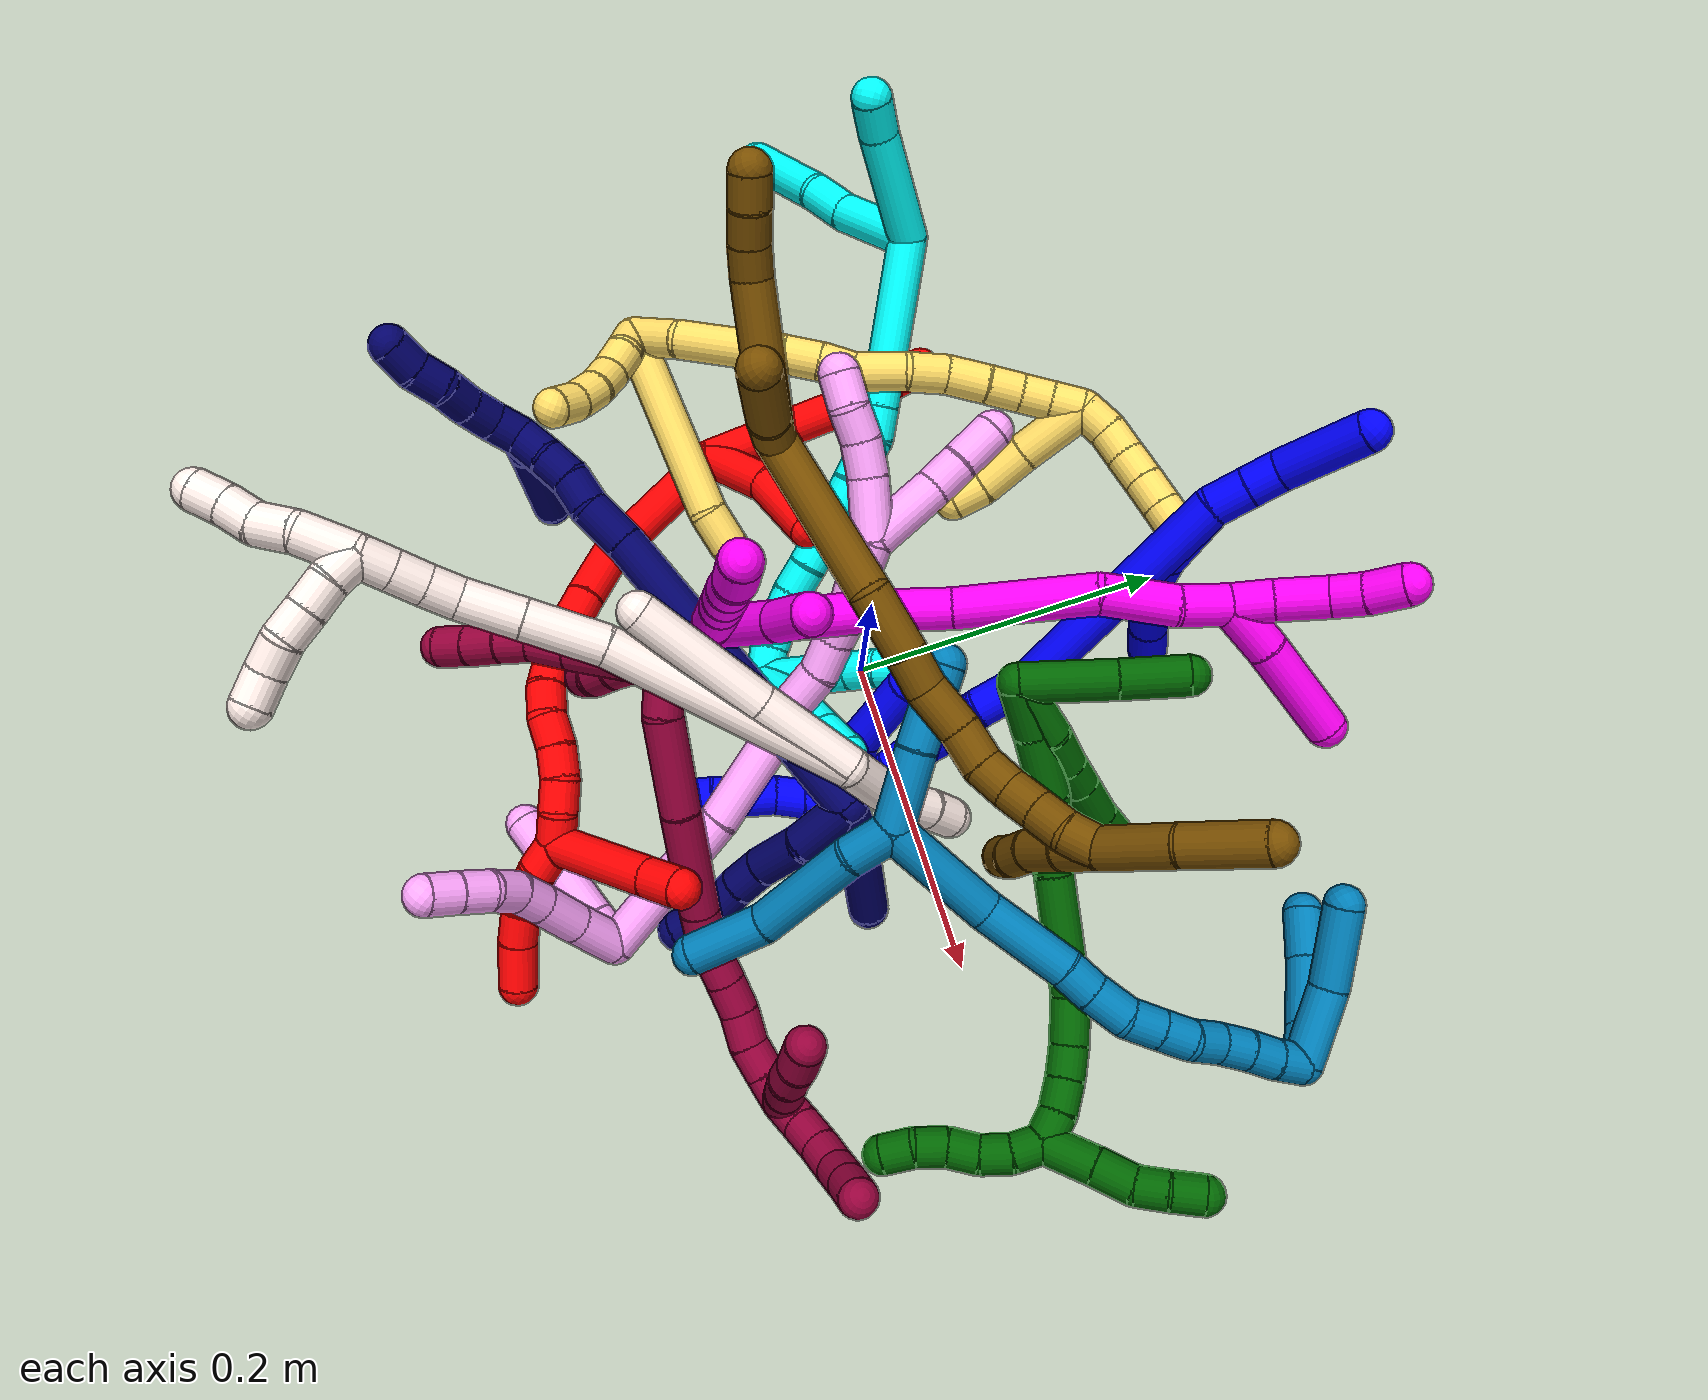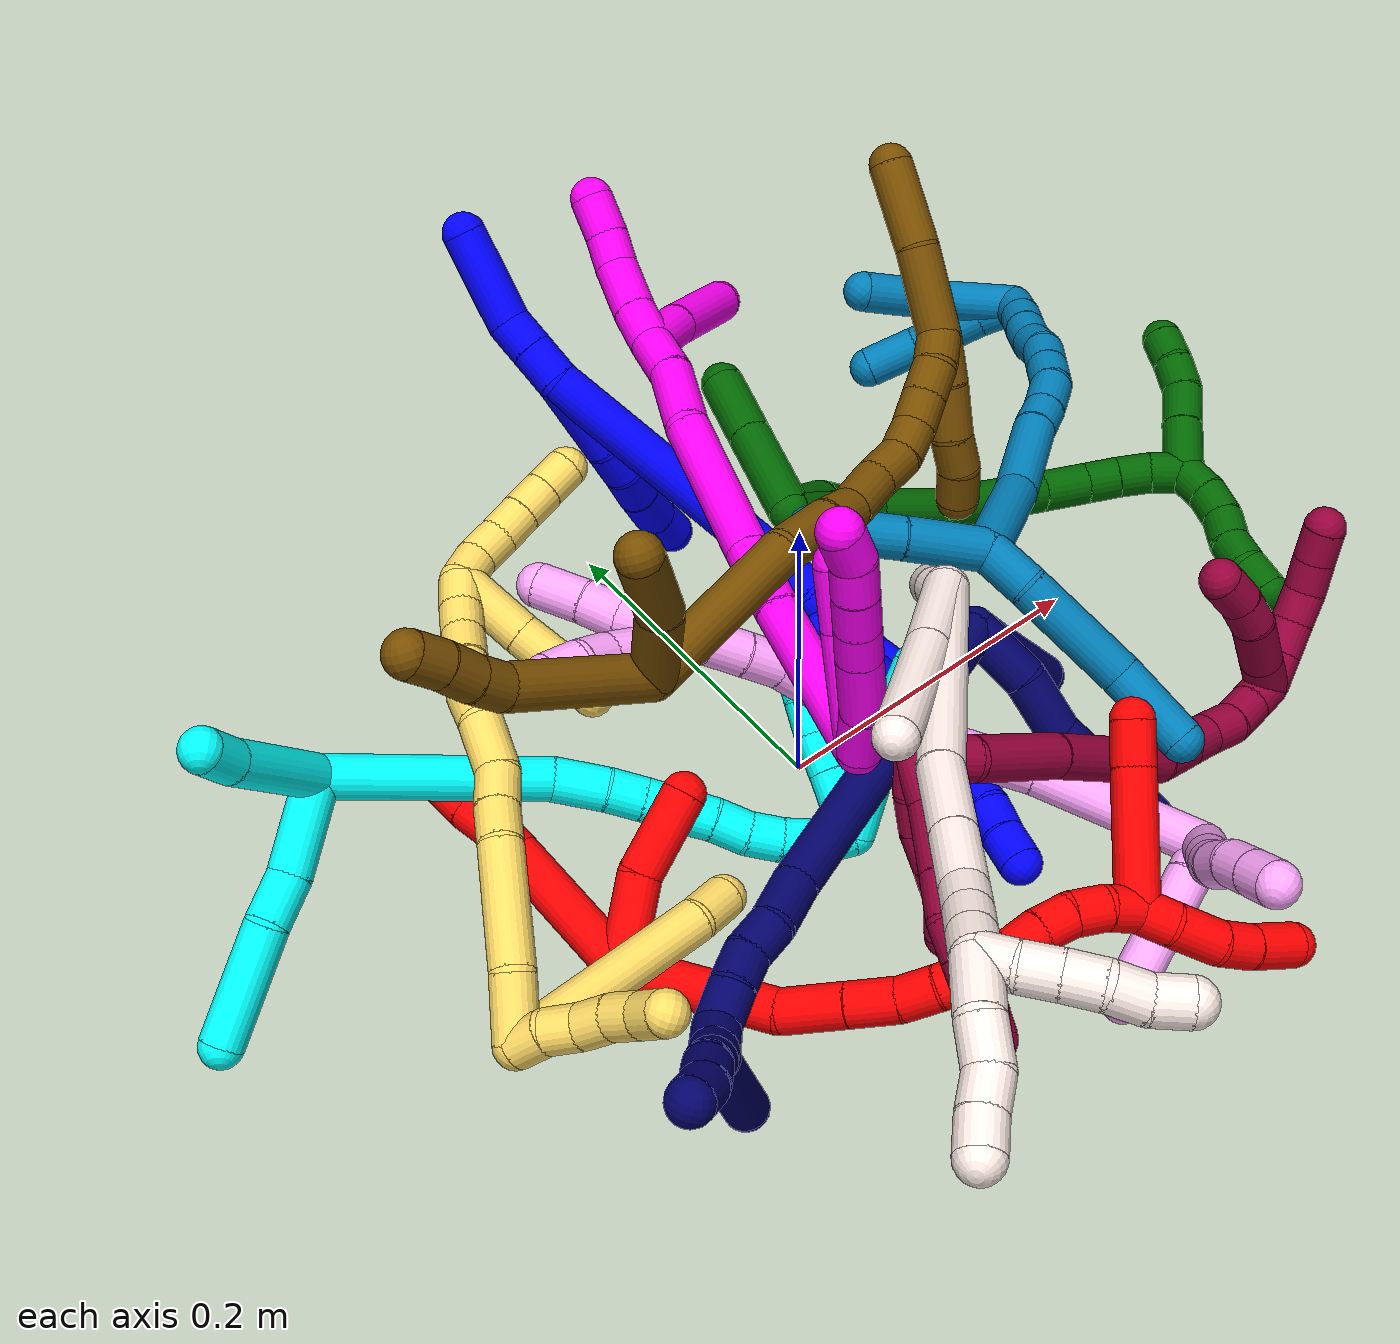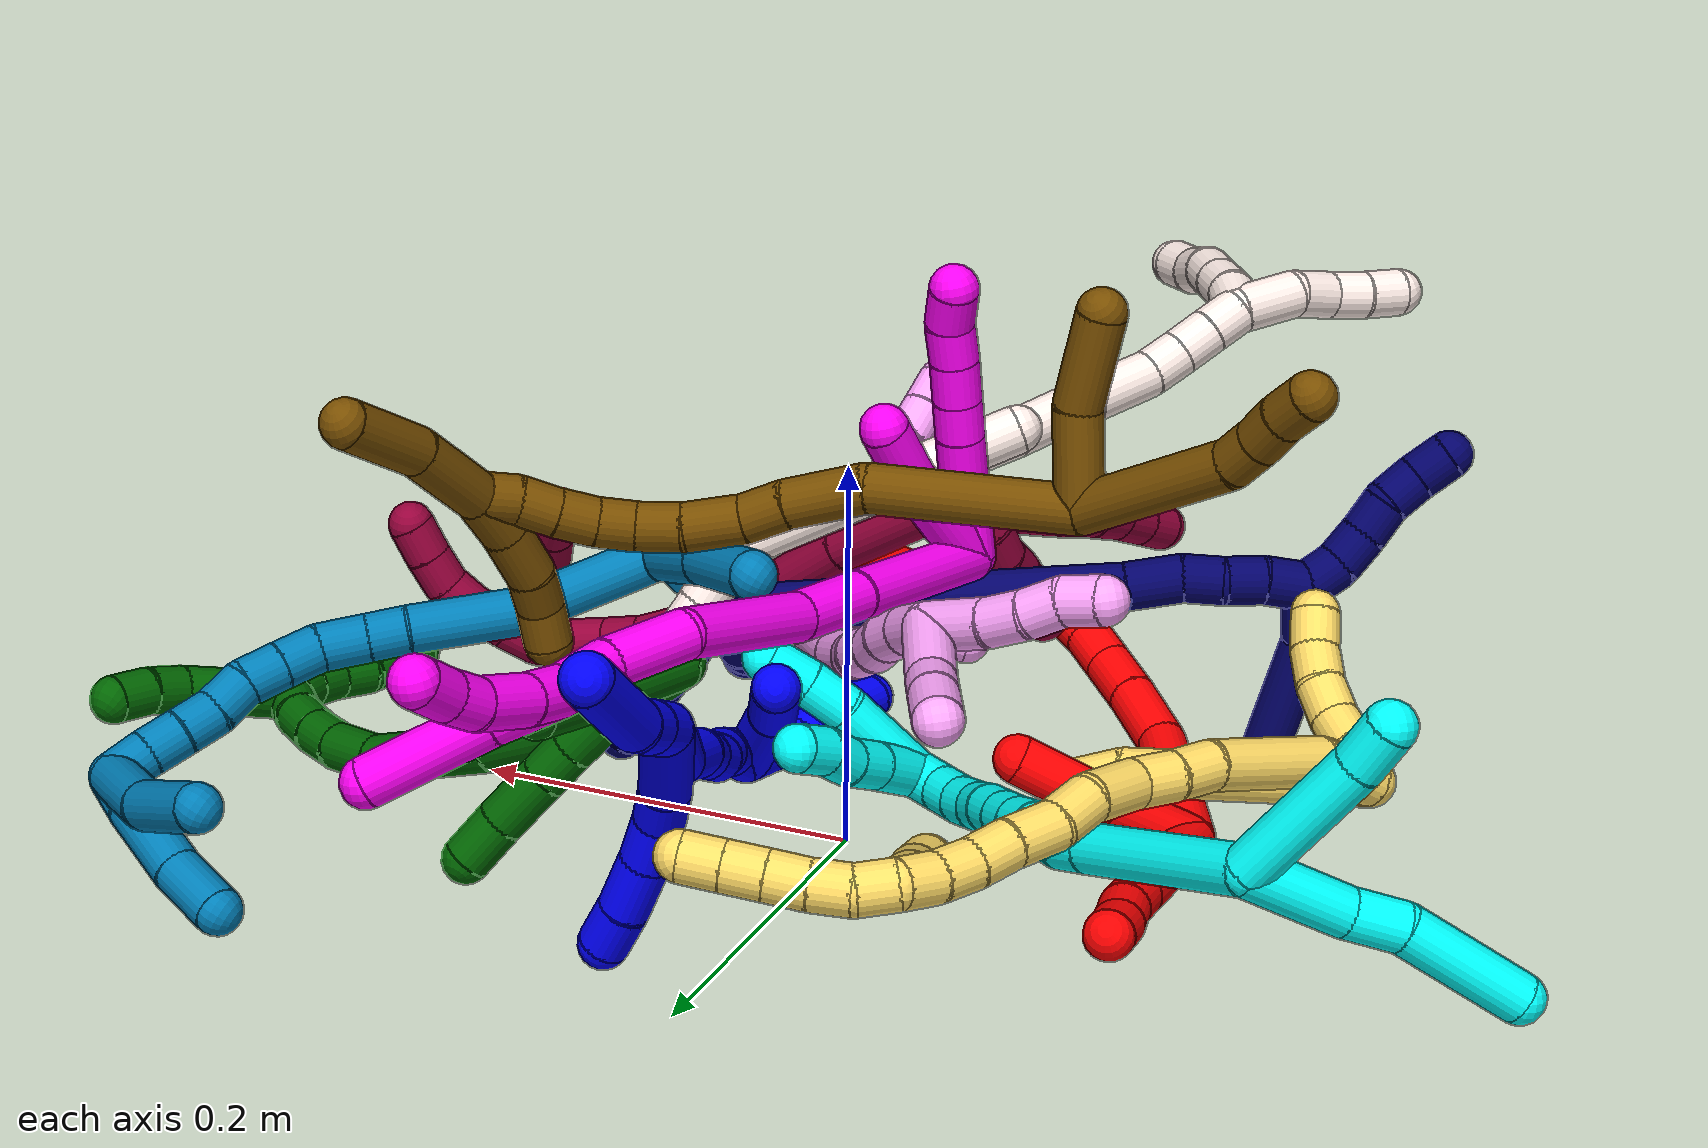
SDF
<sdf version="1.7">
 <world name="default">
  <plugin name="TubeGeneratorPlugin" filename="libtube_generator_plugin.so"/>
  <model name="photoneo_s_sensor">
   <static>1</static>
   <pose>0 0 2 1.57079 1.57079 3.14159</pose>
   <link name="link">
    <inertial><mass>0.1</mass></inertial>
    <sensor name="sensor" type="depth">
     <update_rate>30</update_rate>
     <camera>
      <horizontal_fov>1.22</horizontal_fov>
      <image><width>1920</width><height>1200</height><format>B8G8R8</format></image>
      <clip><near>0.1</near><far>4</far></clip>
      <depth_camera><output>points</output></depth_camera>
     </camera>
     <plugin name="camera_plugin" filename="libgazebo_ros_depth_camera.so">
      <baseline>0.2</baseline>
      <alwaysOn>1</alwaysOn>
      <updateRate>0.0</updateRate>
      <cameraName>camera_ir</cameraName>
      <imageTopicName>/camera/color/image_raw</imageTopicName>
      <cameraInfoTopicName>/camera/color/camera_info</cameraInfoTopicName>
      <depthImageTopicName>/camera/depth/image_raw</depthImageTopicName>
      <depthImageCameraInfoTopicName>/camera/depth/camera_info</depthImageCameraInfoTopicName>
      <pointCloudTopicName>/camera/depth/points</pointCloudTopicName>
      <frameName>fr_optical</frameName>
      <pointCloudCutoff>0.1</pointCloudCutoff>
      <pointCloudCutoffMax>2.0</pointCloudCutoffMax>
      <distortionK1>0</distortionK1>
      <distortionK2>0</distortionK2>
      <distortionK3>0</distortionK3>
      <distortionT1>0</distortionT1>
      <distortionT2>0</distortionT2>
      <CxPrime>0</CxPrime>
      <Cx>0</Cx>
      <Cy>0</Cy>
      <focalLength>0</focalLength>
      <hackBaseline>0</hackBaseline>
     </plugin>
    </sensor>
   </link>
  </model>
  <gravity>0 0 -9.8</gravity>
  <magnetic_field>6e-06 2.3e-05 -4.2e-05</magnetic_field>
  <atmosphere type="adiabatic"/>
  <physics name="default_physics" default="0" type="ode">
   <max_step_size>0.003</max_step_size>
   <real_time_factor>1</real_time_factor>
   <real_time_update_rate>1000</real_time_update_rate>
   <max_contacts>10000</max_contacts>
   <ode>
    <solver>
     <type>quick</type>
     <iters>100</iters>
     <sor>1.3</sor>
     <use_dynamic_moi_rescaling>0</use_dynamic_moi_rescaling>
    </solver>
    <constraints>
     <contact_max_correcting_vel>0</contact_max_correcting_vel>
     <contact_surface_layer>0.001</contact_surface_layer>
     <cfm>0</cfm>
     <erp>0.2</erp>
    </constraints>
   </ode>
  </physics>
  <scene><ambient>0.4 0.4 0.4 1</ambient><background>0.7 0.7 0.7 1</background><shadows>0</shadows></scene>
  <audio><device>default</device></audio>
  <spherical_coordinates>
   <surface_model>EARTH_WGS84</surface_model>
   <latitude_deg>0</latitude_deg>
   <longitude_deg>0</longitude_deg>
   <elevation>0</elevation>
   <heading_deg>0</heading_deg>
  </spherical_coordinates>
  <model name="bin">
   <static>1</static>
   <link name="bottom">
    <collision name="collision-bottom">
     <pose>0 0 -0.01 0 -0 0</pose>
     <geometry><box><size>0.8 0.6 0.02</size></box></geometry>
     <surface>
      <friction><ode><mu>100</mu><mu2>100</mu2></ode></friction>
      <contact><collide_bitmask>65535</collide_bitmask></contact>
     </surface>
    </collision>
   </link>
   <link name="west_wall">
    <collision name="collision-west_wall">
     <pose>-0.41 0 0.1 0 -0 0</pose>
     <geometry><box><size>0.02 0.6 0.2</size></box></geometry>
     <surface>
      <friction><ode><mu>100</mu><mu2>100</mu2></ode></friction>
      <contact><collide_bitmask>65535</collide_bitmask></contact>
     </surface>
    </collision>
   </link>
   <link name="east_wall">
    <collision name="collision-east_wall">
     <pose>0.41 0 0.1 0 -0 0</pose>
     <geometry><box><size>0.02 0.6 0.2</size></box></geometry>
     <surface>
      <friction><ode><mu>100</mu><mu2>100</mu2></ode></friction>
      <contact><collide_bitmask>65535</collide_bitmask></contact>
     </surface>
    </collision>
   </link>
   <link name="south_wall">
    <collision name="collision-south_wall">
     <pose>0 -0.31 0.1 0 -0 0</pose>
     <geometry><box><size>0.8 0.02 0.2</size></box></geometry>
     <surface>
      <friction><ode><mu>100</mu><mu2>100</mu2></ode></friction>
      <contact><collide_bitmask>65535</collide_bitmask></contact>
     </surface>
    </collision>
   </link>
   <link name="north_wall">
    <collision name="collision-north_wall">
     <pose>0 0.31 0.1 0 -0 0</pose>
     <geometry><box><size>0.8 0.02 0.2</size></box></geometry>
     <surface>
      <friction><ode><mu>100</mu><mu2>100</mu2></ode></friction>
      <contact><collide_bitmask>65535</collide_bitmask></contact>
     </surface>
    </collision>
   </link>
  </model>
  <model name="1">
   <static>0</static>
   <link name="1">
    <collision name="collision-cylinder-e_1_2_8">
     <pose>-0.006068 0.012363 -0.021232 -2.6143 -0.242125 0.846866</pose>
     <geometry><cylinder><radius>0.0125</radius><length>0.050615</length></cylinder></geometry>
     <surface>
      <friction><ode><mu>1.16</mu><mu2>1.16</mu2><slip1>0</slip1><slip2>0</slip2></ode></friction>
      <contact><ode><kp>1e+06</kp><kd>1</kd><max_vel>0</max_vel><min_depth>0.001</min_depth></ode></contact>
     </surface>
    </collision>
    <visual name="visual-cylinder-e_1_2_8">
     <pose>-0.006068 0.012363 -0.021232 -2.6143 -0.242125 0.846866</pose>
     <geometry><cylinder><radius>0.0125</radius><length>0.050615</length></cylinder></geometry>
     <material><ambient>0 0 1 1</ambient></material>
    </visual>
    <collision name="collision-cylinder-e_2_8_9">
     <pose>-0.014272 0.031597 -0.050329 -2.42353 -0.201781 0.526944</pose>
     <geometry><cylinder><radius>0.0125</radius><length>0.02132</length></cylinder></geometry>
     <surface>
      <friction><ode><mu>1.16</mu><mu2>1.16</mu2><slip1>0</slip1><slip2>0</slip2></ode></friction>
      <contact><ode><kp>1e+06</kp><kd>1</kd><max_vel>0</max_vel><min_depth>0.001</min_depth></ode></contact>
     </surface>
    </collision>
    <visual name="visual-cylinder-e_2_8_9">
     <pose>-0.014272 0.031597 -0.050329 -2.42353 -0.201781 0.526944</pose>
     <geometry><cylinder><radius>0.0125</radius><length>0.02132</length></cylinder></geometry>
     <material><ambient>0 0 1 1</ambient></material>
    </visual>
    <collision name="collision-cylinder-e_3_9_10">
     <pose>-0.018401 0.048336 -0.065112 -2.18232 -0.163894 0.313213</pose>
     <geometry><cylinder><radius>0.0125</radius><length>0.02443</length></cylinder></geometry>
     <surface>
      <friction><ode><mu>1.16</mu><mu2>1.16</mu2><slip1>0</slip1><slip2>0</slip2></ode></friction>
      <contact><ode><kp>1e+06</kp><kd>1</kd><max_vel>0</max_vel><min_depth>0.001</min_depth></ode></contact>
     </surface>
    </collision>
    <visual name="visual-cylinder-e_3_9_10">
     <pose>-0.018401 0.048336 -0.065112 -2.18232 -0.163894 0.313213</pose>
     <geometry><cylinder><radius>0.0125</radius><length>0.02443</length></cylinder></geometry>
     <material><ambient>0 0 1 1</ambient></material>
    </visual>
    <collision name="collision-cylinder-e_4_10_11">
     <pose>-0.021818 0.070783 -0.07969 -2.1177 -0.096364 0.171206</pose>
     <geometry><cylinder><radius>0.0125</radius><length>0.029594</length></cylinder></geometry>
     <surface>
      <friction><ode><mu>1.16</mu><mu2>1.16</mu2><slip1>0</slip1><slip2>0</slip2></ode></friction>
      <contact><ode><kp>1e+06</kp><kd>1</kd><max_vel>0</max_vel><min_depth>0.001</min_depth></ode></contact>
     </surface>
    </collision>
    <visual name="visual-cylinder-e_4_10_11">
     <pose>-0.021818 0.070783 -0.07969 -2.1177 -0.096364 0.171206</pose>
     <geometry><cylinder><radius>0.0125</radius><length>0.029594</length></cylinder></geometry>
     <material><ambient>0 0 1 1</ambient></material>
    </visual>
    <collision name="collision-cylinder-e_5_11_6">
     <pose>-0.023364 0.09331 -0.094099 -2.16692 -0.010192 0.01923</pose>
     <geometry><cylinder><radius>0.0125</radius><length>0.024042</length></cylinder></geometry>
     <surface>
      <friction><ode><mu>1.16</mu><mu2>1.16</mu2><slip1>0</slip1><slip2>0</slip2></ode></friction>
      <contact><ode><kp>1e+06</kp><kd>1</kd><max_vel>0</max_vel><min_depth>0.001</min_depth></ode></contact>
     </surface>
    </collision>
    <visual name="visual-cylinder-e_5_11_6">
     <pose>-0.023364 0.09331 -0.094099 -2.16692 -0.010192 0.01923</pose>
     <geometry><cylinder><radius>0.0125</radius><length>0.024042</length></cylinder></geometry>
     <material><ambient>0 0 1 1</ambient></material>
    </visual>
    <collision name="collision-cylinder-e_1_2_12">
     <pose>0.002808 0.001223 0.011217 -0.108598 0.243897 -0.013322</pose>
     <geometry><cylinder><radius>0.0125</radius><length>0.023255</length></cylinder></geometry>
     <surface>
      <friction><ode><mu>1.16</mu><mu2>1.16</mu2><slip1>0</slip1><slip2>0</slip2></ode></friction>
      <contact><ode><kp>1e+06</kp><kd>1</kd><max_vel>0</max_vel><min_depth>0.001</min_depth></ode></contact>
     </surface>
    </collision>
    <visual name="visual-cylinder-e_1_2_12">
     <pose>0.002808 0.001223 0.011217 -0.108598 0.243897 -0.013322</pose>
     <geometry><cylinder><radius>0.0125</radius><length>0.023255</length></cylinder></geometry>
     <material><ambient>0 0 1 1</ambient></material>
    </visual>
    <collision name="collision-cylinder-e_2_12_13">
     <pose>0.0081 0.003649 0.032468 -0.119296 0.24106 -0.014466</pose>
     <geometry><cylinder><radius>0.0125</radius><length>0.020812</length></cylinder></geometry>
     <surface>
      <friction><ode><mu>1.16</mu><mu2>1.16</mu2><slip1>0</slip1><slip2>0</slip2></ode></friction>
      <contact><ode><kp>1e+06</kp><kd>1</kd><max_vel>0</max_vel><min_depth>0.001</min_depth></ode></contact>
     </surface>
    </collision>
    <visual name="visual-cylinder-e_2_12_13">
     <pose>0.0081 0.003649 0.032468 -0.119296 0.24106 -0.014466</pose>
     <geometry><cylinder><radius>0.0125</radius><length>0.020812</length></cylinder></geometry>
     <material><ambient>0 0 1 1</ambient></material>
    </visual>
    <collision name="collision-cylinder-e_3_13_5">
     <pose>0.023039 0.001282 0.067285 0.143015 0.461547 0.033657</pose>
     <geometry><cylinder><radius>0.0125</radius><length>0.055932</length></cylinder></geometry>
     <surface>
      <friction><ode><mu>1.16</mu><mu2>1.16</mu2><slip1>0</slip1><slip2>0</slip2></ode></friction>
      <contact><ode><kp>1e+06</kp><kd>1</kd><max_vel>0</max_vel><min_depth>0.001</min_depth></ode></contact>
     </surface>
    </collision>
    <visual name="visual-cylinder-e_3_13_5">
     <pose>0.023039 0.001282 0.067285 0.143015 0.461547 0.033657</pose>
     <geometry><cylinder><radius>0.0125</radius><length>0.055932</length></cylinder></geometry>
     <material><ambient>0 0 1 1</ambient></material>
    </visual>
    <collision name="collision-cylinder-e_1_2_14">
     <pose>-0.003274 0.00695 -0.076896 -3.05146 -0.042374 0.878509</pose>
     <geometry><cylinder><radius>0.0125</radius><length>0.154557</length></cylinder></geometry>
     <surface>
      <friction><ode><mu>1.16</mu><mu2>1.16</mu2><slip1>0</slip1><slip2>0</slip2></ode></friction>
      <contact><ode><kp>1e+06</kp><kd>1</kd><max_vel>0</max_vel><min_depth>0.001</min_depth></ode></contact>
     </surface>
    </collision>
    <visual name="visual-cylinder-e_1_2_14">
     <pose>-0.003274 0.00695 -0.076896 -3.05146 -0.042374 0.878509</pose>
     <geometry><cylinder><radius>0.0125</radius><length>0.154557</length></cylinder></geometry>
     <material><ambient>0 0 1 1</ambient></material>
    </visual>
    <collision name="collision-cylinder-e_2_14_15">
     <pose>-0.008983 0.010421 -0.170648 2.9381 -0.140566 -1.20733</pose>
     <geometry><cylinder><radius>0.0125</radius><length>0.034766</length></cylinder></geometry>
     <surface>
      <friction><ode><mu>1.16</mu><mu2>1.16</mu2><slip1>0</slip1><slip2>0</slip2></ode></friction>
      <contact><ode><kp>1e+06</kp><kd>1</kd><max_vel>0</max_vel><min_depth>0.001</min_depth></ode></contact>
     </surface>
    </collision>
    <visual name="visual-cylinder-e_2_14_15">
     <pose>-0.008983 0.010421 -0.170648 2.9381 -0.140566 -1.20733</pose>
     <geometry><cylinder><radius>0.0125</radius><length>0.034766</length></cylinder></geometry>
     <material><ambient>0 0 1 1</ambient></material>
    </visual>
    <collision name="collision-cylinder-e_3_15_16">
     <pose>-0.012809 0.006862 -0.200765 3.1355 -0.104547 -3.02536</pose>
     <geometry><cylinder><radius>0.0125</radius><length>0.026668</length></cylinder></geometry>
     <surface>
      <friction><ode><mu>1.16</mu><mu2>1.16</mu2><slip1>0</slip1><slip2>0</slip2></ode></friction>
      <contact><ode><kp>1e+06</kp><kd>1</kd><max_vel>0</max_vel><min_depth>0.001</min_depth></ode></contact>
     </surface>
    </collision>
    <visual name="visual-cylinder-e_3_15_16">
     <pose>-0.012809 0.006862 -0.200765 3.1355 -0.104547 -3.02536</pose>
     <geometry><cylinder><radius>0.0125</radius><length>0.026668</length></cylinder></geometry>
     <material><ambient>0 0 1 1</ambient></material>
    </visual>
    <collision name="collision-cylinder-e_4_16_17">
     <pose>-0.016703 0.006084 -0.224998 3.07814 -0.223739 -2.59088</pose>
     <geometry><cylinder><radius>0.0125</radius><length>0.022551</length></cylinder></geometry>
     <surface>
      <friction><ode><mu>1.16</mu><mu2>1.16</mu2><slip1>0</slip1><slip2>0</slip2></ode></friction>
      <contact><ode><kp>1e+06</kp><kd>1</kd><max_vel>0</max_vel><min_depth>0.001</min_depth></ode></contact>
     </surface>
    </collision>
    <visual name="visual-cylinder-e_4_16_17">
     <pose>-0.016703 0.006084 -0.224998 3.07814 -0.223739 -2.59088</pose>
     <geometry><cylinder><radius>0.0125</radius><length>0.022551</length></cylinder></geometry>
     <material><ambient>0 0 1 1</ambient></material>
    </visual>
    <collision name="collision-cylinder-e_5_17_18">
     <pose>-0.019266 0.003757 -0.246012 2.98067 -0.006037 -0.074833</pose>
     <geometry><cylinder><radius>0.0125</radius><length>0.020348</length></cylinder></geometry>
     <surface>
      <friction><ode><mu>1.16</mu><mu2>1.16</mu2><slip1>0</slip1><slip2>0</slip2></ode></friction>
      <contact><ode><kp>1e+06</kp><kd>1</kd><max_vel>0</max_vel><min_depth>0.001</min_depth></ode></contact>
     </surface>
    </collision>
    <visual name="visual-cylinder-e_5_17_18">
     <pose>-0.019266 0.003757 -0.246012 2.98067 -0.006037 -0.074833</pose>
     <geometry><cylinder><radius>0.0125</radius><length>0.020348</length></cylinder></geometry>
     <material><ambient>0 0 1 1</ambient></material>
    </visual>
    <collision name="collision-cylinder-e_6_18_19">
     <pose>-0.021016 0.00117 -0.266047 3.04606 -0.166649 -2.10191</pose>
     <geometry><cylinder><radius>0.0125</radius><length>0.020357</length></cylinder></geometry>
     <surface>
      <friction><ode><mu>1.16</mu><mu2>1.16</mu2><slip1>0</slip1><slip2>0</slip2></ode></friction>
      <contact><ode><kp>1e+06</kp><kd>1</kd><max_vel>0</max_vel><min_depth>0.001</min_depth></ode></contact>
     </surface>
    </collision>
    <visual name="visual-cylinder-e_6_18_19">
     <pose>-0.021016 0.00117 -0.266047 3.04606 -0.166649 -2.10191</pose>
     <geometry><cylinder><radius>0.0125</radius><length>0.020357</length></cylinder></geometry>
     <material><ambient>0 0 1 1</ambient></material>
    </visual>
    <collision name="collision-cylinder-e_7_19_1">
     <pose>-0.026778 -0.000108 -0.285577 3.1081 -0.403434 -2.97816</pose>
     <geometry><cylinder><radius>0.0125</radius><length>0.020753</length></cylinder></geometry>
     <surface>
      <friction><ode><mu>1.16</mu><mu2>1.16</mu2><slip1>0</slip1><slip2>0</slip2></ode></friction>
      <contact><ode><kp>1e+06</kp><kd>1</kd><max_vel>0</max_vel><min_depth>0.001</min_depth></ode></contact>
     </surface>
    </collision>
    <visual name="visual-cylinder-e_7_19_1">
     <pose>-0.026778 -0.000108 -0.285577 3.1081 -0.403434 -2.97816</pose>
     <geometry><cylinder><radius>0.0125</radius><length>0.020753</length></cylinder></geometry>
     <material><ambient>0 0 1 1</ambient></material>
    </visual>
    <collision name="collision-cylinder-e_1_1_20">
     <pose>-0.030802 -0.013962 -0.272264 0.534724 0.001862 0.00051</pose>
     <geometry><cylinder><radius>0.0125</radius><length>0.053118</length></cylinder></geometry>
     <surface>
      <friction><ode><mu>1.16</mu><mu2>1.16</mu2><slip1>0</slip1><slip2>0</slip2></ode></friction>
      <contact><ode><kp>1e+06</kp><kd>1</kd><max_vel>0</max_vel><min_depth>0.001</min_depth></ode></contact>
     </surface>
    </collision>
    <visual name="visual-cylinder-e_1_1_20">
     <pose>-0.030802 -0.013962 -0.272264 0.534724 0.001862 0.00051</pose>
     <geometry><cylinder><radius>0.0125</radius><length>0.053118</length></cylinder></geometry>
     <material><ambient>0 0 1 1</ambient></material>
    </visual>
    <collision name="collision-cylinder-e_2_20_4">
     <pose>-0.028818 -0.03351 -0.226838 0.260347 0.082636 0.010824</pose>
     <geometry><cylinder><radius>0.0125</radius><length>0.046882</length></cylinder></geometry>
     <surface>
      <friction><ode><mu>1.16</mu><mu2>1.16</mu2><slip1>0</slip1><slip2>0</slip2></ode></friction>
      <contact><ode><kp>1e+06</kp><kd>1</kd><max_vel>0</max_vel><min_depth>0.001</min_depth></ode></contact>
     </surface>
    </collision>
    <visual name="visual-cylinder-e_2_20_4">
     <pose>-0.028818 -0.03351 -0.226838 0.260347 0.082636 0.010824</pose>
     <geometry><cylinder><radius>0.0125</radius><length>0.046882</length></cylinder></geometry>
     <material><ambient>0 0 1 1</ambient></material>
    </visual>
    <collision name="collision-cylinder-e_1_1_21">
     <pose>-0.034319 -0.005483 -0.303016 2.57233 -0.354131 -1.09782</pose>
     <geometry><cylinder><radius>0.0125</radius><length>0.02</length></cylinder></geometry>
     <surface>
      <friction><ode><mu>1.16</mu><mu2>1.16</mu2><slip1>0</slip1><slip2>0</slip2></ode></friction>
      <contact><ode><kp>1e+06</kp><kd>1</kd><max_vel>0</max_vel><min_depth>0.001</min_depth></ode></contact>
     </surface>
    </collision>
    <visual name="visual-cylinder-e_1_1_21">
     <pose>-0.034319 -0.005483 -0.303016 2.57233 -0.354131 -1.09782</pose>
     <geometry><cylinder><radius>0.0125</radius><length>0.02</length></cylinder></geometry>
     <material><ambient>0 0 1 1</ambient></material>
    </visual>
    <collision name="collision-cylinder-e_2_21_22">
     <pose>-0.042838 -0.016742 -0.316917 2.3396 -0.529477 -1.13783</pose>
     <geometry><cylinder><radius>0.0125</radius><length>0.02</length></cylinder></geometry>
     <surface>
      <friction><ode><mu>1.16</mu><mu2>1.16</mu2><slip1>0</slip1><slip2>0</slip2></ode></friction>
      <contact><ode><kp>1e+06</kp><kd>1</kd><max_vel>0</max_vel><min_depth>0.001</min_depth></ode></contact>
     </surface>
    </collision>
    <visual name="visual-cylinder-e_2_21_22">
     <pose>-0.042838 -0.016742 -0.316917 2.3396 -0.529477 -1.13783</pose>
     <geometry><cylinder><radius>0.0125</radius><length>0.02</length></cylinder></geometry>
     <material><ambient>0 0 1 1</ambient></material>
    </visual>
    <collision name="collision-cylinder-e_3_22_23">
     <pose>-0.050034 -0.030337 -0.329301 2.28312 -0.216181 -0.465575</pose>
     <geometry><cylinder><radius>0.0125</radius><length>0.02</length></cylinder></geometry>
     <surface>
      <friction><ode><mu>1.16</mu><mu2>1.16</mu2><slip1>0</slip1><slip2>0</slip2></ode></friction>
      <contact><ode><kp>1e+06</kp><kd>1</kd><max_vel>0</max_vel><min_depth>0.001</min_depth></ode></contact>
     </surface>
    </collision>
    <visual name="visual-cylinder-e_3_22_23">
     <pose>-0.050034 -0.030337 -0.329301 2.28312 -0.216181 -0.465575</pose>
     <geometry><cylinder><radius>0.0125</radius><length>0.02</length></cylinder></geometry>
     <material><ambient>0 0 1 1</ambient></material>
    </visual>
    <collision name="collision-cylinder-e_4_23_24">
     <pose>-0.05637 -0.043931 -0.342316 2.38961 -0.432475 -1.01557</pose>
     <geometry><cylinder><radius>0.0125</radius><length>0.02</length></cylinder></geometry>
     <surface>
      <friction><ode><mu>1.16</mu><mu2>1.16</mu2><slip1>0</slip1><slip2>0</slip2></ode></friction>
      <contact><ode><kp>1e+06</kp><kd>1</kd><max_vel>0</max_vel><min_depth>0.001</min_depth></ode></contact>
     </surface>
    </collision>
    <visual name="visual-cylinder-e_4_23_24">
     <pose>-0.05637 -0.043931 -0.342316 2.38961 -0.432475 -1.01557</pose>
     <geometry><cylinder><radius>0.0125</radius><length>0.02</length></cylinder></geometry>
     <material><ambient>0 0 1 1</ambient></material>
    </visual>
    <collision name="collision-cylinder-e_5_24_3">
     <pose>-0.06405 -0.055558 -0.356589 2.52429 -0.356351 -1.02829</pose>
     <geometry><cylinder><radius>0.0125</radius><length>0.02</length></cylinder></geometry>
     <surface>
      <friction><ode><mu>1.16</mu><mu2>1.16</mu2><slip1>0</slip1><slip2>0</slip2></ode></friction>
      <contact><ode><kp>1e+06</kp><kd>1</kd><max_vel>0</max_vel><min_depth>0.001</min_depth></ode></contact>
     </surface>
    </collision>
    <visual name="visual-cylinder-e_5_24_3">
     <pose>-0.06405 -0.055558 -0.356589 2.52429 -0.356351 -1.02829</pose>
     <geometry><cylinder><radius>0.0125</radius><length>0.02</length></cylinder></geometry>
     <material><ambient>0 0 1 1</ambient></material>
    </visual>
    <collision name="collision-sphere-3">
     <pose>-0.067538 -0.060983 -0.364231 0 -0 0</pose>
     <geometry><sphere><radius>0.0125</radius></sphere></geometry>
     <surface>
      <friction><ode><mu>1.16</mu><mu2>1.16</mu2><slip1>0</slip1><slip2>0</slip2></ode></friction>
      <contact><ode><kp>1e+06</kp><kd>1</kd><max_vel>0</max_vel><min_depth>0.001</min_depth></ode></contact>
     </surface>
    </collision>
    <visual name="visual-sphere-3">
     <pose>-0.067538 -0.060983 -0.364231 0 -0 0</pose>
     <geometry><sphere><radius>0.0125</radius></sphere></geometry>
     <material><ambient>0 0 1 1</ambient></material>
    </visual>
    <collision name="collision-sphere-24">
     <pose>-0.060561 -0.050133 -0.348947 0 -0 0</pose>
     <geometry><sphere><radius>0.0125</radius></sphere></geometry>
     <surface>
      <friction><ode><mu>1.16</mu><mu2>1.16</mu2><slip1>0</slip1><slip2>0</slip2></ode></friction>
      <contact><ode><kp>1e+06</kp><kd>1</kd><max_vel>0</max_vel><min_depth>0.001</min_depth></ode></contact>
     </surface>
    </collision>
    <visual name="visual-sphere-24">
     <pose>-0.060561 -0.050133 -0.348947 0 -0 0</pose>
     <geometry><sphere><radius>0.0125</radius></sphere></geometry>
     <material><ambient>0 0 1 1</ambient></material>
    </visual>
    <collision name="collision-sphere-23">
     <pose>-0.052179 -0.037729 -0.335685 0 -0 0</pose>
     <geometry><sphere><radius>0.0125</radius></sphere></geometry>
     <surface>
      <friction><ode><mu>1.16</mu><mu2>1.16</mu2><slip1>0</slip1><slip2>0</slip2></ode></friction>
      <contact><ode><kp>1e+06</kp><kd>1</kd><max_vel>0</max_vel><min_depth>0.001</min_depth></ode></contact>
     </surface>
    </collision>
    <visual name="visual-sphere-23">
     <pose>-0.052179 -0.037729 -0.335685 0 -0 0</pose>
     <geometry><sphere><radius>0.0125</radius></sphere></geometry>
     <material><ambient>0 0 1 1</ambient></material>
    </visual>
    <collision name="collision-sphere-22">
     <pose>-0.047889 -0.022945 -0.322917 0 -0 0</pose>
     <geometry><sphere><radius>0.0125</radius></sphere></geometry>
     <surface>
      <friction><ode><mu>1.16</mu><mu2>1.16</mu2><slip1>0</slip1><slip2>0</slip2></ode></friction>
      <contact><ode><kp>1e+06</kp><kd>1</kd><max_vel>0</max_vel><min_depth>0.001</min_depth></ode></contact>
     </surface>
    </collision>
    <visual name="visual-sphere-22">
     <pose>-0.047889 -0.022945 -0.322917 0 -0 0</pose>
     <geometry><sphere><radius>0.0125</radius></sphere></geometry>
     <material><ambient>0 0 1 1</ambient></material>
    </visual>
    <collision name="collision-sphere-21">
     <pose>-0.037787 -0.010538 -0.310916 0 -0 0</pose>
     <geometry><sphere><radius>0.0125</radius></sphere></geometry>
     <surface>
      <friction><ode><mu>1.16</mu><mu2>1.16</mu2><slip1>0</slip1><slip2>0</slip2></ode></friction>
      <contact><ode><kp>1e+06</kp><kd>1</kd><max_vel>0</max_vel><min_depth>0.001</min_depth></ode></contact>
     </surface>
    </collision>
    <visual name="visual-sphere-21">
     <pose>-0.037787 -0.010538 -0.310916 0 -0 0</pose>
     <geometry><sphere><radius>0.0125</radius></sphere></geometry>
     <material><ambient>0 0 1 1</ambient></material>
    </visual>
    <collision name="collision-sphere-4">
     <pose>-0.026883 -0.039523 -0.204265 0 -0 0</pose>
     <geometry><sphere><radius>0.0125</radius></sphere></geometry>
     <surface>
      <friction><ode><mu>1.16</mu><mu2>1.16</mu2><slip1>0</slip1><slip2>0</slip2></ode></friction>
      <contact><ode><kp>1e+06</kp><kd>1</kd><max_vel>0</max_vel><min_depth>0.001</min_depth></ode></contact>
     </surface>
    </collision>
    <visual name="visual-sphere-4">
     <pose>-0.026883 -0.039523 -0.204265 0 -0 0</pose>
     <geometry><sphere><radius>0.0125</radius></sphere></geometry>
     <material><ambient>0 0 1 1</ambient></material>
    </visual>
    <collision name="collision-sphere-20">
     <pose>-0.030753 -0.027496 -0.249412 0 -0 0</pose>
     <geometry><sphere><radius>0.0125</radius></sphere></geometry>
     <surface>
      <friction><ode><mu>1.16</mu><mu2>1.16</mu2><slip1>0</slip1><slip2>0</slip2></ode></friction>
      <contact><ode><kp>1e+06</kp><kd>1</kd><max_vel>0</max_vel><min_depth>0.001</min_depth></ode></contact>
     </surface>
    </collision>
    <visual name="visual-sphere-20">
     <pose>-0.030753 -0.027496 -0.249412 0 -0 0</pose>
     <geometry><sphere><radius>0.0125</radius></sphere></geometry>
     <material><ambient>0 0 1 1</ambient></material>
    </visual>
    <collision name="collision-sphere-6">
     <pose>-0.023487 0.103257 -0.100847 0 -0 0</pose>
     <geometry><sphere><radius>0.0125</radius></sphere></geometry>
     <surface>
      <friction><ode><mu>1.16</mu><mu2>1.16</mu2><slip1>0</slip1><slip2>0</slip2></ode></friction>
      <contact><ode><kp>1e+06</kp><kd>1</kd><max_vel>0</max_vel><min_depth>0.001</min_depth></ode></contact>
     </surface>
    </collision>
    <visual name="visual-sphere-6">
     <pose>-0.023487 0.103257 -0.100847 0 -0 0</pose>
     <geometry><sphere><radius>0.0125</radius></sphere></geometry>
     <material><ambient>0 0 1 1</ambient></material>
    </visual>
    <collision name="collision-sphere-11">
     <pose>-0.023242 0.083363 -0.08735 0 -0 0</pose>
     <geometry><sphere><radius>0.0125</radius></sphere></geometry>
     <surface>
      <friction><ode><mu>1.16</mu><mu2>1.16</mu2><slip1>0</slip1><slip2>0</slip2></ode></friction>
      <contact><ode><kp>1e+06</kp><kd>1</kd><max_vel>0</max_vel><min_depth>0.001</min_depth></ode></contact>
     </surface>
    </collision>
    <visual name="visual-sphere-11">
     <pose>-0.023242 0.083363 -0.08735 0 -0 0</pose>
     <geometry><sphere><radius>0.0125</radius></sphere></geometry>
     <material><ambient>0 0 1 1</ambient></material>
    </visual>
    <collision name="collision-sphere-10">
     <pose>-0.020394 0.058203 -0.072031 0 -0 0</pose>
     <geometry><sphere><radius>0.0125</radius></sphere></geometry>
     <surface>
      <friction><ode><mu>1.16</mu><mu2>1.16</mu2><slip1>0</slip1><slip2>0</slip2></ode></friction>
      <contact><ode><kp>1e+06</kp><kd>1</kd><max_vel>0</max_vel><min_depth>0.001</min_depth></ode></contact>
     </surface>
    </collision>
    <visual name="visual-sphere-10">
     <pose>-0.020394 0.058203 -0.072031 0 -0 0</pose>
     <geometry><sphere><radius>0.0125</radius></sphere></geometry>
     <material><ambient>0 0 1 1</ambient></material>
    </visual>
    <collision name="collision-sphere-9">
     <pose>-0.016408 0.038469 -0.058193 0 -0 0</pose>
     <geometry><sphere><radius>0.0125</radius></sphere></geometry>
     <surface>
      <friction><ode><mu>1.16</mu><mu2>1.16</mu2><slip1>0</slip1><slip2>0</slip2></ode></friction>
      <contact><ode><kp>1e+06</kp><kd>1</kd><max_vel>0</max_vel><min_depth>0.001</min_depth></ode></contact>
     </surface>
    </collision>
    <visual name="visual-sphere-9">
     <pose>-0.016408 0.038469 -0.058193 0 -0 0</pose>
     <geometry><sphere><radius>0.0125</radius></sphere></geometry>
     <material><ambient>0 0 1 1</ambient></material>
    </visual>
    <collision name="collision-sphere-2">
     <geometry><sphere><radius>0.0125</radius></sphere></geometry>
     <surface>
      <friction><ode><mu>1.16</mu><mu2>1.16</mu2><slip1>0</slip1><slip2>0</slip2></ode></friction>
      <contact><ode><kp>1e+06</kp><kd>1</kd><max_vel>0</max_vel><min_depth>0.001</min_depth></ode></contact>
     </surface>
    </collision>
    <visual name="visual-sphere-2">
     <geometry><sphere><radius>0.0125</radius></sphere></geometry>
     <material><ambient>0 0 1 1</ambient></material>
    </visual>
    <collision name="collision-sphere-19">
     <pose>-0.022704 0.000212 -0.276039 0 -0 0</pose>
     <geometry><sphere><radius>0.0125</radius></sphere></geometry>
     <surface>
      <friction><ode><mu>1.16</mu><mu2>1.16</mu2><slip1>0</slip1><slip2>0</slip2></ode></friction>
      <contact><ode><kp>1e+06</kp><kd>1</kd><max_vel>0</max_vel><min_depth>0.001</min_depth></ode></contact>
     </surface>
    </collision>
    <visual name="visual-sphere-19">
     <pose>-0.022704 0.000212 -0.276039 0 -0 0</pose>
     <geometry><sphere><radius>0.0125</radius></sphere></geometry>
     <material><ambient>0 0 1 1</ambient></material>
    </visual>
    <collision name="collision-sphere-8">
     <pose>-0.012136 0.024726 -0.042464 0 -0 0</pose>
     <geometry><sphere><radius>0.0125</radius></sphere></geometry>
     <surface>
      <friction><ode><mu>1.16</mu><mu2>1.16</mu2><slip1>0</slip1><slip2>0</slip2></ode></friction>
      <contact><ode><kp>1e+06</kp><kd>1</kd><max_vel>0</max_vel><min_depth>0.001</min_depth></ode></contact>
     </surface>
    </collision>
    <visual name="visual-sphere-8">
     <pose>-0.012136 0.024726 -0.042464 0 -0 0</pose>
     <geometry><sphere><radius>0.0125</radius></sphere></geometry>
     <material><ambient>0 0 1 1</ambient></material>
    </visual>
    <collision name="collision-sphere-12">
     <pose>0.005616 0.002446 0.022434 0 -0 0</pose>
     <geometry><sphere><radius>0.0125</radius></sphere></geometry>
     <surface>
      <friction><ode><mu>1.16</mu><mu2>1.16</mu2><slip1>0</slip1><slip2>0</slip2></ode></friction>
      <contact><ode><kp>1e+06</kp><kd>1</kd><max_vel>0</max_vel><min_depth>0.001</min_depth></ode></contact>
     </surface>
    </collision>
    <visual name="visual-sphere-12">
     <pose>0.005616 0.002446 0.022434 0 -0 0</pose>
     <geometry><sphere><radius>0.0125</radius></sphere></geometry>
     <material><ambient>0 0 1 1</ambient></material>
    </visual>
    <collision name="collision-sphere-13">
     <pose>0.010584 0.004851 0.042501 0 -0 0</pose>
     <geometry><sphere><radius>0.0125</radius></sphere></geometry>
     <surface>
      <friction><ode><mu>1.16</mu><mu2>1.16</mu2><slip1>0</slip1><slip2>0</slip2></ode></friction>
      <contact><ode><kp>1e+06</kp><kd>1</kd><max_vel>0</max_vel><min_depth>0.001</min_depth></ode></contact>
     </surface>
    </collision>
    <visual name="visual-sphere-13">
     <pose>0.010584 0.004851 0.042501 0 -0 0</pose>
     <geometry><sphere><radius>0.0125</radius></sphere></geometry>
     <material><ambient>0 0 1 1</ambient></material>
    </visual>
    <collision name="collision-sphere-5">
     <pose>0.035493 -0.002287 0.09207 0 -0 0</pose>
     <geometry><sphere><radius>0.0125</radius></sphere></geometry>
     <surface>
      <friction><ode><mu>1.16</mu><mu2>1.16</mu2><slip1>0</slip1><slip2>0</slip2></ode></friction>
      <contact><ode><kp>1e+06</kp><kd>1</kd><max_vel>0</max_vel><min_depth>0.001</min_depth></ode></contact>
     </surface>
    </collision>
    <visual name="visual-sphere-5">
     <pose>0.035493 -0.002287 0.09207 0 -0 0</pose>
     <geometry><sphere><radius>0.0125</radius></sphere></geometry>
     <material><ambient>0 0 1 1</ambient></material>
    </visual>
    <collision name="collision-sphere-14">
     <pose>-0.006547 0.0139 -0.153791 0 -0 0</pose>
     <geometry><sphere><radius>0.0125</radius></sphere></geometry>
     <surface>
      <friction><ode><mu>1.16</mu><mu2>1.16</mu2><slip1>0</slip1><slip2>0</slip2></ode></friction>
      <contact><ode><kp>1e+06</kp><kd>1</kd><max_vel>0</max_vel><min_depth>0.001</min_depth></ode></contact>
     </surface>
    </collision>
    <visual name="visual-sphere-14">
     <pose>-0.006547 0.0139 -0.153791 0 -0 0</pose>
     <geometry><sphere><radius>0.0125</radius></sphere></geometry>
     <material><ambient>0 0 1 1</ambient></material>
    </visual>
    <collision name="collision-sphere-15">
     <pose>-0.011418 0.006943 -0.187504 0 -0 0</pose>
     <geometry><sphere><radius>0.0125</radius></sphere></geometry>
     <surface>
      <friction><ode><mu>1.16</mu><mu2>1.16</mu2><slip1>0</slip1><slip2>0</slip2></ode></friction>
      <contact><ode><kp>1e+06</kp><kd>1</kd><max_vel>0</max_vel><min_depth>0.001</min_depth></ode></contact>
     </surface>
    </collision>
    <visual name="visual-sphere-15">
     <pose>-0.011418 0.006943 -0.187504 0 -0 0</pose>
     <geometry><sphere><radius>0.0125</radius></sphere></geometry>
     <material><ambient>0 0 1 1</ambient></material>
    </visual>
    <collision name="collision-sphere-16">
     <pose>-0.014201 0.006782 -0.214025 0 -0 0</pose>
     <geometry><sphere><radius>0.0125</radius></sphere></geometry>
     <surface>
      <friction><ode><mu>1.16</mu><mu2>1.16</mu2><slip1>0</slip1><slip2>0</slip2></ode></friction>
      <contact><ode><kp>1e+06</kp><kd>1</kd><max_vel>0</max_vel><min_depth>0.001</min_depth></ode></contact>
     </surface>
    </collision>
    <visual name="visual-sphere-16">
     <pose>-0.014201 0.006782 -0.214025 0 -0 0</pose>
     <geometry><sphere><radius>0.0125</radius></sphere></geometry>
     <material><ambient>0 0 1 1</ambient></material>
    </visual>
    <collision name="collision-sphere-17">
     <pose>-0.019204 0.005387 -0.23597 0 -0 0</pose>
     <geometry><sphere><radius>0.0125</radius></sphere></geometry>
     <surface>
      <friction><ode><mu>1.16</mu><mu2>1.16</mu2><slip1>0</slip1><slip2>0</slip2></ode></friction>
      <contact><ode><kp>1e+06</kp><kd>1</kd><max_vel>0</max_vel><min_depth>0.001</min_depth></ode></contact>
     </surface>
    </collision>
    <visual name="visual-sphere-17">
     <pose>-0.019204 0.005387 -0.23597 0 -0 0</pose>
     <geometry><sphere><radius>0.0125</radius></sphere></geometry>
     <material><ambient>0 0 1 1</ambient></material>
    </visual>
    <collision name="collision-sphere-18">
     <pose>-0.019327 0.002127 -0.256055 0 -0 0</pose>
     <geometry><sphere><radius>0.0125</radius></sphere></geometry>
     <surface>
      <friction><ode><mu>1.16</mu><mu2>1.16</mu2><slip1>0</slip1><slip2>0</slip2></ode></friction>
      <contact><ode><kp>1e+06</kp><kd>1</kd><max_vel>0</max_vel><min_depth>0.001</min_depth></ode></contact>
     </surface>
    </collision>
    <visual name="visual-sphere-18">
     <pose>-0.019327 0.002127 -0.256055 0 -0 0</pose>
     <geometry><sphere><radius>0.0125</radius></sphere></geometry>
     <material><ambient>0 0 1 1</ambient></material>
    </visual>
    <collision name="collision-sphere-1">
     <pose>-0.030852 -0.000427 -0.295115 0 -0 0</pose>
     <geometry><sphere><radius>0.0125</radius></sphere></geometry>
     <surface>
      <friction><ode><mu>1.16</mu><mu2>1.16</mu2><slip1>0</slip1><slip2>0</slip2></ode></friction>
      <contact><ode><kp>1e+06</kp><kd>1</kd><max_vel>0</max_vel><min_depth>0.001</min_depth></ode></contact>
     </surface>
    </collision>
    <visual name="visual-sphere-1">
     <pose>-0.030852 -0.000427 -0.295115 0 -0 0</pose>
     <geometry><sphere><radius>0.0125</radius></sphere></geometry>
     <material><ambient>0 0 1 1</ambient></material>
    </visual>
    <inertial>
     <pose>-0.015463 0.004661 -0.14175 0 -0 0</pose>
     <mass>0.75</mass>
     <inertia>
      <ixx>0.000498</ixx>
      <ixy>0</ixy>
      <ixz>0</ixz>
      <iyy>7.6e-05</iyy>
      <iyz>0</iyz>
      <izz>-3.3e-05</izz>
     </inertia>
    </inertial>
   </link>
   <pose>-0.003968 0.210447 0.150508 -1.07977 -0.490586 0.153619</pose>
  </model>
  <model name="2">
   <static>0</static>
   <link name="2">
    <collision name="collision-cylinder-e_1_2_8">
     <pose>-0.006301 0.022215 0.038135 -0.527482 -0.14182 0.038355</pose>
     <geometry><cylinder><radius>0.0125</radius><length>0.089162</length></cylinder></geometry>
     <surface>
      <friction><ode><mu>1.16</mu><mu2>1.16</mu2><slip1>0</slip1><slip2>0</slip2></ode></friction>
      <contact><ode><kp>1e+06</kp><kd>1</kd><max_vel>0</max_vel><min_depth>0.001</min_depth></ode></contact>
     </surface>
    </collision>
    <visual name="visual-cylinder-e_1_2_8">
     <pose>-0.006301 0.022215 0.038135 -0.527482 -0.14182 0.038355</pose>
     <geometry><cylinder><radius>0.0125</radius><length>0.089162</length></cylinder></geometry>
     <material><ambient>1 0 0 1</ambient></material>
    </visual>
    <collision name="collision-cylinder-e_2_8_9">
     <pose>-0.01415 0.049208 0.085276 -0.487735 -0.150577 0.037533</pose>
     <geometry><cylinder><radius>0.0125</radius><length>0.020624</length></cylinder></geometry>
     <surface>
      <friction><ode><mu>1.16</mu><mu2>1.16</mu2><slip1>0</slip1><slip2>0</slip2></ode></friction>
      <contact><ode><kp>1e+06</kp><kd>1</kd><max_vel>0</max_vel><min_depth>0.001</min_depth></ode></contact>
     </surface>
    </collision>
    <visual name="visual-cylinder-e_2_8_9">
     <pose>-0.01415 0.049208 0.085276 -0.487735 -0.150577 0.037533</pose>
     <geometry><cylinder><radius>0.0125</radius><length>0.020624</length></cylinder></geometry>
     <material><ambient>1 0 0 1</ambient></material>
    </visual>
    <collision name="collision-cylinder-e_3_9_10">
     <pose>-0.018851 0.058446 0.102664 -0.489021 -0.320768 0.080682</pose>
     <geometry><cylinder><radius>0.0125</radius><length>0.02001</length></cylinder></geometry>
     <surface>
      <friction><ode><mu>1.16</mu><mu2>1.16</mu2><slip1>0</slip1><slip2>0</slip2></ode></friction>
      <contact><ode><kp>1e+06</kp><kd>1</kd><max_vel>0</max_vel><min_depth>0.001</min_depth></ode></contact>
     </surface>
    </collision>
    <visual name="visual-cylinder-e_3_9_10">
     <pose>-0.018851 0.058446 0.102664 -0.489021 -0.320768 0.080682</pose>
     <geometry><cylinder><radius>0.0125</radius><length>0.02001</length></cylinder></geometry>
     <material><ambient>1 0 0 1</ambient></material>
    </visual>
    <collision name="collision-cylinder-e_4_10_6">
     <pose>-0.023751 0.067046 0.120094 -0.429119 -0.173672 0.037936</pose>
     <geometry><cylinder><radius>0.0125</radius><length>0.020204</length></cylinder></geometry>
     <surface>
      <friction><ode><mu>1.16</mu><mu2>1.16</mu2><slip1>0</slip1><slip2>0</slip2></ode></friction>
      <contact><ode><kp>1e+06</kp><kd>1</kd><max_vel>0</max_vel><min_depth>0.001</min_depth></ode></contact>
     </surface>
    </collision>
    <visual name="visual-cylinder-e_4_10_6">
     <pose>-0.023751 0.067046 0.120094 -0.429119 -0.173672 0.037936</pose>
     <geometry><cylinder><radius>0.0125</radius><length>0.020204</length></cylinder></geometry>
     <material><ambient>1 0 0 1</ambient></material>
    </visual>
    <collision name="collision-cylinder-e_1_2_11">
     <pose>0.018332 0.007838 0.015418 -0.470315 0.814482 -0.205965</pose>
     <geometry><cylinder><radius>0.0125</radius><length>0.050406</length></cylinder></geometry>
     <surface>
      <friction><ode><mu>1.16</mu><mu2>1.16</mu2><slip1>0</slip1><slip2>0</slip2></ode></friction>
      <contact><ode><kp>1e+06</kp><kd>1</kd><max_vel>0</max_vel><min_depth>0.001</min_depth></ode></contact>
     </surface>
    </collision>
    <visual name="visual-cylinder-e_1_2_11">
     <pose>0.018332 0.007838 0.015418 -0.470315 0.814482 -0.205965</pose>
     <geometry><cylinder><radius>0.0125</radius><length>0.050406</length></cylinder></geometry>
     <material><ambient>1 0 0 1</ambient></material>
    </visual>
    <collision name="collision-cylinder-e_2_11_5">
     <pose>0.05884 0.02224 0.039781 -0.633077 1.10689 -0.399366</pose>
     <geometry><cylinder><radius>0.0125</radius><length>0.049594</length></cylinder></geometry>
     <surface>
      <friction><ode><mu>1.16</mu><mu2>1.16</mu2><slip1>0</slip1><slip2>0</slip2></ode></friction>
      <contact><ode><kp>1e+06</kp><kd>1</kd><max_vel>0</max_vel><min_depth>0.001</min_depth></ode></contact>
     </surface>
    </collision>
    <visual name="visual-cylinder-e_2_11_5">
     <pose>0.05884 0.02224 0.039781 -0.633077 1.10689 -0.399366</pose>
     <geometry><cylinder><radius>0.0125</radius><length>0.049594</length></cylinder></geometry>
     <material><ambient>1 0 0 1</ambient></material>
    </visual>
    <collision name="collision-cylinder-e_1_2_12">
     <pose>0.028485 -0.01777 -0.031369 2.62619 0.668681 1.84349</pose>
     <geometry><cylinder><radius>0.0125</radius><length>0.091894</length></cylinder></geometry>
     <surface>
      <friction><ode><mu>1.16</mu><mu2>1.16</mu2><slip1>0</slip1><slip2>0</slip2></ode></friction>
      <contact><ode><kp>1e+06</kp><kd>1</kd><max_vel>0</max_vel><min_depth>0.001</min_depth></ode></contact>
     </surface>
    </collision>
    <visual name="visual-cylinder-e_1_2_12">
     <pose>0.028485 -0.01777 -0.031369 2.62619 0.668681 1.84349</pose>
     <geometry><cylinder><radius>0.0125</radius><length>0.091894</length></cylinder></geometry>
     <material><ambient>1 0 0 1</ambient></material>
    </visual>
    <collision name="collision-cylinder-e_2_12_13">
     <pose>0.072766 -0.040877 -0.071052 2.57086 1.01181 2.16757</pose>
     <geometry><cylinder><radius>0.0125</radius><length>0.037264</length></cylinder></geometry>
     <surface>
      <friction><ode><mu>1.16</mu><mu2>1.16</mu2><slip1>0</slip1><slip2>0</slip2></ode></friction>
      <contact><ode><kp>1e+06</kp><kd>1</kd><max_vel>0</max_vel><min_depth>0.001</min_depth></ode></contact>
     </surface>
    </collision>
    <visual name="visual-cylinder-e_2_12_13">
     <pose>0.072766 -0.040877 -0.071052 2.57086 1.01181 2.16757</pose>
     <geometry><cylinder><radius>0.0125</radius><length>0.037264</length></cylinder></geometry>
     <material><ambient>1 0 0 1</ambient></material>
    </visual>
    <collision name="collision-cylinder-e_3_13_14">
     <pose>0.100518 -0.049568 -0.085862 2.66503 1.02209 2.32404</pose>
     <geometry><cylinder><radius>0.0125</radius><length>0.028027</length></cylinder></geometry>
     <surface>
      <friction><ode><mu>1.16</mu><mu2>1.16</mu2><slip1>0</slip1><slip2>0</slip2></ode></friction>
      <contact><ode><kp>1e+06</kp><kd>1</kd><max_vel>0</max_vel><min_depth>0.001</min_depth></ode></contact>
     </surface>
    </collision>
    <visual name="visual-cylinder-e_3_13_14">
     <pose>0.100518 -0.049568 -0.085862 2.66503 1.02209 2.32404</pose>
     <geometry><cylinder><radius>0.0125</radius><length>0.028027</length></cylinder></geometry>
     <material><ambient>1 0 0 1</ambient></material>
    </visual>
    <collision name="collision-cylinder-e_4_14_15">
     <pose>0.122589 -0.055574 -0.095311 2.40993 1.19675 2.11774</pose>
     <geometry><cylinder><radius>0.0125</radius><length>0.021733</length></cylinder></geometry>
     <surface>
      <friction><ode><mu>1.16</mu><mu2>1.16</mu2><slip1>0</slip1><slip2>0</slip2></ode></friction>
      <contact><ode><kp>1e+06</kp><kd>1</kd><max_vel>0</max_vel><min_depth>0.001</min_depth></ode></contact>
     </surface>
    </collision>
    <visual name="visual-cylinder-e_4_14_15">
     <pose>0.122589 -0.055574 -0.095311 2.40993 1.19675 2.11774</pose>
     <geometry><cylinder><radius>0.0125</radius><length>0.021733</length></cylinder></geometry>
     <material><ambient>1 0 0 1</ambient></material>
    </visual>
    <collision name="collision-cylinder-e_5_15_16">
     <pose>0.142469 -0.059374 -0.100936 2.73573 1.2814 2.60307</pose>
     <geometry><cylinder><radius>0.0125</radius><length>0.020375</length></cylinder></geometry>
     <surface>
      <friction><ode><mu>1.16</mu><mu2>1.16</mu2><slip1>0</slip1><slip2>0</slip2></ode></friction>
      <contact><ode><kp>1e+06</kp><kd>1</kd><max_vel>0</max_vel><min_depth>0.001</min_depth></ode></contact>
     </surface>
    </collision>
    <visual name="visual-cylinder-e_5_15_16">
     <pose>0.142469 -0.059374 -0.100936 2.73573 1.2814 2.60307</pose>
     <geometry><cylinder><radius>0.0125</radius><length>0.020375</length></cylinder></geometry>
     <material><ambient>1 0 0 1</ambient></material>
    </visual>
    <collision name="collision-cylinder-e_6_16_17">
     <pose>0.162129 -0.059425 -0.105053 -2.49269 1.38941 -2.37433</pose>
     <geometry><cylinder><radius>0.0125</radius><length>0.020123</length></cylinder></geometry>
     <surface>
      <friction><ode><mu>1.16</mu><mu2>1.16</mu2><slip1>0</slip1><slip2>0</slip2></ode></friction>
      <contact><ode><kp>1e+06</kp><kd>1</kd><max_vel>0</max_vel><min_depth>0.001</min_depth></ode></contact>
     </surface>
    </collision>
    <visual name="visual-cylinder-e_6_16_17">
     <pose>0.162129 -0.059425 -0.105053 -2.49269 1.38941 -2.37433</pose>
     <geometry><cylinder><radius>0.0125</radius><length>0.020123</length></cylinder></geometry>
     <material><ambient>1 0 0 1</ambient></material>
    </visual>
    <collision name="collision-cylinder-e_7_17_18">
     <pose>0.180998 -0.053976 -0.107784 -1.8578 1.10248 -1.37662</pose>
     <geometry><cylinder><radius>0.0125</radius><length>0.020109</length></cylinder></geometry>
     <surface>
      <friction><ode><mu>1.16</mu><mu2>1.16</mu2><slip1>0</slip1><slip2>0</slip2></ode></friction>
      <contact><ode><kp>1e+06</kp><kd>1</kd><max_vel>0</max_vel><min_depth>0.001</min_depth></ode></contact>
     </surface>
    </collision>
    <visual name="visual-cylinder-e_7_17_18">
     <pose>0.180998 -0.053976 -0.107784 -1.8578 1.10248 -1.37662</pose>
     <geometry><cylinder><radius>0.0125</radius><length>0.020109</length></cylinder></geometry>
     <material><ambient>1 0 0 1</ambient></material>
    </visual>
    <collision name="collision-cylinder-e_8_18_19">
     <pose>0.199076 -0.046384 -0.111675 -2.24847 1.14253 -1.86108</pose>
     <geometry><cylinder><radius>0.0125</radius><length>0.020021</length></cylinder></geometry>
     <surface>
      <friction><ode><mu>1.16</mu><mu2>1.16</mu2><slip1>0</slip1><slip2>0</slip2></ode></friction>
      <contact><ode><kp>1e+06</kp><kd>1</kd><max_vel>0</max_vel><min_depth>0.001</min_depth></ode></contact>
     </surface>
    </collision>
    <visual name="visual-cylinder-e_8_18_19">
     <pose>0.199076 -0.046384 -0.111675 -2.24847 1.14253 -1.86108</pose>
     <geometry><cylinder><radius>0.0125</radius><length>0.020021</length></cylinder></geometry>
     <material><ambient>1 0 0 1</ambient></material>
    </visual>
    <collision name="collision-cylinder-e_9_19_20">
     <pose>0.216312 -0.040238 -0.119425 -2.62717 0.942327 -2.18832</pose>
     <geometry><cylinder><radius>0.0125</radius><length>0.020099</length></cylinder></geometry>
     <surface>
      <friction><ode><mu>1.16</mu><mu2>1.16</mu2><slip1>0</slip1><slip2>0</slip2></ode></friction>
      <contact><ode><kp>1e+06</kp><kd>1</kd><max_vel>0</max_vel><min_depth>0.001</min_depth></ode></contact>
     </surface>
    </collision>
    <visual name="visual-cylinder-e_9_19_20">
     <pose>0.216312 -0.040238 -0.119425 -2.62717 0.942327 -2.18832</pose>
     <geometry><cylinder><radius>0.0125</radius><length>0.020099</length></cylinder></geometry>
     <material><ambient>1 0 0 1</ambient></material>
    </visual>
    <collision name="collision-cylinder-e_10_20_1">
     <pose>0.230565 -0.032996 -0.131445 -2.57907 0.645601 -1.71676</pose>
     <geometry><cylinder><radius>0.0125</radius><length>0.020355</length></cylinder></geometry>
     <surface>
      <friction><ode><mu>1.16</mu><mu2>1.16</mu2><slip1>0</slip1><slip2>0</slip2></ode></friction>
      <contact><ode><kp>1e+06</kp><kd>1</kd><max_vel>0</max_vel><min_depth>0.001</min_depth></ode></contact>
     </surface>
    </collision>
    <visual name="visual-cylinder-e_10_20_1">
     <pose>0.230565 -0.032996 -0.131445 -2.57907 0.645601 -1.71676</pose>
     <geometry><cylinder><radius>0.0125</radius><length>0.020355</length></cylinder></geometry>
     <material><ambient>1 0 0 1</ambient></material>
    </visual>
    <collision name="collision-cylinder-e_1_1_21">
     <pose>0.258638 -0.016852 -0.110565 -0.402252 0.629067 -0.132465</pose>
     <geometry><cylinder><radius>0.0125</radius><length>0.074611</length></cylinder></geometry>
     <surface>
      <friction><ode><mu>1.16</mu><mu2>1.16</mu2><slip1>0</slip1><slip2>0</slip2></ode></friction>
      <contact><ode><kp>1e+06</kp><kd>1</kd><max_vel>0</max_vel><min_depth>0.001</min_depth></ode></contact>
     </surface>
    </collision>
    <visual name="visual-cylinder-e_1_1_21">
     <pose>0.258638 -0.016852 -0.110565 -0.402252 0.629067 -0.132465</pose>
     <geometry><cylinder><radius>0.0125</radius><length>0.074611</length></cylinder></geometry>
     <material><ambient>1 0 0 1</ambient></material>
    </visual>
    <collision name="collision-cylinder-e_2_21_4">
     <pose>0.28817 -0.002008 -0.073089 -0.302617 0.640024 -0.100975</pose>
     <geometry><cylinder><radius>0.0125</radius><length>0.025389</length></cylinder></geometry>
     <surface>
      <friction><ode><mu>1.16</mu><mu2>1.16</mu2><slip1>0</slip1><slip2>0</slip2></ode></friction>
      <contact><ode><kp>1e+06</kp><kd>1</kd><max_vel>0</max_vel><min_depth>0.001</min_depth></ode></contact>
     </surface>
    </collision>
    <visual name="visual-cylinder-e_2_21_4">
     <pose>0.28817 -0.002008 -0.073089 -0.302617 0.640024 -0.100975</pose>
     <geometry><cylinder><radius>0.0125</radius><length>0.025389</length></cylinder></geometry>
     <material><ambient>1 0 0 1</ambient></material>
    </visual>
    <collision name="collision-cylinder-e_1_1_22">
     <pose>0.241511 -0.028761 -0.147373 3.13052 0.489557 3.09728</pose>
     <geometry><cylinder><radius>0.0125</radius><length>0.020513</length></cylinder></geometry>
     <surface>
      <friction><ode><mu>1.16</mu><mu2>1.16</mu2><slip1>0</slip1><slip2>0</slip2></ode></friction>
      <contact><ode><kp>1e+06</kp><kd>1</kd><max_vel>0</max_vel><min_depth>0.001</min_depth></ode></contact>
     </surface>
    </collision>
    <visual name="visual-cylinder-e_1_1_22">
     <pose>0.241511 -0.028761 -0.147373 3.13052 0.489557 3.09728</pose>
     <geometry><cylinder><radius>0.0125</radius><length>0.020513</length></cylinder></geometry>
     <material><ambient>1 0 0 1</ambient></material>
    </visual>
    <collision name="collision-cylinder-e_2_22_23">
     <pose>0.252668 -0.025595 -0.169018 -2.88785 0.453054 -2.13063</pose>
     <geometry><cylinder><radius>0.0125</radius><length>0.02894</length></cylinder></geometry>
     <surface>
      <friction><ode><mu>1.16</mu><mu2>1.16</mu2><slip1>0</slip1><slip2>0</slip2></ode></friction>
      <contact><ode><kp>1e+06</kp><kd>1</kd><max_vel>0</max_vel><min_depth>0.001</min_depth></ode></contact>
     </surface>
    </collision>
    <visual name="visual-cylinder-e_2_22_23">
     <pose>0.252668 -0.025595 -0.169018 -2.88785 0.453054 -2.13063</pose>
     <geometry><cylinder><radius>0.0125</radius><length>0.02894</length></cylinder></geometry>
     <material><ambient>1 0 0 1</ambient></material>
    </visual>
    <collision name="collision-cylinder-e_3_23_24">
     <pose>0.264969 -0.017873 -0.189305 -2.61662 0.591115 -1.69553</pose>
     <geometry><cylinder><radius>0.0125</radius><length>0.021416</length></cylinder></geometry>
     <surface>
      <friction><ode><mu>1.16</mu><mu2>1.16</mu2><slip1>0</slip1><slip2>0</slip2></ode></friction>
      <contact><ode><kp>1e+06</kp><kd>1</kd><max_vel>0</max_vel><min_depth>0.001</min_depth></ode></contact>
     </surface>
    </collision>
    <visual name="visual-cylinder-e_3_23_24">
     <pose>0.264969 -0.017873 -0.189305 -2.61662 0.591115 -1.69553</pose>
     <geometry><cylinder><radius>0.0125</radius><length>0.021416</length></cylinder></geometry>
     <material><ambient>1 0 0 1</ambient></material>
    </visual>
    <collision name="collision-cylinder-e_4_24_3">
     <pose>0.280078 -0.006532 -0.206009 -2.48915 0.678479 -1.61296</pose>
     <geometry><cylinder><radius>0.0125</radius><length>0.029132</length></cylinder></geometry>
     <surface>
      <friction><ode><mu>1.16</mu><mu2>1.16</mu2><slip1>0</slip1><slip2>0</slip2></ode></friction>
      <contact><ode><kp>1e+06</kp><kd>1</kd><max_vel>0</max_vel><min_depth>0.001</min_depth></ode></contact>
     </surface>
    </collision>
    <visual name="visual-cylinder-e_4_24_3">
     <pose>0.280078 -0.006532 -0.206009 -2.48915 0.678479 -1.61296</pose>
     <geometry><cylinder><radius>0.0125</radius><length>0.029132</length></cylinder></geometry>
     <material><ambient>1 0 0 1</ambient></material>
    </visual>
    <collision name="collision-sphere-3">
     <pose>0.289219 0.000353 -0.21502 0 -0 0</pose>
     <geometry><sphere><radius>0.0125</radius></sphere></geometry>
     <surface>
      <friction><ode><mu>1.16</mu><mu2>1.16</mu2><slip1>0</slip1><slip2>0</slip2></ode></friction>
      <contact><ode><kp>1e+06</kp><kd>1</kd><max_vel>0</max_vel><min_depth>0.001</min_depth></ode></contact>
     </surface>
    </collision>
    <visual name="visual-sphere-3">
     <pose>0.289219 0.000353 -0.21502 0 -0 0</pose>
     <geometry><sphere><radius>0.0125</radius></sphere></geometry>
     <material><ambient>1 0 0 1</ambient></material>
    </visual>
    <collision name="collision-sphere-24">
     <pose>0.270936 -0.013417 -0.196999 0 -0 0</pose>
     <geometry><sphere><radius>0.0125</radius></sphere></geometry>
     <surface>
      <friction><ode><mu>1.16</mu><mu2>1.16</mu2><slip1>0</slip1><slip2>0</slip2></ode></friction>
      <contact><ode><kp>1e+06</kp><kd>1</kd><max_vel>0</max_vel><min_depth>0.001</min_depth></ode></contact>
     </surface>
    </collision>
    <visual name="visual-sphere-24">
     <pose>0.270936 -0.013417 -0.196999 0 -0 0</pose>
     <geometry><sphere><radius>0.0125</radius></sphere></geometry>
     <material><ambient>1 0 0 1</ambient></material>
    </visual>
    <collision name="collision-sphere-23">
     <pose>0.259001 -0.022329 -0.181611 0 -0 0</pose>
     <geometry><sphere><radius>0.0125</radius></sphere></geometry>
     <surface>
      <friction><ode><mu>1.16</mu><mu2>1.16</mu2><slip1>0</slip1><slip2>0</slip2></ode></friction>
      <contact><ode><kp>1e+06</kp><kd>1</kd><max_vel>0</max_vel><min_depth>0.001</min_depth></ode></contact>
     </surface>
    </collision>
    <visual name="visual-sphere-23">
     <pose>0.259001 -0.022329 -0.181611 0 -0 0</pose>
     <geometry><sphere><radius>0.0125</radius></sphere></geometry>
     <material><ambient>1 0 0 1</ambient></material>
    </visual>
    <collision name="collision-sphere-22">
     <pose>0.246334 -0.028861 -0.156424 0 -0 0</pose>
     <geometry><sphere><radius>0.0125</radius></sphere></geometry>
     <surface>
      <friction><ode><mu>1.16</mu><mu2>1.16</mu2><slip1>0</slip1><slip2>0</slip2></ode></friction>
      <contact><ode><kp>1e+06</kp><kd>1</kd><max_vel>0</max_vel><min_depth>0.001</min_depth></ode></contact>
     </surface>
    </collision>
    <visual name="visual-sphere-22">
     <pose>0.246334 -0.028861 -0.156424 0 -0 0</pose>
     <geometry><sphere><radius>0.0125</radius></sphere></geometry>
     <material><ambient>1 0 0 1</ambient></material>
    </visual>
    <collision name="collision-sphere-4">
     <pose>0.295751 0.001026 -0.06337 0 -0 0</pose>
     <geometry><sphere><radius>0.0125</radius></sphere></geometry>
     <surface>
      <friction><ode><mu>1.16</mu><mu2>1.16</mu2><slip1>0</slip1><slip2>0</slip2></ode></friction>
      <contact><ode><kp>1e+06</kp><kd>1</kd><max_vel>0</max_vel><min_depth>0.001</min_depth></ode></contact>
     </surface>
    </collision>
    <visual name="visual-sphere-4">
     <pose>0.295751 0.001026 -0.06337 0 -0 0</pose>
     <geometry><sphere><radius>0.0125</radius></sphere></geometry>
     <material><ambient>1 0 0 1</ambient></material>
    </visual>
    <collision name="collision-sphere-21">
     <pose>0.280588 -0.005042 -0.082809 0 -0 0</pose>
     <geometry><sphere><radius>0.0125</radius></sphere></geometry>
     <surface>
      <friction><ode><mu>1.16</mu><mu2>1.16</mu2><slip1>0</slip1><slip2>0</slip2></ode></friction>
      <contact><ode><kp>1e+06</kp><kd>1</kd><max_vel>0</max_vel><min_depth>0.001</min_depth></ode></contact>
     </surface>
    </collision>
    <visual name="visual-sphere-21">
     <pose>0.280588 -0.005042 -0.082809 0 -0 0</pose>
     <geometry><sphere><radius>0.0125</radius></sphere></geometry>
     <material><ambient>1 0 0 1</ambient></material>
    </visual>
    <collision name="collision-sphere-1">
     <pose>0.236688 -0.028661 -0.138322 0 -0 0</pose>
     <geometry><sphere><radius>0.0125</radius></sphere></geometry>
     <surface>
      <friction><ode><mu>1.16</mu><mu2>1.16</mu2><slip1>0</slip1><slip2>0</slip2></ode></friction>
      <contact><ode><kp>1e+06</kp><kd>1</kd><max_vel>0</max_vel><min_depth>0.001</min_depth></ode></contact>
     </surface>
    </collision>
    <visual name="visual-sphere-1">
     <pose>0.236688 -0.028661 -0.138322 0 -0 0</pose>
     <geometry><sphere><radius>0.0125</radius></sphere></geometry>
     <material><ambient>1 0 0 1</ambient></material>
    </visual>
    <collision name="collision-sphere-11">
     <pose>0.036664 0.015676 0.030836 0 -0 0</pose>
     <geometry><sphere><radius>0.0125</radius></sphere></geometry>
     <surface>
      <friction><ode><mu>1.16</mu><mu2>1.16</mu2><slip1>0</slip1><slip2>0</slip2></ode></friction>
      <contact><ode><kp>1e+06</kp><kd>1</kd><max_vel>0</max_vel><min_depth>0.001</min_depth></ode></contact>
     </surface>
    </collision>
    <visual name="visual-sphere-11">
     <pose>0.036664 0.015676 0.030836 0 -0 0</pose>
     <geometry><sphere><radius>0.0125</radius></sphere></geometry>
     <material><ambient>1 0 0 1</ambient></material>
    </visual>
    <collision name="collision-sphere-6">
     <pose>-0.025497 0.071186 0.129142 0 -0 0</pose>
     <geometry><sphere><radius>0.0125</radius></sphere></geometry>
     <surface>
      <friction><ode><mu>1.16</mu><mu2>1.16</mu2><slip1>0</slip1><slip2>0</slip2></ode></friction>
      <contact><ode><kp>1e+06</kp><kd>1</kd><max_vel>0</max_vel><min_depth>0.001</min_depth></ode></contact>
     </surface>
    </collision>
    <visual name="visual-sphere-6">
     <pose>-0.025497 0.071186 0.129142 0 -0 0</pose>
     <geometry><sphere><radius>0.0125</radius></sphere></geometry>
     <material><ambient>1 0 0 1</ambient></material>
    </visual>
    <collision name="collision-sphere-10">
     <pose>-0.022005 0.062906 0.111046 0 -0 0</pose>
     <geometry><sphere><radius>0.0125</radius></sphere></geometry>
     <surface>
      <friction><ode><mu>1.16</mu><mu2>1.16</mu2><slip1>0</slip1><slip2>0</slip2></ode></friction>
      <contact><ode><kp>1e+06</kp><kd>1</kd><max_vel>0</max_vel><min_depth>0.001</min_depth></ode></contact>
     </surface>
    </collision>
    <visual name="visual-sphere-10">
     <pose>-0.022005 0.062906 0.111046 0 -0 0</pose>
     <geometry><sphere><radius>0.0125</radius></sphere></geometry>
     <material><ambient>1 0 0 1</ambient></material>
    </visual>
    <collision name="collision-sphere-9">
     <pose>-0.015696 0.053985 0.094282 0 -0 0</pose>
     <geometry><sphere><radius>0.0125</radius></sphere></geometry>
     <surface>
      <friction><ode><mu>1.16</mu><mu2>1.16</mu2><slip1>0</slip1><slip2>0</slip2></ode></friction>
      <contact><ode><kp>1e+06</kp><kd>1</kd><max_vel>0</max_vel><min_depth>0.001</min_depth></ode></contact>
     </surface>
    </collision>
    <visual name="visual-sphere-9">
     <pose>-0.015696 0.053985 0.094282 0 -0 0</pose>
     <geometry><sphere><radius>0.0125</radius></sphere></geometry>
     <material><ambient>1 0 0 1</ambient></material>
    </visual>
    <collision name="collision-sphere-2">
     <geometry><sphere><radius>0.0125</radius></sphere></geometry>
     <surface>
      <friction><ode><mu>1.16</mu><mu2>1.16</mu2><slip1>0</slip1><slip2>0</slip2></ode></friction>
      <contact><ode><kp>1e+06</kp><kd>1</kd><max_vel>0</max_vel><min_depth>0.001</min_depth></ode></contact>
     </surface>
    </collision>
    <visual name="visual-sphere-2">
     <geometry><sphere><radius>0.0125</radius></sphere></geometry>
     <material><ambient>1 0 0 1</ambient></material>
    </visual>
    <collision name="collision-sphere-19">
     <pose>0.208182 -0.043145 -0.114282 0 -0 0</pose>
     <geometry><sphere><radius>0.0125</radius></sphere></geometry>
     <surface>
      <friction><ode><mu>1.16</mu><mu2>1.16</mu2><slip1>0</slip1><slip2>0</slip2></ode></friction>
      <contact><ode><kp>1e+06</kp><kd>1</kd><max_vel>0</max_vel><min_depth>0.001</min_depth></ode></contact>
     </surface>
    </collision>
    <visual name="visual-sphere-19">
     <pose>0.208182 -0.043145 -0.114282 0 -0 0</pose>
     <geometry><sphere><radius>0.0125</radius></sphere></geometry>
     <material><ambient>1 0 0 1</ambient></material>
    </visual>
    <collision name="collision-sphere-8">
     <pose>-0.012603 0.04443 0.076269 0 -0 0</pose>
     <geometry><sphere><radius>0.0125</radius></sphere></geometry>
     <surface>
      <friction><ode><mu>1.16</mu><mu2>1.16</mu2><slip1>0</slip1><slip2>0</slip2></ode></friction>
      <contact><ode><kp>1e+06</kp><kd>1</kd><max_vel>0</max_vel><min_depth>0.001</min_depth></ode></contact>
     </surface>
    </collision>
    <visual name="visual-sphere-8">
     <pose>-0.012603 0.04443 0.076269 0 -0 0</pose>
     <geometry><sphere><radius>0.0125</radius></sphere></geometry>
     <material><ambient>1 0 0 1</ambient></material>
    </visual>
    <collision name="collision-sphere-5">
     <pose>0.081016 0.028804 0.048726 0 -0 0</pose>
     <geometry><sphere><radius>0.0125</radius></sphere></geometry>
     <surface>
      <friction><ode><mu>1.16</mu><mu2>1.16</mu2><slip1>0</slip1><slip2>0</slip2></ode></friction>
      <contact><ode><kp>1e+06</kp><kd>1</kd><max_vel>0</max_vel><min_depth>0.001</min_depth></ode></contact>
     </surface>
    </collision>
    <visual name="visual-sphere-5">
     <pose>0.081016 0.028804 0.048726 0 -0 0</pose>
     <geometry><sphere><radius>0.0125</radius></sphere></geometry>
     <material><ambient>1 0 0 1</ambient></material>
    </visual>
    <collision name="collision-sphere-12">
     <pose>0.05697 -0.035539 -0.062737 0 -0 0</pose>
     <geometry><sphere><radius>0.0125</radius></sphere></geometry>
     <surface>
      <friction><ode><mu>1.16</mu><mu2>1.16</mu2><slip1>0</slip1><slip2>0</slip2></ode></friction>
      <contact><ode><kp>1e+06</kp><kd>1</kd><max_vel>0</max_vel><min_depth>0.001</min_depth></ode></contact>
     </surface>
    </collision>
    <visual name="visual-sphere-12">
     <pose>0.05697 -0.035539 -0.062737 0 -0 0</pose>
     <geometry><sphere><radius>0.0125</radius></sphere></geometry>
     <material><ambient>1 0 0 1</ambient></material>
    </visual>
    <collision name="collision-sphere-13">
     <pose>0.088562 -0.046215 -0.079367 0 -0 0</pose>
     <geometry><sphere><radius>0.0125</radius></sphere></geometry>
     <surface>
      <friction><ode><mu>1.16</mu><mu2>1.16</mu2><slip1>0</slip1><slip2>0</slip2></ode></friction>
      <contact><ode><kp>1e+06</kp><kd>1</kd><max_vel>0</max_vel><min_depth>0.001</min_depth></ode></contact>
     </surface>
    </collision>
    <visual name="visual-sphere-13">
     <pose>0.088562 -0.046215 -0.079367 0 -0 0</pose>
     <geometry><sphere><radius>0.0125</radius></sphere></geometry>
     <material><ambient>1 0 0 1</ambient></material>
    </visual>
    <collision name="collision-sphere-14">
     <pose>0.112474 -0.052921 -0.092356 0 -0 0</pose>
     <geometry><sphere><radius>0.0125</radius></sphere></geometry>
     <surface>
      <friction><ode><mu>1.16</mu><mu2>1.16</mu2><slip1>0</slip1><slip2>0</slip2></ode></friction>
      <contact><ode><kp>1e+06</kp><kd>1</kd><max_vel>0</max_vel><min_depth>0.001</min_depth></ode></contact>
     </surface>
    </collision>
    <visual name="visual-sphere-14">
     <pose>0.112474 -0.052921 -0.092356 0 -0 0</pose>
     <geometry><sphere><radius>0.0125</radius></sphere></geometry>
     <material><ambient>1 0 0 1</ambient></material>
    </visual>
    <collision name="collision-sphere-15">
     <pose>0.132705 -0.058226 -0.098265 0 -0 0</pose>
     <geometry><sphere><radius>0.0125</radius></sphere></geometry>
     <surface>
      <friction><ode><mu>1.16</mu><mu2>1.16</mu2><slip1>0</slip1><slip2>0</slip2></ode></friction>
      <contact><ode><kp>1e+06</kp><kd>1</kd><max_vel>0</max_vel><min_depth>0.001</min_depth></ode></contact>
     </surface>
    </collision>
    <visual name="visual-sphere-15">
     <pose>0.132705 -0.058226 -0.098265 0 -0 0</pose>
     <geometry><sphere><radius>0.0125</radius></sphere></geometry>
     <material><ambient>1 0 0 1</ambient></material>
    </visual>
    <collision name="collision-sphere-16">
     <pose>0.152233 -0.060522 -0.103607 0 -0 0</pose>
     <geometry><sphere><radius>0.0125</radius></sphere></geometry>
     <surface>
      <friction><ode><mu>1.16</mu><mu2>1.16</mu2><slip1>0</slip1><slip2>0</slip2></ode></friction>
      <contact><ode><kp>1e+06</kp><kd>1</kd><max_vel>0</max_vel><min_depth>0.001</min_depth></ode></contact>
     </surface>
    </collision>
    <visual name="visual-sphere-16">
     <pose>0.152233 -0.060522 -0.103607 0 -0 0</pose>
     <geometry><sphere><radius>0.0125</radius></sphere></geometry>
     <material><ambient>1 0 0 1</ambient></material>
    </visual>
    <collision name="collision-sphere-17">
     <pose>0.172026 -0.058328 -0.106499 0 -0 0</pose>
     <geometry><sphere><radius>0.0125</radius></sphere></geometry>
     <surface>
      <friction><ode><mu>1.16</mu><mu2>1.16</mu2><slip1>0</slip1><slip2>0</slip2></ode></friction>
      <contact><ode><kp>1e+06</kp><kd>1</kd><max_vel>0</max_vel><min_depth>0.001</min_depth></ode></contact>
     </surface>
    </collision>
    <visual name="visual-sphere-17">
     <pose>0.172026 -0.058328 -0.106499 0 -0 0</pose>
     <geometry><sphere><radius>0.0125</radius></sphere></geometry>
     <material><ambient>1 0 0 1</ambient></material>
    </visual>
    <collision name="collision-sphere-18">
     <pose>0.18997 -0.049623 -0.109069 0 -0 0</pose>
     <geometry><sphere><radius>0.0125</radius></sphere></geometry>
     <surface>
      <friction><ode><mu>1.16</mu><mu2>1.16</mu2><slip1>0</slip1><slip2>0</slip2></ode></friction>
      <contact><ode><kp>1e+06</kp><kd>1</kd><max_vel>0</max_vel><min_depth>0.001</min_depth></ode></contact>
     </surface>
    </collision>
    <visual name="visual-sphere-18">
     <pose>0.18997 -0.049623 -0.109069 0 -0 0</pose>
     <geometry><sphere><radius>0.0125</radius></sphere></geometry>
     <material><ambient>1 0 0 1</ambient></material>
    </visual>
    <collision name="collision-sphere-20">
     <pose>0.224441 -0.037331 -0.124569 0 -0 0</pose>
     <geometry><sphere><radius>0.0125</radius></sphere></geometry>
     <surface>
      <friction><ode><mu>1.16</mu><mu2>1.16</mu2><slip1>0</slip1><slip2>0</slip2></ode></friction>
      <contact><ode><kp>1e+06</kp><kd>1</kd><max_vel>0</max_vel><min_depth>0.001</min_depth></ode></contact>
     </surface>
    </collision>
    <visual name="visual-sphere-20">
     <pose>0.224441 -0.037331 -0.124569 0 -0 0</pose>
     <geometry><sphere><radius>0.0125</radius></sphere></geometry>
     <material><ambient>1 0 0 1</ambient></material>
    </visual>
    <inertial>
     <pose>0.117983 -0.010463 -0.052458 0 -0 0</pose>
     <mass>0.75</mass>
     <inertia>
      <ixx>0.000162</ixx>
      <ixy>0</ixy>
      <ixz>0</ixz>
      <iyy>0.000228</iyy>
      <iyz>0</iyz>
      <izz>-0.000123</izz>
     </inertia>
    </inertial>
   </link>
   <pose>-0.163755 -0.050262 0.011487 -0.828918 -0.466258 -0.189817</pose>
  </model>
  <model name="3">
   <static>0</static>
   <link name="3">
    <collision name="collision-cylinder-e_1_2_8">
     <pose>-0.005625 -0.01129 0.024278 0.435285 -0.207084 -0.045952</pose>
     <geometry><cylinder><radius>0.0125</radius><length>0.054719</length></cylinder></geometry>
     <surface>
      <friction><ode><mu>1.16</mu><mu2>1.16</mu2><slip1>0</slip1><slip2>0</slip2></ode></friction>
      <contact><ode><kp>1e+06</kp><kd>1</kd><max_vel>0</max_vel><min_depth>0.001</min_depth></ode></contact>
     </surface>
    </collision>
    <visual name="visual-cylinder-e_1_2_8">
     <pose>-0.005625 -0.01129 0.024278 0.435285 -0.207084 -0.045952</pose>
     <geometry><cylinder><radius>0.0125</radius><length>0.054719</length></cylinder></geometry>
     <material><ambient>0.003922 1 0.996078 1</ambient></material>
    </visual>
    <collision name="collision-cylinder-e_2_8_9">
     <pose>-0.016259 -0.026533 0.061056 0.306244 -0.364957 -0.056942</pose>
     <geometry><cylinder><radius>0.0125</radius><length>0.028066</length></cylinder></geometry>
     <surface>
      <friction><ode><mu>1.16</mu><mu2>1.16</mu2><slip1>0</slip1><slip2>0</slip2></ode></friction>
      <contact><ode><kp>1e+06</kp><kd>1</kd><max_vel>0</max_vel><min_depth>0.001</min_depth></ode></contact>
     </surface>
    </collision>
    <visual name="visual-cylinder-e_2_8_9">
     <pose>-0.016259 -0.026533 0.061056 0.306244 -0.364957 -0.056942</pose>
     <geometry><cylinder><radius>0.0125</radius><length>0.028066</length></cylinder></geometry>
     <material><ambient>0.003922 1 0.996078 1</ambient></material>
    </visual>
    <collision name="collision-cylinder-e_3_9_6">
     <pose>-0.030933 -0.048309 0.100356 0.586877 -0.291722 -0.088719</pose>
     <geometry><cylinder><radius>0.0125</radius><length>0.067214</length></cylinder></geometry>
     <surface>
      <friction><ode><mu>1.16</mu><mu2>1.16</mu2><slip1>0</slip1><slip2>0</slip2></ode></friction>
      <contact><ode><kp>1e+06</kp><kd>1</kd><max_vel>0</max_vel><min_depth>0.001</min_depth></ode></contact>
     </surface>
    </collision>
    <visual name="visual-cylinder-e_3_9_6">
     <pose>-0.030933 -0.048309 0.100356 0.586877 -0.291722 -0.088719</pose>
     <geometry><cylinder><radius>0.0125</radius><length>0.067214</length></cylinder></geometry>
     <material><ambient>0.003922 1 0.996078 1</ambient></material>
    </visual>
    <collision name="collision-cylinder-e_1_2_10">
     <pose>-0.022227 0.027392 0.013146 -1.12334 -0.631579 0.405548</pose>
     <geometry><cylinder><radius>0.0125</radius><length>0.075291</length></cylinder></geometry>
     <surface>
      <friction><ode><mu>1.16</mu><mu2>1.16</mu2><slip1>0</slip1><slip2>0</slip2></ode></friction>
      <contact><ode><kp>1e+06</kp><kd>1</kd><max_vel>0</max_vel><min_depth>0.001</min_depth></ode></contact>
     </surface>
    </collision>
    <visual name="visual-cylinder-e_1_2_10">
     <pose>-0.022227 0.027392 0.013146 -1.12334 -0.631579 0.405548</pose>
     <geometry><cylinder><radius>0.0125</radius><length>0.075291</length></cylinder></geometry>
     <material><ambient>0.003922 1 0.996078 1</ambient></material>
    </visual>
    <collision name="collision-cylinder-e_2_10_5">
     <pose>-0.051366 0.064566 0.029319 -1.27075 -0.593826 0.443783</pose>
     <geometry><cylinder><radius>0.0125</radius><length>0.024709</length></cylinder></geometry>
     <surface>
      <friction><ode><mu>1.16</mu><mu2>1.16</mu2><slip1>0</slip1><slip2>0</slip2></ode></friction>
      <contact><ode><kp>1e+06</kp><kd>1</kd><max_vel>0</max_vel><min_depth>0.001</min_depth></ode></contact>
     </surface>
    </collision>
    <visual name="visual-cylinder-e_2_10_5">
     <pose>-0.051366 0.064566 0.029319 -1.27075 -0.593826 0.443783</pose>
     <geometry><cylinder><radius>0.0125</radius><length>0.024709</length></cylinder></geometry>
     <material><ambient>0.003922 1 0.996078 1</ambient></material>
    </visual>
    <collision name="collision-cylinder-e_1_2_11">
     <pose>0.053017 -0.006163 -0.006219 2.36072 1.40714 2.23828</pose>
     <geometry><cylinder><radius>0.0125</radius><length>0.107471</length></cylinder></geometry>
     <surface>
      <friction><ode><mu>1.16</mu><mu2>1.16</mu2><slip1>0</slip1><slip2>0</slip2></ode></friction>
      <contact><ode><kp>1e+06</kp><kd>1</kd><max_vel>0</max_vel><min_depth>0.001</min_depth></ode></contact>
     </surface>
    </collision>
    <visual name="visual-cylinder-e_1_2_11">
     <pose>0.053017 -0.006163 -0.006219 2.36072 1.40714 2.23828</pose>
     <geometry><cylinder><radius>0.0125</radius><length>0.107471</length></cylinder></geometry>
     <material><ambient>0.003922 1 0.996078 1</ambient></material>
    </visual>
    <collision name="collision-cylinder-e_2_11_12">
     <pose>0.116331 -0.013413 -0.013626 2.40017 1.41558 2.28887</pose>
     <geometry><cylinder><radius>0.0125</radius><length>0.020843</length></cylinder></geometry>
     <surface>
      <friction><ode><mu>1.16</mu><mu2>1.16</mu2><slip1>0</slip1><slip2>0</slip2></ode></friction>
      <contact><ode><kp>1e+06</kp><kd>1</kd><max_vel>0</max_vel><min_depth>0.001</min_depth></ode></contact>
     </surface>
    </collision>
    <visual name="visual-cylinder-e_2_11_12">
     <pose>0.116331 -0.013413 -0.013626 2.40017 1.41558 2.28887</pose>
     <geometry><cylinder><radius>0.0125</radius><length>0.020843</length></cylinder></geometry>
     <material><ambient>0.003922 1 0.996078 1</ambient></material>
    </visual>
    <collision name="collision-cylinder-e_3_12_13">
     <pose>0.141896 -0.014005 -0.012039 -0.176971 1.3882 -0.147403</pose>
     <geometry><cylinder><radius>0.0125</radius><length>0.031052</length></cylinder></geometry>
     <surface>
      <friction><ode><mu>1.16</mu><mu2>1.16</mu2><slip1>0</slip1><slip2>0</slip2></ode></friction>
      <contact><ode><kp>1e+06</kp><kd>1</kd><max_vel>0</max_vel><min_depth>0.001</min_depth></ode></contact>
     </surface>
    </collision>
    <visual name="visual-cylinder-e_3_12_13">
     <pose>0.141896 -0.014005 -0.012039 -0.176971 1.3882 -0.147403</pose>
     <geometry><cylinder><radius>0.0125</radius><length>0.031052</length></cylinder></geometry>
     <material><ambient>0.003922 1 0.996078 1</ambient></material>
    </visual>
    <collision name="collision-cylinder-e_4_13_14">
     <pose>0.167079 -0.014636 -0.007489 0.566018 1.36183 0.462783</pose>
     <geometry><cylinder><radius>0.0125</radius><length>0.020271</length></cylinder></geometry>
     <surface>
      <friction><ode><mu>1.16</mu><mu2>1.16</mu2><slip1>0</slip1><slip2>0</slip2></ode></friction>
      <contact><ode><kp>1e+06</kp><kd>1</kd><max_vel>0</max_vel><min_depth>0.001</min_depth></ode></contact>
     </surface>
    </collision>
    <visual name="visual-cylinder-e_4_13_14">
     <pose>0.167079 -0.014636 -0.007489 0.566018 1.36183 0.462783</pose>
     <geometry><cylinder><radius>0.0125</radius><length>0.020271</length></cylinder></geometry>
     <material><ambient>0.003922 1 0.996078 1</ambient></material>
    </visual>
    <collision name="collision-cylinder-e_5_14_15">
     <pose>0.186869 -0.016671 -0.003467 0.383916 1.3302 0.302533</pose>
     <geometry><cylinder><radius>0.0125</radius><length>0.020336</length></cylinder></geometry>
     <surface>
      <friction><ode><mu>1.16</mu><mu2>1.16</mu2><slip1>0</slip1><slip2>0</slip2></ode></friction>
      <contact><ode><kp>1e+06</kp><kd>1</kd><max_vel>0</max_vel><min_depth>0.001</min_depth></ode></contact>
     </surface>
    </collision>
    <visual name="visual-cylinder-e_5_14_15">
     <pose>0.186869 -0.016671 -0.003467 0.383916 1.3302 0.302533</pose>
     <geometry><cylinder><radius>0.0125</radius><length>0.020336</length></cylinder></geometry>
     <material><ambient>0.003922 1 0.996078 1</ambient></material>
    </visual>
    <collision name="collision-cylinder-e_6_15_16">
     <pose>0.206525 -0.018237 0.000816 0.312463 1.35537 0.252204</pose>
     <geometry><cylinder><radius>0.0125</radius><length>0.020024</length></cylinder></geometry>
     <surface>
      <friction><ode><mu>1.16</mu><mu2>1.16</mu2><slip1>0</slip1><slip2>0</slip2></ode></friction>
      <contact><ode><kp>1e+06</kp><kd>1</kd><max_vel>0</max_vel><min_depth>0.001</min_depth></ode></contact>
     </surface>
    </collision>
    <visual name="visual-cylinder-e_6_15_16">
     <pose>0.206525 -0.018237 0.000816 0.312463 1.35537 0.252204</pose>
     <geometry><cylinder><radius>0.0125</radius><length>0.020024</length></cylinder></geometry>
     <material><ambient>0.003922 1 0.996078 1</ambient></material>
    </visual>
    <collision name="collision-cylinder-e_7_16_17">
     <pose>0.225734 -0.020754 0.005619 0.591825 1.23093 0.42463</pose>
     <geometry><cylinder><radius>0.0125</radius><length>0.02</length></cylinder></geometry>
     <surface>
      <friction><ode><mu>1.16</mu><mu2>1.16</mu2><slip1>0</slip1><slip2>0</slip2></ode></friction>
      <contact><ode><kp>1e+06</kp><kd>1</kd><max_vel>0</max_vel><min_depth>0.001</min_depth></ode></contact>
     </surface>
    </collision>
    <visual name="visual-cylinder-e_7_16_17">
     <pose>0.225734 -0.020754 0.005619 0.591825 1.23093 0.42463</pose>
     <geometry><cylinder><radius>0.0125</radius><length>0.02</length></cylinder></geometry>
     <material><ambient>0.003922 1 0.996078 1</ambient></material>
    </visual>
    <collision name="collision-cylinder-e_8_17_18">
     <pose>0.245068 -0.023309 0.009565 0.53216 1.4335 0.466314</pose>
     <geometry><cylinder><radius>0.0125</radius><length>0.020001</length></cylinder></geometry>
     <surface>
      <friction><ode><mu>1.16</mu><mu2>1.16</mu2><slip1>0</slip1><slip2>0</slip2></ode></friction>
      <contact><ode><kp>1e+06</kp><kd>1</kd><max_vel>0</max_vel><min_depth>0.001</min_depth></ode></contact>
     </surface>
    </collision>
    <visual name="visual-cylinder-e_8_17_18">
     <pose>0.245068 -0.023309 0.009565 0.53216 1.4335 0.466314</pose>
     <geometry><cylinder><radius>0.0125</radius><length>0.020001</length></cylinder></geometry>
     <material><ambient>0.003922 1 0.996078 1</ambient></material>
    </visual>
    <collision name="collision-cylinder-e_9_18_19">
     <pose>0.264937 -0.023246 0.011161 -1.06765 1.48424 -0.993363</pose>
     <geometry><cylinder><radius>0.0125</radius><length>0.020001</length></cylinder></geometry>
     <surface>
      <friction><ode><mu>1.16</mu><mu2>1.16</mu2><slip1>0</slip1><slip2>0</slip2></ode></friction>
      <contact><ode><kp>1e+06</kp><kd>1</kd><max_vel>0</max_vel><min_depth>0.001</min_depth></ode></contact>
     </surface>
    </collision>
    <visual name="visual-cylinder-e_9_18_19">
     <pose>0.264937 -0.023246 0.011161 -1.06765 1.48424 -0.993363</pose>
     <geometry><cylinder><radius>0.0125</radius><length>0.020001</length></cylinder></geometry>
     <material><ambient>0.003922 1 0.996078 1</ambient></material>
    </visual>
    <collision name="collision-cylinder-e_10_19_1">
     <pose>0.284446 -0.020241 0.009622 -2.28693 1.26824 -2.03275</pose>
     <geometry><cylinder><radius>0.0125</radius><length>0.02</length></cylinder></geometry>
     <surface>
      <friction><ode><mu>1.16</mu><mu2>1.16</mu2><slip1>0</slip1><slip2>0</slip2></ode></friction>
      <contact><ode><kp>1e+06</kp><kd>1</kd><max_vel>0</max_vel><min_depth>0.001</min_depth></ode></contact>
     </surface>
    </collision>
    <visual name="visual-cylinder-e_10_19_1">
     <pose>0.284446 -0.020241 0.009622 -2.28693 1.26824 -2.03275</pose>
     <geometry><cylinder><radius>0.0125</radius><length>0.02</length></cylinder></geometry>
     <material><ambient>0.003922 1 0.996078 1</ambient></material>
    </visual>
    <collision name="collision-cylinder-e_1_1_20">
     <pose>0.287635 -0.012849 -0.008544 -2.83431 -0.357716 1.72497</pose>
     <geometry><cylinder><radius>0.0125</radius><length>0.036311</length></cylinder></geometry>
     <surface>
      <friction><ode><mu>1.16</mu><mu2>1.16</mu2><slip1>0</slip1><slip2>0</slip2></ode></friction>
      <contact><ode><kp>1e+06</kp><kd>1</kd><max_vel>0</max_vel><min_depth>0.001</min_depth></ode></contact>
     </surface>
    </collision>
    <visual name="visual-cylinder-e_1_1_20">
     <pose>0.287635 -0.012849 -0.008544 -2.83431 -0.357716 1.72497</pose>
     <geometry><cylinder><radius>0.0125</radius><length>0.036311</length></cylinder></geometry>
     <material><ambient>0.003922 1 0.996078 1</ambient></material>
    </visual>
    <collision name="collision-cylinder-e_2_20_21">
     <pose>0.277113 -0.004795 -0.035172 -2.86921 -0.367562 1.87101</pose>
     <geometry><cylinder><radius>0.0125</radius><length>0.023184</length></cylinder></geometry>
     <surface>
      <friction><ode><mu>1.16</mu><mu2>1.16</mu2><slip1>0</slip1><slip2>0</slip2></ode></friction>
      <contact><ode><kp>1e+06</kp><kd>1</kd><max_vel>0</max_vel><min_depth>0.001</min_depth></ode></contact>
     </surface>
    </collision>
    <visual name="visual-cylinder-e_2_20_21">
     <pose>0.277113 -0.004795 -0.035172 -2.86921 -0.367562 1.87101</pose>
     <geometry><cylinder><radius>0.0125</radius><length>0.023184</length></cylinder></geometry>
     <material><ambient>0.003922 1 0.996078 1</ambient></material>
    </visual>
    <collision name="collision-cylinder-e_3_21_22">
     <pose>0.269627 0.002439 -0.054173 -2.67488 -0.332714 1.23007</pose>
     <geometry><cylinder><radius>0.0125</radius><length>0.020335</length></cylinder></geometry>
     <surface>
      <friction><ode><mu>1.16</mu><mu2>1.16</mu2><slip1>0</slip1><slip2>0</slip2></ode></friction>
      <contact><ode><kp>1e+06</kp><kd>1</kd><max_vel>0</max_vel><min_depth>0.001</min_depth></ode></contact>
     </surface>
    </collision>
    <visual name="visual-cylinder-e_3_21_22">
     <pose>0.269627 0.002439 -0.054173 -2.67488 -0.332714 1.23007</pose>
     <geometry><cylinder><radius>0.0125</radius><length>0.020335</length></cylinder></geometry>
     <material><ambient>0.003922 1 0.996078 1</ambient></material>
    </visual>
    <collision name="collision-cylinder-e_4_22_4">
     <pose>0.263461 0.009019 -0.072164 -2.90631 -0.28597 1.76686</pose>
     <geometry><cylinder><radius>0.0125</radius><length>0.020171</length></cylinder></geometry>
     <surface>
      <friction><ode><mu>1.16</mu><mu2>1.16</mu2><slip1>0</slip1><slip2>0</slip2></ode></friction>
      <contact><ode><kp>1e+06</kp><kd>1</kd><max_vel>0</max_vel><min_depth>0.001</min_depth></ode></contact>
     </surface>
    </collision>
    <visual name="visual-cylinder-e_4_22_4">
     <pose>0.263461 0.009019 -0.072164 -2.90631 -0.28597 1.76686</pose>
     <geometry><cylinder><radius>0.0125</radius><length>0.020171</length></cylinder></geometry>
     <material><ambient>0.003922 1 0.996078 1</ambient></material>
    </visual>
    <collision name="collision-cylinder-e_1_1_23">
     <pose>0.299113 -0.000439 -0.01028 -2.36722 0.201238 -0.485417</pose>
     <geometry><cylinder><radius>0.0125</radius><length>0.051242</length></cylinder></geometry>
     <surface>
      <friction><ode><mu>1.16</mu><mu2>1.16</mu2><slip1>0</slip1><slip2>0</slip2></ode></friction>
      <contact><ode><kp>1e+06</kp><kd>1</kd><max_vel>0</max_vel><min_depth>0.001</min_depth></ode></contact>
     </surface>
    </collision>
    <visual name="visual-cylinder-e_1_1_23">
     <pose>0.299113 -0.000439 -0.01028 -2.36722 0.201238 -0.485417</pose>
     <geometry><cylinder><radius>0.0125</radius><length>0.051242</length></cylinder></geometry>
     <material><ambient>0.003922 1 0.996078 1</ambient></material>
    </visual>
    <collision name="collision-cylinder-e_2_23_24">
     <pose>0.308372 0.024071 -0.03723 -2.48386 0.348787 -0.953169</pose>
     <geometry><cylinder><radius>0.0125</radius><length>0.024214</length></cylinder></geometry>
     <surface>
      <friction><ode><mu>1.16</mu><mu2>1.16</mu2><slip1>0</slip1><slip2>0</slip2></ode></friction>
      <contact><ode><kp>1e+06</kp><kd>1</kd><max_vel>0</max_vel><min_depth>0.001</min_depth></ode></contact>
     </surface>
    </collision>
    <visual name="visual-cylinder-e_2_23_24">
     <pose>0.308372 0.024071 -0.03723 -2.48386 0.348787 -0.953169</pose>
     <geometry><cylinder><radius>0.0125</radius><length>0.024214</length></cylinder></geometry>
     <material><ambient>0.003922 1 0.996078 1</ambient></material>
    </visual>
    <collision name="collision-cylinder-e_3_24_3">
     <pose>0.316693 0.037297 -0.055918 -2.567 0.347871 -1.073</pose>
     <geometry><cylinder><radius>0.0125</radius><length>0.024544</length></cylinder></geometry>
     <surface>
      <friction><ode><mu>1.16</mu><mu2>1.16</mu2><slip1>0</slip1><slip2>0</slip2></ode></friction>
      <contact><ode><kp>1e+06</kp><kd>1</kd><max_vel>0</max_vel><min_depth>0.001</min_depth></ode></contact>
     </surface>
    </collision>
    <visual name="visual-cylinder-e_3_24_3">
     <pose>0.316693 0.037297 -0.055918 -2.567 0.347871 -1.073</pose>
     <geometry><cylinder><radius>0.0125</radius><length>0.024544</length></cylinder></geometry>
     <material><ambient>0.003922 1 0.996078 1</ambient></material>
    </visual>
    <collision name="collision-sphere-3">
     <pose>0.320877 0.043568 -0.065603 0 -0 0</pose>
     <geometry><sphere><radius>0.0125</radius></sphere></geometry>
     <surface>
      <friction><ode><mu>1.16</mu><mu2>1.16</mu2><slip1>0</slip1><slip2>0</slip2></ode></friction>
      <contact><ode><kp>1e+06</kp><kd>1</kd><max_vel>0</max_vel><min_depth>0.001</min_depth></ode></contact>
     </surface>
    </collision>
    <visual name="visual-sphere-3">
     <pose>0.320877 0.043568 -0.065603 0 -0 0</pose>
     <geometry><sphere><radius>0.0125</radius></sphere></geometry>
     <material><ambient>0.003922 1 0.996078 1</ambient></material>
    </visual>
    <collision name="collision-sphere-24">
     <pose>0.31251 0.031027 -0.046234 0 -0 0</pose>
     <geometry><sphere><radius>0.0125</radius></sphere></geometry>
     <surface>
      <friction><ode><mu>1.16</mu><mu2>1.16</mu2><slip1>0</slip1><slip2>0</slip2></ode></friction>
      <contact><ode><kp>1e+06</kp><kd>1</kd><max_vel>0</max_vel><min_depth>0.001</min_depth></ode></contact>
     </surface>
    </collision>
    <visual name="visual-sphere-24">
     <pose>0.31251 0.031027 -0.046234 0 -0 0</pose>
     <geometry><sphere><radius>0.0125</radius></sphere></geometry>
     <material><ambient>0.003922 1 0.996078 1</ambient></material>
    </visual>
    <collision name="collision-sphere-23">
     <pose>0.304234 0.017116 -0.028225 0 -0 0</pose>
     <geometry><sphere><radius>0.0125</radius></sphere></geometry>
     <surface>
      <friction><ode><mu>1.16</mu><mu2>1.16</mu2><slip1>0</slip1><slip2>0</slip2></ode></friction>
      <contact><ode><kp>1e+06</kp><kd>1</kd><max_vel>0</max_vel><min_depth>0.001</min_depth></ode></contact>
     </surface>
    </collision>
    <visual name="visual-sphere-23">
     <pose>0.304234 0.017116 -0.028225 0 -0 0</pose>
     <geometry><sphere><radius>0.0125</radius></sphere></geometry>
     <material><ambient>0.003922 1 0.996078 1</ambient></material>
    </visual>
    <collision name="collision-sphere-4">
     <pose>0.260616 0.011274 -0.081573 0 -0 0</pose>
     <geometry><sphere><radius>0.0125</radius></sphere></geometry>
     <surface>
      <friction><ode><mu>1.16</mu><mu2>1.16</mu2><slip1>0</slip1><slip2>0</slip2></ode></friction>
      <contact><ode><kp>1e+06</kp><kd>1</kd><max_vel>0</max_vel><min_depth>0.001</min_depth></ode></contact>
     </surface>
    </collision>
    <visual name="visual-sphere-4">
     <pose>0.260616 0.011274 -0.081573 0 -0 0</pose>
     <geometry><sphere><radius>0.0125</radius></sphere></geometry>
     <material><ambient>0.003922 1 0.996078 1</ambient></material>
    </visual>
    <collision name="collision-sphere-22">
     <pose>0.266306 0.006763 -0.062755 0 -0 0</pose>
     <geometry><sphere><radius>0.0125</radius></sphere></geometry>
     <surface>
      <friction><ode><mu>1.16</mu><mu2>1.16</mu2><slip1>0</slip1><slip2>0</slip2></ode></friction>
      <contact><ode><kp>1e+06</kp><kd>1</kd><max_vel>0</max_vel><min_depth>0.001</min_depth></ode></contact>
     </surface>
    </collision>
    <visual name="visual-sphere-22">
     <pose>0.266306 0.006763 -0.062755 0 -0 0</pose>
     <geometry><sphere><radius>0.0125</radius></sphere></geometry>
     <material><ambient>0.003922 1 0.996078 1</ambient></material>
    </visual>
    <collision name="collision-sphere-21">
     <pose>0.272947 -0.001885 -0.045591 0 -0 0</pose>
     <geometry><sphere><radius>0.0125</radius></sphere></geometry>
     <surface>
      <friction><ode><mu>1.16</mu><mu2>1.16</mu2><slip1>0</slip1><slip2>0</slip2></ode></friction>
      <contact><ode><kp>1e+06</kp><kd>1</kd><max_vel>0</max_vel><min_depth>0.001</min_depth></ode></contact>
     </surface>
    </collision>
    <visual name="visual-sphere-21">
     <pose>0.272947 -0.001885 -0.045591 0 -0 0</pose>
     <geometry><sphere><radius>0.0125</radius></sphere></geometry>
     <material><ambient>0.003922 1 0.996078 1</ambient></material>
    </visual>
    <collision name="collision-sphere-20">
     <pose>0.281278 -0.007705 -0.024753 0 -0 0</pose>
     <geometry><sphere><radius>0.0125</radius></sphere></geometry>
     <surface>
      <friction><ode><mu>1.16</mu><mu2>1.16</mu2><slip1>0</slip1><slip2>0</slip2></ode></friction>
      <contact><ode><kp>1e+06</kp><kd>1</kd><max_vel>0</max_vel><min_depth>0.001</min_depth></ode></contact>
     </surface>
    </collision>
    <visual name="visual-sphere-20">
     <pose>0.281278 -0.007705 -0.024753 0 -0 0</pose>
     <geometry><sphere><radius>0.0125</radius></sphere></geometry>
     <material><ambient>0.003922 1 0.996078 1</ambient></material>
    </visual>
    <collision name="collision-sphere-5">
     <pose>-0.058279 0.074349 0.032345 0 -0 0</pose>
     <geometry><sphere><radius>0.0125</radius></sphere></geometry>
     <surface>
      <friction><ode><mu>1.16</mu><mu2>1.16</mu2><slip1>0</slip1><slip2>0</slip2></ode></friction>
      <contact><ode><kp>1e+06</kp><kd>1</kd><max_vel>0</max_vel><min_depth>0.001</min_depth></ode></contact>
     </surface>
    </collision>
    <visual name="visual-sphere-5">
     <pose>-0.058279 0.074349 0.032345 0 -0 0</pose>
     <geometry><sphere><radius>0.0125</radius></sphere></geometry>
     <material><ambient>0.003922 1 0.996078 1</ambient></material>
    </visual>
    <collision name="collision-sphere-10">
     <pose>-0.044453 0.054784 0.026292 0 -0 0</pose>
     <geometry><sphere><radius>0.0125</radius></sphere></geometry>
     <surface>
      <friction><ode><mu>1.16</mu><mu2>1.16</mu2><slip1>0</slip1><slip2>0</slip2></ode></friction>
      <contact><ode><kp>1e+06</kp><kd>1</kd><max_vel>0</max_vel><min_depth>0.001</min_depth></ode></contact>
     </surface>
    </collision>
    <visual name="visual-sphere-10">
     <pose>-0.044453 0.054784 0.026292 0 -0 0</pose>
     <geometry><sphere><radius>0.0125</radius></sphere></geometry>
     <material><ambient>0.003922 1 0.996078 1</ambient></material>
    </visual>
    <collision name="collision-sphere-6">
     <pose>-0.040599 -0.066133 0.127158 0 -0 0</pose>
     <geometry><sphere><radius>0.0125</radius></sphere></geometry>
     <surface>
      <friction><ode><mu>1.16</mu><mu2>1.16</mu2><slip1>0</slip1><slip2>0</slip2></ode></friction>
      <contact><ode><kp>1e+06</kp><kd>1</kd><max_vel>0</max_vel><min_depth>0.001</min_depth></ode></contact>
     </surface>
    </collision>
    <visual name="visual-sphere-6">
     <pose>-0.040599 -0.066133 0.127158 0 -0 0</pose>
     <geometry><sphere><radius>0.0125</radius></sphere></geometry>
     <material><ambient>0.003922 1 0.996078 1</ambient></material>
    </visual>
    <collision name="collision-sphere-9">
     <pose>-0.021268 -0.030485 0.073555 0 -0 0</pose>
     <geometry><sphere><radius>0.0125</radius></sphere></geometry>
     <surface>
      <friction><ode><mu>1.16</mu><mu2>1.16</mu2><slip1>0</slip1><slip2>0</slip2></ode></friction>
      <contact><ode><kp>1e+06</kp><kd>1</kd><max_vel>0</max_vel><min_depth>0.001</min_depth></ode></contact>
     </surface>
    </collision>
    <visual name="visual-sphere-9">
     <pose>-0.021268 -0.030485 0.073555 0 -0 0</pose>
     <geometry><sphere><radius>0.0125</radius></sphere></geometry>
     <material><ambient>0.003922 1 0.996078 1</ambient></material>
    </visual>
    <collision name="collision-sphere-2">
     <geometry><sphere><radius>0.0125</radius></sphere></geometry>
     <surface>
      <friction><ode><mu>1.16</mu><mu2>1.16</mu2><slip1>0</slip1><slip2>0</slip2></ode></friction>
      <contact><ode><kp>1e+06</kp><kd>1</kd><max_vel>0</max_vel><min_depth>0.001</min_depth></ode></contact>
     </surface>
    </collision>
    <visual name="visual-sphere-2">
     <geometry><sphere><radius>0.0125</radius></sphere></geometry>
     <material><ambient>0.003922 1 0.996078 1</ambient></material>
    </visual>
    <collision name="collision-sphere-19">
     <pose>0.2749 -0.022488 0.011578 0 -0 0</pose>
     <geometry><sphere><radius>0.0125</radius></sphere></geometry>
     <surface>
      <friction><ode><mu>1.16</mu><mu2>1.16</mu2><slip1>0</slip1><slip2>0</slip2></ode></friction>
      <contact><ode><kp>1e+06</kp><kd>1</kd><max_vel>0</max_vel><min_depth>0.001</min_depth></ode></contact>
     </surface>
    </collision>
    <visual name="visual-sphere-19">
     <pose>0.2749 -0.022488 0.011578 0 -0 0</pose>
     <geometry><sphere><radius>0.0125</radius></sphere></geometry>
     <material><ambient>0.003922 1 0.996078 1</ambient></material>
    </visual>
    <collision name="collision-sphere-8">
     <pose>-0.011251 -0.02258 0.048557 0 -0 0</pose>
     <geometry><sphere><radius>0.0125</radius></sphere></geometry>
     <surface>
      <friction><ode><mu>1.16</mu><mu2>1.16</mu2><slip1>0</slip1><slip2>0</slip2></ode></friction>
      <contact><ode><kp>1e+06</kp><kd>1</kd><max_vel>0</max_vel><min_depth>0.001</min_depth></ode></contact>
     </surface>
    </collision>
    <visual name="visual-sphere-8">
     <pose>-0.011251 -0.02258 0.048557 0 -0 0</pose>
     <geometry><sphere><radius>0.0125</radius></sphere></geometry>
     <material><ambient>0.003922 1 0.996078 1</ambient></material>
    </visual>
    <collision name="collision-sphere-11">
     <pose>0.106035 -0.012325 -0.012437 0 -0 0</pose>
     <geometry><sphere><radius>0.0125</radius></sphere></geometry>
     <surface>
      <friction><ode><mu>1.16</mu><mu2>1.16</mu2><slip1>0</slip1><slip2>0</slip2></ode></friction>
      <contact><ode><kp>1e+06</kp><kd>1</kd><max_vel>0</max_vel><min_depth>0.001</min_depth></ode></contact>
     </surface>
    </collision>
    <visual name="visual-sphere-11">
     <pose>0.106035 -0.012325 -0.012437 0 -0 0</pose>
     <geometry><sphere><radius>0.0125</radius></sphere></geometry>
     <material><ambient>0.003922 1 0.996078 1</ambient></material>
    </visual>
    <collision name="collision-sphere-12">
     <pose>0.126627 -0.014501 -0.014814 0 -0 0</pose>
     <geometry><sphere><radius>0.0125</radius></sphere></geometry>
     <surface>
      <friction><ode><mu>1.16</mu><mu2>1.16</mu2><slip1>0</slip1><slip2>0</slip2></ode></friction>
      <contact><ode><kp>1e+06</kp><kd>1</kd><max_vel>0</max_vel><min_depth>0.001</min_depth></ode></contact>
     </surface>
    </collision>
    <visual name="visual-sphere-12">
     <pose>0.126627 -0.014501 -0.014814 0 -0 0</pose>
     <geometry><sphere><radius>0.0125</radius></sphere></geometry>
     <material><ambient>0.003922 1 0.996078 1</ambient></material>
    </visual>
    <collision name="collision-sphere-13">
     <pose>0.157164 -0.013509 -0.009263 0 -0 0</pose>
     <geometry><sphere><radius>0.0125</radius></sphere></geometry>
     <surface>
      <friction><ode><mu>1.16</mu><mu2>1.16</mu2><slip1>0</slip1><slip2>0</slip2></ode></friction>
      <contact><ode><kp>1e+06</kp><kd>1</kd><max_vel>0</max_vel><min_depth>0.001</min_depth></ode></contact>
     </surface>
    </collision>
    <visual name="visual-sphere-13">
     <pose>0.157164 -0.013509 -0.009263 0 -0 0</pose>
     <geometry><sphere><radius>0.0125</radius></sphere></geometry>
     <material><ambient>0.003922 1 0.996078 1</ambient></material>
    </visual>
    <collision name="collision-sphere-14">
     <pose>0.176994 -0.015764 -0.005714 0 -0 0</pose>
     <geometry><sphere><radius>0.0125</radius></sphere></geometry>
     <surface>
      <friction><ode><mu>1.16</mu><mu2>1.16</mu2><slip1>0</slip1><slip2>0</slip2></ode></friction>
      <contact><ode><kp>1e+06</kp><kd>1</kd><max_vel>0</max_vel><min_depth>0.001</min_depth></ode></contact>
     </surface>
    </collision>
    <visual name="visual-sphere-14">
     <pose>0.176994 -0.015764 -0.005714 0 -0 0</pose>
     <geometry><sphere><radius>0.0125</radius></sphere></geometry>
     <material><ambient>0.003922 1 0.996078 1</ambient></material>
    </visual>
    <collision name="collision-sphere-15">
     <pose>0.196744 -0.017579 -0.001221 0 -0 0</pose>
     <geometry><sphere><radius>0.0125</radius></sphere></geometry>
     <surface>
      <friction><ode><mu>1.16</mu><mu2>1.16</mu2><slip1>0</slip1><slip2>0</slip2></ode></friction>
      <contact><ode><kp>1e+06</kp><kd>1</kd><max_vel>0</max_vel><min_depth>0.001</min_depth></ode></contact>
     </surface>
    </collision>
    <visual name="visual-sphere-15">
     <pose>0.196744 -0.017579 -0.001221 0 -0 0</pose>
     <geometry><sphere><radius>0.0125</radius></sphere></geometry>
     <material><ambient>0.003922 1 0.996078 1</ambient></material>
    </visual>
    <collision name="collision-sphere-16">
     <pose>0.216305 -0.018895 0.002852 0 -0 0</pose>
     <geometry><sphere><radius>0.0125</radius></sphere></geometry>
     <surface>
      <friction><ode><mu>1.16</mu><mu2>1.16</mu2><slip1>0</slip1><slip2>0</slip2></ode></friction>
      <contact><ode><kp>1e+06</kp><kd>1</kd><max_vel>0</max_vel><min_depth>0.001</min_depth></ode></contact>
     </surface>
    </collision>
    <visual name="visual-sphere-16">
     <pose>0.216305 -0.018895 0.002852 0 -0 0</pose>
     <geometry><sphere><radius>0.0125</radius></sphere></geometry>
     <material><ambient>0.003922 1 0.996078 1</ambient></material>
    </visual>
    <collision name="collision-sphere-17">
     <pose>0.235162 -0.022614 0.008386 0 -0 0</pose>
     <geometry><sphere><radius>0.0125</radius></sphere></geometry>
     <surface>
      <friction><ode><mu>1.16</mu><mu2>1.16</mu2><slip1>0</slip1><slip2>0</slip2></ode></friction>
      <contact><ode><kp>1e+06</kp><kd>1</kd><max_vel>0</max_vel><min_depth>0.001</min_depth></ode></contact>
     </surface>
    </collision>
    <visual name="visual-sphere-17">
     <pose>0.235162 -0.022614 0.008386 0 -0 0</pose>
     <geometry><sphere><radius>0.0125</radius></sphere></geometry>
     <material><ambient>0.003922 1 0.996078 1</ambient></material>
    </visual>
    <collision name="collision-sphere-18">
     <pose>0.254974 -0.024003 0.010744 0 -0 0</pose>
     <geometry><sphere><radius>0.0125</radius></sphere></geometry>
     <surface>
      <friction><ode><mu>1.16</mu><mu2>1.16</mu2><slip1>0</slip1><slip2>0</slip2></ode></friction>
      <contact><ode><kp>1e+06</kp><kd>1</kd><max_vel>0</max_vel><min_depth>0.001</min_depth></ode></contact>
     </surface>
    </collision>
    <visual name="visual-sphere-18">
     <pose>0.254974 -0.024003 0.010744 0 -0 0</pose>
     <geometry><sphere><radius>0.0125</radius></sphere></geometry>
     <material><ambient>0.003922 1 0.996078 1</ambient></material>
    </visual>
    <collision name="collision-sphere-1">
     <pose>0.293992 -0.017993 0.007666 0 -0 0</pose>
     <geometry><sphere><radius>0.0125</radius></sphere></geometry>
     <surface>
      <friction><ode><mu>1.16</mu><mu2>1.16</mu2><slip1>0</slip1><slip2>0</slip2></ode></friction>
      <contact><ode><kp>1e+06</kp><kd>1</kd><max_vel>0</max_vel><min_depth>0.001</min_depth></ode></contact>
     </surface>
    </collision>
    <visual name="visual-sphere-1">
     <pose>0.293992 -0.017993 0.007666 0 -0 0</pose>
     <geometry><sphere><radius>0.0125</radius></sphere></geometry>
     <material><ambient>0.003922 1 0.996078 1</ambient></material>
    </visual>
    <inertial>
     <pose>0.128936 -0.005268 0.005607 0 -0 0</pose>
     <mass>0.75</mass>
     <inertia>
      <ixx>0.000117</ixx>
      <ixy>0</ixy>
      <ixz>0</ixz>
      <iyy>0.00021</iyy>
      <iyz>0</iyz>
      <izz>-9.5e-05</izz>
     </inertia>
    </inertial>
   </link>
   <pose>-0.241637 0.108887 0.083211 1.68412 0.17656 -0.619411</pose>
  </model>
  <model name="4">
   <static>0</static>
   <link name="4">
    <collision name="collision-cylinder-e_1_2_8">
     <pose>-0.007906 -0.008205 -0.013632 2.59979 -0.46118 -1.40352</pose>
     <geometry><cylinder><radius>0.0125</radius><length>0.035534</length></cylinder></geometry>
     <surface>
      <friction><ode><mu>1.16</mu><mu2>1.16</mu2><slip1>0</slip1><slip2>0</slip2></ode></friction>
      <contact><ode><kp>1e+06</kp><kd>1</kd><max_vel>0</max_vel><min_depth>0.001</min_depth></ode></contact>
     </surface>
    </collision>
    <visual name="visual-cylinder-e_1_2_8">
     <pose>-0.007906 -0.008205 -0.013632 2.59979 -0.46118 -1.40352</pose>
     <geometry><cylinder><radius>0.0125</radius><length>0.035534</length></cylinder></geometry>
     <material><ambient>1 0.65098 0.996078 1</ambient></material>
    </visual>
    <collision name="collision-cylinder-e_2_8_9">
     <pose>-0.023766 -0.023613 -0.038639 2.5771 -0.533567 -1.51155</pose>
     <geometry><cylinder><radius>0.0125</radius><length>0.031276</length></cylinder></geometry>
     <surface>
      <friction><ode><mu>1.16</mu><mu2>1.16</mu2><slip1>0</slip1><slip2>0</slip2></ode></friction>
      <contact><ode><kp>1e+06</kp><kd>1</kd><max_vel>0</max_vel><min_depth>0.001</min_depth></ode></contact>
     </surface>
    </collision>
    <visual name="visual-cylinder-e_2_8_9">
     <pose>-0.023766 -0.023613 -0.038639 2.5771 -0.533567 -1.51155</pose>
     <geometry><cylinder><radius>0.0125</radius><length>0.031276</length></cylinder></geometry>
     <material><ambient>1 0.65098 0.996078 1</ambient></material>
    </visual>
    <collision name="collision-cylinder-e_3_9_10">
     <pose>-0.037184 -0.036163 -0.056977 2.48671 -0.556771 -1.399</pose>
     <geometry><cylinder><radius>0.0125</radius><length>0.020681</length></cylinder></geometry>
     <surface>
      <friction><ode><mu>1.16</mu><mu2>1.16</mu2><slip1>0</slip1><slip2>0</slip2></ode></friction>
      <contact><ode><kp>1e+06</kp><kd>1</kd><max_vel>0</max_vel><min_depth>0.001</min_depth></ode></contact>
     </surface>
    </collision>
    <visual name="visual-cylinder-e_3_9_10">
     <pose>-0.037184 -0.036163 -0.056977 2.48671 -0.556771 -1.399</pose>
     <geometry><cylinder><radius>0.0125</radius><length>0.020681</length></cylinder></geometry>
     <material><ambient>1 0.65098 0.996078 1</ambient></material>
    </visual>
    <collision name="collision-cylinder-e_4_10_11">
     <pose>-0.047288 -0.049599 -0.069561 2.17808 -0.440183 -0.808618</pose>
     <geometry><cylinder><radius>0.0125</radius><length>0.021778</length></cylinder></geometry>
     <surface>
      <friction><ode><mu>1.16</mu><mu2>1.16</mu2><slip1>0</slip1><slip2>0</slip2></ode></friction>
      <contact><ode><kp>1e+06</kp><kd>1</kd><max_vel>0</max_vel><min_depth>0.001</min_depth></ode></contact>
     </surface>
    </collision>
    <visual name="visual-cylinder-e_4_10_11">
     <pose>-0.047288 -0.049599 -0.069561 2.17808 -0.440183 -0.808618</pose>
     <geometry><cylinder><radius>0.0125</radius><length>0.021778</length></cylinder></geometry>
     <material><ambient>1 0.65098 0.996078 1</ambient></material>
    </visual>
    <collision name="collision-cylinder-e_5_11_12">
     <pose>-0.05329 -0.065647 -0.081641 2.25252 -0.132131 -0.276031</pose>
     <geometry><cylinder><radius>0.0125</radius><length>0.020679</length></cylinder></geometry>
     <surface>
      <friction><ode><mu>1.16</mu><mu2>1.16</mu2><slip1>0</slip1><slip2>0</slip2></ode></friction>
      <contact><ode><kp>1e+06</kp><kd>1</kd><max_vel>0</max_vel><min_depth>0.001</min_depth></ode></contact>
     </surface>
    </collision>
    <visual name="visual-cylinder-e_5_11_12">
     <pose>-0.05329 -0.065647 -0.081641 2.25252 -0.132131 -0.276031</pose>
     <geometry><cylinder><radius>0.0125</radius><length>0.020679</length></cylinder></geometry>
     <material><ambient>1 0.65098 0.996078 1</ambient></material>
    </visual>
    <collision name="collision-cylinder-e_6_12_6">
     <pose>-0.055568 -0.081403 -0.094335 2.2454 -0.091416 -0.189731</pose>
     <geometry><cylinder><radius>0.0125</radius><length>0.020053</length></cylinder></geometry>
     <surface>
      <friction><ode><mu>1.16</mu><mu2>1.16</mu2><slip1>0</slip1><slip2>0</slip2></ode></friction>
      <contact><ode><kp>1e+06</kp><kd>1</kd><max_vel>0</max_vel><min_depth>0.001</min_depth></ode></contact>
     </surface>
    </collision>
    <visual name="visual-cylinder-e_6_12_6">
     <pose>-0.055568 -0.081403 -0.094335 2.2454 -0.091416 -0.189731</pose>
     <geometry><cylinder><radius>0.0125</radius><length>0.020053</length></cylinder></geometry>
     <material><ambient>1 0.65098 0.996078 1</ambient></material>
    </visual>
    <collision name="collision-cylinder-e_1_2_13">
     <pose>0.000893 0.002958 -0.009975 -2.85331 0.085622 -0.573964</pose>
     <geometry><cylinder><radius>0.0125</radius><length>0.020886</length></cylinder></geometry>
     <surface>
      <friction><ode><mu>1.16</mu><mu2>1.16</mu2><slip1>0</slip1><slip2>0</slip2></ode></friction>
      <contact><ode><kp>1e+06</kp><kd>1</kd><max_vel>0</max_vel><min_depth>0.001</min_depth></ode></contact>
     </surface>
    </collision>
    <visual name="visual-cylinder-e_1_2_13">
     <pose>0.000893 0.002958 -0.009975 -2.85331 0.085622 -0.573964</pose>
     <geometry><cylinder><radius>0.0125</radius><length>0.020886</length></cylinder></geometry>
     <material><ambient>1 0.65098 0.996078 1</ambient></material>
    </visual>
    <collision name="collision-cylinder-e_2_13_5">
     <pose>0.008292 0.020798 -0.05602 -2.75027 0.165229 -0.791489</pose>
     <geometry><cylinder><radius>0.0125</radius><length>0.079114</length></cylinder></geometry>
     <surface>
      <friction><ode><mu>1.16</mu><mu2>1.16</mu2><slip1>0</slip1><slip2>0</slip2></ode></friction>
      <contact><ode><kp>1e+06</kp><kd>1</kd><max_vel>0</max_vel><min_depth>0.001</min_depth></ode></contact>
     </surface>
    </collision>
    <visual name="visual-cylinder-e_2_13_5">
     <pose>0.008292 0.020798 -0.05602 -2.75027 0.165229 -0.791489</pose>
     <geometry><cylinder><radius>0.0125</radius><length>0.079114</length></cylinder></geometry>
     <material><ambient>1 0.65098 0.996078 1</ambient></material>
    </visual>
    <collision name="collision-cylinder-e_1_2_14">
     <pose>-0.0364 0.034097 0.000934 -1.54342 -0.817868 0.798079</pose>
     <geometry><cylinder><radius>0.0125</radius><length>0.099768</length></cylinder></geometry>
     <surface>
      <friction><ode><mu>1.16</mu><mu2>1.16</mu2><slip1>0</slip1><slip2>0</slip2></ode></friction>
      <contact><ode><kp>1e+06</kp><kd>1</kd><max_vel>0</max_vel><min_depth>0.001</min_depth></ode></contact>
     </surface>
    </collision>
    <visual name="visual-cylinder-e_1_2_14">
     <pose>-0.0364 0.034097 0.000934 -1.54342 -0.817868 0.798079</pose>
     <geometry><cylinder><radius>0.0125</radius><length>0.099768</length></cylinder></geometry>
     <material><ambient>1 0.65098 0.996078 1</ambient></material>
    </visual>
    <collision name="collision-cylinder-e_2_14_15">
     <pose>-0.092135 0.088033 -0.000631 -1.69604 -0.768601 0.859828</pose>
     <geometry><cylinder><radius>0.0125</radius><length>0.055632</length></cylinder></geometry>
     <surface>
      <friction><ode><mu>1.16</mu><mu2>1.16</mu2><slip1>0</slip1><slip2>0</slip2></ode></friction>
      <contact><ode><kp>1e+06</kp><kd>1</kd><max_vel>0</max_vel><min_depth>0.001</min_depth></ode></contact>
     </surface>
    </collision>
    <visual name="visual-cylinder-e_2_14_15">
     <pose>-0.092135 0.088033 -0.000631 -1.69604 -0.768601 0.859828</pose>
     <geometry><cylinder><radius>0.0125</radius><length>0.055632</length></cylinder></geometry>
     <material><ambient>1 0.65098 0.996078 1</ambient></material>
    </visual>
    <collision name="collision-cylinder-e_3_15_16">
     <pose>-0.123738 0.116854 -0.005342 -1.81246 -0.924711 1.13314</pose>
     <geometry><cylinder><radius>0.0125</radius><length>0.030725</length></cylinder></geometry>
     <surface>
      <friction><ode><mu>1.16</mu><mu2>1.16</mu2><slip1>0</slip1><slip2>0</slip2></ode></friction>
      <contact><ode><kp>1e+06</kp><kd>1</kd><max_vel>0</max_vel><min_depth>0.001</min_depth></ode></contact>
     </surface>
    </collision>
    <visual name="visual-cylinder-e_3_15_16">
     <pose>-0.123738 0.116854 -0.005342 -1.81246 -0.924711 1.13314</pose>
     <geometry><cylinder><radius>0.0125</radius><length>0.030725</length></cylinder></geometry>
     <material><ambient>1 0.65098 0.996078 1</ambient></material>
    </visual>
    <collision name="collision-cylinder-e_4_16_17">
     <pose>-0.146593 0.131945 -0.007215 -1.51503 -1.04678 0.999162</pose>
     <geometry><cylinder><radius>0.0125</radius><length>0.024462</length></cylinder></geometry>
     <surface>
      <friction><ode><mu>1.16</mu><mu2>1.16</mu2><slip1>0</slip1><slip2>0</slip2></ode></friction>
      <contact><ode><kp>1e+06</kp><kd>1</kd><max_vel>0</max_vel><min_depth>0.001</min_depth></ode></contact>
     </surface>
    </collision>
    <visual name="visual-cylinder-e_4_16_17">
     <pose>-0.146593 0.131945 -0.007215 -1.51503 -1.04678 0.999162</pose>
     <geometry><cylinder><radius>0.0125</radius><length>0.024462</length></cylinder></geometry>
     <material><ambient>1 0.65098 0.996078 1</ambient></material>
    </visual>
    <collision name="collision-cylinder-e_5_17_18">
     <pose>-0.167403 0.143379 -0.009631 -2.04872 -1.04025 1.51072</pose>
     <geometry><cylinder><radius>0.0125</radius><length>0.023697</length></cylinder></geometry>
     <surface>
      <friction><ode><mu>1.16</mu><mu2>1.16</mu2><slip1>0</slip1><slip2>0</slip2></ode></friction>
      <contact><ode><kp>1e+06</kp><kd>1</kd><max_vel>0</max_vel><min_depth>0.001</min_depth></ode></contact>
     </surface>
    </collision>
    <visual name="visual-cylinder-e_5_17_18">
     <pose>-0.167403 0.143379 -0.009631 -2.04872 -1.04025 1.51072</pose>
     <geometry><cylinder><radius>0.0125</radius><length>0.023697</length></cylinder></geometry>
     <material><ambient>1 0.65098 0.996078 1</ambient></material>
    </visual>
    <collision name="collision-cylinder-e_6_18_19">
     <pose>-0.18703 0.151908 -0.014383 -2.12732 -1.18917 1.766</pose>
     <geometry><cylinder><radius>0.0125</radius><length>0.020272</length></cylinder></geometry>
     <surface>
      <friction><ode><mu>1.16</mu><mu2>1.16</mu2><slip1>0</slip1><slip2>0</slip2></ode></friction>
      <contact><ode><kp>1e+06</kp><kd>1</kd><max_vel>0</max_vel><min_depth>0.001</min_depth></ode></contact>
     </surface>
    </collision>
    <visual name="visual-cylinder-e_6_18_19">
     <pose>-0.18703 0.151908 -0.014383 -2.12732 -1.18917 1.766</pose>
     <geometry><cylinder><radius>0.0125</radius><length>0.020272</length></cylinder></geometry>
     <material><ambient>1 0.65098 0.996078 1</ambient></material>
    </visual>
    <collision name="collision-cylinder-e_7_19_20">
     <pose>-0.205562 0.159599 -0.020111 -2.26493 -1.00178 1.7254</pose>
     <geometry><cylinder><radius>0.0125</radius><length>0.021665</length></cylinder></geometry>
     <surface>
      <friction><ode><mu>1.16</mu><mu2>1.16</mu2><slip1>0</slip1><slip2>0</slip2></ode></friction>
      <contact><ode><kp>1e+06</kp><kd>1</kd><max_vel>0</max_vel><min_depth>0.001</min_depth></ode></contact>
     </surface>
    </collision>
    <visual name="visual-cylinder-e_7_19_20">
     <pose>-0.205562 0.159599 -0.020111 -2.26493 -1.00178 1.7254</pose>
     <geometry><cylinder><radius>0.0125</radius><length>0.021665</length></cylinder></geometry>
     <material><ambient>1 0.65098 0.996078 1</ambient></material>
    </visual>
    <collision name="collision-cylinder-e_8_20_1">
     <pose>-0.224472 0.169875 -0.027323 -2.11183 -0.966585 1.49567</pose>
     <geometry><cylinder><radius>0.0125</radius><length>0.023779</length></cylinder></geometry>
     <surface>
      <friction><ode><mu>1.16</mu><mu2>1.16</mu2><slip1>0</slip1><slip2>0</slip2></ode></friction>
      <contact><ode><kp>1e+06</kp><kd>1</kd><max_vel>0</max_vel><min_depth>0.001</min_depth></ode></contact>
     </surface>
    </collision>
    <visual name="visual-cylinder-e_8_20_1">
     <pose>-0.224472 0.169875 -0.027323 -2.11183 -0.966585 1.49567</pose>
     <geometry><cylinder><radius>0.0125</radius><length>0.023779</length></cylinder></geometry>
     <material><ambient>1 0.65098 0.996078 1</ambient></material>
    </visual>
    <collision name="collision-cylinder-e_1_1_21">
     <pose>-0.24529 0.18401 -0.043493 -2.55994 -0.628236 1.65265</pose>
     <geometry><cylinder><radius>0.0125</radius><length>0.037546</length></cylinder></geometry>
     <surface>
      <friction><ode><mu>1.16</mu><mu2>1.16</mu2><slip1>0</slip1><slip2>0</slip2></ode></friction>
      <contact><ode><kp>1e+06</kp><kd>1</kd><max_vel>0</max_vel><min_depth>0.001</min_depth></ode></contact>
     </surface>
    </collision>
    <visual name="visual-cylinder-e_1_1_21">
     <pose>-0.24529 0.18401 -0.043493 -2.55994 -0.628236 1.65265</pose>
     <geometry><cylinder><radius>0.0125</radius><length>0.037546</length></cylinder></geometry>
     <material><ambient>1 0.65098 0.996078 1</ambient></material>
    </visual>
    <collision name="collision-cylinder-e_2_21_22">
     <pose>-0.262924 0.195733 -0.064462 -2.75411 -0.635942 2.06648</pose>
     <geometry><cylinder><radius>0.0125</radius><length>0.022227</length></cylinder></geometry>
     <surface>
      <friction><ode><mu>1.16</mu><mu2>1.16</mu2><slip1>0</slip1><slip2>0</slip2></ode></friction>
      <contact><ode><kp>1e+06</kp><kd>1</kd><max_vel>0</max_vel><min_depth>0.001</min_depth></ode></contact>
     </surface>
    </collision>
    <visual name="visual-cylinder-e_2_21_22">
     <pose>-0.262924 0.195733 -0.064462 -2.75411 -0.635942 2.06648</pose>
     <geometry><cylinder><radius>0.0125</radius><length>0.022227</length></cylinder></geometry>
     <material><ambient>1 0.65098 0.996078 1</ambient></material>
    </visual>
    <collision name="collision-cylinder-e_3_22_23">
     <pose>-0.27503 0.200501 -0.080987 -2.97469 -0.582153 2.59706</pose>
     <geometry><cylinder><radius>0.0125</radius><length>0.020026</length></cylinder></geometry>
     <surface>
      <friction><ode><mu>1.16</mu><mu2>1.16</mu2><slip1>0</slip1><slip2>0</slip2></ode></friction>
      <contact><ode><kp>1e+06</kp><kd>1</kd><max_vel>0</max_vel><min_depth>0.001</min_depth></ode></contact>
     </surface>
    </collision>
    <visual name="visual-cylinder-e_3_22_23">
     <pose>-0.27503 0.200501 -0.080987 -2.97469 -0.582153 2.59706</pose>
     <geometry><cylinder><radius>0.0125</radius><length>0.020026</length></cylinder></geometry>
     <material><ambient>1 0.65098 0.996078 1</ambient></material>
    </visual>
    <collision name="collision-cylinder-e_4_23_4">
     <pose>-0.284632 0.205984 -0.09751 -2.68212 -0.417584 1.47223</pose>
     <geometry><cylinder><radius>0.0125</radius><length>0.0202</length></cylinder></geometry>
     <surface>
      <friction><ode><mu>1.16</mu><mu2>1.16</mu2><slip1>0</slip1><slip2>0</slip2></ode></friction>
      <contact><ode><kp>1e+06</kp><kd>1</kd><max_vel>0</max_vel><min_depth>0.001</min_depth></ode></contact>
     </surface>
    </collision>
    <visual name="visual-cylinder-e_4_23_4">
     <pose>-0.284632 0.205984 -0.09751 -2.68212 -0.417584 1.47223</pose>
     <geometry><cylinder><radius>0.0125</radius><length>0.0202</length></cylinder></geometry>
     <material><ambient>1 0.65098 0.996078 1</ambient></material>
    </visual>
    <collision name="collision-cylinder-e_1_1_24">
     <pose>-0.245382 0.197522 -0.026862 -1.39246 -0.464418 0.390292</pose>
     <geometry><cylinder><radius>0.0125</radius><length>0.04968</length></cylinder></geometry>
     <surface>
      <friction><ode><mu>1.16</mu><mu2>1.16</mu2><slip1>0</slip1><slip2>0</slip2></ode></friction>
      <contact><ode><kp>1e+06</kp><kd>1</kd><max_vel>0</max_vel><min_depth>0.001</min_depth></ode></contact>
     </surface>
    </collision>
    <visual name="visual-cylinder-e_1_1_24">
     <pose>-0.245382 0.197522 -0.026862 -1.39246 -0.464418 0.390292</pose>
     <geometry><cylinder><radius>0.0125</radius><length>0.04968</length></cylinder></geometry>
     <material><ambient>1 0.65098 0.996078 1</ambient></material>
    </visual>
    <collision name="collision-cylinder-e_2_24_25">
     <pose>-0.263764 0.227888 -0.021463 -1.40099 -0.698927 0.596201</pose>
     <geometry><cylinder><radius>0.0125</radius><length>0.022555</length></cylinder></geometry>
     <surface>
      <friction><ode><mu>1.16</mu><mu2>1.16</mu2><slip1>0</slip1><slip2>0</slip2></ode></friction>
      <contact><ode><kp>1e+06</kp><kd>1</kd><max_vel>0</max_vel><min_depth>0.001</min_depth></ode></contact>
     </surface>
    </collision>
    <visual name="visual-cylinder-e_2_24_25">
     <pose>-0.263764 0.227888 -0.021463 -1.40099 -0.698927 0.596201</pose>
     <geometry><cylinder><radius>0.0125</radius><length>0.022555</length></cylinder></geometry>
     <material><ambient>1 0.65098 0.996078 1</ambient></material>
    </visual>
    <collision name="collision-cylinder-e_3_25_3">
     <pose>-0.279058 0.247595 -0.018357 -1.42468 -0.617488 0.537554</pose>
     <geometry><cylinder><radius>0.0125</radius><length>0.027765</length></cylinder></geometry>
     <surface>
      <friction><ode><mu>1.16</mu><mu2>1.16</mu2><slip1>0</slip1><slip2>0</slip2></ode></friction>
      <contact><ode><kp>1e+06</kp><kd>1</kd><max_vel>0</max_vel><min_depth>0.001</min_depth></ode></contact>
     </surface>
    </collision>
    <visual name="visual-cylinder-e_3_25_3">
     <pose>-0.279058 0.247595 -0.018357 -1.42468 -0.617488 0.537554</pose>
     <geometry><cylinder><radius>0.0125</radius><length>0.027765</length></cylinder></geometry>
     <material><ambient>1 0.65098 0.996078 1</ambient></material>
    </visual>
    <collision name="collision-sphere-3">
     <pose>-0.287096 0.258793 -0.016709 0 -0 0</pose>
     <geometry><sphere><radius>0.0125</radius></sphere></geometry>
     <surface>
      <friction><ode><mu>1.16</mu><mu2>1.16</mu2><slip1>0</slip1><slip2>0</slip2></ode></friction>
      <contact><ode><kp>1e+06</kp><kd>1</kd><max_vel>0</max_vel><min_depth>0.001</min_depth></ode></contact>
     </surface>
    </collision>
    <visual name="visual-sphere-3">
     <pose>-0.287096 0.258793 -0.016709 0 -0 0</pose>
     <geometry><sphere><radius>0.0125</radius></sphere></geometry>
     <material><ambient>1 0.65098 0.996078 1</ambient></material>
    </visual>
    <collision name="collision-sphere-25">
     <pose>-0.27102 0.236397 -0.020005 0 -0 0</pose>
     <geometry><sphere><radius>0.0125</radius></sphere></geometry>
     <surface>
      <friction><ode><mu>1.16</mu><mu2>1.16</mu2><slip1>0</slip1><slip2>0</slip2></ode></friction>
      <contact><ode><kp>1e+06</kp><kd>1</kd><max_vel>0</max_vel><min_depth>0.001</min_depth></ode></contact>
     </surface>
    </collision>
    <visual name="visual-sphere-25">
     <pose>-0.27102 0.236397 -0.020005 0 -0 0</pose>
     <geometry><sphere><radius>0.0125</radius></sphere></geometry>
     <material><ambient>1 0.65098 0.996078 1</ambient></material>
    </visual>
    <collision name="collision-sphere-24">
     <pose>-0.256508 0.219379 -0.022922 0 -0 0</pose>
     <geometry><sphere><radius>0.0125</radius></sphere></geometry>
     <surface>
      <friction><ode><mu>1.16</mu><mu2>1.16</mu2><slip1>0</slip1><slip2>0</slip2></ode></friction>
      <contact><ode><kp>1e+06</kp><kd>1</kd><max_vel>0</max_vel><min_depth>0.001</min_depth></ode></contact>
     </surface>
    </collision>
    <visual name="visual-sphere-24">
     <pose>-0.256508 0.219379 -0.022922 0 -0 0</pose>
     <geometry><sphere><radius>0.0125</radius></sphere></geometry>
     <material><ambient>1 0.65098 0.996078 1</ambient></material>
    </visual>
    <collision name="collision-sphere-4">
     <pose>-0.288728 0.210079 -0.105785 0 -0 0</pose>
     <geometry><sphere><radius>0.0125</radius></sphere></geometry>
     <surface>
      <friction><ode><mu>1.16</mu><mu2>1.16</mu2><slip1>0</slip1><slip2>0</slip2></ode></friction>
      <contact><ode><kp>1e+06</kp><kd>1</kd><max_vel>0</max_vel><min_depth>0.001</min_depth></ode></contact>
     </surface>
    </collision>
    <visual name="visual-sphere-4">
     <pose>-0.288728 0.210079 -0.105785 0 -0 0</pose>
     <geometry><sphere><radius>0.0125</radius></sphere></geometry>
     <material><ambient>1 0.65098 0.996078 1</ambient></material>
    </visual>
    <collision name="collision-sphere-23">
     <pose>-0.280535 0.20189 -0.089235 0 -0 0</pose>
     <geometry><sphere><radius>0.0125</radius></sphere></geometry>
     <surface>
      <friction><ode><mu>1.16</mu><mu2>1.16</mu2><slip1>0</slip1><slip2>0</slip2></ode></friction>
      <contact><ode><kp>1e+06</kp><kd>1</kd><max_vel>0</max_vel><min_depth>0.001</min_depth></ode></contact>
     </surface>
    </collision>
    <visual name="visual-sphere-23">
     <pose>-0.280535 0.20189 -0.089235 0 -0 0</pose>
     <geometry><sphere><radius>0.0125</radius></sphere></geometry>
     <material><ambient>1 0.65098 0.996078 1</ambient></material>
    </visual>
    <collision name="collision-sphere-22">
     <pose>-0.269524 0.199111 -0.07274 0 -0 0</pose>
     <geometry><sphere><radius>0.0125</radius></sphere></geometry>
     <surface>
      <friction><ode><mu>1.16</mu><mu2>1.16</mu2><slip1>0</slip1><slip2>0</slip2></ode></friction>
      <contact><ode><kp>1e+06</kp><kd>1</kd><max_vel>0</max_vel><min_depth>0.001</min_depth></ode></contact>
     </surface>
    </collision>
    <visual name="visual-sphere-22">
     <pose>-0.269524 0.199111 -0.07274 0 -0 0</pose>
     <geometry><sphere><radius>0.0125</radius></sphere></geometry>
     <material><ambient>1 0.65098 0.996078 1</ambient></material>
    </visual>
    <collision name="collision-sphere-21">
     <pose>-0.256323 0.192354 -0.056184 0 -0 0</pose>
     <geometry><sphere><radius>0.0125</radius></sphere></geometry>
     <surface>
      <friction><ode><mu>1.16</mu><mu2>1.16</mu2><slip1>0</slip1><slip2>0</slip2></ode></friction>
      <contact><ode><kp>1e+06</kp><kd>1</kd><max_vel>0</max_vel><min_depth>0.001</min_depth></ode></contact>
     </surface>
    </collision>
    <visual name="visual-sphere-21">
     <pose>-0.256323 0.192354 -0.056184 0 -0 0</pose>
     <geometry><sphere><radius>0.0125</radius></sphere></geometry>
     <material><ambient>1 0.65098 0.996078 1</ambient></material>
    </visual>
    <collision name="collision-sphere-1">
     <pose>-0.234256 0.175665 -0.030802 0 -0 0</pose>
     <geometry><sphere><radius>0.0125</radius></sphere></geometry>
     <surface>
      <friction><ode><mu>1.16</mu><mu2>1.16</mu2><slip1>0</slip1><slip2>0</slip2></ode></friction>
      <contact><ode><kp>1e+06</kp><kd>1</kd><max_vel>0</max_vel><min_depth>0.001</min_depth></ode></contact>
     </surface>
    </collision>
    <visual name="visual-sphere-1">
     <pose>-0.234256 0.175665 -0.030802 0 -0 0</pose>
     <geometry><sphere><radius>0.0125</radius></sphere></geometry>
     <material><ambient>1 0.65098 0.996078 1</ambient></material>
    </visual>
    <collision name="collision-sphere-12">
     <pose>-0.054652 -0.073605 -0.088099 0 -0 0</pose>
     <geometry><sphere><radius>0.0125</radius></sphere></geometry>
     <surface>
      <friction><ode><mu>1.16</mu><mu2>1.16</mu2><slip1>0</slip1><slip2>0</slip2></ode></friction>
      <contact><ode><kp>1e+06</kp><kd>1</kd><max_vel>0</max_vel><min_depth>0.001</min_depth></ode></contact>
     </surface>
    </collision>
    <visual name="visual-sphere-12">
     <pose>-0.054652 -0.073605 -0.088099 0 -0 0</pose>
     <geometry><sphere><radius>0.0125</radius></sphere></geometry>
     <material><ambient>1 0.65098 0.996078 1</ambient></material>
    </visual>
    <collision name="collision-sphere-11">
     <pose>-0.051928 -0.057689 -0.075182 0 -0 0</pose>
     <geometry><sphere><radius>0.0125</radius></sphere></geometry>
     <surface>
      <friction><ode><mu>1.16</mu><mu2>1.16</mu2><slip1>0</slip1><slip2>0</slip2></ode></friction>
      <contact><ode><kp>1e+06</kp><kd>1</kd><max_vel>0</max_vel><min_depth>0.001</min_depth></ode></contact>
     </surface>
    </collision>
    <visual name="visual-sphere-11">
     <pose>-0.051928 -0.057689 -0.075182 0 -0 0</pose>
     <geometry><sphere><radius>0.0125</radius></sphere></geometry>
     <material><ambient>1 0.65098 0.996078 1</ambient></material>
    </visual>
    <collision name="collision-sphere-10">
     <pose>-0.042648 -0.04151 -0.06394 0 -0 0</pose>
     <geometry><sphere><radius>0.0125</radius></sphere></geometry>
     <surface>
      <friction><ode><mu>1.16</mu><mu2>1.16</mu2><slip1>0</slip1><slip2>0</slip2></ode></friction>
      <contact><ode><kp>1e+06</kp><kd>1</kd><max_vel>0</max_vel><min_depth>0.001</min_depth></ode></contact>
     </surface>
    </collision>
    <visual name="visual-sphere-10">
     <pose>-0.042648 -0.04151 -0.06394 0 -0 0</pose>
     <geometry><sphere><radius>0.0125</radius></sphere></geometry>
     <material><ambient>1 0.65098 0.996078 1</ambient></material>
    </visual>
    <collision name="collision-sphere-9">
     <pose>-0.03172 -0.030816 -0.050015 0 -0 0</pose>
     <geometry><sphere><radius>0.0125</radius></sphere></geometry>
     <surface>
      <friction><ode><mu>1.16</mu><mu2>1.16</mu2><slip1>0</slip1><slip2>0</slip2></ode></friction>
      <contact><ode><kp>1e+06</kp><kd>1</kd><max_vel>0</max_vel><min_depth>0.001</min_depth></ode></contact>
     </surface>
    </collision>
    <visual name="visual-sphere-9">
     <pose>-0.03172 -0.030816 -0.050015 0 -0 0</pose>
     <geometry><sphere><radius>0.0125</radius></sphere></geometry>
     <material><ambient>1 0.65098 0.996078 1</ambient></material>
    </visual>
    <collision name="collision-sphere-2">
     <geometry><sphere><radius>0.0125</radius></sphere></geometry>
     <surface>
      <friction><ode><mu>1.16</mu><mu2>1.16</mu2><slip1>0</slip1><slip2>0</slip2></ode></friction>
      <contact><ode><kp>1e+06</kp><kd>1</kd><max_vel>0</max_vel><min_depth>0.001</min_depth></ode></contact>
     </surface>
    </collision>
    <visual name="visual-sphere-2">
     <geometry><sphere><radius>0.0125</radius></sphere></geometry>
     <material><ambient>1 0.65098 0.996078 1</ambient></material>
    </visual>
    <collision name="collision-sphere-19">
     <pose>-0.196437 0.155113 -0.016377 0 -0 0</pose>
     <geometry><sphere><radius>0.0125</radius></sphere></geometry>
     <surface>
      <friction><ode><mu>1.16</mu><mu2>1.16</mu2><slip1>0</slip1><slip2>0</slip2></ode></friction>
      <contact><ode><kp>1e+06</kp><kd>1</kd><max_vel>0</max_vel><min_depth>0.001</min_depth></ode></contact>
     </surface>
    </collision>
    <visual name="visual-sphere-19">
     <pose>-0.196437 0.155113 -0.016377 0 -0 0</pose>
     <geometry><sphere><radius>0.0125</radius></sphere></geometry>
     <material><ambient>1 0.65098 0.996078 1</ambient></material>
    </visual>
    <collision name="collision-sphere-8">
     <pose>-0.015813 -0.01641 -0.027264 0 -0 0</pose>
     <geometry><sphere><radius>0.0125</radius></sphere></geometry>
     <surface>
      <friction><ode><mu>1.16</mu><mu2>1.16</mu2><slip1>0</slip1><slip2>0</slip2></ode></friction>
      <contact><ode><kp>1e+06</kp><kd>1</kd><max_vel>0</max_vel><min_depth>0.001</min_depth></ode></contact>
     </surface>
    </collision>
    <visual name="visual-sphere-8">
     <pose>-0.015813 -0.01641 -0.027264 0 -0 0</pose>
     <geometry><sphere><radius>0.0125</radius></sphere></geometry>
     <material><ambient>1 0.65098 0.996078 1</ambient></material>
    </visual>
    <collision name="collision-sphere-6">
     <pose>-0.056483 -0.089201 -0.100572 0 -0 0</pose>
     <geometry><sphere><radius>0.0125</radius></sphere></geometry>
     <surface>
      <friction><ode><mu>1.16</mu><mu2>1.16</mu2><slip1>0</slip1><slip2>0</slip2></ode></friction>
      <contact><ode><kp>1e+06</kp><kd>1</kd><max_vel>0</max_vel><min_depth>0.001</min_depth></ode></contact>
     </surface>
    </collision>
    <visual name="visual-sphere-6">
     <pose>-0.056483 -0.089201 -0.100572 0 -0 0</pose>
     <geometry><sphere><radius>0.0125</radius></sphere></geometry>
     <material><ambient>1 0.65098 0.996078 1</ambient></material>
    </visual>
    <collision name="collision-sphere-13">
     <pose>0.001786 0.005916 -0.019951 0 -0 0</pose>
     <geometry><sphere><radius>0.0125</radius></sphere></geometry>
     <surface>
      <friction><ode><mu>1.16</mu><mu2>1.16</mu2><slip1>0</slip1><slip2>0</slip2></ode></friction>
      <contact><ode><kp>1e+06</kp><kd>1</kd><max_vel>0</max_vel><min_depth>0.001</min_depth></ode></contact>
     </surface>
    </collision>
    <visual name="visual-sphere-13">
     <pose>0.001786 0.005916 -0.019951 0 -0 0</pose>
     <geometry><sphere><radius>0.0125</radius></sphere></geometry>
     <material><ambient>1 0.65098 0.996078 1</ambient></material>
    </visual>
    <collision name="collision-sphere-5">
     <pose>0.014799 0.03568 -0.092088 0 -0 0</pose>
     <geometry><sphere><radius>0.0125</radius></sphere></geometry>
     <surface>
      <friction><ode><mu>1.16</mu><mu2>1.16</mu2><slip1>0</slip1><slip2>0</slip2></ode></friction>
      <contact><ode><kp>1e+06</kp><kd>1</kd><max_vel>0</max_vel><min_depth>0.001</min_depth></ode></contact>
     </surface>
    </collision>
    <visual name="visual-sphere-5">
     <pose>0.014799 0.03568 -0.092088 0 -0 0</pose>
     <geometry><sphere><radius>0.0125</radius></sphere></geometry>
     <material><ambient>1 0.65098 0.996078 1</ambient></material>
    </visual>
    <collision name="collision-sphere-14">
     <pose>-0.0728 0.068194 0.001867 0 -0 0</pose>
     <geometry><sphere><radius>0.0125</radius></sphere></geometry>
     <surface>
      <friction><ode><mu>1.16</mu><mu2>1.16</mu2><slip1>0</slip1><slip2>0</slip2></ode></friction>
      <contact><ode><kp>1e+06</kp><kd>1</kd><max_vel>0</max_vel><min_depth>0.001</min_depth></ode></contact>
     </surface>
    </collision>
    <visual name="visual-sphere-14">
     <pose>-0.0728 0.068194 0.001867 0 -0 0</pose>
     <geometry><sphere><radius>0.0125</radius></sphere></geometry>
     <material><ambient>1 0.65098 0.996078 1</ambient></material>
    </visual>
    <collision name="collision-sphere-15">
     <pose>-0.111471 0.107873 -0.003129 0 -0 0</pose>
     <geometry><sphere><radius>0.0125</radius></sphere></geometry>
     <surface>
      <friction><ode><mu>1.16</mu><mu2>1.16</mu2><slip1>0</slip1><slip2>0</slip2></ode></friction>
      <contact><ode><kp>1e+06</kp><kd>1</kd><max_vel>0</max_vel><min_depth>0.001</min_depth></ode></contact>
     </surface>
    </collision>
    <visual name="visual-sphere-15">
     <pose>-0.111471 0.107873 -0.003129 0 -0 0</pose>
     <geometry><sphere><radius>0.0125</radius></sphere></geometry>
     <material><ambient>1 0.65098 0.996078 1</ambient></material>
    </visual>
    <collision name="collision-sphere-16">
     <pose>-0.136004 0.125835 -0.007556 0 -0 0</pose>
     <geometry><sphere><radius>0.0125</radius></sphere></geometry>
     <surface>
      <friction><ode><mu>1.16</mu><mu2>1.16</mu2><slip1>0</slip1><slip2>0</slip2></ode></friction>
      <contact><ode><kp>1e+06</kp><kd>1</kd><max_vel>0</max_vel><min_depth>0.001</min_depth></ode></contact>
     </surface>
    </collision>
    <visual name="visual-sphere-16">
     <pose>-0.136004 0.125835 -0.007556 0 -0 0</pose>
     <geometry><sphere><radius>0.0125</radius></sphere></geometry>
     <material><ambient>1 0.65098 0.996078 1</ambient></material>
    </visual>
    <collision name="collision-sphere-17">
     <pose>-0.157183 0.138055 -0.006874 0 -0 0</pose>
     <geometry><sphere><radius>0.0125</radius></sphere></geometry>
     <surface>
      <friction><ode><mu>1.16</mu><mu2>1.16</mu2><slip1>0</slip1><slip2>0</slip2></ode></friction>
      <contact><ode><kp>1e+06</kp><kd>1</kd><max_vel>0</max_vel><min_depth>0.001</min_depth></ode></contact>
     </surface>
    </collision>
    <visual name="visual-sphere-17">
     <pose>-0.157183 0.138055 -0.006874 0 -0 0</pose>
     <geometry><sphere><radius>0.0125</radius></sphere></geometry>
     <material><ambient>1 0.65098 0.996078 1</ambient></material>
    </visual>
    <collision name="collision-sphere-18">
     <pose>-0.177623 0.148702 -0.012389 0 -0 0</pose>
     <geometry><sphere><radius>0.0125</radius></sphere></geometry>
     <surface>
      <friction><ode><mu>1.16</mu><mu2>1.16</mu2><slip1>0</slip1><slip2>0</slip2></ode></friction>
      <contact><ode><kp>1e+06</kp><kd>1</kd><max_vel>0</max_vel><min_depth>0.001</min_depth></ode></contact>
     </surface>
    </collision>
    <visual name="visual-sphere-18">
     <pose>-0.177623 0.148702 -0.012389 0 -0 0</pose>
     <geometry><sphere><radius>0.0125</radius></sphere></geometry>
     <material><ambient>1 0.65098 0.996078 1</ambient></material>
    </visual>
    <collision name="collision-sphere-20">
     <pose>-0.214688 0.164085 -0.023844 0 -0 0</pose>
     <geometry><sphere><radius>0.0125</radius></sphere></geometry>
     <surface>
      <friction><ode><mu>1.16</mu><mu2>1.16</mu2><slip1>0</slip1><slip2>0</slip2></ode></friction>
      <contact><ode><kp>1e+06</kp><kd>1</kd><max_vel>0</max_vel><min_depth>0.001</min_depth></ode></contact>
     </surface>
    </collision>
    <visual name="visual-sphere-20">
     <pose>-0.214688 0.164085 -0.023844 0 -0 0</pose>
     <geometry><sphere><radius>0.0125</radius></sphere></geometry>
     <material><ambient>1 0.65098 0.996078 1</ambient></material>
    </visual>
    <inertial>
     <pose>-0.120344 0.088285 -0.031306 0 -0 0</pose>
     <mass>0.75</mass>
     <inertia><ixx>9.8e-05</ixx><ixy>0</ixy><ixz>0</ixz><iyy>9.4e-05</iyy><iyz>0</iyz><izz>-2.8e-05</izz></inertia>
    </inertial>
   </link>
   <pose>0.120308 -0.19994 0.034459 -1.7463 0.970509 -1.13303</pose>
  </model>
  <model name="5">
   <static>0</static>
   <link name="5">
    <collision name="collision-cylinder-e_1_2_8">
     <pose>-0.029639 0.03661 -0.040576 -2.40754 -0.496947 1.16668</pose>
     <geometry><cylinder><radius>0.0125</radius><length>0.124341</length></cylinder></geometry>
     <surface>
      <friction><ode><mu>1.16</mu><mu2>1.16</mu2><slip1>0</slip1><slip2>0</slip2></ode></friction>
      <contact><ode><kp>1e+06</kp><kd>1</kd><max_vel>0</max_vel><min_depth>0.001</min_depth></ode></contact>
     </surface>
    </collision>
    <visual name="visual-cylinder-e_1_2_8">
     <pose>-0.029639 0.03661 -0.040576 -2.40754 -0.496947 1.16668</pose>
     <geometry><cylinder><radius>0.0125</radius><length>0.124341</length></cylinder></geometry>
     <material><ambient>1 0.858824 0.4 1</ambient></material>
    </visual>
    <collision name="collision-cylinder-e_2_8_6">
     <pose>-0.068138 0.07884 -0.088535 -2.4909 -0.762231 1.74212</pose>
     <geometry><cylinder><radius>0.0125</radius><length>0.025659</length></cylinder></geometry>
     <surface>
      <friction><ode><mu>1.16</mu><mu2>1.16</mu2><slip1>0</slip1><slip2>0</slip2></ode></friction>
      <contact><ode><kp>1e+06</kp><kd>1</kd><max_vel>0</max_vel><min_depth>0.001</min_depth></ode></contact>
     </surface>
    </collision>
    <visual name="visual-cylinder-e_2_8_6">
     <pose>-0.068138 0.07884 -0.088535 -2.4909 -0.762231 1.74212</pose>
     <geometry><cylinder><radius>0.0125</radius><length>0.025659</length></cylinder></geometry>
     <material><ambient>1 0.858824 0.4 1</ambient></material>
    </visual>
    <collision name="collision-cylinder-e_1_2_9">
     <pose>0.004683 0.007467 -0.004724 -2.13485 0.487336 -0.848119</pose>
     <geometry><cylinder><radius>0.0125</radius><length>0.02</length></cylinder></geometry>
     <surface>
      <friction><ode><mu>1.16</mu><mu2>1.16</mu2><slip1>0</slip1><slip2>0</slip2></ode></friction>
      <contact><ode><kp>1e+06</kp><kd>1</kd><max_vel>0</max_vel><min_depth>0.001</min_depth></ode></contact>
     </surface>
    </collision>
    <visual name="visual-cylinder-e_1_2_9">
     <pose>0.004683 0.007467 -0.004724 -2.13485 0.487336 -0.848119</pose>
     <geometry><cylinder><radius>0.0125</radius><length>0.02</length></cylinder></geometry>
     <material><ambient>1 0.858824 0.4 1</ambient></material>
    </visual>
    <collision name="collision-cylinder-e_2_9_10">
     <pose>0.013838 0.02047 -0.016473 -2.47426 0.463701 -1.19589</pose>
     <geometry><cylinder><radius>0.0125</radius><length>0.02</length></cylinder></geometry>
     <surface>
      <friction><ode><mu>1.16</mu><mu2>1.16</mu2><slip1>0</slip1><slip2>0</slip2></ode></friction>
      <contact><ode><kp>1e+06</kp><kd>1</kd><max_vel>0</max_vel><min_depth>0.001</min_depth></ode></contact>
     </surface>
    </collision>
    <visual name="visual-cylinder-e_2_9_10">
     <pose>0.013838 0.02047 -0.016473 -2.47426 0.463701 -1.19589</pose>
     <geometry><cylinder><radius>0.0125</radius><length>0.02</length></cylinder></geometry>
     <material><ambient>1 0.858824 0.4 1</ambient></material>
    </visual>
    <collision name="collision-cylinder-e_3_10_11">
     <pose>0.023915 0.032552 -0.028571 -2.22993 0.59487 -1.11753</pose>
     <geometry><cylinder><radius>0.0125</radius><length>0.02</length></cylinder></geometry>
     <surface>
      <friction><ode><mu>1.16</mu><mu2>1.16</mu2><slip1>0</slip1><slip2>0</slip2></ode></friction>
      <contact><ode><kp>1e+06</kp><kd>1</kd><max_vel>0</max_vel><min_depth>0.001</min_depth></ode></contact>
     </surface>
    </collision>
    <visual name="visual-cylinder-e_3_10_11">
     <pose>0.023915 0.032552 -0.028571 -2.22993 0.59487 -1.11753</pose>
     <geometry><cylinder><radius>0.0125</radius><length>0.02</length></cylinder></geometry>
     <material><ambient>1 0.858824 0.4 1</ambient></material>
    </visual>
    <collision name="collision-cylinder-e_4_11_12">
     <pose>0.036596 0.044138 -0.038595 -2.34748 0.786285 -1.55978</pose>
     <geometry><cylinder><radius>0.0125</radius><length>0.02</length></cylinder></geometry>
     <surface>
      <friction><ode><mu>1.16</mu><mu2>1.16</mu2><slip1>0</slip1><slip2>0</slip2></ode></friction>
      <contact><ode><kp>1e+06</kp><kd>1</kd><max_vel>0</max_vel><min_depth>0.001</min_depth></ode></contact>
     </surface>
    </collision>
    <visual name="visual-cylinder-e_4_11_12">
     <pose>0.036596 0.044138 -0.038595 -2.34748 0.786285 -1.55978</pose>
     <geometry><cylinder><radius>0.0125</radius><length>0.02</length></cylinder></geometry>
     <material><ambient>1 0.858824 0.4 1</ambient></material>
    </visual>
    <collision name="collision-cylinder-e_5_12_5">
     <pose>0.051858 0.054118 -0.04648 -2.10664 0.95865 -1.48002</pose>
     <geometry><cylinder><radius>0.0125</radius><length>0.02</length></cylinder></geometry>
     <surface>
      <friction><ode><mu>1.16</mu><mu2>1.16</mu2><slip1>0</slip1><slip2>0</slip2></ode></friction>
      <contact><ode><kp>1e+06</kp><kd>1</kd><max_vel>0</max_vel><min_depth>0.001</min_depth></ode></contact>
     </surface>
    </collision>
    <visual name="visual-cylinder-e_5_12_5">
     <pose>0.051858 0.054118 -0.04648 -2.10664 0.95865 -1.48002</pose>
     <geometry><cylinder><radius>0.0125</radius><length>0.02</length></cylinder></geometry>
     <material><ambient>1 0.858824 0.4 1</ambient></material>
    </visual>
    <collision name="collision-cylinder-e_1_2_13">
     <pose>-0.007566 0.015788 0.005992 -1.20807 -0.42122 0.292936</pose>
     <geometry><cylinder><radius>0.0125</radius><length>0.037008</length></cylinder></geometry>
     <surface>
      <friction><ode><mu>1.16</mu><mu2>1.16</mu2><slip1>0</slip1><slip2>0</slip2></ode></friction>
      <contact><ode><kp>1e+06</kp><kd>1</kd><max_vel>0</max_vel><min_depth>0.001</min_depth></ode></contact>
     </surface>
    </collision>
    <visual name="visual-cylinder-e_1_2_13">
     <pose>-0.007566 0.015788 0.005992 -1.20807 -0.42122 0.292936</pose>
     <geometry><cylinder><radius>0.0125</radius><length>0.037008</length></cylinder></geometry>
     <material><ambient>1 0.858824 0.4 1</ambient></material>
    </visual>
    <collision name="collision-cylinder-e_2_13_14">
     <pose>-0.038783 0.056157 0.021761 -1.19221 -0.729521 0.506972</pose>
     <geometry><cylinder><radius>0.0125</radius><length>0.07097</length></cylinder></geometry>
     <surface>
      <friction><ode><mu>1.16</mu><mu2>1.16</mu2><slip1>0</slip1><slip2>0</slip2></ode></friction>
      <contact><ode><kp>1e+06</kp><kd>1</kd><max_vel>0</max_vel><min_depth>0.001</min_depth></ode></contact>
     </surface>
    </collision>
    <visual name="visual-cylinder-e_2_13_14">
     <pose>-0.038783 0.056157 0.021761 -1.19221 -0.729521 0.506972</pose>
     <geometry><cylinder><radius>0.0125</radius><length>0.07097</length></cylinder></geometry>
     <material><ambient>1 0.858824 0.4 1</ambient></material>
    </visual>
    <collision name="collision-cylinder-e_3_14_15">
     <pose>-0.071682 0.087127 0.033971 -1.20714 -0.934157 0.669169</pose>
     <geometry><cylinder><radius>0.0125</radius><length>0.023002</length></cylinder></geometry>
     <surface>
      <friction><ode><mu>1.16</mu><mu2>1.16</mu2><slip1>0</slip1><slip2>0</slip2></ode></friction>
      <contact><ode><kp>1e+06</kp><kd>1</kd><max_vel>0</max_vel><min_depth>0.001</min_depth></ode></contact>
     </surface>
    </collision>
    <visual name="visual-cylinder-e_3_14_15">
     <pose>-0.071682 0.087127 0.033971 -1.20714 -0.934157 0.669169</pose>
     <geometry><cylinder><radius>0.0125</radius><length>0.023002</length></cylinder></geometry>
     <material><ambient>1 0.858824 0.4 1</ambient></material>
    </visual>
    <collision name="collision-cylinder-e_4_15_16">
     <pose>-0.089771 0.10047 0.037703 -1.38595 -0.896055 0.759439</pose>
     <geometry><cylinder><radius>0.0125</radius><length>0.022645</length></cylinder></geometry>
     <surface>
      <friction><ode><mu>1.16</mu><mu2>1.16</mu2><slip1>0</slip1><slip2>0</slip2></ode></friction>
      <contact><ode><kp>1e+06</kp><kd>1</kd><max_vel>0</max_vel><min_depth>0.001</min_depth></ode></contact>
     </surface>
    </collision>
    <visual name="visual-cylinder-e_4_15_16">
     <pose>-0.089771 0.10047 0.037703 -1.38595 -0.896055 0.759439</pose>
     <geometry><cylinder><radius>0.0125</radius><length>0.022645</length></cylinder></geometry>
     <material><ambient>1 0.858824 0.4 1</ambient></material>
    </visual>
    <collision name="collision-cylinder-e_5_16_17">
     <pose>-0.110951 0.115961 0.045736 -0.903052 -0.848418 0.431217</pose>
     <geometry><cylinder><radius>0.0125</radius><length>0.032892</length></cylinder></geometry>
     <surface>
      <friction><ode><mu>1.16</mu><mu2>1.16</mu2><slip1>0</slip1><slip2>0</slip2></ode></friction>
      <contact><ode><kp>1e+06</kp><kd>1</kd><max_vel>0</max_vel><min_depth>0.001</min_depth></ode></contact>
     </surface>
    </collision>
    <visual name="visual-cylinder-e_5_16_17">
     <pose>-0.110951 0.115961 0.045736 -0.903052 -0.848418 0.431217</pose>
     <geometry><cylinder><radius>0.0125</radius><length>0.032892</length></cylinder></geometry>
     <material><ambient>1 0.858824 0.4 1</ambient></material>
    </visual>
    <collision name="collision-cylinder-e_6_17_18">
     <pose>-0.134552 0.127944 0.056166 -0.750102 -1.14907 0.499108</pose>
     <geometry><cylinder><radius>0.0125</radius><length>0.024689</length></cylinder></geometry>
     <surface>
      <friction><ode><mu>1.16</mu><mu2>1.16</mu2><slip1>0</slip1><slip2>0</slip2></ode></friction>
      <contact><ode><kp>1e+06</kp><kd>1</kd><max_vel>0</max_vel><min_depth>0.001</min_depth></ode></contact>
     </surface>
    </collision>
    <visual name="visual-cylinder-e_6_17_18">
     <pose>-0.134552 0.127944 0.056166 -0.750102 -1.14907 0.499108</pose>
     <geometry><cylinder><radius>0.0125</radius><length>0.024689</length></cylinder></geometry>
     <material><ambient>1 0.858824 0.4 1</ambient></material>
    </visual>
    <collision name="collision-cylinder-e_7_18_19">
     <pose>-0.157198 0.137737 0.062064 -1.23698 -1.03753 0.771826</pose>
     <geometry><cylinder><radius>0.0125</radius><length>0.026437</length></cylinder></geometry>
     <surface>
      <friction><ode><mu>1.16</mu><mu2>1.16</mu2><slip1>0</slip1><slip2>0</slip2></ode></friction>
      <contact><ode><kp>1e+06</kp><kd>1</kd><max_vel>0</max_vel><min_depth>0.001</min_depth></ode></contact>
     </surface>
    </collision>
    <visual name="visual-cylinder-e_7_18_19">
     <pose>-0.157198 0.137737 0.062064 -1.23698 -1.03753 0.771826</pose>
     <geometry><cylinder><radius>0.0125</radius><length>0.026437</length></cylinder></geometry>
     <material><ambient>1 0.858824 0.4 1</ambient></material>
    </visual>
    <collision name="collision-cylinder-e_8_19_20">
     <pose>-0.178483 0.148431 0.065812 -1.22892 -1.13485 0.845199</pose>
     <geometry><cylinder><radius>0.0125</radius><length>0.021846</length></cylinder></geometry>
     <surface>
      <friction><ode><mu>1.16</mu><mu2>1.16</mu2><slip1>0</slip1><slip2>0</slip2></ode></friction>
      <contact><ode><kp>1e+06</kp><kd>1</kd><max_vel>0</max_vel><min_depth>0.001</min_depth></ode></contact>
     </surface>
    </collision>
    <visual name="visual-cylinder-e_8_19_20">
     <pose>-0.178483 0.148431 0.065812 -1.22892 -1.13485 0.845199</pose>
     <geometry><cylinder><radius>0.0125</radius><length>0.021846</length></cylinder></geometry>
     <material><ambient>1 0.858824 0.4 1</ambient></material>
    </visual>
    <collision name="collision-cylinder-e_9_20_21">
     <pose>-0.19697 0.157798 0.068986 -1.25733 -1.0196 0.772202</pose>
     <geometry><cylinder><radius>0.0125</radius><length>0.020157</length></cylinder></geometry>
     <surface>
      <friction><ode><mu>1.16</mu><mu2>1.16</mu2><slip1>0</slip1><slip2>0</slip2></ode></friction>
      <contact><ode><kp>1e+06</kp><kd>1</kd><max_vel>0</max_vel><min_depth>0.001</min_depth></ode></contact>
     </surface>
    </collision>
    <visual name="visual-cylinder-e_9_20_21">
     <pose>-0.19697 0.157798 0.068986 -1.25733 -1.0196 0.772202</pose>
     <geometry><cylinder><radius>0.0125</radius><length>0.020157</length></cylinder></geometry>
     <material><ambient>1 0.858824 0.4 1</ambient></material>
    </visual>
    <collision name="collision-cylinder-e_10_21_1">
     <pose>-0.213312 0.169197 0.072262 -1.31794 -0.866681 0.688131</pose>
     <geometry><cylinder><radius>0.0125</radius><length>0.020354</length></cylinder></geometry>
     <surface>
      <friction><ode><mu>1.16</mu><mu2>1.16</mu2><slip1>0</slip1><slip2>0</slip2></ode></friction>
      <contact><ode><kp>1e+06</kp><kd>1</kd><max_vel>0</max_vel><min_depth>0.001</min_depth></ode></contact>
     </surface>
    </collision>
    <visual name="visual-cylinder-e_10_21_1">
     <pose>-0.213312 0.169197 0.072262 -1.31794 -0.866681 0.688131</pose>
     <geometry><cylinder><radius>0.0125</radius><length>0.020354</length></cylinder></geometry>
     <material><ambient>1 0.858824 0.4 1</ambient></material>
    </visual>
    <collision name="collision-cylinder-e_1_1_22">
     <pose>-0.228405 0.181666 0.070893 -2.03078 -0.823524 1.22648</pose>
     <geometry><cylinder><radius>0.0125</radius><length>0.02</length></cylinder></geometry>
     <surface>
      <friction><ode><mu>1.16</mu><mu2>1.16</mu2><slip1>0</slip1><slip2>0</slip2></ode></friction>
      <contact><ode><kp>1e+06</kp><kd>1</kd><max_vel>0</max_vel><min_depth>0.001</min_depth></ode></contact>
     </surface>
    </collision>
    <visual name="visual-cylinder-e_1_1_22">
     <pose>-0.228405 0.181666 0.070893 -2.03078 -0.823524 1.22648</pose>
     <geometry><cylinder><radius>0.0125</radius><length>0.02</length></cylinder></geometry>
     <material><ambient>1 0.858824 0.4 1</ambient></material>
    </visual>
    <collision name="collision-cylinder-e_2_22_23">
     <pose>-0.240685 0.195061 0.063166 -2.14348 -0.517179 0.903591</pose>
     <geometry><cylinder><radius>0.0125</radius><length>0.02</length></cylinder></geometry>
     <surface>
      <friction><ode><mu>1.16</mu><mu2>1.16</mu2><slip1>0</slip1><slip2>0</slip2></ode></friction>
      <contact><ode><kp>1e+06</kp><kd>1</kd><max_vel>0</max_vel><min_depth>0.001</min_depth></ode></contact>
     </surface>
    </collision>
    <visual name="visual-cylinder-e_2_22_23">
     <pose>-0.240685 0.195061 0.063166 -2.14348 -0.517179 0.903591</pose>
     <geometry><cylinder><radius>0.0125</radius><length>0.02</length></cylinder></geometry>
     <material><ambient>1 0.858824 0.4 1</ambient></material>
    </visual>
    <collision name="collision-cylinder-e_3_23_24">
     <pose>-0.249878 0.210263 0.054029 -2.08169 -0.43883 0.727436</pose>
     <geometry><cylinder><radius>0.0125</radius><length>0.02</length></cylinder></geometry>
     <surface>
      <friction><ode><mu>1.16</mu><mu2>1.16</mu2><slip1>0</slip1><slip2>0</slip2></ode></friction>
      <contact><ode><kp>1e+06</kp><kd>1</kd><max_vel>0</max_vel><min_depth>0.001</min_depth></ode></contact>
     </surface>
    </collision>
    <visual name="visual-cylinder-e_3_23_24">
     <pose>-0.249878 0.210263 0.054029 -2.08169 -0.43883 0.727436</pose>
     <geometry><cylinder><radius>0.0125</radius><length>0.02</length></cylinder></geometry>
     <material><ambient>1 0.858824 0.4 1</ambient></material>
    </visual>
    <collision name="collision-cylinder-e_4_24_25">
     <pose>-0.25838 0.22595 0.044996 -2.10484 -0.439327 0.74617</pose>
     <geometry><cylinder><radius>0.0125</radius><length>0.02</length></cylinder></geometry>
     <surface>
      <friction><ode><mu>1.16</mu><mu2>1.16</mu2><slip1>0</slip1><slip2>0</slip2></ode></friction>
      <contact><ode><kp>1e+06</kp><kd>1</kd><max_vel>0</max_vel><min_depth>0.001</min_depth></ode></contact>
     </surface>
    </collision>
    <visual name="visual-cylinder-e_4_24_25">
     <pose>-0.25838 0.22595 0.044996 -2.10484 -0.439327 0.74617</pose>
     <geometry><cylinder><radius>0.0125</radius><length>0.02</length></cylinder></geometry>
     <material><ambient>1 0.858824 0.4 1</ambient></material>
    </visual>
    <collision name="collision-cylinder-e_5_25_4">
     <pose>-0.266852 0.241531 0.035752 -2.10768 -0.435582 0.742416</pose>
     <geometry><cylinder><radius>0.0125</radius><length>0.02</length></cylinder></geometry>
     <surface>
      <friction><ode><mu>1.16</mu><mu2>1.16</mu2><slip1>0</slip1><slip2>0</slip2></ode></friction>
      <contact><ode><kp>1e+06</kp><kd>1</kd><max_vel>0</max_vel><min_depth>0.001</min_depth></ode></contact>
     </surface>
    </collision>
    <visual name="visual-cylinder-e_5_25_4">
     <pose>-0.266852 0.241531 0.035752 -2.10768 -0.435582 0.742416</pose>
     <geometry><cylinder><radius>0.0125</radius><length>0.02</length></cylinder></geometry>
     <material><ambient>1 0.858824 0.4 1</ambient></material>
    </visual>
    <collision name="collision-cylinder-e_1_1_26">
     <pose>-0.212686 0.168188 0.053873 2.78834 0.374052 1.62926</pose>
     <geometry><cylinder><radius>0.0125</radius><length>0.045884</length></cylinder></geometry>
     <surface>
      <friction><ode><mu>1.16</mu><mu2>1.16</mu2><slip1>0</slip1><slip2>0</slip2></ode></friction>
      <contact><ode><kp>1e+06</kp><kd>1</kd><max_vel>0</max_vel><min_depth>0.001</min_depth></ode></contact>
     </surface>
    </collision>
    <visual name="visual-cylinder-e_1_1_26">
     <pose>-0.212686 0.168188 0.053873 2.78834 0.374052 1.62926</pose>
     <geometry><cylinder><radius>0.0125</radius><length>0.045884</length></cylinder></geometry>
     <material><ambient>1 0.858824 0.4 1</ambient></material>
    </visual>
    <collision name="collision-cylinder-e_2_26_27">
     <pose>-0.19851 0.156341 0.01916 2.84663 0.361189 1.77558</pose>
     <geometry><cylinder><radius>0.0125</radius><length>0.032792</length></cylinder></geometry>
     <surface>
      <friction><ode><mu>1.16</mu><mu2>1.16</mu2><slip1>0</slip1><slip2>0</slip2></ode></friction>
      <contact><ode><kp>1e+06</kp><kd>1</kd><max_vel>0</max_vel><min_depth>0.001</min_depth></ode></contact>
     </surface>
    </collision>
    <visual name="visual-cylinder-e_2_26_27">
     <pose>-0.19851 0.156341 0.01916 2.84663 0.361189 1.77558</pose>
     <geometry><cylinder><radius>0.0125</radius><length>0.032792</length></cylinder></geometry>
     <material><ambient>1 0.858824 0.4 1</ambient></material>
    </visual>
    <collision name="collision-cylinder-e_3_27_3">
     <pose>-0.186767 0.148547 -0.003711 2.7551 0.591866 2.00037</pose>
     <geometry><cylinder><radius>0.0125</radius><length>0.021324</length></cylinder></geometry>
     <surface>
      <friction><ode><mu>1.16</mu><mu2>1.16</mu2><slip1>0</slip1><slip2>0</slip2></ode></friction>
      <contact><ode><kp>1e+06</kp><kd>1</kd><max_vel>0</max_vel><min_depth>0.001</min_depth></ode></contact>
     </surface>
    </collision>
    <visual name="visual-cylinder-e_3_27_3">
     <pose>-0.186767 0.148547 -0.003711 2.7551 0.591866 2.00037</pose>
     <geometry><cylinder><radius>0.0125</radius><length>0.021324</length></cylinder></geometry>
     <material><ambient>1 0.858824 0.4 1</ambient></material>
    </visual>
    <collision name="collision-sphere-3">
     <pose>-0.180819 0.145212 -0.011907 0 -0 0</pose>
     <geometry><sphere><radius>0.0125</radius></sphere></geometry>
     <surface>
      <friction><ode><mu>1.16</mu><mu2>1.16</mu2><slip1>0</slip1><slip2>0</slip2></ode></friction>
      <contact><ode><kp>1e+06</kp><kd>1</kd><max_vel>0</max_vel><min_depth>0.001</min_depth></ode></contact>
     </surface>
    </collision>
    <visual name="visual-sphere-3">
     <pose>-0.180819 0.145212 -0.011907 0 -0 0</pose>
     <geometry><sphere><radius>0.0125</radius></sphere></geometry>
     <material><ambient>1 0.858824 0.4 1</ambient></material>
    </visual>
    <collision name="collision-sphere-27">
     <pose>-0.192715 0.151882 0.004485 0 -0 0</pose>
     <geometry><sphere><radius>0.0125</radius></sphere></geometry>
     <surface>
      <friction><ode><mu>1.16</mu><mu2>1.16</mu2><slip1>0</slip1><slip2>0</slip2></ode></friction>
      <contact><ode><kp>1e+06</kp><kd>1</kd><max_vel>0</max_vel><min_depth>0.001</min_depth></ode></contact>
     </surface>
    </collision>
    <visual name="visual-sphere-27">
     <pose>-0.192715 0.151882 0.004485 0 -0 0</pose>
     <geometry><sphere><radius>0.0125</radius></sphere></geometry>
     <material><ambient>1 0.858824 0.4 1</ambient></material>
    </visual>
    <collision name="collision-sphere-26">
     <pose>-0.204304 0.1608 0.033836 0 -0 0</pose>
     <geometry><sphere><radius>0.0125</radius></sphere></geometry>
     <surface>
      <friction><ode><mu>1.16</mu><mu2>1.16</mu2><slip1>0</slip1><slip2>0</slip2></ode></friction>
      <contact><ode><kp>1e+06</kp><kd>1</kd><max_vel>0</max_vel><min_depth>0.001</min_depth></ode></contact>
     </surface>
    </collision>
    <visual name="visual-sphere-26">
     <pose>-0.204304 0.1608 0.033836 0 -0 0</pose>
     <geometry><sphere><radius>0.0125</radius></sphere></geometry>
     <material><ambient>1 0.858824 0.4 1</ambient></material>
    </visual>
    <collision name="collision-sphere-4">
     <pose>-0.271072 0.249322 0.031115 0 -0 0</pose>
     <geometry><sphere><radius>0.0125</radius></sphere></geometry>
     <surface>
      <friction><ode><mu>1.16</mu><mu2>1.16</mu2><slip1>0</slip1><slip2>0</slip2></ode></friction>
      <contact><ode><kp>1e+06</kp><kd>1</kd><max_vel>0</max_vel><min_depth>0.001</min_depth></ode></contact>
     </surface>
    </collision>
    <visual name="visual-sphere-4">
     <pose>-0.271072 0.249322 0.031115 0 -0 0</pose>
     <geometry><sphere><radius>0.0125</radius></sphere></geometry>
     <material><ambient>1 0.858824 0.4 1</ambient></material>
    </visual>
    <collision name="collision-sphere-25">
     <pose>-0.262633 0.23374 0.040389 0 -0 0</pose>
     <geometry><sphere><radius>0.0125</radius></sphere></geometry>
     <surface>
      <friction><ode><mu>1.16</mu><mu2>1.16</mu2><slip1>0</slip1><slip2>0</slip2></ode></friction>
      <contact><ode><kp>1e+06</kp><kd>1</kd><max_vel>0</max_vel><min_depth>0.001</min_depth></ode></contact>
     </surface>
    </collision>
    <visual name="visual-sphere-25">
     <pose>-0.262633 0.23374 0.040389 0 -0 0</pose>
     <geometry><sphere><radius>0.0125</radius></sphere></geometry>
     <material><ambient>1 0.858824 0.4 1</ambient></material>
    </visual>
    <collision name="collision-sphere-24">
     <pose>-0.254126 0.21816 0.049603 0 -0 0</pose>
     <geometry><sphere><radius>0.0125</radius></sphere></geometry>
     <surface>
      <friction><ode><mu>1.16</mu><mu2>1.16</mu2><slip1>0</slip1><slip2>0</slip2></ode></friction>
      <contact><ode><kp>1e+06</kp><kd>1</kd><max_vel>0</max_vel><min_depth>0.001</min_depth></ode></contact>
     </surface>
    </collision>
    <visual name="visual-sphere-24">
     <pose>-0.254126 0.21816 0.049603 0 -0 0</pose>
     <geometry><sphere><radius>0.0125</radius></sphere></geometry>
     <material><ambient>1 0.858824 0.4 1</ambient></material>
    </visual>
    <collision name="collision-sphere-23">
     <pose>-0.245629 0.202367 0.058456 0 -0 0</pose>
     <geometry><sphere><radius>0.0125</radius></sphere></geometry>
     <surface>
      <friction><ode><mu>1.16</mu><mu2>1.16</mu2><slip1>0</slip1><slip2>0</slip2></ode></friction>
      <contact><ode><kp>1e+06</kp><kd>1</kd><max_vel>0</max_vel><min_depth>0.001</min_depth></ode></contact>
     </surface>
    </collision>
    <visual name="visual-sphere-23">
     <pose>-0.245629 0.202367 0.058456 0 -0 0</pose>
     <geometry><sphere><radius>0.0125</radius></sphere></geometry>
     <material><ambient>1 0.858824 0.4 1</ambient></material>
    </visual>
    <collision name="collision-sphere-22">
     <pose>-0.23574 0.187756 0.067876 0 -0 0</pose>
     <geometry><sphere><radius>0.0125</radius></sphere></geometry>
     <surface>
      <friction><ode><mu>1.16</mu><mu2>1.16</mu2><slip1>0</slip1><slip2>0</slip2></ode></friction>
      <contact><ode><kp>1e+06</kp><kd>1</kd><max_vel>0</max_vel><min_depth>0.001</min_depth></ode></contact>
     </surface>
    </collision>
    <visual name="visual-sphere-22">
     <pose>-0.23574 0.187756 0.067876 0 -0 0</pose>
     <geometry><sphere><radius>0.0125</radius></sphere></geometry>
     <material><ambient>1 0.858824 0.4 1</ambient></material>
    </visual>
    <collision name="collision-sphere-1">
     <pose>-0.221069 0.175576 0.07391 0 -0 0</pose>
     <geometry><sphere><radius>0.0125</radius></sphere></geometry>
     <surface>
      <friction><ode><mu>1.16</mu><mu2>1.16</mu2><slip1>0</slip1><slip2>0</slip2></ode></friction>
      <contact><ode><kp>1e+06</kp><kd>1</kd><max_vel>0</max_vel><min_depth>0.001</min_depth></ode></contact>
     </surface>
    </collision>
    <visual name="visual-sphere-1">
     <pose>-0.221069 0.175576 0.07391 0 -0 0</pose>
     <geometry><sphere><radius>0.0125</radius></sphere></geometry>
     <material><ambient>1 0.858824 0.4 1</ambient></material>
    </visual>
    <collision name="collision-sphere-21">
     <pose>-0.205556 0.162819 0.070614 0 -0 0</pose>
     <geometry><sphere><radius>0.0125</radius></sphere></geometry>
     <surface>
      <friction><ode><mu>1.16</mu><mu2>1.16</mu2><slip1>0</slip1><slip2>0</slip2></ode></friction>
      <contact><ode><kp>1e+06</kp><kd>1</kd><max_vel>0</max_vel><min_depth>0.001</min_depth></ode></contact>
     </surface>
    </collision>
    <visual name="visual-sphere-21">
     <pose>-0.205556 0.162819 0.070614 0 -0 0</pose>
     <geometry><sphere><radius>0.0125</radius></sphere></geometry>
     <material><ambient>1 0.858824 0.4 1</ambient></material>
    </visual>
    <collision name="collision-sphere-11">
     <pose>0.029519 0.0391 -0.033643 0 -0 0</pose>
     <geometry><sphere><radius>0.0125</radius></sphere></geometry>
     <surface>
      <friction><ode><mu>1.16</mu><mu2>1.16</mu2><slip1>0</slip1><slip2>0</slip2></ode></friction>
      <contact><ode><kp>1e+06</kp><kd>1</kd><max_vel>0</max_vel><min_depth>0.001</min_depth></ode></contact>
     </surface>
    </collision>
    <visual name="visual-sphere-11">
     <pose>0.029519 0.0391 -0.033643 0 -0 0</pose>
     <geometry><sphere><radius>0.0125</radius></sphere></geometry>
     <material><ambient>1 0.858824 0.4 1</ambient></material>
    </visual>
    <collision name="collision-sphere-10">
     <pose>0.018311 0.026005 -0.023498 0 -0 0</pose>
     <geometry><sphere><radius>0.0125</radius></sphere></geometry>
     <surface>
      <friction><ode><mu>1.16</mu><mu2>1.16</mu2><slip1>0</slip1><slip2>0</slip2></ode></friction>
      <contact><ode><kp>1e+06</kp><kd>1</kd><max_vel>0</max_vel><min_depth>0.001</min_depth></ode></contact>
     </surface>
    </collision>
    <visual name="visual-sphere-10">
     <pose>0.018311 0.026005 -0.023498 0 -0 0</pose>
     <geometry><sphere><radius>0.0125</radius></sphere></geometry>
     <material><ambient>1 0.858824 0.4 1</ambient></material>
    </visual>
    <collision name="collision-sphere-6">
     <pose>-0.076997 0.084461 -0.095919 0 -0 0</pose>
     <geometry><sphere><radius>0.0125</radius></sphere></geometry>
     <surface>
      <friction><ode><mu>1.16</mu><mu2>1.16</mu2><slip1>0</slip1><slip2>0</slip2></ode></friction>
      <contact><ode><kp>1e+06</kp><kd>1</kd><max_vel>0</max_vel><min_depth>0.001</min_depth></ode></contact>
     </surface>
    </collision>
    <visual name="visual-sphere-6">
     <pose>-0.076997 0.084461 -0.095919 0 -0 0</pose>
     <geometry><sphere><radius>0.0125</radius></sphere></geometry>
     <material><ambient>1 0.858824 0.4 1</ambient></material>
    </visual>
    <collision name="collision-sphere-9">
     <pose>0.009365 0.014934 -0.009448 0 -0 0</pose>
     <geometry><sphere><radius>0.0125</radius></sphere></geometry>
     <surface>
      <friction><ode><mu>1.16</mu><mu2>1.16</mu2><slip1>0</slip1><slip2>0</slip2></ode></friction>
      <contact><ode><kp>1e+06</kp><kd>1</kd><max_vel>0</max_vel><min_depth>0.001</min_depth></ode></contact>
     </surface>
    </collision>
    <visual name="visual-sphere-9">
     <pose>0.009365 0.014934 -0.009448 0 -0 0</pose>
     <geometry><sphere><radius>0.0125</radius></sphere></geometry>
     <material><ambient>1 0.858824 0.4 1</ambient></material>
    </visual>
    <collision name="collision-sphere-2">
     <geometry><sphere><radius>0.0125</radius></sphere></geometry>
     <surface>
      <friction><ode><mu>1.16</mu><mu2>1.16</mu2><slip1>0</slip1><slip2>0</slip2></ode></friction>
      <contact><ode><kp>1e+06</kp><kd>1</kd><max_vel>0</max_vel><min_depth>0.001</min_depth></ode></contact>
     </surface>
    </collision>
    <visual name="visual-sphere-2">
     <geometry><sphere><radius>0.0125</radius></sphere></geometry>
     <material><ambient>1 0.858824 0.4 1</ambient></material>
    </visual>
    <collision name="collision-sphere-19">
     <pose>-0.168581 0.144086 0.064266 0 -0 0</pose>
     <geometry><sphere><radius>0.0125</radius></sphere></geometry>
     <surface>
      <friction><ode><mu>1.16</mu><mu2>1.16</mu2><slip1>0</slip1><slip2>0</slip2></ode></friction>
      <contact><ode><kp>1e+06</kp><kd>1</kd><max_vel>0</max_vel><min_depth>0.001</min_depth></ode></contact>
     </surface>
    </collision>
    <visual name="visual-sphere-19">
     <pose>-0.168581 0.144086 0.064266 0 -0 0</pose>
     <geometry><sphere><radius>0.0125</radius></sphere></geometry>
     <material><ambient>1 0.858824 0.4 1</ambient></material>
    </visual>
    <collision name="collision-sphere-8">
     <pose>-0.059279 0.073219 -0.081152 0 -0 0</pose>
     <geometry><sphere><radius>0.0125</radius></sphere></geometry>
     <surface>
      <friction><ode><mu>1.16</mu><mu2>1.16</mu2><slip1>0</slip1><slip2>0</slip2></ode></friction>
      <contact><ode><kp>1e+06</kp><kd>1</kd><max_vel>0</max_vel><min_depth>0.001</min_depth></ode></contact>
     </surface>
    </collision>
    <visual name="visual-sphere-8">
     <pose>-0.059279 0.073219 -0.081152 0 -0 0</pose>
     <geometry><sphere><radius>0.0125</radius></sphere></geometry>
     <material><ambient>1 0.858824 0.4 1</ambient></material>
    </visual>
    <collision name="collision-sphere-12">
     <pose>0.043673 0.049177 -0.043547 0 -0 0</pose>
     <geometry><sphere><radius>0.0125</radius></sphere></geometry>
     <surface>
      <friction><ode><mu>1.16</mu><mu2>1.16</mu2><slip1>0</slip1><slip2>0</slip2></ode></friction>
      <contact><ode><kp>1e+06</kp><kd>1</kd><max_vel>0</max_vel><min_depth>0.001</min_depth></ode></contact>
     </surface>
    </collision>
    <visual name="visual-sphere-12">
     <pose>0.043673 0.049177 -0.043547 0 -0 0</pose>
     <geometry><sphere><radius>0.0125</radius></sphere></geometry>
     <material><ambient>1 0.858824 0.4 1</ambient></material>
    </visual>
    <collision name="collision-sphere-5">
     <pose>0.060042 0.059059 -0.049414 0 -0 0</pose>
     <geometry><sphere><radius>0.0125</radius></sphere></geometry>
     <surface>
      <friction><ode><mu>1.16</mu><mu2>1.16</mu2><slip1>0</slip1><slip2>0</slip2></ode></friction>
      <contact><ode><kp>1e+06</kp><kd>1</kd><max_vel>0</max_vel><min_depth>0.001</min_depth></ode></contact>
     </surface>
    </collision>
    <visual name="visual-sphere-5">
     <pose>0.060042 0.059059 -0.049414 0 -0 0</pose>
     <geometry><sphere><radius>0.0125</radius></sphere></geometry>
     <material><ambient>1 0.858824 0.4 1</ambient></material>
    </visual>
    <collision name="collision-sphere-13">
     <pose>-0.015132 0.031576 0.011984 0 -0 0</pose>
     <geometry><sphere><radius>0.0125</radius></sphere></geometry>
     <surface>
      <friction><ode><mu>1.16</mu><mu2>1.16</mu2><slip1>0</slip1><slip2>0</slip2></ode></friction>
      <contact><ode><kp>1e+06</kp><kd>1</kd><max_vel>0</max_vel><min_depth>0.001</min_depth></ode></contact>
     </surface>
    </collision>
    <visual name="visual-sphere-13">
     <pose>-0.015132 0.031576 0.011984 0 -0 0</pose>
     <geometry><sphere><radius>0.0125</radius></sphere></geometry>
     <material><ambient>1 0.858824 0.4 1</ambient></material>
    </visual>
    <collision name="collision-sphere-14">
     <pose>-0.062434 0.080737 0.031539 0 -0 0</pose>
     <geometry><sphere><radius>0.0125</radius></sphere></geometry>
     <surface>
      <friction><ode><mu>1.16</mu><mu2>1.16</mu2><slip1>0</slip1><slip2>0</slip2></ode></friction>
      <contact><ode><kp>1e+06</kp><kd>1</kd><max_vel>0</max_vel><min_depth>0.001</min_depth></ode></contact>
     </surface>
    </collision>
    <visual name="visual-sphere-14">
     <pose>-0.062434 0.080737 0.031539 0 -0 0</pose>
     <geometry><sphere><radius>0.0125</radius></sphere></geometry>
     <material><ambient>1 0.858824 0.4 1</ambient></material>
    </visual>
    <collision name="collision-sphere-15">
     <pose>-0.08093 0.093517 0.036403 0 -0 0</pose>
     <geometry><sphere><radius>0.0125</radius></sphere></geometry>
     <surface>
      <friction><ode><mu>1.16</mu><mu2>1.16</mu2><slip1>0</slip1><slip2>0</slip2></ode></friction>
      <contact><ode><kp>1e+06</kp><kd>1</kd><max_vel>0</max_vel><min_depth>0.001</min_depth></ode></contact>
     </surface>
    </collision>
    <visual name="visual-sphere-15">
     <pose>-0.08093 0.093517 0.036403 0 -0 0</pose>
     <geometry><sphere><radius>0.0125</radius></sphere></geometry>
     <material><ambient>1 0.858824 0.4 1</ambient></material>
    </visual>
    <collision name="collision-sphere-16">
     <pose>-0.098613 0.107423 0.039003 0 -0 0</pose>
     <geometry><sphere><radius>0.0125</radius></sphere></geometry>
     <surface>
      <friction><ode><mu>1.16</mu><mu2>1.16</mu2><slip1>0</slip1><slip2>0</slip2></ode></friction>
      <contact><ode><kp>1e+06</kp><kd>1</kd><max_vel>0</max_vel><min_depth>0.001</min_depth></ode></contact>
     </surface>
    </collision>
    <visual name="visual-sphere-16">
     <pose>-0.098613 0.107423 0.039003 0 -0 0</pose>
     <geometry><sphere><radius>0.0125</radius></sphere></geometry>
     <material><ambient>1 0.858824 0.4 1</ambient></material>
    </visual>
    <collision name="collision-sphere-17">
     <pose>-0.123289 0.124499 0.052469 0 -0 0</pose>
     <geometry><sphere><radius>0.0125</radius></sphere></geometry>
     <surface>
      <friction><ode><mu>1.16</mu><mu2>1.16</mu2><slip1>0</slip1><slip2>0</slip2></ode></friction>
      <contact><ode><kp>1e+06</kp><kd>1</kd><max_vel>0</max_vel><min_depth>0.001</min_depth></ode></contact>
     </surface>
    </collision>
    <visual name="visual-sphere-17">
     <pose>-0.123289 0.124499 0.052469 0 -0 0</pose>
     <geometry><sphere><radius>0.0125</radius></sphere></geometry>
     <material><ambient>1 0.858824 0.4 1</ambient></material>
    </visual>
    <collision name="collision-sphere-18">
     <pose>-0.145815 0.131388 0.059863 0 -0 0</pose>
     <geometry><sphere><radius>0.0125</radius></sphere></geometry>
     <surface>
      <friction><ode><mu>1.16</mu><mu2>1.16</mu2><slip1>0</slip1><slip2>0</slip2></ode></friction>
      <contact><ode><kp>1e+06</kp><kd>1</kd><max_vel>0</max_vel><min_depth>0.001</min_depth></ode></contact>
     </surface>
    </collision>
    <visual name="visual-sphere-18">
     <pose>-0.145815 0.131388 0.059863 0 -0 0</pose>
     <geometry><sphere><radius>0.0125</radius></sphere></geometry>
     <material><ambient>1 0.858824 0.4 1</ambient></material>
    </visual>
    <collision name="collision-sphere-20">
     <pose>-0.188384 0.152777 0.067359 0 -0 0</pose>
     <geometry><sphere><radius>0.0125</radius></sphere></geometry>
     <surface>
      <friction><ode><mu>1.16</mu><mu2>1.16</mu2><slip1>0</slip1><slip2>0</slip2></ode></friction>
      <contact><ode><kp>1e+06</kp><kd>1</kd><max_vel>0</max_vel><min_depth>0.001</min_depth></ode></contact>
     </surface>
    </collision>
    <visual name="visual-sphere-20">
     <pose>-0.188384 0.152777 0.067359 0 -0 0</pose>
     <geometry><sphere><radius>0.0125</radius></sphere></geometry>
     <material><ambient>1 0.858824 0.4 1</ambient></material>
    </visual>
    <inertial>
     <pose>-0.104005 0.101575 0.014155 0 -0 0</pose>
     <mass>0.75</mass>
     <inertia>
      <ixx>0.000243</ixx>
      <ixy>0</ixy>
      <ixz>0</ixz>
      <iyy>0.00024</iyy>
      <iyz>0</iyz>
      <izz>-4.3e-05</izz>
     </inertia>
    </inertial>
   </link>
   <pose>-0.246212 -0.074371 0.048679 1.05777 -0.604374 -2.01587</pose>
  </model>
  <model name="6">
   <static>0</static>
   <link name="6">
    <collision name="collision-cylinder-e_1_2_8">
     <pose>0.015575 -0.00201 -0.015087 3.00917 0.796917 2.82914</pose>
     <geometry><cylinder><radius>0.0125</radius><length>0.043554</length></cylinder></geometry>
     <surface>
      <friction><ode><mu>1.16</mu><mu2>1.16</mu2><slip1>0</slip1><slip2>0</slip2></ode></friction>
      <contact><ode><kp>1e+06</kp><kd>1</kd><max_vel>0</max_vel><min_depth>0.001</min_depth></ode></contact>
     </surface>
    </collision>
    <visual name="visual-cylinder-e_1_2_8">
     <pose>0.015575 -0.00201 -0.015087 3.00917 0.796917 2.82914</pose>
     <geometry><cylinder><radius>0.0125</radius><length>0.043554</length></cylinder></geometry>
     <material><ambient>0 0.392157 0.003922 1</ambient></material>
    </visual>
    <collision name="collision-cylinder-e_2_8_9">
     <pose>0.040164 -0.007738 -0.03969 2.7691 0.722963 2.2169</pose>
     <geometry><cylinder><radius>0.0125</radius><length>0.02725</length></cylinder></geometry>
     <surface>
      <friction><ode><mu>1.16</mu><mu2>1.16</mu2><slip1>0</slip1><slip2>0</slip2></ode></friction>
      <contact><ode><kp>1e+06</kp><kd>1</kd><max_vel>0</max_vel><min_depth>0.001</min_depth></ode></contact>
     </surface>
    </collision>
    <visual name="visual-cylinder-e_2_8_9">
     <pose>0.040164 -0.007738 -0.03969 2.7691 0.722963 2.2169</pose>
     <geometry><cylinder><radius>0.0125</radius><length>0.02725</length></cylinder></geometry>
     <material><ambient>0 0.392157 0.003922 1</ambient></material>
    </visual>
    <collision name="collision-cylinder-e_3_9_10">
     <pose>0.055686 -0.01428 -0.056896 2.78964 0.671271 2.19876</pose>
     <geometry><cylinder><radius>0.0125</radius><length>0.020924</length></cylinder></geometry>
     <surface>
      <friction><ode><mu>1.16</mu><mu2>1.16</mu2><slip1>0</slip1><slip2>0</slip2></ode></friction>
      <contact><ode><kp>1e+06</kp><kd>1</kd><max_vel>0</max_vel><min_depth>0.001</min_depth></ode></contact>
     </surface>
    </collision>
    <visual name="visual-cylinder-e_3_9_10">
     <pose>0.055686 -0.01428 -0.056896 2.78964 0.671271 2.19876</pose>
     <geometry><cylinder><radius>0.0125</radius><length>0.020924</length></cylinder></geometry>
     <material><ambient>0 0.392157 0.003922 1</ambient></material>
    </visual>
    <collision name="collision-cylinder-e_4_10_11">
     <pose>0.072286 -0.021459 -0.07643 2.78925 0.674627 2.2022</pose>
     <geometry><cylinder><radius>0.0125</radius><length>0.032318</length></cylinder></geometry>
     <surface>
      <friction><ode><mu>1.16</mu><mu2>1.16</mu2><slip1>0</slip1><slip2>0</slip2></ode></friction>
      <contact><ode><kp>1e+06</kp><kd>1</kd><max_vel>0</max_vel><min_depth>0.001</min_depth></ode></contact>
     </surface>
    </collision>
    <visual name="visual-cylinder-e_4_10_11">
     <pose>0.072286 -0.021459 -0.07643 2.78925 0.674627 2.2022</pose>
     <geometry><cylinder><radius>0.0125</radius><length>0.032318</length></cylinder></geometry>
     <material><ambient>0 0.392157 0.003922 1</ambient></material>
    </visual>
    <collision name="collision-cylinder-e_5_11_6">
     <pose>0.089494 -0.029041 -0.098635 2.83967 0.58033 2.19923</pose>
     <geometry><cylinder><radius>0.0125</radius><length>0.025954</length></cylinder></geometry>
     <surface>
      <friction><ode><mu>1.16</mu><mu2>1.16</mu2><slip1>0</slip1><slip2>0</slip2></ode></friction>
      <contact><ode><kp>1e+06</kp><kd>1</kd><max_vel>0</max_vel><min_depth>0.001</min_depth></ode></contact>
     </surface>
    </collision>
    <visual name="visual-cylinder-e_5_11_6">
     <pose>0.089494 -0.029041 -0.098635 2.83967 0.58033 2.19923</pose>
     <geometry><cylinder><radius>0.0125</radius><length>0.025954</length></cylinder></geometry>
     <material><ambient>0 0.392157 0.003922 1</ambient></material>
    </visual>
    <collision name="collision-cylinder-e_1_2_12">
     <pose>-0.00155 0.017588 -0.02322 -2.49335 -0.053178 0.15799</pose>
     <geometry><cylinder><radius>0.0125</radius><length>0.05834</length></cylinder></geometry>
     <surface>
      <friction><ode><mu>1.16</mu><mu2>1.16</mu2><slip1>0</slip1><slip2>0</slip2></ode></friction>
      <contact><ode><kp>1e+06</kp><kd>1</kd><max_vel>0</max_vel><min_depth>0.001</min_depth></ode></contact>
     </surface>
    </collision>
    <visual name="visual-cylinder-e_1_2_12">
     <pose>-0.00155 0.017588 -0.02322 -2.49335 -0.053178 0.15799</pose>
     <geometry><cylinder><radius>0.0125</radius><length>0.05834</length></cylinder></geometry>
     <material><ambient>0 0.392157 0.003922 1</ambient></material>
    </visual>
    <collision name="collision-cylinder-e_2_12_5">
     <pose>-0.00465 0.048464 -0.062406 -2.44747 -0.074453 0.205213</pose>
     <geometry><cylinder><radius>0.0125</radius><length>0.04166</length></cylinder></geometry>
     <surface>
      <friction><ode><mu>1.16</mu><mu2>1.16</mu2><slip1>0</slip1><slip2>0</slip2></ode></friction>
      <contact><ode><kp>1e+06</kp><kd>1</kd><max_vel>0</max_vel><min_depth>0.001</min_depth></ode></contact>
     </surface>
    </collision>
    <visual name="visual-cylinder-e_2_12_5">
     <pose>-0.00465 0.048464 -0.062406 -2.44747 -0.074453 0.205213</pose>
     <geometry><cylinder><radius>0.0125</radius><length>0.04166</length></cylinder></geometry>
     <material><ambient>0 0.392157 0.003922 1</ambient></material>
    </visual>
    <collision name="collision-cylinder-e_1_2_13">
     <pose>0.014552 -0.003895 -0.009472 2.75148 0.957542 2.41419</pose>
     <geometry><cylinder><radius>0.0125</radius><length>0.035589</length></cylinder></geometry>
     <surface>
      <friction><ode><mu>1.16</mu><mu2>1.16</mu2><slip1>0</slip1><slip2>0</slip2></ode></friction>
      <contact><ode><kp>1e+06</kp><kd>1</kd><max_vel>0</max_vel><min_depth>0.001</min_depth></ode></contact>
     </surface>
    </collision>
    <visual name="visual-cylinder-e_1_2_13">
     <pose>0.014552 -0.003895 -0.009472 2.75148 0.957542 2.41419</pose>
     <geometry><cylinder><radius>0.0125</radius><length>0.035589</length></cylinder></geometry>
     <material><ambient>0 0.392157 0.003922 1</ambient></material>
    </visual>
    <collision name="collision-cylinder-e_2_13_14">
     <pose>0.048456 -0.011371 -0.02913 2.80346 1.06188 2.57577</pose>
     <geometry><cylinder><radius>0.0125</radius><length>0.044322</length></cylinder></geometry>
     <surface>
      <friction><ode><mu>1.16</mu><mu2>1.16</mu2><slip1>0</slip1><slip2>0</slip2></ode></friction>
      <contact><ode><kp>1e+06</kp><kd>1</kd><max_vel>0</max_vel><min_depth>0.001</min_depth></ode></contact>
     </surface>
    </collision>
    <visual name="visual-cylinder-e_2_13_14">
     <pose>0.048456 -0.011371 -0.02913 2.80346 1.06188 2.57577</pose>
     <geometry><cylinder><radius>0.0125</radius><length>0.044322</length></cylinder></geometry>
     <material><ambient>0 0.392157 0.003922 1</ambient></material>
    </visual>
    <collision name="collision-cylinder-e_3_14_15">
     <pose>0.091815 -0.01869 -0.044592 2.52525 1.30772 2.3542</pose>
     <geometry><cylinder><radius>0.0125</radius><length>0.049723</length></cylinder></geometry>
     <surface>
      <friction><ode><mu>1.16</mu><mu2>1.16</mu2><slip1>0</slip1><slip2>0</slip2></ode></friction>
      <contact><ode><kp>1e+06</kp><kd>1</kd><max_vel>0</max_vel><min_depth>0.001</min_depth></ode></contact>
     </surface>
    </collision>
    <visual name="visual-cylinder-e_3_14_15">
     <pose>0.091815 -0.01869 -0.044592 2.52525 1.30772 2.3542</pose>
     <geometry><cylinder><radius>0.0125</radius><length>0.049723</length></cylinder></geometry>
     <material><ambient>0 0.392157 0.003922 1</ambient></material>
    </visual>
    <collision name="collision-cylinder-e_4_15_16">
     <pose>0.153977 -0.023191 -0.058351 3.05191 1.35117 3.02973</pose>
     <geometry><cylinder><radius>0.0125</radius><length>0.07819</length></cylinder></geometry>
     <surface>
      <friction><ode><mu>1.16</mu><mu2>1.16</mu2><slip1>0</slip1><slip2>0</slip2></ode></friction>
      <contact><ode><kp>1e+06</kp><kd>1</kd><max_vel>0</max_vel><min_depth>0.001</min_depth></ode></contact>
     </surface>
    </collision>
    <visual name="visual-cylinder-e_4_15_16">
     <pose>0.153977 -0.023191 -0.058351 3.05191 1.35117 3.02973</pose>
     <geometry><cylinder><radius>0.0125</radius><length>0.07819</length></cylinder></geometry>
     <material><ambient>0 0.392157 0.003922 1</ambient></material>
    </visual>
    <collision name="collision-cylinder-e_5_16_17">
     <pose>0.207416 -0.022905 -0.065604 -0.705741 1.46546 -0.64002</pose>
     <geometry><cylinder><radius>0.0125</radius><length>0.030736</length></cylinder></geometry>
     <surface>
      <friction><ode><mu>1.16</mu><mu2>1.16</mu2><slip1>0</slip1><slip2>0</slip2></ode></friction>
      <contact><ode><kp>1e+06</kp><kd>1</kd><max_vel>0</max_vel><min_depth>0.001</min_depth></ode></contact>
     </surface>
    </collision>
    <visual name="visual-cylinder-e_5_16_17">
     <pose>0.207416 -0.022905 -0.065604 -0.705741 1.46546 -0.64002</pose>
     <geometry><cylinder><radius>0.0125</radius><length>0.030736</length></cylinder></geometry>
     <material><ambient>0 0.392157 0.003922 1</ambient></material>
    </visual>
    <collision name="collision-cylinder-e_6_17_18">
     <pose>0.232732 -0.02068 -0.061856 -0.437269 1.30051 -0.33483</pose>
     <geometry><cylinder><radius>0.0125</radius><length>0.020823</length></cylinder></geometry>
     <surface>
      <friction><ode><mu>1.16</mu><mu2>1.16</mu2><slip1>0</slip1><slip2>0</slip2></ode></friction>
      <contact><ode><kp>1e+06</kp><kd>1</kd><max_vel>0</max_vel><min_depth>0.001</min_depth></ode></contact>
     </surface>
    </collision>
    <visual name="visual-cylinder-e_6_17_18">
     <pose>0.232732 -0.02068 -0.061856 -0.437269 1.30051 -0.33483</pose>
     <geometry><cylinder><radius>0.0125</radius><length>0.020823</length></cylinder></geometry>
     <material><ambient>0 0.392157 0.003922 1</ambient></material>
    </visual>
    <collision name="collision-cylinder-e_7_18_19">
     <pose>0.252347 -0.018586 -0.055714 -0.24787 1.1989 -0.169839</pose>
     <geometry><cylinder><radius>0.0125</radius><length>0.02057</length></cylinder></geometry>
     <surface>
      <friction><ode><mu>1.16</mu><mu2>1.16</mu2><slip1>0</slip1><slip2>0</slip2></ode></friction>
      <contact><ode><kp>1e+06</kp><kd>1</kd><max_vel>0</max_vel><min_depth>0.001</min_depth></ode></contact>
     </surface>
    </collision>
    <visual name="visual-cylinder-e_7_18_19">
     <pose>0.252347 -0.018586 -0.055714 -0.24787 1.1989 -0.169839</pose>
     <geometry><cylinder><radius>0.0125</radius><length>0.02057</length></cylinder></geometry>
     <material><ambient>0 0.392157 0.003922 1</ambient></material>
    </visual>
    <collision name="collision-cylinder-e_8_19_1">
     <pose>0.270395 -0.017831 -0.046726 0.030242 1.00574 0.016635</pose>
     <geometry><cylinder><radius>0.0125</radius><length>0.020048</length></cylinder></geometry>
     <surface>
      <friction><ode><mu>1.16</mu><mu2>1.16</mu2><slip1>0</slip1><slip2>0</slip2></ode></friction>
      <contact><ode><kp>1e+06</kp><kd>1</kd><max_vel>0</max_vel><min_depth>0.001</min_depth></ode></contact>
     </surface>
    </collision>
    <visual name="visual-cylinder-e_8_19_1">
     <pose>0.270395 -0.017831 -0.046726 0.030242 1.00574 0.016635</pose>
     <geometry><cylinder><radius>0.0125</radius><length>0.020048</length></cylinder></geometry>
     <material><ambient>0 0.392157 0.003922 1</ambient></material>
    </visual>
    <collision name="collision-cylinder-e_1_1_20">
     <pose>0.282278 -0.023518 -0.033758 0.62836 0.348795 0.114377</pose>
     <geometry><cylinder><radius>0.0125</radius><length>0.02</length></cylinder></geometry>
     <surface>
      <friction><ode><mu>1.16</mu><mu2>1.16</mu2><slip1>0</slip1><slip2>0</slip2></ode></friction>
      <contact><ode><kp>1e+06</kp><kd>1</kd><max_vel>0</max_vel><min_depth>0.001</min_depth></ode></contact>
     </surface>
    </collision>
    <visual name="visual-cylinder-e_1_1_20">
     <pose>0.282278 -0.023518 -0.033758 0.62836 0.348795 0.114377</pose>
     <geometry><cylinder><radius>0.0125</radius><length>0.02</length></cylinder></geometry>
     <material><ambient>0 0.392157 0.003922 1</ambient></material>
    </visual>
    <collision name="collision-cylinder-e_2_20_21">
     <pose>0.286452 -0.035315 -0.018405 0.680397 0.075729 0.026816</pose>
     <geometry><cylinder><radius>0.0125</radius><length>0.02</length></cylinder></geometry>
     <surface>
      <friction><ode><mu>1.16</mu><mu2>1.16</mu2><slip1>0</slip1><slip2>0</slip2></ode></friction>
      <contact><ode><kp>1e+06</kp><kd>1</kd><max_vel>0</max_vel><min_depth>0.001</min_depth></ode></contact>
     </surface>
    </collision>
    <visual name="visual-cylinder-e_2_20_21">
     <pose>0.286452 -0.035315 -0.018405 0.680397 0.075729 0.026816</pose>
     <geometry><cylinder><radius>0.0125</radius><length>0.02</length></cylinder></geometry>
     <material><ambient>0 0.392157 0.003922 1</ambient></material>
    </visual>
    <collision name="collision-cylinder-e_3_21_22">
     <pose>0.285283 -0.047992 -0.003219 0.711059 -0.193822 -0.072162</pose>
     <geometry><cylinder><radius>0.0125</radius><length>0.02</length></cylinder></geometry>
     <surface>
      <friction><ode><mu>1.16</mu><mu2>1.16</mu2><slip1>0</slip1><slip2>0</slip2></ode></friction>
      <contact><ode><kp>1e+06</kp><kd>1</kd><max_vel>0</max_vel><min_depth>0.001</min_depth></ode></contact>
     </surface>
    </collision>
    <visual name="visual-cylinder-e_3_21_22">
     <pose>0.285283 -0.047992 -0.003219 0.711059 -0.193822 -0.072162</pose>
     <geometry><cylinder><radius>0.0125</radius><length>0.02</length></cylinder></geometry>
     <material><ambient>0 0.392157 0.003922 1</ambient></material>
    </visual>
    <collision name="collision-cylinder-e_4_22_23">
     <pose>0.283638 -0.059712 0.012682 0.560646 0.028137 0.008101</pose>
     <geometry><cylinder><radius>0.0125</radius><length>0.02</length></cylinder></geometry>
     <surface>
      <friction><ode><mu>1.16</mu><mu2>1.16</mu2><slip1>0</slip1><slip2>0</slip2></ode></friction>
      <contact><ode><kp>1e+06</kp><kd>1</kd><max_vel>0</max_vel><min_depth>0.001</min_depth></ode></contact>
     </surface>
    </collision>
    <visual name="visual-cylinder-e_4_22_23">
     <pose>0.283638 -0.059712 0.012682 0.560646 0.028137 0.008101</pose>
     <geometry><cylinder><radius>0.0125</radius><length>0.02</length></cylinder></geometry>
     <material><ambient>0 0.392157 0.003922 1</ambient></material>
    </visual>
    <collision name="collision-cylinder-e_5_23_4">
     <pose>0.286661 -0.071678 0.028093 0.763764 0.277717 0.112135</pose>
     <geometry><cylinder><radius>0.0125</radius><length>0.02</length></cylinder></geometry>
     <surface>
      <friction><ode><mu>1.16</mu><mu2>1.16</mu2><slip1>0</slip1><slip2>0</slip2></ode></friction>
      <contact><ode><kp>1e+06</kp><kd>1</kd><max_vel>0</max_vel><min_depth>0.001</min_depth></ode></contact>
     </surface>
    </collision>
    <visual name="visual-cylinder-e_5_23_4">
     <pose>0.286661 -0.071678 0.028093 0.763764 0.277717 0.112135</pose>
     <geometry><cylinder><radius>0.0125</radius><length>0.02</length></cylinder></geometry>
     <material><ambient>0 0.392157 0.003922 1</ambient></material>
    </visual>
    <collision name="collision-cylinder-e_1_1_24">
     <pose>0.284174 -0.005239 -0.050876 -2.21172 0.322277 -0.626751</pose>
     <geometry><cylinder><radius>0.0125</radius><length>0.033554</length></cylinder></geometry>
     <surface>
      <friction><ode><mu>1.16</mu><mu2>1.16</mu2><slip1>0</slip1><slip2>0</slip2></ode></friction>
      <contact><ode><kp>1e+06</kp><kd>1</kd><max_vel>0</max_vel><min_depth>0.001</min_depth></ode></contact>
     </surface>
    </collision>
    <visual name="visual-cylinder-e_1_1_24">
     <pose>0.284174 -0.005239 -0.050876 -2.21172 0.322277 -0.626751</pose>
     <geometry><cylinder><radius>0.0125</radius><length>0.033554</length></cylinder></geometry>
     <material><ambient>0 0.392157 0.003922 1</ambient></material>
    </visual>
    <collision name="collision-cylinder-e_2_24_25">
     <pose>0.294037 0.016894 -0.067575 -2.22446 0.367624 -0.720335</pose>
     <geometry><cylinder><radius>0.0125</radius><length>0.025316</length></cylinder></geometry>
     <surface>
      <friction><ode><mu>1.16</mu><mu2>1.16</mu2><slip1>0</slip1><slip2>0</slip2></ode></friction>
      <contact><ode><kp>1e+06</kp><kd>1</kd><max_vel>0</max_vel><min_depth>0.001</min_depth></ode></contact>
     </surface>
    </collision>
    <visual name="visual-cylinder-e_2_24_25">
     <pose>0.294037 0.016894 -0.067575 -2.22446 0.367624 -0.720335</pose>
     <geometry><cylinder><radius>0.0125</radius><length>0.025316</length></cylinder></geometry>
     <material><ambient>0 0.392157 0.003922 1</ambient></material>
    </visual>
    <collision name="collision-cylinder-e_3_25_26">
     <pose>0.299278 0.033928 -0.081504 -2.29306 0.067697 -0.14965</pose>
     <geometry><cylinder><radius>0.0125</radius><length>0.020456</length></cylinder></geometry>
     <surface>
      <friction><ode><mu>1.16</mu><mu2>1.16</mu2><slip1>0</slip1><slip2>0</slip2></ode></friction>
      <contact><ode><kp>1e+06</kp><kd>1</kd><max_vel>0</max_vel><min_depth>0.001</min_depth></ode></contact>
     </surface>
    </collision>
    <visual name="visual-cylinder-e_3_25_26">
     <pose>0.299278 0.033928 -0.081504 -2.29306 0.067697 -0.14965</pose>
     <geometry><cylinder><radius>0.0125</radius><length>0.020456</length></cylinder></geometry>
     <material><ambient>0 0.392157 0.003922 1</ambient></material>
    </visual>
    <collision name="collision-cylinder-e_4_26_3">
     <pose>0.300796 0.048031 -0.096288 -2.46566 0.079966 -0.226677</pose>
     <geometry><cylinder><radius>0.0125</radius><length>0.020673</length></cylinder></geometry>
     <surface>
      <friction><ode><mu>1.16</mu><mu2>1.16</mu2><slip1>0</slip1><slip2>0</slip2></ode></friction>
      <contact><ode><kp>1e+06</kp><kd>1</kd><max_vel>0</max_vel><min_depth>0.001</min_depth></ode></contact>
     </surface>
    </collision>
    <visual name="visual-cylinder-e_4_26_3">
     <pose>0.300796 0.048031 -0.096288 -2.46566 0.079966 -0.226677</pose>
     <geometry><cylinder><radius>0.0125</radius><length>0.020673</length></cylinder></geometry>
     <material><ambient>0 0.392157 0.003922 1</ambient></material>
    </visual>
    <collision name="collision-sphere-3">
     <pose>0.301622 0.054477 -0.104327 0 -0 0</pose>
     <geometry><sphere><radius>0.0125</radius></sphere></geometry>
     <surface>
      <friction><ode><mu>1.16</mu><mu2>1.16</mu2><slip1>0</slip1><slip2>0</slip2></ode></friction>
      <contact><ode><kp>1e+06</kp><kd>1</kd><max_vel>0</max_vel><min_depth>0.001</min_depth></ode></contact>
     </surface>
    </collision>
    <visual name="visual-sphere-3">
     <pose>0.301622 0.054477 -0.104327 0 -0 0</pose>
     <geometry><sphere><radius>0.0125</radius></sphere></geometry>
     <material><ambient>0 0.392157 0.003922 1</ambient></material>
    </visual>
    <collision name="collision-sphere-26">
     <pose>0.29997 0.041585 -0.08825 0 -0 0</pose>
     <geometry><sphere><radius>0.0125</radius></sphere></geometry>
     <surface>
      <friction><ode><mu>1.16</mu><mu2>1.16</mu2><slip1>0</slip1><slip2>0</slip2></ode></friction>
      <contact><ode><kp>1e+06</kp><kd>1</kd><max_vel>0</max_vel><min_depth>0.001</min_depth></ode></contact>
     </surface>
    </collision>
    <visual name="visual-sphere-26">
     <pose>0.29997 0.041585 -0.08825 0 -0 0</pose>
     <geometry><sphere><radius>0.0125</radius></sphere></geometry>
     <material><ambient>0 0.392157 0.003922 1</ambient></material>
    </visual>
    <collision name="collision-sphere-25">
     <pose>0.298587 0.026271 -0.074758 0 -0 0</pose>
     <geometry><sphere><radius>0.0125</radius></sphere></geometry>
     <surface>
      <friction><ode><mu>1.16</mu><mu2>1.16</mu2><slip1>0</slip1><slip2>0</slip2></ode></friction>
      <contact><ode><kp>1e+06</kp><kd>1</kd><max_vel>0</max_vel><min_depth>0.001</min_depth></ode></contact>
     </surface>
    </collision>
    <visual name="visual-sphere-25">
     <pose>0.298587 0.026271 -0.074758 0 -0 0</pose>
     <geometry><sphere><radius>0.0125</radius></sphere></geometry>
     <material><ambient>0 0.392157 0.003922 1</ambient></material>
    </visual>
    <collision name="collision-sphere-24">
     <pose>0.289488 0.007517 -0.060392 0 -0 0</pose>
     <geometry><sphere><radius>0.0125</radius></sphere></geometry>
     <surface>
      <friction><ode><mu>1.16</mu><mu2>1.16</mu2><slip1>0</slip1><slip2>0</slip2></ode></friction>
      <contact><ode><kp>1e+06</kp><kd>1</kd><max_vel>0</max_vel><min_depth>0.001</min_depth></ode></contact>
     </surface>
    </collision>
    <visual name="visual-sphere-24">
     <pose>0.289488 0.007517 -0.060392 0 -0 0</pose>
     <geometry><sphere><radius>0.0125</radius></sphere></geometry>
     <material><ambient>0 0.392157 0.003922 1</ambient></material>
    </visual>
    <collision name="collision-sphere-4">
     <pose>0.289402 -0.07833 0.035039 0 -0 0</pose>
     <geometry><sphere><radius>0.0125</radius></sphere></geometry>
     <surface>
      <friction><ode><mu>1.16</mu><mu2>1.16</mu2><slip1>0</slip1><slip2>0</slip2></ode></friction>
      <contact><ode><kp>1e+06</kp><kd>1</kd><max_vel>0</max_vel><min_depth>0.001</min_depth></ode></contact>
     </surface>
    </collision>
    <visual name="visual-sphere-4">
     <pose>0.289402 -0.07833 0.035039 0 -0 0</pose>
     <geometry><sphere><radius>0.0125</radius></sphere></geometry>
     <material><ambient>0 0.392157 0.003922 1</ambient></material>
    </visual>
    <collision name="collision-sphere-23">
     <pose>0.283919 -0.065027 0.021148 0 -0 0</pose>
     <geometry><sphere><radius>0.0125</radius></sphere></geometry>
     <surface>
      <friction><ode><mu>1.16</mu><mu2>1.16</mu2><slip1>0</slip1><slip2>0</slip2></ode></friction>
      <contact><ode><kp>1e+06</kp><kd>1</kd><max_vel>0</max_vel><min_depth>0.001</min_depth></ode></contact>
     </surface>
    </collision>
    <visual name="visual-sphere-23">
     <pose>0.283919 -0.065027 0.021148 0 -0 0</pose>
     <geometry><sphere><radius>0.0125</radius></sphere></geometry>
     <material><ambient>0 0.392157 0.003922 1</ambient></material>
    </visual>
    <collision name="collision-sphere-22">
     <pose>0.283357 -0.054396 0.004216 0 -0 0</pose>
     <geometry><sphere><radius>0.0125</radius></sphere></geometry>
     <surface>
      <friction><ode><mu>1.16</mu><mu2>1.16</mu2><slip1>0</slip1><slip2>0</slip2></ode></friction>
      <contact><ode><kp>1e+06</kp><kd>1</kd><max_vel>0</max_vel><min_depth>0.001</min_depth></ode></contact>
     </surface>
    </collision>
    <visual name="visual-sphere-22">
     <pose>0.283357 -0.054396 0.004216 0 -0 0</pose>
     <geometry><sphere><radius>0.0125</radius></sphere></geometry>
     <material><ambient>0 0.392157 0.003922 1</ambient></material>
    </visual>
    <collision name="collision-sphere-21">
     <pose>0.287209 -0.041588 -0.010654 0 -0 0</pose>
     <geometry><sphere><radius>0.0125</radius></sphere></geometry>
     <surface>
      <friction><ode><mu>1.16</mu><mu2>1.16</mu2><slip1>0</slip1><slip2>0</slip2></ode></friction>
      <contact><ode><kp>1e+06</kp><kd>1</kd><max_vel>0</max_vel><min_depth>0.001</min_depth></ode></contact>
     </surface>
    </collision>
    <visual name="visual-sphere-21">
     <pose>0.287209 -0.041588 -0.010654 0 -0 0</pose>
     <geometry><sphere><radius>0.0125</radius></sphere></geometry>
     <material><ambient>0 0.392157 0.003922 1</ambient></material>
    </visual>
    <collision name="collision-sphere-20">
     <pose>0.285696 -0.029042 -0.026156 0 -0 0</pose>
     <geometry><sphere><radius>0.0125</radius></sphere></geometry>
     <surface>
      <friction><ode><mu>1.16</mu><mu2>1.16</mu2><slip1>0</slip1><slip2>0</slip2></ode></friction>
      <contact><ode><kp>1e+06</kp><kd>1</kd><max_vel>0</max_vel><min_depth>0.001</min_depth></ode></contact>
     </surface>
    </collision>
    <visual name="visual-sphere-20">
     <pose>0.285696 -0.029042 -0.026156 0 -0 0</pose>
     <geometry><sphere><radius>0.0125</radius></sphere></geometry>
     <material><ambient>0 0.392157 0.003922 1</ambient></material>
    </visual>
    <collision name="collision-sphere-6">
     <pose>0.09661 -0.032268 -0.108997 0 -0 0</pose>
     <geometry><sphere><radius>0.0125</radius></sphere></geometry>
     <surface>
      <friction><ode><mu>1.16</mu><mu2>1.16</mu2><slip1>0</slip1><slip2>0</slip2></ode></friction>
      <contact><ode><kp>1e+06</kp><kd>1</kd><max_vel>0</max_vel><min_depth>0.001</min_depth></ode></contact>
     </surface>
    </collision>
    <visual name="visual-sphere-6">
     <pose>0.09661 -0.032268 -0.108997 0 -0 0</pose>
     <geometry><sphere><radius>0.0125</radius></sphere></geometry>
     <material><ambient>0 0.392157 0.003922 1</ambient></material>
    </visual>
    <collision name="collision-sphere-11">
     <pose>0.082379 -0.025814 -0.088274 0 -0 0</pose>
     <geometry><sphere><radius>0.0125</radius></sphere></geometry>
     <surface>
      <friction><ode><mu>1.16</mu><mu2>1.16</mu2><slip1>0</slip1><slip2>0</slip2></ode></friction>
      <contact><ode><kp>1e+06</kp><kd>1</kd><max_vel>0</max_vel><min_depth>0.001</min_depth></ode></contact>
     </surface>
    </collision>
    <visual name="visual-sphere-11">
     <pose>0.082379 -0.025814 -0.088274 0 -0 0</pose>
     <geometry><sphere><radius>0.0125</radius></sphere></geometry>
     <material><ambient>0 0.392157 0.003922 1</ambient></material>
    </visual>
    <collision name="collision-sphere-10">
     <pose>0.062193 -0.017104 -0.064586 0 -0 0</pose>
     <geometry><sphere><radius>0.0125</radius></sphere></geometry>
     <surface>
      <friction><ode><mu>1.16</mu><mu2>1.16</mu2><slip1>0</slip1><slip2>0</slip2></ode></friction>
      <contact><ode><kp>1e+06</kp><kd>1</kd><max_vel>0</max_vel><min_depth>0.001</min_depth></ode></contact>
     </surface>
    </collision>
    <visual name="visual-sphere-10">
     <pose>0.062193 -0.017104 -0.064586 0 -0 0</pose>
     <geometry><sphere><radius>0.0125</radius></sphere></geometry>
     <material><ambient>0 0.392157 0.003922 1</ambient></material>
    </visual>
    <collision name="collision-sphere-9">
     <pose>0.049179 -0.011456 -0.049206 0 -0 0</pose>
     <geometry><sphere><radius>0.0125</radius></sphere></geometry>
     <surface>
      <friction><ode><mu>1.16</mu><mu2>1.16</mu2><slip1>0</slip1><slip2>0</slip2></ode></friction>
      <contact><ode><kp>1e+06</kp><kd>1</kd><max_vel>0</max_vel><min_depth>0.001</min_depth></ode></contact>
     </surface>
    </collision>
    <visual name="visual-sphere-9">
     <pose>0.049179 -0.011456 -0.049206 0 -0 0</pose>
     <geometry><sphere><radius>0.0125</radius></sphere></geometry>
     <material><ambient>0 0.392157 0.003922 1</ambient></material>
    </visual>
    <collision name="collision-sphere-2">
     <geometry><sphere><radius>0.0125</radius></sphere></geometry>
     <surface>
      <friction><ode><mu>1.16</mu><mu2>1.16</mu2><slip1>0</slip1><slip2>0</slip2></ode></friction>
      <contact><ode><kp>1e+06</kp><kd>1</kd><max_vel>0</max_vel><min_depth>0.001</min_depth></ode></contact>
     </surface>
    </collision>
    <visual name="visual-sphere-2">
     <geometry><sphere><radius>0.0125</radius></sphere></geometry>
     <material><ambient>0 0.392157 0.003922 1</ambient></material>
    </visual>
    <collision name="collision-sphere-19">
     <pose>0.261929 -0.017669 -0.052091 0 -0 0</pose>
     <geometry><sphere><radius>0.0125</radius></sphere></geometry>
     <surface>
      <friction><ode><mu>1.16</mu><mu2>1.16</mu2><slip1>0</slip1><slip2>0</slip2></ode></friction>
      <contact><ode><kp>1e+06</kp><kd>1</kd><max_vel>0</max_vel><min_depth>0.001</min_depth></ode></contact>
     </surface>
    </collision>
    <visual name="visual-sphere-19">
     <pose>0.261929 -0.017669 -0.052091 0 -0 0</pose>
     <geometry><sphere><radius>0.0125</radius></sphere></geometry>
     <material><ambient>0 0.392157 0.003922 1</ambient></material>
    </visual>
    <collision name="collision-sphere-8">
     <pose>0.03115 -0.004019 -0.030174 0 -0 0</pose>
     <geometry><sphere><radius>0.0125</radius></sphere></geometry>
     <surface>
      <friction><ode><mu>1.16</mu><mu2>1.16</mu2><slip1>0</slip1><slip2>0</slip2></ode></friction>
      <contact><ode><kp>1e+06</kp><kd>1</kd><max_vel>0</max_vel><min_depth>0.001</min_depth></ode></contact>
     </surface>
    </collision>
    <visual name="visual-sphere-8">
     <pose>0.03115 -0.004019 -0.030174 0 -0 0</pose>
     <geometry><sphere><radius>0.0125</radius></sphere></geometry>
     <material><ambient>0 0.392157 0.003922 1</ambient></material>
    </visual>
    <collision name="collision-sphere-12">
     <pose>-0.003101 0.035175 -0.04644 0 -0 0</pose>
     <geometry><sphere><radius>0.0125</radius></sphere></geometry>
     <surface>
      <friction><ode><mu>1.16</mu><mu2>1.16</mu2><slip1>0</slip1><slip2>0</slip2></ode></friction>
      <contact><ode><kp>1e+06</kp><kd>1</kd><max_vel>0</max_vel><min_depth>0.001</min_depth></ode></contact>
     </surface>
    </collision>
    <visual name="visual-sphere-12">
     <pose>-0.003101 0.035175 -0.04644 0 -0 0</pose>
     <geometry><sphere><radius>0.0125</radius></sphere></geometry>
     <material><ambient>0 0.392157 0.003922 1</ambient></material>
    </visual>
    <collision name="collision-sphere-5">
     <pose>-0.0062 0.061752 -0.078371 0 -0 0</pose>
     <geometry><sphere><radius>0.0125</radius></sphere></geometry>
     <surface>
      <friction><ode><mu>1.16</mu><mu2>1.16</mu2><slip1>0</slip1><slip2>0</slip2></ode></friction>
      <contact><ode><kp>1e+06</kp><kd>1</kd><max_vel>0</max_vel><min_depth>0.001</min_depth></ode></contact>
     </surface>
    </collision>
    <visual name="visual-sphere-5">
     <pose>-0.0062 0.061752 -0.078371 0 -0 0</pose>
     <geometry><sphere><radius>0.0125</radius></sphere></geometry>
     <material><ambient>0 0.392157 0.003922 1</ambient></material>
    </visual>
    <collision name="collision-sphere-13">
     <pose>0.029104 -0.007789 -0.018944 0 -0 0</pose>
     <geometry><sphere><radius>0.0125</radius></sphere></geometry>
     <surface>
      <friction><ode><mu>1.16</mu><mu2>1.16</mu2><slip1>0</slip1><slip2>0</slip2></ode></friction>
      <contact><ode><kp>1e+06</kp><kd>1</kd><max_vel>0</max_vel><min_depth>0.001</min_depth></ode></contact>
     </surface>
    </collision>
    <visual name="visual-sphere-13">
     <pose>0.029104 -0.007789 -0.018944 0 -0 0</pose>
     <geometry><sphere><radius>0.0125</radius></sphere></geometry>
     <material><ambient>0 0.392157 0.003922 1</ambient></material>
    </visual>
    <collision name="collision-sphere-14">
     <pose>0.067809 -0.014953 -0.039316 0 -0 0</pose>
     <geometry><sphere><radius>0.0125</radius></sphere></geometry>
     <surface>
      <friction><ode><mu>1.16</mu><mu2>1.16</mu2><slip1>0</slip1><slip2>0</slip2></ode></friction>
      <contact><ode><kp>1e+06</kp><kd>1</kd><max_vel>0</max_vel><min_depth>0.001</min_depth></ode></contact>
     </surface>
    </collision>
    <visual name="visual-sphere-14">
     <pose>0.067809 -0.014953 -0.039316 0 -0 0</pose>
     <geometry><sphere><radius>0.0125</radius></sphere></geometry>
     <material><ambient>0 0.392157 0.003922 1</ambient></material>
    </visual>
    <collision name="collision-sphere-15">
     <pose>0.115821 -0.022428 -0.049867 0 -0 0</pose>
     <geometry><sphere><radius>0.0125</radius></sphere></geometry>
     <surface>
      <friction><ode><mu>1.16</mu><mu2>1.16</mu2><slip1>0</slip1><slip2>0</slip2></ode></friction>
      <contact><ode><kp>1e+06</kp><kd>1</kd><max_vel>0</max_vel><min_depth>0.001</min_depth></ode></contact>
     </surface>
    </collision>
    <visual name="visual-sphere-15">
     <pose>0.115821 -0.022428 -0.049867 0 -0 0</pose>
     <geometry><sphere><radius>0.0125</radius></sphere></geometry>
     <material><ambient>0 0.392157 0.003922 1</ambient></material>
    </visual>
    <collision name="collision-sphere-16">
     <pose>0.192133 -0.023953 -0.066834 0 -0 0</pose>
     <geometry><sphere><radius>0.0125</radius></sphere></geometry>
     <surface>
      <friction><ode><mu>1.16</mu><mu2>1.16</mu2><slip1>0</slip1><slip2>0</slip2></ode></friction>
      <contact><ode><kp>1e+06</kp><kd>1</kd><max_vel>0</max_vel><min_depth>0.001</min_depth></ode></contact>
     </surface>
    </collision>
    <visual name="visual-sphere-16">
     <pose>0.192133 -0.023953 -0.066834 0 -0 0</pose>
     <geometry><sphere><radius>0.0125</radius></sphere></geometry>
     <material><ambient>0 0.392157 0.003922 1</ambient></material>
    </visual>
    <collision name="collision-sphere-17">
     <pose>0.222699 -0.021857 -0.064374 0 -0 0</pose>
     <geometry><sphere><radius>0.0125</radius></sphere></geometry>
     <surface>
      <friction><ode><mu>1.16</mu><mu2>1.16</mu2><slip1>0</slip1><slip2>0</slip2></ode></friction>
      <contact><ode><kp>1e+06</kp><kd>1</kd><max_vel>0</max_vel><min_depth>0.001</min_depth></ode></contact>
     </surface>
    </collision>
    <visual name="visual-sphere-17">
     <pose>0.222699 -0.021857 -0.064374 0 -0 0</pose>
     <geometry><sphere><radius>0.0125</radius></sphere></geometry>
     <material><ambient>0 0.392157 0.003922 1</ambient></material>
    </visual>
    <collision name="collision-sphere-18">
     <pose>0.242766 -0.019503 -0.059337 0 -0 0</pose>
     <geometry><sphere><radius>0.0125</radius></sphere></geometry>
     <surface>
      <friction><ode><mu>1.16</mu><mu2>1.16</mu2><slip1>0</slip1><slip2>0</slip2></ode></friction>
      <contact><ode><kp>1e+06</kp><kd>1</kd><max_vel>0</max_vel><min_depth>0.001</min_depth></ode></contact>
     </surface>
    </collision>
    <visual name="visual-sphere-18">
     <pose>0.242766 -0.019503 -0.059337 0 -0 0</pose>
     <geometry><sphere><radius>0.0125</radius></sphere></geometry>
     <material><ambient>0 0.392157 0.003922 1</ambient></material>
    </visual>
    <collision name="collision-sphere-1">
     <pose>0.27886 -0.017994 -0.041361 0 -0 0</pose>
     <geometry><sphere><radius>0.0125</radius></sphere></geometry>
     <surface>
      <friction><ode><mu>1.16</mu><mu2>1.16</mu2><slip1>0</slip1><slip2>0</slip2></ode></friction>
      <contact><ode><kp>1e+06</kp><kd>1</kd><max_vel>0</max_vel><min_depth>0.001</min_depth></ode></contact>
     </surface>
    </collision>
    <visual name="visual-sphere-1">
     <pose>0.27886 -0.017994 -0.041361 0 -0 0</pose>
     <geometry><sphere><radius>0.0125</radius></sphere></geometry>
     <material><ambient>0 0.392157 0.003922 1</ambient></material>
    </visual>
    <inertial>
     <pose>0.141629 -0.009446 -0.044102 0 -0 0</pose>
     <mass>0.75</mass>
     <inertia>
      <ixx>6.3e-05</ixx>
      <ixy>0</ixy>
      <ixz>0</ixz>
      <iyy>9.1e-05</iyy>
      <iyz>0</iyz>
      <izz>-0.000115</izz>
     </inertia>
    </inertial>
   </link>
   <pose>0.05443 0.074696 0.116989 0.973556 0.19368 -0.331921</pose>
  </model>
  <model name="7">
   <static>0</static>
   <link name="7">
    <collision name="collision-cylinder-e_1_2_8">
     <pose>0.006621 0.016794 0.008454 -1.10444 0.338591 -0.209871</pose>
     <geometry><cylinder><radius>0.0125</radius><length>0.039866</length></cylinder></geometry>
     <surface>
      <friction><ode><mu>1.16</mu><mu2>1.16</mu2><slip1>0</slip1><slip2>0</slip2></ode></friction>
      <contact><ode><kp>1e+06</kp><kd>1</kd><max_vel>0</max_vel><min_depth>0.001</min_depth></ode></contact>
     </surface>
    </collision>
    <visual name="visual-cylinder-e_1_2_8">
     <pose>0.006621 0.016794 0.008454 -1.10444 0.338591 -0.209871</pose>
     <geometry><cylinder><radius>0.0125</radius><length>0.039866</length></cylinder></geometry>
     <material><ambient>0.003922 0 0.403922 1</ambient></material>
    </visual>
    <collision name="collision-cylinder-e_2_8_9">
     <pose>0.018896 0.046441 0.028281 -0.846408 0.318212 -0.1443</pose>
     <geometry><cylinder><radius>0.0125</radius><length>0.036141</length></cylinder></geometry>
     <surface>
      <friction><ode><mu>1.16</mu><mu2>1.16</mu2><slip1>0</slip1><slip2>0</slip2></ode></friction>
      <contact><ode><kp>1e+06</kp><kd>1</kd><max_vel>0</max_vel><min_depth>0.001</min_depth></ode></contact>
     </surface>
    </collision>
    <visual name="visual-cylinder-e_2_8_9">
     <pose>0.018896 0.046441 0.028281 -0.846408 0.318212 -0.1443</pose>
     <geometry><cylinder><radius>0.0125</radius><length>0.036141</length></cylinder></geometry>
     <material><ambient>0.003922 0 0.403922 1</ambient></material>
    </visual>
    <collision name="collision-cylinder-e_3_9_10">
     <pose>0.028327 0.068568 0.044148 -1.1196 0.351443 -0.221623</pose>
     <geometry><cylinder><radius>0.0125</radius><length>0.02195</length></cylinder></geometry>
     <surface>
      <friction><ode><mu>1.16</mu><mu2>1.16</mu2><slip1>0</slip1><slip2>0</slip2></ode></friction>
      <contact><ode><kp>1e+06</kp><kd>1</kd><max_vel>0</max_vel><min_depth>0.001</min_depth></ode></contact>
     </surface>
    </collision>
    <visual name="visual-cylinder-e_3_9_10">
     <pose>0.028327 0.068568 0.044148 -1.1196 0.351443 -0.221623</pose>
     <geometry><cylinder><radius>0.0125</radius><length>0.02195</length></cylinder></geometry>
     <material><ambient>0.003922 0 0.403922 1</ambient></material>
    </visual>
    <collision name="collision-cylinder-e_4_10_11">
     <pose>0.037384 0.089458 0.053223 -1.19516 0.399856 -0.274093</pose>
     <geometry><cylinder><radius>0.0125</radius><length>0.027115</length></cylinder></geometry>
     <surface>
      <friction><ode><mu>1.16</mu><mu2>1.16</mu2><slip1>0</slip1><slip2>0</slip2></ode></friction>
      <contact><ode><kp>1e+06</kp><kd>1</kd><max_vel>0</max_vel><min_depth>0.001</min_depth></ode></contact>
     </surface>
    </collision>
    <visual name="visual-cylinder-e_4_10_11">
     <pose>0.037384 0.089458 0.053223 -1.19516 0.399856 -0.274093</pose>
     <geometry><cylinder><radius>0.0125</radius><length>0.027115</length></cylinder></geometry>
     <material><ambient>0.003922 0 0.403922 1</ambient></material>
    </visual>
    <collision name="collision-cylinder-e_5_11_6">
     <pose>0.044452 0.112332 0.062848 -1.14956 0.144136 -0.093455</pose>
     <geometry><cylinder><radius>0.0125</radius><length>0.024927</length></cylinder></geometry>
     <surface>
      <friction><ode><mu>1.16</mu><mu2>1.16</mu2><slip1>0</slip1><slip2>0</slip2></ode></friction>
      <contact><ode><kp>1e+06</kp><kd>1</kd><max_vel>0</max_vel><min_depth>0.001</min_depth></ode></contact>
     </surface>
    </collision>
    <visual name="visual-cylinder-e_5_11_6">
     <pose>0.044452 0.112332 0.062848 -1.14956 0.144136 -0.093455</pose>
     <geometry><cylinder><radius>0.0125</radius><length>0.024927</length></cylinder></geometry>
     <material><ambient>0.003922 0 0.403922 1</ambient></material>
    </visual>
    <collision name="collision-cylinder-e_1_2_12">
     <pose>0.012016 0.001112 0.00514 -0.212983 1.15825 -0.139575</pose>
     <geometry><cylinder><radius>0.0125</radius><length>0.026233</length></cylinder></geometry>
     <surface>
      <friction><ode><mu>1.16</mu><mu2>1.16</mu2><slip1>0</slip1><slip2>0</slip2></ode></friction>
      <contact><ode><kp>1e+06</kp><kd>1</kd><max_vel>0</max_vel><min_depth>0.001</min_depth></ode></contact>
     </surface>
    </collision>
    <visual name="visual-cylinder-e_1_2_12">
     <pose>0.012016 0.001112 0.00514 -0.212983 1.15825 -0.139575</pose>
     <geometry><cylinder><radius>0.0125</radius><length>0.026233</length></cylinder></geometry>
     <material><ambient>0.003922 0 0.403922 1</ambient></material>
    </visual>
    <collision name="collision-cylinder-e_2_12_5">
     <pose>0.057477 0.009193 0.024183 -0.464674 1.13553 -0.299569</pose>
     <geometry><cylinder><radius>0.0125</radius><length>0.073767</length></cylinder></geometry>
     <surface>
      <friction><ode><mu>1.16</mu><mu2>1.16</mu2><slip1>0</slip1><slip2>0</slip2></ode></friction>
      <contact><ode><kp>1e+06</kp><kd>1</kd><max_vel>0</max_vel><min_depth>0.001</min_depth></ode></contact>
     </surface>
    </collision>
    <visual name="visual-cylinder-e_2_12_5">
     <pose>0.057477 0.009193 0.024183 -0.464674 1.13553 -0.299569</pose>
     <geometry><cylinder><radius>0.0125</radius><length>0.073767</length></cylinder></geometry>
     <material><ambient>0.003922 0 0.403922 1</ambient></material>
    </visual>
    <collision name="collision-cylinder-e_1_2_13">
     <pose>-0.089069 0.0129 0.051116 -0.247202 -1.03637 0.141429</pose>
     <geometry><cylinder><radius>0.0125</radius><length>0.207004</length></cylinder></geometry>
     <surface>
      <friction><ode><mu>1.16</mu><mu2>1.16</mu2><slip1>0</slip1><slip2>0</slip2></ode></friction>
      <contact><ode><kp>1e+06</kp><kd>1</kd><max_vel>0</max_vel><min_depth>0.001</min_depth></ode></contact>
     </surface>
    </collision>
    <visual name="visual-cylinder-e_1_2_13">
     <pose>-0.089069 0.0129 0.051116 -0.247202 -1.03637 0.141429</pose>
     <geometry><cylinder><radius>0.0125</radius><length>0.207004</length></cylinder></geometry>
     <material><ambient>0.003922 0 0.403922 1</ambient></material>
    </visual>
    <collision name="collision-cylinder-e_2_13_14">
     <pose>-0.191043 0.029098 0.10866 -0.474148 -1.06041 0.281398</pose>
     <geometry><cylinder><radius>0.0125</radius><length>0.029577</length></cylinder></geometry>
     <surface>
      <friction><ode><mu>1.16</mu><mu2>1.16</mu2><slip1>0</slip1><slip2>0</slip2></ode></friction>
      <contact><ode><kp>1e+06</kp><kd>1</kd><max_vel>0</max_vel><min_depth>0.001</min_depth></ode></contact>
     </surface>
    </collision>
    <visual name="visual-cylinder-e_2_13_14">
     <pose>-0.191043 0.029098 0.10866 -0.474148 -1.06041 0.281398</pose>
     <geometry><cylinder><radius>0.0125</radius><length>0.029577</length></cylinder></geometry>
     <material><ambient>0.003922 0 0.403922 1</ambient></material>
    </visual>
    <collision name="collision-cylinder-e_3_14_15">
     <pose>-0.212602 0.032367 0.121082 0.004993 -0.965052 -0.002616</pose>
     <geometry><cylinder><radius>0.0125</radius><length>0.021058</length></cylinder></geometry>
     <surface>
      <friction><ode><mu>1.16</mu><mu2>1.16</mu2><slip1>0</slip1><slip2>0</slip2></ode></friction>
      <contact><ode><kp>1e+06</kp><kd>1</kd><max_vel>0</max_vel><min_depth>0.001</min_depth></ode></contact>
     </surface>
    </collision>
    <visual name="visual-cylinder-e_3_14_15">
     <pose>-0.212602 0.032367 0.121082 0.004993 -0.965052 -0.002616</pose>
     <geometry><cylinder><radius>0.0125</radius><length>0.021058</length></cylinder></geometry>
     <material><ambient>0.003922 0 0.403922 1</ambient></material>
    </visual>
    <collision name="collision-cylinder-e_4_15_16">
     <pose>-0.229187 0.034981 0.132738 -0.437026 -0.90337 0.214629</pose>
     <geometry><cylinder><radius>0.0125</radius><length>0.02019</length></cylinder></geometry>
     <surface>
      <friction><ode><mu>1.16</mu><mu2>1.16</mu2><slip1>0</slip1><slip2>0</slip2></ode></friction>
      <contact><ode><kp>1e+06</kp><kd>1</kd><max_vel>0</max_vel><min_depth>0.001</min_depth></ode></contact>
     </surface>
    </collision>
    <visual name="visual-cylinder-e_4_15_16">
     <pose>-0.229187 0.034981 0.132738 -0.437026 -0.90337 0.214629</pose>
     <geometry><cylinder><radius>0.0125</radius><length>0.02019</length></cylinder></geometry>
     <material><ambient>0.003922 0 0.403922 1</ambient></material>
    </visual>
    <collision name="collision-cylinder-e_5_16_1">
     <pose>-0.244488 0.040547 0.146145 -0.360583 -0.727601 0.138576</pose>
     <geometry><cylinder><radius>0.0125</radius><length>0.022171</length></cylinder></geometry>
     <surface>
      <friction><ode><mu>1.16</mu><mu2>1.16</mu2><slip1>0</slip1><slip2>0</slip2></ode></friction>
      <contact><ode><kp>1e+06</kp><kd>1</kd><max_vel>0</max_vel><min_depth>0.001</min_depth></ode></contact>
     </surface>
    </collision>
    <visual name="visual-cylinder-e_5_16_1">
     <pose>-0.244488 0.040547 0.146145 -0.360583 -0.727601 0.138576</pose>
     <geometry><cylinder><radius>0.0125</radius><length>0.022171</length></cylinder></geometry>
     <material><ambient>0.003922 0 0.403922 1</ambient></material>
    </visual>
    <collision name="collision-cylinder-e_1_1_17">
     <pose>-0.244267 0.043045 0.166464 0.033611 0.543126 0.00936</pose>
     <geometry><cylinder><radius>0.0125</radius><length>0.029388</length></cylinder></geometry>
     <surface>
      <friction><ode><mu>1.16</mu><mu2>1.16</mu2><slip1>0</slip1><slip2>0</slip2></ode></friction>
      <contact><ode><kp>1e+06</kp><kd>1</kd><max_vel>0</max_vel><min_depth>0.001</min_depth></ode></contact>
     </surface>
    </collision>
    <visual name="visual-cylinder-e_1_1_17">
     <pose>-0.244267 0.043045 0.166464 0.033611 0.543126 0.00936</pose>
     <geometry><cylinder><radius>0.0125</radius><length>0.029388</length></cylinder></geometry>
     <material><ambient>0.003922 0 0.403922 1</ambient></material>
    </visual>
    <collision name="collision-cylinder-e_2_17_4">
     <pose>-0.209696 0.043841 0.20178 -0.053551 0.869623 -0.024877</pose>
     <geometry><cylinder><radius>0.0125</radius><length>0.070612</length></cylinder></geometry>
     <surface>
      <friction><ode><mu>1.16</mu><mu2>1.16</mu2><slip1>0</slip1><slip2>0</slip2></ode></friction>
      <contact><ode><kp>1e+06</kp><kd>1</kd><max_vel>0</max_vel><min_depth>0.001</min_depth></ode></contact>
     </surface>
    </collision>
    <visual name="visual-cylinder-e_2_17_4">
     <pose>-0.209696 0.043841 0.20178 -0.053551 0.869623 -0.024877</pose>
     <geometry><cylinder><radius>0.0125</radius><length>0.070612</length></cylinder></geometry>
     <material><ambient>0.003922 0 0.403922 1</ambient></material>
    </visual>
    <collision name="collision-cylinder-e_1_1_18">
     <pose>-0.260528 0.048412 0.154552 -1.43803 -1.04856 0.937128</pose>
     <geometry><cylinder><radius>0.0125</radius><length>0.02</length></cylinder></geometry>
     <surface>
      <friction><ode><mu>1.16</mu><mu2>1.16</mu2><slip1>0</slip1><slip2>0</slip2></ode></friction>
      <contact><ode><kp>1e+06</kp><kd>1</kd><max_vel>0</max_vel><min_depth>0.001</min_depth></ode></contact>
     </surface>
    </collision>
    <visual name="visual-cylinder-e_1_1_18">
     <pose>-0.260528 0.048412 0.154552 -1.43803 -1.04856 0.937128</pose>
     <geometry><cylinder><radius>0.0125</radius><length>0.02</length></cylinder></geometry>
     <material><ambient>0.003922 0 0.403922 1</ambient></material>
    </visual>
    <collision name="collision-cylinder-e_2_18_19">
     <pose>-0.27795 0.057539 0.152791 -2.09549 -1.06639 1.59411</pose>
     <geometry><cylinder><radius>0.0125</radius><length>0.02</length></cylinder></geometry>
     <surface>
      <friction><ode><mu>1.16</mu><mu2>1.16</mu2><slip1>0</slip1><slip2>0</slip2></ode></friction>
      <contact><ode><kp>1e+06</kp><kd>1</kd><max_vel>0</max_vel><min_depth>0.001</min_depth></ode></contact>
     </surface>
    </collision>
    <visual name="visual-cylinder-e_2_18_19">
     <pose>-0.27795 0.057539 0.152791 -2.09549 -1.06639 1.59411</pose>
     <geometry><cylinder><radius>0.0125</radius><length>0.02</length></cylinder></geometry>
     <material><ambient>0.003922 0 0.403922 1</ambient></material>
    </visual>
    <collision name="collision-cylinder-e_3_19_20">
     <pose>-0.295529 0.064833 0.146842 -2.41901 -1.08106 2.01774</pose>
     <geometry><cylinder><radius>0.0125</radius><length>0.02</length></cylinder></geometry>
     <surface>
      <friction><ode><mu>1.16</mu><mu2>1.16</mu2><slip1>0</slip1><slip2>0</slip2></ode></friction>
      <contact><ode><kp>1e+06</kp><kd>1</kd><max_vel>0</max_vel><min_depth>0.001</min_depth></ode></contact>
     </surface>
    </collision>
    <visual name="visual-cylinder-e_3_19_20">
     <pose>-0.295529 0.064833 0.146842 -2.41901 -1.08106 2.01774</pose>
     <geometry><cylinder><radius>0.0125</radius><length>0.02</length></cylinder></geometry>
     <material><ambient>0.003922 0 0.403922 1</ambient></material>
    </visual>
    <collision name="collision-cylinder-e_4_20_21">
     <pose>-0.313202 0.072581 0.142859 -1.66852 -1.0861 1.17459</pose>
     <geometry><cylinder><radius>0.0125</radius><length>0.02</length></cylinder></geometry>
     <surface>
      <friction><ode><mu>1.16</mu><mu2>1.16</mu2><slip1>0</slip1><slip2>0</slip2></ode></friction>
      <contact><ode><kp>1e+06</kp><kd>1</kd><max_vel>0</max_vel><min_depth>0.001</min_depth></ode></contact>
     </surface>
    </collision>
    <visual name="visual-cylinder-e_4_20_21">
     <pose>-0.313202 0.072581 0.142859 -1.66852 -1.0861 1.17459</pose>
     <geometry><cylinder><radius>0.0125</radius><length>0.02</length></cylinder></geometry>
     <material><ambient>0.003922 0 0.403922 1</ambient></material>
    </visual>
    <collision name="collision-cylinder-e_5_21_3">
     <pose>-0.331788 0.079454 0.141986 -1.75578 -1.34128 1.5253</pose>
     <geometry><cylinder><radius>0.0125</radius><length>0.02</length></cylinder></geometry>
     <surface>
      <friction><ode><mu>1.16</mu><mu2>1.16</mu2><slip1>0</slip1><slip2>0</slip2></ode></friction>
      <contact><ode><kp>1e+06</kp><kd>1</kd><max_vel>0</max_vel><min_depth>0.001</min_depth></ode></contact>
     </surface>
    </collision>
    <visual name="visual-cylinder-e_5_21_3">
     <pose>-0.331788 0.079454 0.141986 -1.75578 -1.34128 1.5253</pose>
     <geometry><cylinder><radius>0.0125</radius><length>0.02</length></cylinder></geometry>
     <material><ambient>0.003922 0 0.403922 1</ambient></material>
    </visual>
    <collision name="collision-sphere-3">
     <pose>-0.341525 0.08169 0.141567 0 -0 0</pose>
     <geometry><sphere><radius>0.0125</radius></sphere></geometry>
     <surface>
      <friction><ode><mu>1.16</mu><mu2>1.16</mu2><slip1>0</slip1><slip2>0</slip2></ode></friction>
      <contact><ode><kp>1e+06</kp><kd>1</kd><max_vel>0</max_vel><min_depth>0.001</min_depth></ode></contact>
     </surface>
    </collision>
    <visual name="visual-sphere-3">
     <pose>-0.341525 0.08169 0.141567 0 -0 0</pose>
     <geometry><sphere><radius>0.0125</radius></sphere></geometry>
     <material><ambient>0.003922 0 0.403922 1</ambient></material>
    </visual>
    <collision name="collision-sphere-21">
     <pose>-0.32205 0.077218 0.142404 0 -0 0</pose>
     <geometry><sphere><radius>0.0125</radius></sphere></geometry>
     <surface>
      <friction><ode><mu>1.16</mu><mu2>1.16</mu2><slip1>0</slip1><slip2>0</slip2></ode></friction>
      <contact><ode><kp>1e+06</kp><kd>1</kd><max_vel>0</max_vel><min_depth>0.001</min_depth></ode></contact>
     </surface>
    </collision>
    <visual name="visual-sphere-21">
     <pose>-0.32205 0.077218 0.142404 0 -0 0</pose>
     <geometry><sphere><radius>0.0125</radius></sphere></geometry>
     <material><ambient>0.003922 0 0.403922 1</ambient></material>
    </visual>
    <collision name="collision-sphere-20">
     <pose>-0.304354 0.067944 0.143313 0 -0 0</pose>
     <geometry><sphere><radius>0.0125</radius></sphere></geometry>
     <surface>
      <friction><ode><mu>1.16</mu><mu2>1.16</mu2><slip1>0</slip1><slip2>0</slip2></ode></friction>
      <contact><ode><kp>1e+06</kp><kd>1</kd><max_vel>0</max_vel><min_depth>0.001</min_depth></ode></contact>
     </surface>
    </collision>
    <visual name="visual-sphere-20">
     <pose>-0.304354 0.067944 0.143313 0 -0 0</pose>
     <geometry><sphere><radius>0.0125</radius></sphere></geometry>
     <material><ambient>0.003922 0 0.403922 1</ambient></material>
    </visual>
    <collision name="collision-sphere-19">
     <pose>-0.286704 0.061722 0.15037 0 -0 0</pose>
     <geometry><sphere><radius>0.0125</radius></sphere></geometry>
     <surface>
      <friction><ode><mu>1.16</mu><mu2>1.16</mu2><slip1>0</slip1><slip2>0</slip2></ode></friction>
      <contact><ode><kp>1e+06</kp><kd>1</kd><max_vel>0</max_vel><min_depth>0.001</min_depth></ode></contact>
     </surface>
    </collision>
    <visual name="visual-sphere-19">
     <pose>-0.286704 0.061722 0.15037 0 -0 0</pose>
     <geometry><sphere><radius>0.0125</radius></sphere></geometry>
     <material><ambient>0.003922 0 0.403922 1</ambient></material>
    </visual>
    <collision name="collision-sphere-6">
     <pose>0.046242 0.123588 0.067891 0 -0 0</pose>
     <geometry><sphere><radius>0.0125</radius></sphere></geometry>
     <surface>
      <friction><ode><mu>1.16</mu><mu2>1.16</mu2><slip1>0</slip1><slip2>0</slip2></ode></friction>
      <contact><ode><kp>1e+06</kp><kd>1</kd><max_vel>0</max_vel><min_depth>0.001</min_depth></ode></contact>
     </surface>
    </collision>
    <visual name="visual-sphere-6">
     <pose>0.046242 0.123588 0.067891 0 -0 0</pose>
     <geometry><sphere><radius>0.0125</radius></sphere></geometry>
     <material><ambient>0.003922 0 0.403922 1</ambient></material>
    </visual>
    <collision name="collision-sphere-11">
     <pose>0.042661 0.101076 0.057804 0 -0 0</pose>
     <geometry><sphere><radius>0.0125</radius></sphere></geometry>
     <surface>
      <friction><ode><mu>1.16</mu><mu2>1.16</mu2><slip1>0</slip1><slip2>0</slip2></ode></friction>
      <contact><ode><kp>1e+06</kp><kd>1</kd><max_vel>0</max_vel><min_depth>0.001</min_depth></ode></contact>
     </surface>
    </collision>
    <visual name="visual-sphere-11">
     <pose>0.042661 0.101076 0.057804 0 -0 0</pose>
     <geometry><sphere><radius>0.0125</radius></sphere></geometry>
     <material><ambient>0.003922 0 0.403922 1</ambient></material>
    </visual>
    <collision name="collision-sphere-10">
     <pose>0.032106 0.077841 0.048641 0 -0 0</pose>
     <geometry><sphere><radius>0.0125</radius></sphere></geometry>
     <surface>
      <friction><ode><mu>1.16</mu><mu2>1.16</mu2><slip1>0</slip1><slip2>0</slip2></ode></friction>
      <contact><ode><kp>1e+06</kp><kd>1</kd><max_vel>0</max_vel><min_depth>0.001</min_depth></ode></contact>
     </surface>
    </collision>
    <visual name="visual-sphere-10">
     <pose>0.032106 0.077841 0.048641 0 -0 0</pose>
     <geometry><sphere><radius>0.0125</radius></sphere></geometry>
     <material><ambient>0.003922 0 0.403922 1</ambient></material>
    </visual>
    <collision name="collision-sphere-9">
     <pose>0.024549 0.059295 0.039655 0 -0 0</pose>
     <geometry><sphere><radius>0.0125</radius></sphere></geometry>
     <surface>
      <friction><ode><mu>1.16</mu><mu2>1.16</mu2><slip1>0</slip1><slip2>0</slip2></ode></friction>
      <contact><ode><kp>1e+06</kp><kd>1</kd><max_vel>0</max_vel><min_depth>0.001</min_depth></ode></contact>
     </surface>
    </collision>
    <visual name="visual-sphere-9">
     <pose>0.024549 0.059295 0.039655 0 -0 0</pose>
     <geometry><sphere><radius>0.0125</radius></sphere></geometry>
     <material><ambient>0.003922 0 0.403922 1</ambient></material>
    </visual>
    <collision name="collision-sphere-2">
     <geometry><sphere><radius>0.0125</radius></sphere></geometry>
     <surface>
      <friction><ode><mu>1.16</mu><mu2>1.16</mu2><slip1>0</slip1><slip2>0</slip2></ode></friction>
      <contact><ode><kp>1e+06</kp><kd>1</kd><max_vel>0</max_vel><min_depth>0.001</min_depth></ode></contact>
     </surface>
    </collision>
    <visual name="visual-sphere-2">
     <geometry><sphere><radius>0.0125</radius></sphere></geometry>
     <material><ambient>0.003922 0 0.403922 1</ambient></material>
    </visual>
    <collision name="collision-sphere-8">
     <pose>0.013242 0.033587 0.016907 0 -0 0</pose>
     <geometry><sphere><radius>0.0125</radius></sphere></geometry>
     <surface>
      <friction><ode><mu>1.16</mu><mu2>1.16</mu2><slip1>0</slip1><slip2>0</slip2></ode></friction>
      <contact><ode><kp>1e+06</kp><kd>1</kd><max_vel>0</max_vel><min_depth>0.001</min_depth></ode></contact>
     </surface>
    </collision>
    <visual name="visual-sphere-8">
     <pose>0.013242 0.033587 0.016907 0 -0 0</pose>
     <geometry><sphere><radius>0.0125</radius></sphere></geometry>
     <material><ambient>0.003922 0 0.403922 1</ambient></material>
    </visual>
    <collision name="collision-sphere-12">
     <pose>0.024032 0.002223 0.01028 0 -0 0</pose>
     <geometry><sphere><radius>0.0125</radius></sphere></geometry>
     <surface>
      <friction><ode><mu>1.16</mu><mu2>1.16</mu2><slip1>0</slip1><slip2>0</slip2></ode></friction>
      <contact><ode><kp>1e+06</kp><kd>1</kd><max_vel>0</max_vel><min_depth>0.001</min_depth></ode></contact>
     </surface>
    </collision>
    <visual name="visual-sphere-12">
     <pose>0.024032 0.002223 0.01028 0 -0 0</pose>
     <geometry><sphere><radius>0.0125</radius></sphere></geometry>
     <material><ambient>0.003922 0 0.403922 1</ambient></material>
    </visual>
    <collision name="collision-sphere-5">
     <pose>0.090921 0.016162 0.038086 0 -0 0</pose>
     <geometry><sphere><radius>0.0125</radius></sphere></geometry>
     <surface>
      <friction><ode><mu>1.16</mu><mu2>1.16</mu2><slip1>0</slip1><slip2>0</slip2></ode></friction>
      <contact><ode><kp>1e+06</kp><kd>1</kd><max_vel>0</max_vel><min_depth>0.001</min_depth></ode></contact>
     </surface>
    </collision>
    <visual name="visual-sphere-5">
     <pose>0.090921 0.016162 0.038086 0 -0 0</pose>
     <geometry><sphere><radius>0.0125</radius></sphere></geometry>
     <material><ambient>0.003922 0 0.403922 1</ambient></material>
    </visual>
    <collision name="collision-sphere-13">
     <pose>-0.178139 0.0258 0.102232 0 -0 0</pose>
     <geometry><sphere><radius>0.0125</radius></sphere></geometry>
     <surface>
      <friction><ode><mu>1.16</mu><mu2>1.16</mu2><slip1>0</slip1><slip2>0</slip2></ode></friction>
      <contact><ode><kp>1e+06</kp><kd>1</kd><max_vel>0</max_vel><min_depth>0.001</min_depth></ode></contact>
     </surface>
    </collision>
    <visual name="visual-sphere-13">
     <pose>-0.178139 0.0258 0.102232 0 -0 0</pose>
     <geometry><sphere><radius>0.0125</radius></sphere></geometry>
     <material><ambient>0.003922 0 0.403922 1</ambient></material>
    </visual>
    <collision name="collision-sphere-14">
     <pose>-0.203946 0.032397 0.115087 0 -0 0</pose>
     <geometry><sphere><radius>0.0125</radius></sphere></geometry>
     <surface>
      <friction><ode><mu>1.16</mu><mu2>1.16</mu2><slip1>0</slip1><slip2>0</slip2></ode></friction>
      <contact><ode><kp>1e+06</kp><kd>1</kd><max_vel>0</max_vel><min_depth>0.001</min_depth></ode></contact>
     </surface>
    </collision>
    <visual name="visual-sphere-14">
     <pose>-0.203946 0.032397 0.115087 0 -0 0</pose>
     <geometry><sphere><radius>0.0125</radius></sphere></geometry>
     <material><ambient>0.003922 0 0.403922 1</ambient></material>
    </visual>
    <collision name="collision-sphere-15">
     <pose>-0.221258 0.032337 0.127077 0 -0 0</pose>
     <geometry><sphere><radius>0.0125</radius></sphere></geometry>
     <surface>
      <friction><ode><mu>1.16</mu><mu2>1.16</mu2><slip1>0</slip1><slip2>0</slip2></ode></friction>
      <contact><ode><kp>1e+06</kp><kd>1</kd><max_vel>0</max_vel><min_depth>0.001</min_depth></ode></contact>
     </surface>
    </collision>
    <visual name="visual-sphere-15">
     <pose>-0.221258 0.032337 0.127077 0 -0 0</pose>
     <geometry><sphere><radius>0.0125</radius></sphere></geometry>
     <material><ambient>0.003922 0 0.403922 1</ambient></material>
    </visual>
    <collision name="collision-sphere-16">
     <pose>-0.237115 0.037626 0.138399 0 -0 0</pose>
     <geometry><sphere><radius>0.0125</radius></sphere></geometry>
     <surface>
      <friction><ode><mu>1.16</mu><mu2>1.16</mu2><slip1>0</slip1><slip2>0</slip2></ode></friction>
      <contact><ode><kp>1e+06</kp><kd>1</kd><max_vel>0</max_vel><min_depth>0.001</min_depth></ode></contact>
     </surface>
    </collision>
    <visual name="visual-sphere-16">
     <pose>-0.237115 0.037626 0.138399 0 -0 0</pose>
     <geometry><sphere><radius>0.0125</radius></sphere></geometry>
     <material><ambient>0.003922 0 0.403922 1</ambient></material>
    </visual>
    <collision name="collision-sphere-1">
     <pose>-0.251861 0.043468 0.153891 0 -0 0</pose>
     <geometry><sphere><radius>0.0125</radius></sphere></geometry>
     <surface>
      <friction><ode><mu>1.16</mu><mu2>1.16</mu2><slip1>0</slip1><slip2>0</slip2></ode></friction>
      <contact><ode><kp>1e+06</kp><kd>1</kd><max_vel>0</max_vel><min_depth>0.001</min_depth></ode></contact>
     </surface>
    </collision>
    <visual name="visual-sphere-1">
     <pose>-0.251861 0.043468 0.153891 0 -0 0</pose>
     <geometry><sphere><radius>0.0125</radius></sphere></geometry>
     <material><ambient>0.003922 0 0.403922 1</ambient></material>
    </visual>
    <collision name="collision-sphere-18">
     <pose>-0.269195 0.053356 0.155212 0 -0 0</pose>
     <geometry><sphere><radius>0.0125</radius></sphere></geometry>
     <surface>
      <friction><ode><mu>1.16</mu><mu2>1.16</mu2><slip1>0</slip1><slip2>0</slip2></ode></friction>
      <contact><ode><kp>1e+06</kp><kd>1</kd><max_vel>0</max_vel><min_depth>0.001</min_depth></ode></contact>
     </surface>
    </collision>
    <visual name="visual-sphere-18">
     <pose>-0.269195 0.053356 0.155212 0 -0 0</pose>
     <geometry><sphere><radius>0.0125</radius></sphere></geometry>
     <material><ambient>0.003922 0 0.403922 1</ambient></material>
    </visual>
    <collision name="collision-sphere-17">
     <pose>-0.236673 0.042622 0.179036 0 -0 0</pose>
     <geometry><sphere><radius>0.0125</radius></sphere></geometry>
     <surface>
      <friction><ode><mu>1.16</mu><mu2>1.16</mu2><slip1>0</slip1><slip2>0</slip2></ode></friction>
      <contact><ode><kp>1e+06</kp><kd>1</kd><max_vel>0</max_vel><min_depth>0.001</min_depth></ode></contact>
     </surface>
    </collision>
    <visual name="visual-sphere-17">
     <pose>-0.236673 0.042622 0.179036 0 -0 0</pose>
     <geometry><sphere><radius>0.0125</radius></sphere></geometry>
     <material><ambient>0.003922 0 0.403922 1</ambient></material>
    </visual>
    <collision name="collision-sphere-4">
     <pose>-0.182719 0.045061 0.224524 0 -0 0</pose>
     <geometry><sphere><radius>0.0125</radius></sphere></geometry>
     <surface>
      <friction><ode><mu>1.16</mu><mu2>1.16</mu2><slip1>0</slip1><slip2>0</slip2></ode></friction>
      <contact><ode><kp>1e+06</kp><kd>1</kd><max_vel>0</max_vel><min_depth>0.001</min_depth></ode></contact>
     </surface>
    </collision>
    <visual name="visual-sphere-4">
     <pose>-0.182719 0.045061 0.224524 0 -0 0</pose>
     <geometry><sphere><radius>0.0125</radius></sphere></geometry>
     <material><ambient>0.003922 0 0.403922 1</ambient></material>
    </visual>
    <inertial>
     <pose>-0.109244 0.035228 0.08459 0 -0 0</pose>
     <mass>0.75</mass>
     <inertia>
      <ixx>0.000477</ixx>
      <ixy>0</ixy>
      <ixz>0</ixz>
      <iyy>0.000903</iyy>
      <iyz>0</iyz>
      <izz>0.000493</izz>
     </inertia>
    </inertial>
   </link>
   <pose>0.090526 -0.041632 0.093758 3.11896 0.596345 0.249977</pose>
  </model>
  <model name="8">
   <static>0</static>
   <link name="8">
    <collision name="collision-cylinder-e_1_2_8">
     <pose>-0.006758 -0.007905 -0.007245 2.31271 -0.562379 -1.16197</pose>
     <geometry><cylinder><radius>0.0125</radius><length>0.02535</length></cylinder></geometry>
     <surface>
      <friction><ode><mu>1.16</mu><mu2>1.16</mu2><slip1>0</slip1><slip2>0</slip2></ode></friction>
      <contact><ode><kp>1e+06</kp><kd>1</kd><max_vel>0</max_vel><min_depth>0.001</min_depth></ode></contact>
     </surface>
    </collision>
    <visual name="visual-cylinder-e_1_2_8">
     <pose>-0.006758 -0.007905 -0.007245 2.31271 -0.562379 -1.16197</pose>
     <geometry><cylinder><radius>0.0125</radius><length>0.02535</length></cylinder></geometry>
     <material><ambient>0.584314 0 0.227451 1</ambient></material>
    </visual>
    <collision name="collision-cylinder-e_2_8_9">
     <pose>-0.025876 -0.026716 -0.023385 2.25489 -0.720658 -1.34143</pose>
     <geometry><cylinder><radius>0.0125</radius><length>0.037461</length></cylinder></geometry>
     <surface>
      <friction><ode><mu>1.16</mu><mu2>1.16</mu2><slip1>0</slip1><slip2>0</slip2></ode></friction>
      <contact><ode><kp>1e+06</kp><kd>1</kd><max_vel>0</max_vel><min_depth>0.001</min_depth></ode></contact>
     </surface>
    </collision>
    <visual name="visual-cylinder-e_2_8_9">
     <pose>-0.025876 -0.026716 -0.023385 2.25489 -0.720658 -1.34143</pose>
     <geometry><cylinder><radius>0.0125</radius><length>0.037461</length></cylinder></geometry>
     <material><ambient>0.584314 0 0.227451 1</ambient></material>
    </visual>
    <collision name="collision-cylinder-e_3_9_10">
     <pose>-0.046573 -0.044836 -0.037532 2.2003 -0.751439 -1.319</pose>
     <geometry><cylinder><radius>0.0125</radius><length>0.024423</length></cylinder></geometry>
     <surface>
      <friction><ode><mu>1.16</mu><mu2>1.16</mu2><slip1>0</slip1><slip2>0</slip2></ode></friction>
      <contact><ode><kp>1e+06</kp><kd>1</kd><max_vel>0</max_vel><min_depth>0.001</min_depth></ode></contact>
     </surface>
    </collision>
    <visual name="visual-cylinder-e_3_9_10">
     <pose>-0.046573 -0.044836 -0.037532 2.2003 -0.751439 -1.319</pose>
     <geometry><cylinder><radius>0.0125</radius><length>0.024423</length></cylinder></geometry>
     <material><ambient>0.584314 0 0.227451 1</ambient></material>
    </visual>
    <collision name="collision-cylinder-e_4_10_11">
     <pose>-0.059929 -0.05889 -0.048499 2.26655 -0.512824 -1.02176</pose>
     <geometry><cylinder><radius>0.0125</radius><length>0.02046</length></cylinder></geometry>
     <surface>
      <friction><ode><mu>1.16</mu><mu2>1.16</mu2><slip1>0</slip1><slip2>0</slip2></ode></friction>
      <contact><ode><kp>1e+06</kp><kd>1</kd><max_vel>0</max_vel><min_depth>0.001</min_depth></ode></contact>
     </surface>
    </collision>
    <visual name="visual-cylinder-e_4_10_11">
     <pose>-0.059929 -0.05889 -0.048499 2.26655 -0.512824 -1.02176</pose>
     <geometry><cylinder><radius>0.0125</radius><length>0.02046</length></cylinder></geometry>
     <material><ambient>0.584314 0 0.227451 1</ambient></material>
    </visual>
    <collision name="collision-cylinder-e_5_11_12">
     <pose>-0.070052 -0.072687 -0.061065 2.34877 -0.481702 -1.06132</pose>
     <geometry><cylinder><radius>0.0125</radius><length>0.022034</length></cylinder></geometry>
     <surface>
      <friction><ode><mu>1.16</mu><mu2>1.16</mu2><slip1>0</slip1><slip2>0</slip2></ode></friction>
      <contact><ode><kp>1e+06</kp><kd>1</kd><max_vel>0</max_vel><min_depth>0.001</min_depth></ode></contact>
     </surface>
    </collision>
    <visual name="visual-cylinder-e_5_11_12">
     <pose>-0.070052 -0.072687 -0.061065 2.34877 -0.481702 -1.06132</pose>
     <geometry><cylinder><radius>0.0125</radius><length>0.022034</length></cylinder></geometry>
     <material><ambient>0.584314 0 0.227451 1</ambient></material>
    </visual>
    <collision name="collision-cylinder-e_6_12_6">
     <pose>-0.080315 -0.085802 -0.074096 2.35772 -0.534008 -1.16925</pose>
     <geometry><cylinder><radius>0.0125</radius><length>0.020273</length></cylinder></geometry>
     <surface>
      <friction><ode><mu>1.16</mu><mu2>1.16</mu2><slip1>0</slip1><slip2>0</slip2></ode></friction>
      <contact><ode><kp>1e+06</kp><kd>1</kd><max_vel>0</max_vel><min_depth>0.001</min_depth></ode></contact>
     </surface>
    </collision>
    <visual name="visual-cylinder-e_6_12_6">
     <pose>-0.080315 -0.085802 -0.074096 2.35772 -0.534008 -1.16925</pose>
     <geometry><cylinder><radius>0.0125</radius><length>0.020273</length></cylinder></geometry>
     <material><ambient>0.584314 0 0.227451 1</ambient></material>
    </visual>
    <collision name="collision-cylinder-e_1_2_13">
     <pose>-0.004608 -0.000788 -0.00884 3.0527 -0.478851 -2.78115</pose>
     <geometry><cylinder><radius>0.0125</radius><length>0.02</length></cylinder></geometry>
     <surface>
      <friction><ode><mu>1.16</mu><mu2>1.16</mu2><slip1>0</slip1><slip2>0</slip2></ode></friction>
      <contact><ode><kp>1e+06</kp><kd>1</kd><max_vel>0</max_vel><min_depth>0.001</min_depth></ode></contact>
     </surface>
    </collision>
    <visual name="visual-cylinder-e_1_2_13">
     <pose>-0.004608 -0.000788 -0.00884 3.0527 -0.478851 -2.78115</pose>
     <geometry><cylinder><radius>0.0125</radius><length>0.02</length></cylinder></geometry>
     <material><ambient>0.584314 0 0.227451 1</ambient></material>
    </visual>
    <collision name="collision-cylinder-e_2_13_14">
     <pose>-0.012204 -0.002881 -0.027134 3.00441 -0.303514 -2.29717</pose>
     <geometry><cylinder><radius>0.0125</radius><length>0.02</length></cylinder></geometry>
     <surface>
      <friction><ode><mu>1.16</mu><mu2>1.16</mu2><slip1>0</slip1><slip2>0</slip2></ode></friction>
      <contact><ode><kp>1e+06</kp><kd>1</kd><max_vel>0</max_vel><min_depth>0.001</min_depth></ode></contact>
     </surface>
    </collision>
    <visual name="visual-cylinder-e_2_13_14">
     <pose>-0.012204 -0.002881 -0.027134 3.00441 -0.303514 -2.29717</pose>
     <geometry><cylinder><radius>0.0125</radius><length>0.02</length></cylinder></geometry>
     <material><ambient>0.584314 0 0.227451 1</ambient></material>
    </visual>
    <collision name="collision-cylinder-e_3_14_15">
     <pose>-0.018313 -0.008645 -0.044976 2.65304 -0.317298 -1.14131</pose>
     <geometry><cylinder><radius>0.0125</radius><length>0.02</length></cylinder></geometry>
     <surface>
      <friction><ode><mu>1.16</mu><mu2>1.16</mu2><slip1>0</slip1><slip2>0</slip2></ode></friction>
      <contact><ode><kp>1e+06</kp><kd>1</kd><max_vel>0</max_vel><min_depth>0.001</min_depth></ode></contact>
     </surface>
    </collision>
    <visual name="visual-cylinder-e_3_14_15">
     <pose>-0.018313 -0.008645 -0.044976 2.65304 -0.317298 -1.14131</pose>
     <geometry><cylinder><radius>0.0125</radius><length>0.02</length></cylinder></geometry>
     <material><ambient>0.584314 0 0.227451 1</ambient></material>
    </visual>
    <collision name="collision-cylinder-e_4_15_16">
     <pose>-0.02406 -0.016355 -0.06245 2.79795 -0.265894 -1.3132</pose>
     <geometry><cylinder><radius>0.0125</radius><length>0.02</length></cylinder></geometry>
     <surface>
      <friction><ode><mu>1.16</mu><mu2>1.16</mu2><slip1>0</slip1><slip2>0</slip2></ode></friction>
      <contact><ode><kp>1e+06</kp><kd>1</kd><max_vel>0</max_vel><min_depth>0.001</min_depth></ode></contact>
     </surface>
    </collision>
    <visual name="visual-cylinder-e_4_15_16">
     <pose>-0.02406 -0.016355 -0.06245 2.79795 -0.265894 -1.3132</pose>
     <geometry><cylinder><radius>0.0125</radius><length>0.02</length></cylinder></geometry>
     <material><ambient>0.584314 0 0.227451 1</ambient></material>
    </visual>
    <collision name="collision-cylinder-e_5_16_5">
     <pose>-0.03045 -0.01975 -0.080799 3.12604 -0.385639 -3.06197</pose>
     <geometry><cylinder><radius>0.0125</radius><length>0.02</length></cylinder></geometry>
     <surface>
      <friction><ode><mu>1.16</mu><mu2>1.16</mu2><slip1>0</slip1><slip2>0</slip2></ode></friction>
      <contact><ode><kp>1e+06</kp><kd>1</kd><max_vel>0</max_vel><min_depth>0.001</min_depth></ode></contact>
     </surface>
    </collision>
    <visual name="visual-cylinder-e_5_16_5">
     <pose>-0.03045 -0.01975 -0.080799 3.12604 -0.385639 -3.06197</pose>
     <geometry><cylinder><radius>0.0125</radius><length>0.02</length></cylinder></geometry>
     <material><ambient>0.584314 0 0.227451 1</ambient></material>
    </visual>
    <collision name="collision-cylinder-e_1_2_17">
     <pose>0.012148 -0.006296 -0.009168 2.53981 0.829452 1.91366</pose>
     <geometry><cylinder><radius>0.0125</radius><length>0.032941</length></cylinder></geometry>
     <surface>
      <friction><ode><mu>1.16</mu><mu2>1.16</mu2><slip1>0</slip1><slip2>0</slip2></ode></friction>
      <contact><ode><kp>1e+06</kp><kd>1</kd><max_vel>0</max_vel><min_depth>0.001</min_depth></ode></contact>
     </surface>
    </collision>
    <visual name="visual-cylinder-e_1_2_17">
     <pose>0.012148 -0.006296 -0.009168 2.53981 0.829452 1.91366</pose>
     <geometry><cylinder><radius>0.0125</radius><length>0.032941</length></cylinder></geometry>
     <material><ambient>0.584314 0 0.227451 1</ambient></material>
    </visual>
    <collision name="collision-cylinder-e_2_17_18">
     <pose>0.048611 -0.015825 -0.037407 2.9737 0.898823 2.79616</pose>
     <geometry><cylinder><radius>0.0125</radius><length>0.06214</length></cylinder></geometry>
     <surface>
      <friction><ode><mu>1.16</mu><mu2>1.16</mu2><slip1>0</slip1><slip2>0</slip2></ode></friction>
      <contact><ode><kp>1e+06</kp><kd>1</kd><max_vel>0</max_vel><min_depth>0.001</min_depth></ode></contact>
     </surface>
    </collision>
    <visual name="visual-cylinder-e_2_17_18">
     <pose>0.048611 -0.015825 -0.037407 2.9737 0.898823 2.79616</pose>
     <geometry><cylinder><radius>0.0125</radius><length>0.06214</length></cylinder></geometry>
     <material><ambient>0.584314 0 0.227451 1</ambient></material>
    </visual>
    <collision name="collision-cylinder-e_3_18_19">
     <pose>0.098449 -0.02124 -0.079994 3.04904 0.824127 2.93048</pose>
     <geometry><cylinder><radius>0.0125</radius><length>0.069548</length></cylinder></geometry>
     <surface>
      <friction><ode><mu>1.16</mu><mu2>1.16</mu2><slip1>0</slip1><slip2>0</slip2></ode></friction>
      <contact><ode><kp>1e+06</kp><kd>1</kd><max_vel>0</max_vel><min_depth>0.001</min_depth></ode></contact>
     </surface>
    </collision>
    <visual name="visual-cylinder-e_3_18_19">
     <pose>0.098449 -0.02124 -0.079994 3.04904 0.824127 2.93048</pose>
     <geometry><cylinder><radius>0.0125</radius><length>0.069548</length></cylinder></geometry>
     <material><ambient>0.584314 0 0.227451 1</ambient></material>
    </visual>
    <collision name="collision-cylinder-e_4_19_20">
     <pose>0.132953 -0.023766 -0.111586 3.09917 0.838065 3.04639</pose>
     <geometry><cylinder><radius>0.0125</radius><length>0.024165</length></cylinder></geometry>
     <surface>
      <friction><ode><mu>1.16</mu><mu2>1.16</mu2><slip1>0</slip1><slip2>0</slip2></ode></friction>
      <contact><ode><kp>1e+06</kp><kd>1</kd><max_vel>0</max_vel><min_depth>0.001</min_depth></ode></contact>
     </surface>
    </collision>
    <visual name="visual-cylinder-e_4_19_20">
     <pose>0.132953 -0.023766 -0.111586 3.09917 0.838065 3.04639</pose>
     <geometry><cylinder><radius>0.0125</radius><length>0.024165</length></cylinder></geometry>
     <material><ambient>0.584314 0 0.227451 1</ambient></material>
    </visual>
    <collision name="collision-cylinder-e_5_20_21">
     <pose>0.154296 -0.023244 -0.125431 -2.99281 1.12981 -2.90749</pose>
     <geometry><cylinder><radius>0.0125</radius><length>0.027339</length></cylinder></geometry>
     <surface>
      <friction><ode><mu>1.16</mu><mu2>1.16</mu2><slip1>0</slip1><slip2>0</slip2></ode></friction>
      <contact><ode><kp>1e+06</kp><kd>1</kd><max_vel>0</max_vel><min_depth>0.001</min_depth></ode></contact>
     </surface>
    </collision>
    <visual name="visual-cylinder-e_5_20_21">
     <pose>0.154296 -0.023244 -0.125431 -2.99281 1.12981 -2.90749</pose>
     <geometry><cylinder><radius>0.0125</radius><length>0.027339</length></cylinder></geometry>
     <material><ambient>0.584314 0 0.227451 1</ambient></material>
    </visual>
    <collision name="collision-cylinder-e_6_21_22">
     <pose>0.176395 -0.021847 -0.135458 -3.01739 1.15575 -2.95147</pose>
     <geometry><cylinder><radius>0.0125</radius><length>0.02128</length></cylinder></geometry>
     <surface>
      <friction><ode><mu>1.16</mu><mu2>1.16</mu2><slip1>0</slip1><slip2>0</slip2></ode></friction>
      <contact><ode><kp>1e+06</kp><kd>1</kd><max_vel>0</max_vel><min_depth>0.001</min_depth></ode></contact>
     </surface>
    </collision>
    <visual name="visual-cylinder-e_6_21_22">
     <pose>0.176395 -0.021847 -0.135458 -3.01739 1.15575 -2.95147</pose>
     <geometry><cylinder><radius>0.0125</radius><length>0.02128</length></cylinder></geometry>
     <material><ambient>0.584314 0 0.227451 1</ambient></material>
    </visual>
    <collision name="collision-cylinder-e_7_22_23">
     <pose>0.196583 -0.022779 -0.143356 2.75939 1.21165 2.59691</pose>
     <geometry><cylinder><radius>0.0125</radius><length>0.022327</length></cylinder></geometry>
     <surface>
      <friction><ode><mu>1.16</mu><mu2>1.16</mu2><slip1>0</slip1><slip2>0</slip2></ode></friction>
      <contact><ode><kp>1e+06</kp><kd>1</kd><max_vel>0</max_vel><min_depth>0.001</min_depth></ode></contact>
     </surface>
    </collision>
    <visual name="visual-cylinder-e_7_22_23">
     <pose>0.196583 -0.022779 -0.143356 2.75939 1.21165 2.59691</pose>
     <geometry><cylinder><radius>0.0125</radius><length>0.022327</length></cylinder></geometry>
     <material><ambient>0.584314 0 0.227451 1</ambient></material>
    </visual>
    <collision name="collision-cylinder-e_8_23_24">
     <pose>0.216971 -0.023622 -0.148511 -2.75254 1.40759 -2.68544</pose>
     <geometry><cylinder><radius>0.0125</radius><length>0.020142</length></cylinder></geometry>
     <surface>
      <friction><ode><mu>1.16</mu><mu2>1.16</mu2><slip1>0</slip1><slip2>0</slip2></ode></friction>
      <contact><ode><kp>1e+06</kp><kd>1</kd><max_vel>0</max_vel><min_depth>0.001</min_depth></ode></contact>
     </surface>
    </collision>
    <visual name="visual-cylinder-e_8_23_24">
     <pose>0.216971 -0.023622 -0.148511 -2.75254 1.40759 -2.68544</pose>
     <geometry><cylinder><radius>0.0125</radius><length>0.020142</length></cylinder></geometry>
     <material><ambient>0.584314 0 0.227451 1</ambient></material>
    </visual>
    <collision name="collision-cylinder-e_9_24_1">
     <pose>0.236851 -0.022286 -0.151375 -2.65447 1.4184 -2.57787</pose>
     <geometry><cylinder><radius>0.0125</radius><length>0.020118</length></cylinder></geometry>
     <surface>
      <friction><ode><mu>1.16</mu><mu2>1.16</mu2><slip1>0</slip1><slip2>0</slip2></ode></friction>
      <contact><ode><kp>1e+06</kp><kd>1</kd><max_vel>0</max_vel><min_depth>0.001</min_depth></ode></contact>
     </surface>
    </collision>
    <visual name="visual-cylinder-e_9_24_1">
     <pose>0.236851 -0.022286 -0.151375 -2.65447 1.4184 -2.57787</pose>
     <geometry><cylinder><radius>0.0125</radius><length>0.020118</length></cylinder></geometry>
     <material><ambient>0.584314 0 0.227451 1</ambient></material>
    </visual>
    <collision name="collision-cylinder-e_1_1_25">
     <pose>0.244944 -0.023112 -0.140505 0.125384 -0.149044 -0.009373</pose>
     <geometry><cylinder><radius>0.0125</radius><length>0.024908</length></cylinder></geometry>
     <surface>
      <friction><ode><mu>1.16</mu><mu2>1.16</mu2><slip1>0</slip1><slip2>0</slip2></ode></friction>
      <contact><ode><kp>1e+06</kp><kd>1</kd><max_vel>0</max_vel><min_depth>0.001</min_depth></ode></contact>
     </surface>
    </collision>
    <visual name="visual-cylinder-e_1_1_25">
     <pose>0.244944 -0.023112 -0.140505 0.125384 -0.149044 -0.009373</pose>
     <geometry><cylinder><radius>0.0125</radius><length>0.024908</length></cylinder></geometry>
     <material><ambient>0.584314 0 0.227451 1</ambient></material>
    </visual>
    <collision name="collision-cylinder-e_2_25_26">
     <pose>0.2406 -0.026742 -0.111752 0.125721 -0.148546 -0.009367</pose>
     <geometry><cylinder><radius>0.0125</radius><length>0.033702</length></cylinder></geometry>
     <surface>
      <friction><ode><mu>1.16</mu><mu2>1.16</mu2><slip1>0</slip1><slip2>0</slip2></ode></friction>
      <contact><ode><kp>1e+06</kp><kd>1</kd><max_vel>0</max_vel><min_depth>0.001</min_depth></ode></contact>
     </surface>
    </collision>
    <visual name="visual-cylinder-e_2_25_26">
     <pose>0.2406 -0.026742 -0.111752 0.125721 -0.148546 -0.009367</pose>
     <geometry><cylinder><radius>0.0125</radius><length>0.033702</length></cylinder></geometry>
     <material><ambient>0.584314 0 0.227451 1</ambient></material>
    </visual>
    <collision name="collision-cylinder-e_3_26_27">
     <pose>0.236088 -0.027679 -0.085472 -0.117726 -0.202863 0.011996</pose>
     <geometry><cylinder><radius>0.0125</radius><length>0.020039</length></cylinder></geometry>
     <surface>
      <friction><ode><mu>1.16</mu><mu2>1.16</mu2><slip1>0</slip1><slip2>0</slip2></ode></friction>
      <contact><ode><kp>1e+06</kp><kd>1</kd><max_vel>0</max_vel><min_depth>0.001</min_depth></ode></contact>
     </surface>
    </collision>
    <visual name="visual-cylinder-e_3_26_27">
     <pose>0.236088 -0.027679 -0.085472 -0.117726 -0.202863 0.011996</pose>
     <geometry><cylinder><radius>0.0125</radius><length>0.020039</length></cylinder></geometry>
     <material><ambient>0.584314 0 0.227451 1</ambient></material>
    </visual>
    <collision name="collision-cylinder-e_4_27_4">
     <pose>0.230511 -0.024643 -0.065838 -0.188157 -0.339795 0.032371</pose>
     <geometry><cylinder><radius>0.0125</radius><length>0.021351</length></cylinder></geometry>
     <surface>
      <friction><ode><mu>1.16</mu><mu2>1.16</mu2><slip1>0</slip1><slip2>0</slip2></ode></friction>
      <contact><ode><kp>1e+06</kp><kd>1</kd><max_vel>0</max_vel><min_depth>0.001</min_depth></ode></contact>
     </surface>
    </collision>
    <visual name="visual-cylinder-e_4_27_4">
     <pose>0.230511 -0.024643 -0.065838 -0.188157 -0.339795 0.032371</pose>
     <geometry><cylinder><radius>0.0125</radius><length>0.021351</length></cylinder></geometry>
     <material><ambient>0.584314 0 0.227451 1</ambient></material>
    </visual>
    <collision name="collision-cylinder-e_1_1_28">
     <pose>0.255423 -0.021243 -0.147682 -0.065098 1.04111 -0.03733</pose>
     <geometry><cylinder><radius>0.0125</radius><length>0.02</length></cylinder></geometry>
     <surface>
      <friction><ode><mu>1.16</mu><mu2>1.16</mu2><slip1>0</slip1><slip2>0</slip2></ode></friction>
      <contact><ode><kp>1e+06</kp><kd>1</kd><max_vel>0</max_vel><min_depth>0.001</min_depth></ode></contact>
     </surface>
    </collision>
    <visual name="visual-cylinder-e_1_1_28">
     <pose>0.255423 -0.021243 -0.147682 -0.065098 1.04111 -0.03733</pose>
     <geometry><cylinder><radius>0.0125</radius><length>0.02</length></cylinder></geometry>
     <material><ambient>0.584314 0 0.227451 1</ambient></material>
    </visual>
    <collision name="collision-cylinder-e_2_28_29">
     <pose>0.272455 -0.020826 -0.137219 -0.016229 0.997709 -0.008842</pose>
     <geometry><cylinder><radius>0.0125</radius><length>0.02</length></cylinder></geometry>
     <surface>
      <friction><ode><mu>1.16</mu><mu2>1.16</mu2><slip1>0</slip1><slip2>0</slip2></ode></friction>
      <contact><ode><kp>1e+06</kp><kd>1</kd><max_vel>0</max_vel><min_depth>0.001</min_depth></ode></contact>
     </surface>
    </collision>
    <visual name="visual-cylinder-e_2_28_29">
     <pose>0.272455 -0.020826 -0.137219 -0.016229 0.997709 -0.008842</pose>
     <geometry><cylinder><radius>0.0125</radius><length>0.02</length></cylinder></geometry>
     <material><ambient>0.584314 0 0.227451 1</ambient></material>
    </visual>
    <collision name="collision-cylinder-e_3_29_30">
     <pose>0.288367 -0.021632 -0.125254 0.135758 0.849526 0.061478</pose>
     <geometry><cylinder><radius>0.0125</radius><length>0.02</length></cylinder></geometry>
     <surface>
      <friction><ode><mu>1.16</mu><mu2>1.16</mu2><slip1>0</slip1><slip2>0</slip2></ode></friction>
      <contact><ode><kp>1e+06</kp><kd>1</kd><max_vel>0</max_vel><min_depth>0.001</min_depth></ode></contact>
     </surface>
    </collision>
    <visual name="visual-cylinder-e_3_29_30">
     <pose>0.288367 -0.021632 -0.125254 0.135758 0.849526 0.061478</pose>
     <geometry><cylinder><radius>0.0125</radius><length>0.02</length></cylinder></geometry>
     <material><ambient>0.584314 0 0.227451 1</ambient></material>
    </visual>
    <collision name="collision-cylinder-e_4_30_31">
     <pose>0.300787 -0.024182 -0.11016 0.191296 0.51336 0.050353</pose>
     <geometry><cylinder><radius>0.0125</radius><length>0.02</length></cylinder></geometry>
     <surface>
      <friction><ode><mu>1.16</mu><mu2>1.16</mu2><slip1>0</slip1><slip2>0</slip2></ode></friction>
      <contact><ode><kp>1e+06</kp><kd>1</kd><max_vel>0</max_vel><min_depth>0.001</min_depth></ode></contact>
     </surface>
    </collision>
    <visual name="visual-cylinder-e_4_30_31">
     <pose>0.300787 -0.024182 -0.11016 0.191296 0.51336 0.050353</pose>
     <geometry><cylinder><radius>0.0125</radius><length>0.02</length></cylinder></geometry>
     <material><ambient>0.584314 0 0.227451 1</ambient></material>
    </visual>
    <collision name="collision-cylinder-e_5_31_3">
     <pose>0.310203 -0.027965 -0.092937 0.240479 0.467322 0.057498</pose>
     <geometry><cylinder><radius>0.0125</radius><length>0.02</length></cylinder></geometry>
     <surface>
      <friction><ode><mu>1.16</mu><mu2>1.16</mu2><slip1>0</slip1><slip2>0</slip2></ode></friction>
      <contact><ode><kp>1e+06</kp><kd>1</kd><max_vel>0</max_vel><min_depth>0.001</min_depth></ode></contact>
     </surface>
    </collision>
    <visual name="visual-cylinder-e_5_31_3">
     <pose>0.310203 -0.027965 -0.092937 0.240479 0.467322 0.057498</pose>
     <geometry><cylinder><radius>0.0125</radius><length>0.02</length></cylinder></geometry>
     <material><ambient>0.584314 0 0.227451 1</ambient></material>
    </visual>
    <collision name="collision-sphere-3">
     <pose>0.314708 -0.030091 -0.084266 0 -0 0</pose>
     <geometry><sphere><radius>0.0125</radius></sphere></geometry>
     <surface>
      <friction><ode><mu>1.16</mu><mu2>1.16</mu2><slip1>0</slip1><slip2>0</slip2></ode></friction>
      <contact><ode><kp>1e+06</kp><kd>1</kd><max_vel>0</max_vel><min_depth>0.001</min_depth></ode></contact>
     </surface>
    </collision>
    <visual name="visual-sphere-3">
     <pose>0.314708 -0.030091 -0.084266 0 -0 0</pose>
     <geometry><sphere><radius>0.0125</radius></sphere></geometry>
     <material><ambient>0.584314 0 0.227451 1</ambient></material>
    </visual>
    <collision name="collision-sphere-31">
     <pose>0.305698 -0.025838 -0.101608 0 -0 0</pose>
     <geometry><sphere><radius>0.0125</radius></sphere></geometry>
     <surface>
      <friction><ode><mu>1.16</mu><mu2>1.16</mu2><slip1>0</slip1><slip2>0</slip2></ode></friction>
      <contact><ode><kp>1e+06</kp><kd>1</kd><max_vel>0</max_vel><min_depth>0.001</min_depth></ode></contact>
     </surface>
    </collision>
    <visual name="visual-sphere-31">
     <pose>0.305698 -0.025838 -0.101608 0 -0 0</pose>
     <geometry><sphere><radius>0.0125</radius></sphere></geometry>
     <material><ambient>0.584314 0 0.227451 1</ambient></material>
    </visual>
    <collision name="collision-sphere-30">
     <pose>0.295876 -0.022526 -0.118712 0 -0 0</pose>
     <geometry><sphere><radius>0.0125</radius></sphere></geometry>
     <surface>
      <friction><ode><mu>1.16</mu><mu2>1.16</mu2><slip1>0</slip1><slip2>0</slip2></ode></friction>
      <contact><ode><kp>1e+06</kp><kd>1</kd><max_vel>0</max_vel><min_depth>0.001</min_depth></ode></contact>
     </surface>
    </collision>
    <visual name="visual-sphere-30">
     <pose>0.295876 -0.022526 -0.118712 0 -0 0</pose>
     <geometry><sphere><radius>0.0125</radius></sphere></geometry>
     <material><ambient>0.584314 0 0.227451 1</ambient></material>
    </visual>
    <collision name="collision-sphere-29">
     <pose>0.280857 -0.020738 -0.131797 0 -0 0</pose>
     <geometry><sphere><radius>0.0125</radius></sphere></geometry>
     <surface>
      <friction><ode><mu>1.16</mu><mu2>1.16</mu2><slip1>0</slip1><slip2>0</slip2></ode></friction>
      <contact><ode><kp>1e+06</kp><kd>1</kd><max_vel>0</max_vel><min_depth>0.001</min_depth></ode></contact>
     </surface>
    </collision>
    <visual name="visual-sphere-29">
     <pose>0.280857 -0.020738 -0.131797 0 -0 0</pose>
     <geometry><sphere><radius>0.0125</radius></sphere></geometry>
     <material><ambient>0.584314 0 0.227451 1</ambient></material>
    </visual>
    <collision name="collision-sphere-28">
     <pose>0.264052 -0.020914 -0.14264 0 -0 0</pose>
     <geometry><sphere><radius>0.0125</radius></sphere></geometry>
     <surface>
      <friction><ode><mu>1.16</mu><mu2>1.16</mu2><slip1>0</slip1><slip2>0</slip2></ode></friction>
      <contact><ode><kp>1e+06</kp><kd>1</kd><max_vel>0</max_vel><min_depth>0.001</min_depth></ode></contact>
     </surface>
    </collision>
    <visual name="visual-sphere-28">
     <pose>0.264052 -0.020914 -0.14264 0 -0 0</pose>
     <geometry><sphere><radius>0.0125</radius></sphere></geometry>
     <material><ambient>0.584314 0 0.227451 1</ambient></material>
    </visual>
    <collision name="collision-sphere-4">
     <pose>0.226953 -0.022761 -0.055951 0 -0 0</pose>
     <geometry><sphere><radius>0.0125</radius></sphere></geometry>
     <surface>
      <friction><ode><mu>1.16</mu><mu2>1.16</mu2><slip1>0</slip1><slip2>0</slip2></ode></friction>
      <contact><ode><kp>1e+06</kp><kd>1</kd><max_vel>0</max_vel><min_depth>0.001</min_depth></ode></contact>
     </surface>
    </collision>
    <visual name="visual-sphere-4">
     <pose>0.226953 -0.022761 -0.055951 0 -0 0</pose>
     <geometry><sphere><radius>0.0125</radius></sphere></geometry>
     <material><ambient>0.584314 0 0.227451 1</ambient></material>
    </visual>
    <collision name="collision-sphere-27">
     <pose>0.234069 -0.026526 -0.075726 0 -0 0</pose>
     <geometry><sphere><radius>0.0125</radius></sphere></geometry>
     <surface>
      <friction><ode><mu>1.16</mu><mu2>1.16</mu2><slip1>0</slip1><slip2>0</slip2></ode></friction>
      <contact><ode><kp>1e+06</kp><kd>1</kd><max_vel>0</max_vel><min_depth>0.001</min_depth></ode></contact>
     </surface>
    </collision>
    <visual name="visual-sphere-27">
     <pose>0.234069 -0.026526 -0.075726 0 -0 0</pose>
     <geometry><sphere><radius>0.0125</radius></sphere></geometry>
     <material><ambient>0.584314 0 0.227451 1</ambient></material>
    </visual>
    <collision name="collision-sphere-26">
     <pose>0.238107 -0.028831 -0.095218 0 -0 0</pose>
     <geometry><sphere><radius>0.0125</radius></sphere></geometry>
     <surface>
      <friction><ode><mu>1.16</mu><mu2>1.16</mu2><slip1>0</slip1><slip2>0</slip2></ode></friction>
      <contact><ode><kp>1e+06</kp><kd>1</kd><max_vel>0</max_vel><min_depth>0.001</min_depth></ode></contact>
     </surface>
    </collision>
    <visual name="visual-sphere-26">
     <pose>0.238107 -0.028831 -0.095218 0 -0 0</pose>
     <geometry><sphere><radius>0.0125</radius></sphere></geometry>
     <material><ambient>0.584314 0 0.227451 1</ambient></material>
    </visual>
    <collision name="collision-sphere-25">
     <pose>0.243094 -0.024652 -0.128286 0 -0 0</pose>
     <geometry><sphere><radius>0.0125</radius></sphere></geometry>
     <surface>
      <friction><ode><mu>1.16</mu><mu2>1.16</mu2><slip1>0</slip1><slip2>0</slip2></ode></friction>
      <contact><ode><kp>1e+06</kp><kd>1</kd><max_vel>0</max_vel><min_depth>0.001</min_depth></ode></contact>
     </surface>
    </collision>
    <visual name="visual-sphere-25">
     <pose>0.243094 -0.024652 -0.128286 0 -0 0</pose>
     <geometry><sphere><radius>0.0125</radius></sphere></geometry>
     <material><ambient>0.584314 0 0.227451 1</ambient></material>
    </visual>
    <collision name="collision-sphere-1">
     <pose>0.246793 -0.021572 -0.152724 0 -0 0</pose>
     <geometry><sphere><radius>0.0125</radius></sphere></geometry>
     <surface>
      <friction><ode><mu>1.16</mu><mu2>1.16</mu2><slip1>0</slip1><slip2>0</slip2></ode></friction>
      <contact><ode><kp>1e+06</kp><kd>1</kd><max_vel>0</max_vel><min_depth>0.001</min_depth></ode></contact>
     </surface>
    </collision>
    <visual name="visual-sphere-1">
     <pose>0.246793 -0.021572 -0.152724 0 -0 0</pose>
     <geometry><sphere><radius>0.0125</radius></sphere></geometry>
     <material><ambient>0.584314 0 0.227451 1</ambient></material>
    </visual>
    <collision name="collision-sphere-24">
     <pose>0.226909 -0.023001 -0.150025 0 -0 0</pose>
     <geometry><sphere><radius>0.0125</radius></sphere></geometry>
     <surface>
      <friction><ode><mu>1.16</mu><mu2>1.16</mu2><slip1>0</slip1><slip2>0</slip2></ode></friction>
      <contact><ode><kp>1e+06</kp><kd>1</kd><max_vel>0</max_vel><min_depth>0.001</min_depth></ode></contact>
     </surface>
    </collision>
    <visual name="visual-sphere-24">
     <pose>0.226909 -0.023001 -0.150025 0 -0 0</pose>
     <geometry><sphere><radius>0.0125</radius></sphere></geometry>
     <material><ambient>0.584314 0 0.227451 1</ambient></material>
    </visual>
    <collision name="collision-sphere-23">
     <pose>0.207034 -0.024243 -0.146997 0 -0 0</pose>
     <geometry><sphere><radius>0.0125</radius></sphere></geometry>
     <surface>
      <friction><ode><mu>1.16</mu><mu2>1.16</mu2><slip1>0</slip1><slip2>0</slip2></ode></friction>
      <contact><ode><kp>1e+06</kp><kd>1</kd><max_vel>0</max_vel><min_depth>0.001</min_depth></ode></contact>
     </surface>
    </collision>
    <visual name="visual-sphere-23">
     <pose>0.207034 -0.024243 -0.146997 0 -0 0</pose>
     <geometry><sphere><radius>0.0125</radius></sphere></geometry>
     <material><ambient>0.584314 0 0.227451 1</ambient></material>
    </visual>
    <collision name="collision-sphere-22">
     <pose>0.186131 -0.021316 -0.139716 0 -0 0</pose>
     <geometry><sphere><radius>0.0125</radius></sphere></geometry>
     <surface>
      <friction><ode><mu>1.16</mu><mu2>1.16</mu2><slip1>0</slip1><slip2>0</slip2></ode></friction>
      <contact><ode><kp>1e+06</kp><kd>1</kd><max_vel>0</max_vel><min_depth>0.001</min_depth></ode></contact>
     </surface>
    </collision>
    <visual name="visual-sphere-22">
     <pose>0.186131 -0.021316 -0.139716 0 -0 0</pose>
     <geometry><sphere><radius>0.0125</radius></sphere></geometry>
     <material><ambient>0.584314 0 0.227451 1</ambient></material>
    </visual>
    <collision name="collision-sphere-21">
     <pose>0.166658 -0.022379 -0.131201 0 -0 0</pose>
     <geometry><sphere><radius>0.0125</radius></sphere></geometry>
     <surface>
      <friction><ode><mu>1.16</mu><mu2>1.16</mu2><slip1>0</slip1><slip2>0</slip2></ode></friction>
      <contact><ode><kp>1e+06</kp><kd>1</kd><max_vel>0</max_vel><min_depth>0.001</min_depth></ode></contact>
     </surface>
    </collision>
    <visual name="visual-sphere-21">
     <pose>0.166658 -0.022379 -0.131201 0 -0 0</pose>
     <geometry><sphere><radius>0.0125</radius></sphere></geometry>
     <material><ambient>0.584314 0 0.227451 1</ambient></material>
    </visual>
    <collision name="collision-sphere-12">
     <pose>-0.075156 -0.079642 -0.067917 0 -0 0</pose>
     <geometry><sphere><radius>0.0125</radius></sphere></geometry>
     <surface>
      <friction><ode><mu>1.16</mu><mu2>1.16</mu2><slip1>0</slip1><slip2>0</slip2></ode></friction>
      <contact><ode><kp>1e+06</kp><kd>1</kd><max_vel>0</max_vel><min_depth>0.001</min_depth></ode></contact>
     </surface>
    </collision>
    <visual name="visual-sphere-12">
     <pose>-0.075156 -0.079642 -0.067917 0 -0 0</pose>
     <geometry><sphere><radius>0.0125</radius></sphere></geometry>
     <material><ambient>0.584314 0 0.227451 1</ambient></material>
    </visual>
    <collision name="collision-sphere-11">
     <pose>-0.064948 -0.065732 -0.054213 0 -0 0</pose>
     <geometry><sphere><radius>0.0125</radius></sphere></geometry>
     <surface>
      <friction><ode><mu>1.16</mu><mu2>1.16</mu2><slip1>0</slip1><slip2>0</slip2></ode></friction>
      <contact><ode><kp>1e+06</kp><kd>1</kd><max_vel>0</max_vel><min_depth>0.001</min_depth></ode></contact>
     </surface>
    </collision>
    <visual name="visual-sphere-11">
     <pose>-0.064948 -0.065732 -0.054213 0 -0 0</pose>
     <geometry><sphere><radius>0.0125</radius></sphere></geometry>
     <material><ambient>0.584314 0 0.227451 1</ambient></material>
    </visual>
    <collision name="collision-sphere-10">
     <pose>-0.05491 -0.052048 -0.042786 0 -0 0</pose>
     <geometry><sphere><radius>0.0125</radius></sphere></geometry>
     <surface>
      <friction><ode><mu>1.16</mu><mu2>1.16</mu2><slip1>0</slip1><slip2>0</slip2></ode></friction>
      <contact><ode><kp>1e+06</kp><kd>1</kd><max_vel>0</max_vel><min_depth>0.001</min_depth></ode></contact>
     </surface>
    </collision>
    <visual name="visual-sphere-10">
     <pose>-0.05491 -0.052048 -0.042786 0 -0 0</pose>
     <geometry><sphere><radius>0.0125</radius></sphere></geometry>
     <material><ambient>0.584314 0 0.227451 1</ambient></material>
    </visual>
    <collision name="collision-sphere-9">
     <pose>-0.038236 -0.037623 -0.032279 0 -0 0</pose>
     <geometry><sphere><radius>0.0125</radius></sphere></geometry>
     <surface>
      <friction><ode><mu>1.16</mu><mu2>1.16</mu2><slip1>0</slip1><slip2>0</slip2></ode></friction>
      <contact><ode><kp>1e+06</kp><kd>1</kd><max_vel>0</max_vel><min_depth>0.001</min_depth></ode></contact>
     </surface>
    </collision>
    <visual name="visual-sphere-9">
     <pose>-0.038236 -0.037623 -0.032279 0 -0 0</pose>
     <geometry><sphere><radius>0.0125</radius></sphere></geometry>
     <material><ambient>0.584314 0 0.227451 1</ambient></material>
    </visual>
    <collision name="collision-sphere-2">
     <geometry><sphere><radius>0.0125</radius></sphere></geometry>
     <surface>
      <friction><ode><mu>1.16</mu><mu2>1.16</mu2><slip1>0</slip1><slip2>0</slip2></ode></friction>
      <contact><ode><kp>1e+06</kp><kd>1</kd><max_vel>0</max_vel><min_depth>0.001</min_depth></ode></contact>
     </surface>
    </collision>
    <visual name="visual-sphere-2">
     <geometry><sphere><radius>0.0125</radius></sphere></geometry>
     <material><ambient>0.584314 0 0.227451 1</ambient></material>
    </visual>
    <collision name="collision-sphere-19">
     <pose>0.123972 -0.023423 -0.103512 0 -0 0</pose>
     <geometry><sphere><radius>0.0125</radius></sphere></geometry>
     <surface>
      <friction><ode><mu>1.16</mu><mu2>1.16</mu2><slip1>0</slip1><slip2>0</slip2></ode></friction>
      <contact><ode><kp>1e+06</kp><kd>1</kd><max_vel>0</max_vel><min_depth>0.001</min_depth></ode></contact>
     </surface>
    </collision>
    <visual name="visual-sphere-19">
     <pose>0.123972 -0.023423 -0.103512 0 -0 0</pose>
     <geometry><sphere><radius>0.0125</radius></sphere></geometry>
     <material><ambient>0.584314 0 0.227451 1</ambient></material>
    </visual>
    <collision name="collision-sphere-8">
     <pose>-0.013517 -0.015809 -0.014491 0 -0 0</pose>
     <geometry><sphere><radius>0.0125</radius></sphere></geometry>
     <surface>
      <friction><ode><mu>1.16</mu><mu2>1.16</mu2><slip1>0</slip1><slip2>0</slip2></ode></friction>
      <contact><ode><kp>1e+06</kp><kd>1</kd><max_vel>0</max_vel><min_depth>0.001</min_depth></ode></contact>
     </surface>
    </collision>
    <visual name="visual-sphere-8">
     <pose>-0.013517 -0.015809 -0.014491 0 -0 0</pose>
     <geometry><sphere><radius>0.0125</radius></sphere></geometry>
     <material><ambient>0.584314 0 0.227451 1</ambient></material>
    </visual>
    <collision name="collision-sphere-6">
     <pose>-0.085474 -0.091962 -0.080275 0 -0 0</pose>
     <geometry><sphere><radius>0.0125</radius></sphere></geometry>
     <surface>
      <friction><ode><mu>1.16</mu><mu2>1.16</mu2><slip1>0</slip1><slip2>0</slip2></ode></friction>
      <contact><ode><kp>1e+06</kp><kd>1</kd><max_vel>0</max_vel><min_depth>0.001</min_depth></ode></contact>
     </surface>
    </collision>
    <visual name="visual-sphere-6">
     <pose>-0.085474 -0.091962 -0.080275 0 -0 0</pose>
     <geometry><sphere><radius>0.0125</radius></sphere></geometry>
     <material><ambient>0.584314 0 0.227451 1</ambient></material>
    </visual>
    <collision name="collision-sphere-13">
     <pose>-0.009215 -0.001576 -0.01768 0 -0 0</pose>
     <geometry><sphere><radius>0.0125</radius></sphere></geometry>
     <surface>
      <friction><ode><mu>1.16</mu><mu2>1.16</mu2><slip1>0</slip1><slip2>0</slip2></ode></friction>
      <contact><ode><kp>1e+06</kp><kd>1</kd><max_vel>0</max_vel><min_depth>0.001</min_depth></ode></contact>
     </surface>
    </collision>
    <visual name="visual-sphere-13">
     <pose>-0.009215 -0.001576 -0.01768 0 -0 0</pose>
     <geometry><sphere><radius>0.0125</radius></sphere></geometry>
     <material><ambient>0.584314 0 0.227451 1</ambient></material>
    </visual>
    <collision name="collision-sphere-14">
     <pose>-0.015193 -0.004186 -0.036587 0 -0 0</pose>
     <geometry><sphere><radius>0.0125</radius></sphere></geometry>
     <surface>
      <friction><ode><mu>1.16</mu><mu2>1.16</mu2><slip1>0</slip1><slip2>0</slip2></ode></friction>
      <contact><ode><kp>1e+06</kp><kd>1</kd><max_vel>0</max_vel><min_depth>0.001</min_depth></ode></contact>
     </surface>
    </collision>
    <visual name="visual-sphere-14">
     <pose>-0.015193 -0.004186 -0.036587 0 -0 0</pose>
     <geometry><sphere><radius>0.0125</radius></sphere></geometry>
     <material><ambient>0.584314 0 0.227451 1</ambient></material>
    </visual>
    <collision name="collision-sphere-15">
     <pose>-0.021433 -0.013104 -0.053366 0 -0 0</pose>
     <geometry><sphere><radius>0.0125</radius></sphere></geometry>
     <surface>
      <friction><ode><mu>1.16</mu><mu2>1.16</mu2><slip1>0</slip1><slip2>0</slip2></ode></friction>
      <contact><ode><kp>1e+06</kp><kd>1</kd><max_vel>0</max_vel><min_depth>0.001</min_depth></ode></contact>
     </surface>
    </collision>
    <visual name="visual-sphere-15">
     <pose>-0.021433 -0.013104 -0.053366 0 -0 0</pose>
     <geometry><sphere><radius>0.0125</radius></sphere></geometry>
     <material><ambient>0.584314 0 0.227451 1</ambient></material>
    </visual>
    <collision name="collision-sphere-16">
     <pose>-0.026688 -0.019606 -0.071535 0 -0 0</pose>
     <geometry><sphere><radius>0.0125</radius></sphere></geometry>
     <surface>
      <friction><ode><mu>1.16</mu><mu2>1.16</mu2><slip1>0</slip1><slip2>0</slip2></ode></friction>
      <contact><ode><kp>1e+06</kp><kd>1</kd><max_vel>0</max_vel><min_depth>0.001</min_depth></ode></contact>
     </surface>
    </collision>
    <visual name="visual-sphere-16">
     <pose>-0.026688 -0.019606 -0.071535 0 -0 0</pose>
     <geometry><sphere><radius>0.0125</radius></sphere></geometry>
     <material><ambient>0.584314 0 0.227451 1</ambient></material>
    </visual>
    <collision name="collision-sphere-5">
     <pose>-0.034211 -0.019894 -0.090063 0 -0 0</pose>
     <geometry><sphere><radius>0.0125</radius></sphere></geometry>
     <surface>
      <friction><ode><mu>1.16</mu><mu2>1.16</mu2><slip1>0</slip1><slip2>0</slip2></ode></friction>
      <contact><ode><kp>1e+06</kp><kd>1</kd><max_vel>0</max_vel><min_depth>0.001</min_depth></ode></contact>
     </surface>
    </collision>
    <visual name="visual-sphere-5">
     <pose>-0.034211 -0.019894 -0.090063 0 -0 0</pose>
     <geometry><sphere><radius>0.0125</radius></sphere></geometry>
     <material><ambient>0.584314 0 0.227451 1</ambient></material>
    </visual>
    <collision name="collision-sphere-17">
     <pose>0.024296 -0.012593 -0.018337 0 -0 0</pose>
     <geometry><sphere><radius>0.0125</radius></sphere></geometry>
     <surface>
      <friction><ode><mu>1.16</mu><mu2>1.16</mu2><slip1>0</slip1><slip2>0</slip2></ode></friction>
      <contact><ode><kp>1e+06</kp><kd>1</kd><max_vel>0</max_vel><min_depth>0.001</min_depth></ode></contact>
     </surface>
    </collision>
    <visual name="visual-sphere-17">
     <pose>0.024296 -0.012593 -0.018337 0 -0 0</pose>
     <geometry><sphere><radius>0.0125</radius></sphere></geometry>
     <material><ambient>0.584314 0 0.227451 1</ambient></material>
    </visual>
    <collision name="collision-sphere-18">
     <pose>0.072926 -0.019057 -0.056477 0 -0 0</pose>
     <geometry><sphere><radius>0.0125</radius></sphere></geometry>
     <surface>
      <friction><ode><mu>1.16</mu><mu2>1.16</mu2><slip1>0</slip1><slip2>0</slip2></ode></friction>
      <contact><ode><kp>1e+06</kp><kd>1</kd><max_vel>0</max_vel><min_depth>0.001</min_depth></ode></contact>
     </surface>
    </collision>
    <visual name="visual-sphere-18">
     <pose>0.072926 -0.019057 -0.056477 0 -0 0</pose>
     <geometry><sphere><radius>0.0125</radius></sphere></geometry>
     <material><ambient>0.584314 0 0.227451 1</ambient></material>
    </visual>
    <collision name="collision-sphere-20">
     <pose>0.141934 -0.024109 -0.119661 0 -0 0</pose>
     <geometry><sphere><radius>0.0125</radius></sphere></geometry>
     <surface>
      <friction><ode><mu>1.16</mu><mu2>1.16</mu2><slip1>0</slip1><slip2>0</slip2></ode></friction>
      <contact><ode><kp>1e+06</kp><kd>1</kd><max_vel>0</max_vel><min_depth>0.001</min_depth></ode></contact>
     </surface>
    </collision>
    <visual name="visual-sphere-20">
     <pose>0.141934 -0.024109 -0.119661 0 -0 0</pose>
     <geometry><sphere><radius>0.0125</radius></sphere></geometry>
     <material><ambient>0.584314 0 0.227451 1</ambient></material>
    </visual>
    <inertial>
     <pose>0.10522 -0.024614 -0.07918 0 -0 0</pose>
     <mass>0.75</mass>
     <inertia><ixx>-1.2e-05</ixx><ixy>0</ixy><ixz>0</ixz><iyy>7.5e-05</iyy><iyz>0</iyz><izz>-4e-05</izz></inertia>
    </inertial>
   </link>
   <pose>-0.01757 -0.115684 0.142615 -0.325283 -0.03001 0.203917</pose>
  </model>
  <model name="9">
   <static>0</static>
   <link name="9">
    <collision name="collision-cylinder-e_1_2_8">
     <pose>0.007968 -0.012624 -0.000926 1.64402 0.561814 0.60208</pose>
     <geometry><cylinder><radius>0.0125</radius><length>0.029915</length></cylinder></geometry>
     <surface>
      <friction><ode><mu>1.16</mu><mu2>1.16</mu2><slip1>0</slip1><slip2>0</slip2></ode></friction>
      <contact><ode><kp>1e+06</kp><kd>1</kd><max_vel>0</max_vel><min_depth>0.001</min_depth></ode></contact>
     </surface>
    </collision>
    <visual name="visual-cylinder-e_1_2_8">
     <pose>0.007968 -0.012624 -0.000926 1.64402 0.561814 0.60208</pose>
     <geometry><cylinder><radius>0.0125</radius><length>0.029915</length></cylinder></geometry>
     <material><ambient>0 0.490196 0.709804 1</ambient></material>
    </visual>
    <collision name="collision-cylinder-e_2_8_9">
     <pose>0.04066 -0.0505 -0.004325 1.6684 0.772458 0.843075</pose>
     <geometry><cylinder><radius>0.0125</radius><length>0.070852</length></cylinder></geometry>
     <surface>
      <friction><ode><mu>1.16</mu><mu2>1.16</mu2><slip1>0</slip1><slip2>0</slip2></ode></friction>
      <contact><ode><kp>1e+06</kp><kd>1</kd><max_vel>0</max_vel><min_depth>0.001</min_depth></ode></contact>
     </surface>
    </collision>
    <visual name="visual-cylinder-e_2_8_9">
     <pose>0.04066 -0.0505 -0.004325 1.6684 0.772458 0.843075</pose>
     <geometry><cylinder><radius>0.0125</radius><length>0.070852</length></cylinder></geometry>
     <material><ambient>0 0.490196 0.709804 1</ambient></material>
    </visual>
    <collision name="collision-cylinder-e_3_9_6">
     <pose>0.076844 -0.097165 -0.010807 1.75592 0.484271 0.578373</pose>
     <geometry><cylinder><radius>0.0125</radius><length>0.049233</length></cylinder></geometry>
     <surface>
      <friction><ode><mu>1.16</mu><mu2>1.16</mu2><slip1>0</slip1><slip2>0</slip2></ode></friction>
      <contact><ode><kp>1e+06</kp><kd>1</kd><max_vel>0</max_vel><min_depth>0.001</min_depth></ode></contact>
     </surface>
    </collision>
    <visual name="visual-cylinder-e_3_9_6">
     <pose>0.076844 -0.097165 -0.010807 1.75592 0.484271 0.578373</pose>
     <geometry><cylinder><radius>0.0125</radius><length>0.049233</length></cylinder></geometry>
     <material><ambient>0 0.490196 0.709804 1</ambient></material>
    </visual>
    <collision name="collision-cylinder-e_1_2_10">
     <pose>-0.017369 0.011685 -0.012533 -2.39117 -0.792159 1.63065</pose>
     <geometry><cylinder><radius>0.0125</radius><length>0.048797</length></cylinder></geometry>
     <surface>
      <friction><ode><mu>1.16</mu><mu2>1.16</mu2><slip1>0</slip1><slip2>0</slip2></ode></friction>
      <contact><ode><kp>1e+06</kp><kd>1</kd><max_vel>0</max_vel><min_depth>0.001</min_depth></ode></contact>
     </surface>
    </collision>
    <visual name="visual-cylinder-e_1_2_10">
     <pose>-0.017369 0.011685 -0.012533 -2.39117 -0.792159 1.63065</pose>
     <geometry><cylinder><radius>0.0125</radius><length>0.048797</length></cylinder></geometry>
     <material><ambient>0 0.490196 0.709804 1</ambient></material>
    </visual>
    <collision name="collision-cylinder-e_2_10_5">
     <pose>-0.051327 0.037087 -0.038925 -2.36141 -0.704963 1.45969</pose>
     <geometry><cylinder><radius>0.0125</radius><length>0.051203</length></cylinder></geometry>
     <surface>
      <friction><ode><mu>1.16</mu><mu2>1.16</mu2><slip1>0</slip1><slip2>0</slip2></ode></friction>
      <contact><ode><kp>1e+06</kp><kd>1</kd><max_vel>0</max_vel><min_depth>0.001</min_depth></ode></contact>
     </surface>
    </collision>
    <visual name="visual-cylinder-e_2_10_5">
     <pose>-0.051327 0.037087 -0.038925 -2.36141 -0.704963 1.45969</pose>
     <geometry><cylinder><radius>0.0125</radius><length>0.051203</length></cylinder></geometry>
     <material><ambient>0 0.490196 0.709804 1</ambient></material>
    </visual>
    <collision name="collision-cylinder-e_1_2_11">
     <pose>0.0218 0.021458 0.021371 -0.787425 0.623917 -0.266339</pose>
     <geometry><cylinder><radius>0.0125</radius><length>0.074631</length></cylinder></geometry>
     <surface>
      <friction><ode><mu>1.16</mu><mu2>1.16</mu2><slip1>0</slip1><slip2>0</slip2></ode></friction>
      <contact><ode><kp>1e+06</kp><kd>1</kd><max_vel>0</max_vel><min_depth>0.001</min_depth></ode></contact>
     </surface>
    </collision>
    <visual name="visual-cylinder-e_1_2_11">
     <pose>0.0218 0.021458 0.021371 -0.787425 0.623917 -0.266339</pose>
     <geometry><cylinder><radius>0.0125</radius><length>0.074631</length></cylinder></geometry>
     <material><ambient>0 0.490196 0.709804 1</ambient></material>
    </visual>
    <collision name="collision-cylinder-e_2_11_12">
     <pose>0.053817 0.060039 0.063201 -0.696855 0.365718 -0.134146</pose>
     <geometry><cylinder><radius>0.0125</radius><length>0.057135</length></cylinder></geometry>
     <surface>
      <friction><ode><mu>1.16</mu><mu2>1.16</mu2><slip1>0</slip1><slip2>0</slip2></ode></friction>
      <contact><ode><kp>1e+06</kp><kd>1</kd><max_vel>0</max_vel><min_depth>0.001</min_depth></ode></contact>
     </surface>
    </collision>
    <visual name="visual-cylinder-e_2_11_12">
     <pose>0.053817 0.060039 0.063201 -0.696855 0.365718 -0.134146</pose>
     <geometry><cylinder><radius>0.0125</radius><length>0.057135</length></cylinder></geometry>
     <material><ambient>0 0.490196 0.709804 1</ambient></material>
    </visual>
    <collision name="collision-cylinder-e_3_12_13">
     <pose>0.068796 0.082539 0.09082 -0.644204 0.488771 -0.166059</pose>
     <geometry><cylinder><radius>0.0125</radius><length>0.020285</length></cylinder></geometry>
     <surface>
      <friction><ode><mu>1.16</mu><mu2>1.16</mu2><slip1>0</slip1><slip2>0</slip2></ode></friction>
      <contact><ode><kp>1e+06</kp><kd>1</kd><max_vel>0</max_vel><min_depth>0.001</min_depth></ode></contact>
     </surface>
    </collision>
    <visual name="visual-cylinder-e_3_12_13">
     <pose>0.068796 0.082539 0.09082 -0.644204 0.488771 -0.166059</pose>
     <geometry><cylinder><radius>0.0125</radius><length>0.020285</length></cylinder></geometry>
     <material><ambient>0 0.490196 0.709804 1</ambient></material>
    </visual>
    <collision name="collision-cylinder-e_4_13_14">
     <pose>0.078597 0.095531 0.106694 -0.718153 0.410677 -0.156034</pose>
     <geometry><cylinder><radius>0.0125</radius><length>0.025242</length></cylinder></geometry>
     <surface>
      <friction><ode><mu>1.16</mu><mu2>1.16</mu2><slip1>0</slip1><slip2>0</slip2></ode></friction>
      <contact><ode><kp>1e+06</kp><kd>1</kd><max_vel>0</max_vel><min_depth>0.001</min_depth></ode></contact>
     </surface>
    </collision>
    <visual name="visual-cylinder-e_4_13_14">
     <pose>0.078597 0.095531 0.106694 -0.718153 0.410677 -0.156034</pose>
     <geometry><cylinder><radius>0.0125</radius><length>0.025242</length></cylinder></geometry>
     <material><ambient>0 0.490196 0.709804 1</ambient></material>
    </visual>
    <collision name="collision-cylinder-e_5_14_15">
     <pose>0.087482 0.11184 0.120353 -1.0537 0.367075 -0.215123</pose>
     <geometry><cylinder><radius>0.0125</radius><length>0.021433</length></cylinder></geometry>
     <surface>
      <friction><ode><mu>1.16</mu><mu2>1.16</mu2><slip1>0</slip1><slip2>0</slip2></ode></friction>
      <contact><ode><kp>1e+06</kp><kd>1</kd><max_vel>0</max_vel><min_depth>0.001</min_depth></ode></contact>
     </surface>
    </collision>
    <visual name="visual-cylinder-e_5_14_15">
     <pose>0.087482 0.11184 0.120353 -1.0537 0.367075 -0.215123</pose>
     <geometry><cylinder><radius>0.0125</radius><length>0.021433</length></cylinder></geometry>
     <material><ambient>0 0.490196 0.709804 1</ambient></material>
    </visual>
    <collision name="collision-cylinder-e_6_15_16">
     <pose>0.095118 0.128962 0.129959 -1.06551 0.37495 -0.22278</pose>
     <geometry><cylinder><radius>0.0125</radius><length>0.020699</length></cylinder></geometry>
     <surface>
      <friction><ode><mu>1.16</mu><mu2>1.16</mu2><slip1>0</slip1><slip2>0</slip2></ode></friction>
      <contact><ode><kp>1e+06</kp><kd>1</kd><max_vel>0</max_vel><min_depth>0.001</min_depth></ode></contact>
     </surface>
    </collision>
    <visual name="visual-cylinder-e_6_15_16">
     <pose>0.095118 0.128962 0.129959 -1.06551 0.37495 -0.22278</pose>
     <geometry><cylinder><radius>0.0125</radius><length>0.020699</length></cylinder></geometry>
     <material><ambient>0 0.490196 0.709804 1</ambient></material>
    </visual>
    <collision name="collision-cylinder-e_7_16_17">
     <pose>0.103563 0.146405 0.136201 -1.39726 0.470453 -0.3973</pose>
     <geometry><cylinder><radius>0.0125</radius><length>0.020538</length></cylinder></geometry>
     <surface>
      <friction><ode><mu>1.16</mu><mu2>1.16</mu2><slip1>0</slip1><slip2>0</slip2></ode></friction>
      <contact><ode><kp>1e+06</kp><kd>1</kd><max_vel>0</max_vel><min_depth>0.001</min_depth></ode></contact>
     </surface>
    </collision>
    <visual name="visual-cylinder-e_7_16_17">
     <pose>0.103563 0.146405 0.136201 -1.39726 0.470453 -0.3973</pose>
     <geometry><cylinder><radius>0.0125</radius><length>0.020538</length></cylinder></geometry>
     <material><ambient>0 0.490196 0.709804 1</ambient></material>
    </visual>
    <collision name="collision-cylinder-e_8_17_18">
     <pose>0.111885 0.164069 0.141235 -1.19093 0.375159 -0.25579</pose>
     <geometry><cylinder><radius>0.0125</radius><length>0.020016</length></cylinder></geometry>
     <surface>
      <friction><ode><mu>1.16</mu><mu2>1.16</mu2><slip1>0</slip1><slip2>0</slip2></ode></friction>
      <contact><ode><kp>1e+06</kp><kd>1</kd><max_vel>0</max_vel><min_depth>0.001</min_depth></ode></contact>
     </surface>
    </collision>
    <visual name="visual-cylinder-e_8_17_18">
     <pose>0.111885 0.164069 0.141235 -1.19093 0.375159 -0.25579</pose>
     <geometry><cylinder><radius>0.0125</radius><length>0.020016</length></cylinder></geometry>
     <material><ambient>0 0.490196 0.709804 1</ambient></material>
    </visual>
    <collision name="collision-cylinder-e_9_18_19">
     <pose>0.11983 0.180971 0.148394 -1.1488 0.441633 -0.288542</pose>
     <geometry><cylinder><radius>0.0125</radius><length>0.020017</length></cylinder></geometry>
     <surface>
      <friction><ode><mu>1.16</mu><mu2>1.16</mu2><slip1>0</slip1><slip2>0</slip2></ode></friction>
      <contact><ode><kp>1e+06</kp><kd>1</kd><max_vel>0</max_vel><min_depth>0.001</min_depth></ode></contact>
     </surface>
    </collision>
    <visual name="visual-cylinder-e_9_18_19">
     <pose>0.11983 0.180971 0.148394 -1.1488 0.441633 -0.288542</pose>
     <geometry><cylinder><radius>0.0125</radius><length>0.020017</length></cylinder></geometry>
     <material><ambient>0 0.490196 0.709804 1</ambient></material>
    </visual>
    <collision name="collision-cylinder-e_10_19_1">
     <pose>0.127876 0.198032 0.15498 -1.25466 0.386307 -0.281744</pose>
     <geometry><cylinder><radius>0.0125</radius><length>0.020004</length></cylinder></geometry>
     <surface>
      <friction><ode><mu>1.16</mu><mu2>1.16</mu2><slip1>0</slip1><slip2>0</slip2></ode></friction>
      <contact><ode><kp>1e+06</kp><kd>1</kd><max_vel>0</max_vel><min_depth>0.001</min_depth></ode></contact>
     </surface>
    </collision>
    <visual name="visual-cylinder-e_10_19_1">
     <pose>0.127876 0.198032 0.15498 -1.25466 0.386307 -0.281744</pose>
     <geometry><cylinder><radius>0.0125</radius><length>0.020004</length></cylinder></geometry>
     <material><ambient>0 0.490196 0.709804 1</ambient></material>
    </visual>
    <collision name="collision-cylinder-e_1_1_20">
     <pose>0.118204 0.220975 0.143846 -2.3518 -0.593876 1.26656</pose>
     <geometry><cylinder><radius>0.0125</radius><length>0.048039</length></cylinder></geometry>
     <surface>
      <friction><ode><mu>1.16</mu><mu2>1.16</mu2><slip1>0</slip1><slip2>0</slip2></ode></friction>
      <contact><ode><kp>1e+06</kp><kd>1</kd><max_vel>0</max_vel><min_depth>0.001</min_depth></ode></contact>
     </surface>
    </collision>
    <visual name="visual-cylinder-e_1_1_20">
     <pose>0.118204 0.220975 0.143846 -2.3518 -0.593876 1.26656</pose>
     <geometry><cylinder><radius>0.0125</radius><length>0.048039</length></cylinder></geometry>
     <material><ambient>0 0.490196 0.709804 1</ambient></material>
    </visual>
    <collision name="collision-cylinder-e_2_20_4">
     <pose>0.085129 0.244243 0.115475 -2.57519 -0.856771 2.00684</pose>
     <geometry><cylinder><radius>0.0125</radius><length>0.051961</length></cylinder></geometry>
     <surface>
      <friction><ode><mu>1.16</mu><mu2>1.16</mu2><slip1>0</slip1><slip2>0</slip2></ode></friction>
      <contact><ode><kp>1e+06</kp><kd>1</kd><max_vel>0</max_vel><min_depth>0.001</min_depth></ode></contact>
     </surface>
    </collision>
    <visual name="visual-cylinder-e_2_20_4">
     <pose>0.085129 0.244243 0.115475 -2.57519 -0.856771 2.00684</pose>
     <geometry><cylinder><radius>0.0125</radius><length>0.051961</length></cylinder></geometry>
     <material><ambient>0 0.490196 0.709804 1</ambient></material>
    </visual>
    <collision name="collision-cylinder-e_1_1_21">
     <pose>0.130259 0.213196 0.148699 -2.53487 -0.123608 0.390354</pose>
     <geometry><cylinder><radius>0.0125</radius><length>0.022475</length></cylinder></geometry>
     <surface>
      <friction><ode><mu>1.16</mu><mu2>1.16</mu2><slip1>0</slip1><slip2>0</slip2></ode></friction>
      <contact><ode><kp>1e+06</kp><kd>1</kd><max_vel>0</max_vel><min_depth>0.001</min_depth></ode></contact>
     </surface>
    </collision>
    <visual name="visual-cylinder-e_1_1_21">
     <pose>0.130259 0.213196 0.148699 -2.53487 -0.123608 0.390354</pose>
     <geometry><cylinder><radius>0.0125</radius><length>0.022475</length></cylinder></geometry>
     <material><ambient>0 0.490196 0.709804 1</ambient></material>
    </visual>
    <collision name="collision-cylinder-e_2_21_22">
     <pose>0.126295 0.230412 0.120265 -2.62853 -0.11606 0.435912</pose>
     <geometry><cylinder><radius>0.0125</radius><length>0.044541</length></cylinder></geometry>
     <surface>
      <friction><ode><mu>1.16</mu><mu2>1.16</mu2><slip1>0</slip1><slip2>0</slip2></ode></friction>
      <contact><ode><kp>1e+06</kp><kd>1</kd><max_vel>0</max_vel><min_depth>0.001</min_depth></ode></contact>
     </surface>
    </collision>
    <visual name="visual-cylinder-e_2_21_22">
     <pose>0.126295 0.230412 0.120265 -2.62853 -0.11606 0.435912</pose>
     <geometry><cylinder><radius>0.0125</radius><length>0.044541</length></cylinder></geometry>
     <material><ambient>0 0.490196 0.709804 1</ambient></material>
    </visual>
    <collision name="collision-cylinder-e_3_22_3">
     <pose>0.120099 0.247985 0.08637 -2.71112 -0.221067 0.939508</pose>
     <geometry><cylinder><radius>0.0125</radius><length>0.032985</length></cylinder></geometry>
     <surface>
      <friction><ode><mu>1.16</mu><mu2>1.16</mu2><slip1>0</slip1><slip2>0</slip2></ode></friction>
      <contact><ode><kp>1e+06</kp><kd>1</kd><max_vel>0</max_vel><min_depth>0.001</min_depth></ode></contact>
     </surface>
    </collision>
    <visual name="visual-cylinder-e_3_22_3">
     <pose>0.120099 0.247985 0.08637 -2.71112 -0.221067 0.939508</pose>
     <geometry><cylinder><radius>0.0125</radius><length>0.032985</length></cylinder></geometry>
     <material><ambient>0 0.490196 0.709804 1</ambient></material>
    </visual>
    <collision name="collision-sphere-3">
     <pose>0.116483 0.254699 0.071747 0 -0 0</pose>
     <geometry><sphere><radius>0.0125</radius></sphere></geometry>
     <surface>
      <friction><ode><mu>1.16</mu><mu2>1.16</mu2><slip1>0</slip1><slip2>0</slip2></ode></friction>
      <contact><ode><kp>1e+06</kp><kd>1</kd><max_vel>0</max_vel><min_depth>0.001</min_depth></ode></contact>
     </surface>
    </collision>
    <visual name="visual-sphere-3">
     <pose>0.116483 0.254699 0.071747 0 -0 0</pose>
     <geometry><sphere><radius>0.0125</radius></sphere></geometry>
     <material><ambient>0 0.490196 0.709804 1</ambient></material>
    </visual>
    <collision name="collision-sphere-22">
     <pose>0.123716 0.24127 0.100993 0 -0 0</pose>
     <geometry><sphere><radius>0.0125</radius></sphere></geometry>
     <surface>
      <friction><ode><mu>1.16</mu><mu2>1.16</mu2><slip1>0</slip1><slip2>0</slip2></ode></friction>
      <contact><ode><kp>1e+06</kp><kd>1</kd><max_vel>0</max_vel><min_depth>0.001</min_depth></ode></contact>
     </surface>
    </collision>
    <visual name="visual-sphere-22">
     <pose>0.123716 0.24127 0.100993 0 -0 0</pose>
     <geometry><sphere><radius>0.0125</radius></sphere></geometry>
     <material><ambient>0 0.490196 0.709804 1</ambient></material>
    </visual>
    <collision name="collision-sphere-21">
     <pose>0.128873 0.219554 0.139538 0 -0 0</pose>
     <geometry><sphere><radius>0.0125</radius></sphere></geometry>
     <surface>
      <friction><ode><mu>1.16</mu><mu2>1.16</mu2><slip1>0</slip1><slip2>0</slip2></ode></friction>
      <contact><ode><kp>1e+06</kp><kd>1</kd><max_vel>0</max_vel><min_depth>0.001</min_depth></ode></contact>
     </surface>
    </collision>
    <visual name="visual-sphere-21">
     <pose>0.128873 0.219554 0.139538 0 -0 0</pose>
     <geometry><sphere><radius>0.0125</radius></sphere></geometry>
     <material><ambient>0 0.490196 0.709804 1</ambient></material>
    </visual>
    <collision name="collision-sphere-4">
     <pose>0.065494 0.253373 0.101117 0 -0 0</pose>
     <geometry><sphere><radius>0.0125</radius></sphere></geometry>
     <surface>
      <friction><ode><mu>1.16</mu><mu2>1.16</mu2><slip1>0</slip1><slip2>0</slip2></ode></friction>
      <contact><ode><kp>1e+06</kp><kd>1</kd><max_vel>0</max_vel><min_depth>0.001</min_depth></ode></contact>
     </surface>
    </collision>
    <visual name="visual-sphere-4">
     <pose>0.065494 0.253373 0.101117 0 -0 0</pose>
     <geometry><sphere><radius>0.0125</radius></sphere></geometry>
     <material><ambient>0 0.490196 0.709804 1</ambient></material>
    </visual>
    <collision name="collision-sphere-20">
     <pose>0.104763 0.235113 0.129832 0 -0 0</pose>
     <geometry><sphere><radius>0.0125</radius></sphere></geometry>
     <surface>
      <friction><ode><mu>1.16</mu><mu2>1.16</mu2><slip1>0</slip1><slip2>0</slip2></ode></friction>
      <contact><ode><kp>1e+06</kp><kd>1</kd><max_vel>0</max_vel><min_depth>0.001</min_depth></ode></contact>
     </surface>
    </collision>
    <visual name="visual-sphere-20">
     <pose>0.104763 0.235113 0.129832 0 -0 0</pose>
     <geometry><sphere><radius>0.0125</radius></sphere></geometry>
     <material><ambient>0 0.490196 0.709804 1</ambient></material>
    </visual>
    <collision name="collision-sphere-5">
     <pose>-0.067917 0.050802 -0.052785 0 -0 0</pose>
     <geometry><sphere><radius>0.0125</radius></sphere></geometry>
     <surface>
      <friction><ode><mu>1.16</mu><mu2>1.16</mu2><slip1>0</slip1><slip2>0</slip2></ode></friction>
      <contact><ode><kp>1e+06</kp><kd>1</kd><max_vel>0</max_vel><min_depth>0.001</min_depth></ode></contact>
     </surface>
    </collision>
    <visual name="visual-sphere-5">
     <pose>-0.067917 0.050802 -0.052785 0 -0 0</pose>
     <geometry><sphere><radius>0.0125</radius></sphere></geometry>
     <material><ambient>0 0.490196 0.709804 1</ambient></material>
    </visual>
    <collision name="collision-sphere-10">
     <pose>-0.034737 0.023371 -0.025066 0 -0 0</pose>
     <geometry><sphere><radius>0.0125</radius></sphere></geometry>
     <surface>
      <friction><ode><mu>1.16</mu><mu2>1.16</mu2><slip1>0</slip1><slip2>0</slip2></ode></friction>
      <contact><ode><kp>1e+06</kp><kd>1</kd><max_vel>0</max_vel><min_depth>0.001</min_depth></ode></contact>
     </surface>
    </collision>
    <visual name="visual-sphere-10">
     <pose>-0.034737 0.023371 -0.025066 0 -0 0</pose>
     <geometry><sphere><radius>0.0125</radius></sphere></geometry>
     <material><ambient>0 0.490196 0.709804 1</ambient></material>
    </visual>
    <collision name="collision-sphere-6">
     <pose>0.088305 -0.118579 -0.014818 0 -0 0</pose>
     <geometry><sphere><radius>0.0125</radius></sphere></geometry>
     <surface>
      <friction><ode><mu>1.16</mu><mu2>1.16</mu2><slip1>0</slip1><slip2>0</slip2></ode></friction>
      <contact><ode><kp>1e+06</kp><kd>1</kd><max_vel>0</max_vel><min_depth>0.001</min_depth></ode></contact>
     </surface>
    </collision>
    <visual name="visual-sphere-6">
     <pose>0.088305 -0.118579 -0.014818 0 -0 0</pose>
     <geometry><sphere><radius>0.0125</radius></sphere></geometry>
     <material><ambient>0 0.490196 0.709804 1</ambient></material>
    </visual>
    <collision name="collision-sphere-9">
     <pose>0.065384 -0.075751 -0.006797 0 -0 0</pose>
     <geometry><sphere><radius>0.0125</radius></sphere></geometry>
     <surface>
      <friction><ode><mu>1.16</mu><mu2>1.16</mu2><slip1>0</slip1><slip2>0</slip2></ode></friction>
      <contact><ode><kp>1e+06</kp><kd>1</kd><max_vel>0</max_vel><min_depth>0.001</min_depth></ode></contact>
     </surface>
    </collision>
    <visual name="visual-sphere-9">
     <pose>0.065384 -0.075751 -0.006797 0 -0 0</pose>
     <geometry><sphere><radius>0.0125</radius></sphere></geometry>
     <material><ambient>0 0.490196 0.709804 1</ambient></material>
    </visual>
    <collision name="collision-sphere-2">
     <geometry><sphere><radius>0.0125</radius></sphere></geometry>
     <surface>
      <friction><ode><mu>1.16</mu><mu2>1.16</mu2><slip1>0</slip1><slip2>0</slip2></ode></friction>
      <contact><ode><kp>1e+06</kp><kd>1</kd><max_vel>0</max_vel><min_depth>0.001</min_depth></ode></contact>
     </surface>
    </collision>
    <visual name="visual-sphere-2">
     <geometry><sphere><radius>0.0125</radius></sphere></geometry>
     <material><ambient>0 0.490196 0.709804 1</ambient></material>
    </visual>
    <collision name="collision-sphere-19">
     <pose>0.124108 0.189226 0.1521 0 -0 0</pose>
     <geometry><sphere><radius>0.0125</radius></sphere></geometry>
     <surface>
      <friction><ode><mu>1.16</mu><mu2>1.16</mu2><slip1>0</slip1><slip2>0</slip2></ode></friction>
      <contact><ode><kp>1e+06</kp><kd>1</kd><max_vel>0</max_vel><min_depth>0.001</min_depth></ode></contact>
     </surface>
    </collision>
    <visual name="visual-sphere-19">
     <pose>0.124108 0.189226 0.1521 0 -0 0</pose>
     <geometry><sphere><radius>0.0125</radius></sphere></geometry>
     <material><ambient>0 0.490196 0.709804 1</ambient></material>
    </visual>
    <collision name="collision-sphere-8">
     <pose>0.015936 -0.025249 -0.001852 0 -0 0</pose>
     <geometry><sphere><radius>0.0125</radius></sphere></geometry>
     <surface>
      <friction><ode><mu>1.16</mu><mu2>1.16</mu2><slip1>0</slip1><slip2>0</slip2></ode></friction>
      <contact><ode><kp>1e+06</kp><kd>1</kd><max_vel>0</max_vel><min_depth>0.001</min_depth></ode></contact>
     </surface>
    </collision>
    <visual name="visual-sphere-8">
     <pose>0.015936 -0.025249 -0.001852 0 -0 0</pose>
     <geometry><sphere><radius>0.0125</radius></sphere></geometry>
     <material><ambient>0 0.490196 0.709804 1</ambient></material>
    </visual>
    <collision name="collision-sphere-11">
     <pose>0.043601 0.042916 0.042743 0 -0 0</pose>
     <geometry><sphere><radius>0.0125</radius></sphere></geometry>
     <surface>
      <friction><ode><mu>1.16</mu><mu2>1.16</mu2><slip1>0</slip1><slip2>0</slip2></ode></friction>
      <contact><ode><kp>1e+06</kp><kd>1</kd><max_vel>0</max_vel><min_depth>0.001</min_depth></ode></contact>
     </surface>
    </collision>
    <visual name="visual-sphere-11">
     <pose>0.043601 0.042916 0.042743 0 -0 0</pose>
     <geometry><sphere><radius>0.0125</radius></sphere></geometry>
     <material><ambient>0 0.490196 0.709804 1</ambient></material>
    </visual>
    <collision name="collision-sphere-12">
     <pose>0.064034 0.077161 0.08366 0 -0 0</pose>
     <geometry><sphere><radius>0.0125</radius></sphere></geometry>
     <surface>
      <friction><ode><mu>1.16</mu><mu2>1.16</mu2><slip1>0</slip1><slip2>0</slip2></ode></friction>
      <contact><ode><kp>1e+06</kp><kd>1</kd><max_vel>0</max_vel><min_depth>0.001</min_depth></ode></contact>
     </surface>
    </collision>
    <visual name="visual-sphere-12">
     <pose>0.064034 0.077161 0.08366 0 -0 0</pose>
     <geometry><sphere><radius>0.0125</radius></sphere></geometry>
     <material><ambient>0 0.490196 0.709804 1</ambient></material>
    </visual>
    <collision name="collision-sphere-13">
     <pose>0.073558 0.087917 0.097981 0 -0 0</pose>
     <geometry><sphere><radius>0.0125</radius></sphere></geometry>
     <surface>
      <friction><ode><mu>1.16</mu><mu2>1.16</mu2><slip1>0</slip1><slip2>0</slip2></ode></friction>
      <contact><ode><kp>1e+06</kp><kd>1</kd><max_vel>0</max_vel><min_depth>0.001</min_depth></ode></contact>
     </surface>
    </collision>
    <visual name="visual-sphere-13">
     <pose>0.073558 0.087917 0.097981 0 -0 0</pose>
     <geometry><sphere><radius>0.0125</radius></sphere></geometry>
     <material><ambient>0 0.490196 0.709804 1</ambient></material>
    </visual>
    <collision name="collision-sphere-14">
     <pose>0.083636 0.103145 0.115408 0 -0 0</pose>
     <geometry><sphere><radius>0.0125</radius></sphere></geometry>
     <surface>
      <friction><ode><mu>1.16</mu><mu2>1.16</mu2><slip1>0</slip1><slip2>0</slip2></ode></friction>
      <contact><ode><kp>1e+06</kp><kd>1</kd><max_vel>0</max_vel><min_depth>0.001</min_depth></ode></contact>
     </surface>
    </collision>
    <visual name="visual-sphere-14">
     <pose>0.083636 0.103145 0.115408 0 -0 0</pose>
     <geometry><sphere><radius>0.0125</radius></sphere></geometry>
     <material><ambient>0 0.490196 0.709804 1</ambient></material>
    </visual>
    <collision name="collision-sphere-15">
     <pose>0.091328 0.120535 0.125297 0 -0 0</pose>
     <geometry><sphere><radius>0.0125</radius></sphere></geometry>
     <surface>
      <friction><ode><mu>1.16</mu><mu2>1.16</mu2><slip1>0</slip1><slip2>0</slip2></ode></friction>
      <contact><ode><kp>1e+06</kp><kd>1</kd><max_vel>0</max_vel><min_depth>0.001</min_depth></ode></contact>
     </surface>
    </collision>
    <visual name="visual-sphere-15">
     <pose>0.091328 0.120535 0.125297 0 -0 0</pose>
     <geometry><sphere><radius>0.0125</radius></sphere></geometry>
     <material><ambient>0 0.490196 0.709804 1</ambient></material>
    </visual>
    <collision name="collision-sphere-16">
     <pose>0.098908 0.137389 0.134621 0 -0 0</pose>
     <geometry><sphere><radius>0.0125</radius></sphere></geometry>
     <surface>
      <friction><ode><mu>1.16</mu><mu2>1.16</mu2><slip1>0</slip1><slip2>0</slip2></ode></friction>
      <contact><ode><kp>1e+06</kp><kd>1</kd><max_vel>0</max_vel><min_depth>0.001</min_depth></ode></contact>
     </surface>
    </collision>
    <visual name="visual-sphere-16">
     <pose>0.098908 0.137389 0.134621 0 -0 0</pose>
     <geometry><sphere><radius>0.0125</radius></sphere></geometry>
     <material><ambient>0 0.490196 0.709804 1</ambient></material>
    </visual>
    <collision name="collision-sphere-17">
     <pose>0.108218 0.155421 0.137782 0 -0 0</pose>
     <geometry><sphere><radius>0.0125</radius></sphere></geometry>
     <surface>
      <friction><ode><mu>1.16</mu><mu2>1.16</mu2><slip1>0</slip1><slip2>0</slip2></ode></friction>
      <contact><ode><kp>1e+06</kp><kd>1</kd><max_vel>0</max_vel><min_depth>0.001</min_depth></ode></contact>
     </surface>
    </collision>
    <visual name="visual-sphere-17">
     <pose>0.108218 0.155421 0.137782 0 -0 0</pose>
     <geometry><sphere><radius>0.0125</radius></sphere></geometry>
     <material><ambient>0 0.490196 0.709804 1</ambient></material>
    </visual>
    <collision name="collision-sphere-18">
     <pose>0.115552 0.172717 0.144688 0 -0 0</pose>
     <geometry><sphere><radius>0.0125</radius></sphere></geometry>
     <surface>
      <friction><ode><mu>1.16</mu><mu2>1.16</mu2><slip1>0</slip1><slip2>0</slip2></ode></friction>
      <contact><ode><kp>1e+06</kp><kd>1</kd><max_vel>0</max_vel><min_depth>0.001</min_depth></ode></contact>
     </surface>
    </collision>
    <visual name="visual-sphere-18">
     <pose>0.115552 0.172717 0.144688 0 -0 0</pose>
     <geometry><sphere><radius>0.0125</radius></sphere></geometry>
     <material><ambient>0 0.490196 0.709804 1</ambient></material>
    </visual>
    <collision name="collision-sphere-1">
     <pose>0.131644 0.206837 0.15786 0 -0 0</pose>
     <geometry><sphere><radius>0.0125</radius></sphere></geometry>
     <surface>
      <friction><ode><mu>1.16</mu><mu2>1.16</mu2><slip1>0</slip1><slip2>0</slip2></ode></friction>
      <contact><ode><kp>1e+06</kp><kd>1</kd><max_vel>0</max_vel><min_depth>0.001</min_depth></ode></contact>
     </surface>
    </collision>
    <visual name="visual-sphere-1">
     <pose>0.131644 0.206837 0.15786 0 -0 0</pose>
     <geometry><sphere><radius>0.0125</radius></sphere></geometry>
     <material><ambient>0 0.490196 0.709804 1</ambient></material>
    </visual>
    <inertial>
     <pose>0.063055 0.091105 0.063591 0 -0 0</pose>
     <mass>0.75</mass>
     <inertia>
      <ixx>0.000156</ixx>
      <ixy>0</ixy>
      <ixz>0</ixz>
      <iyy>0.000153</iyy>
      <iyz>0</iyz>
      <izz>-6.9e-05</izz>
     </inertia>
    </inertial>
   </link>
   <pose>0.114243 -0.023153 0.125999 -0.378877 1.04297 -0.336724</pose>
  </model>
  <model name="10">
   <static>0</static>
   <link name="10">
    <collision name="collision-cylinder-e_1_2_8">
     <pose>-0.000748 -0.001104 0.014668 0.075092 -0.050795 -0.001908</pose>
     <geometry><cylinder><radius>0.0125</radius><length>0.029457</length></cylinder></geometry>
     <surface>
      <friction><ode><mu>1.16</mu><mu2>1.16</mu2><slip1>0</slip1><slip2>0</slip2></ode></friction>
      <contact><ode><kp>1e+06</kp><kd>1</kd><max_vel>0</max_vel><min_depth>0.001</min_depth></ode></contact>
     </surface>
    </collision>
    <visual name="visual-cylinder-e_1_2_8">
     <pose>-0.000748 -0.001104 0.014668 0.075092 -0.050795 -0.001908</pose>
     <geometry><cylinder><radius>0.0125</radius><length>0.029457</length></cylinder></geometry>
     <material><ambient>1 0 0.964706 1</ambient></material>
    </visual>
    <collision name="collision-cylinder-e_2_8_9">
     <pose>-0.003942 -0.001189 0.048005 -0.054505 -0.130115 0.003552</pose>
     <geometry><cylinder><radius>0.0125</radius><length>0.037711</length></cylinder></geometry>
     <surface>
      <friction><ode><mu>1.16</mu><mu2>1.16</mu2><slip1>0</slip1><slip2>0</slip2></ode></friction>
      <contact><ode><kp>1e+06</kp><kd>1</kd><max_vel>0</max_vel><min_depth>0.001</min_depth></ode></contact>
     </surface>
    </collision>
    <visual name="visual-cylinder-e_2_8_9">
     <pose>-0.003942 -0.001189 0.048005 -0.054505 -0.130115 0.003552</pose>
     <geometry><cylinder><radius>0.0125</radius><length>0.037711</length></cylinder></geometry>
     <material><ambient>1 0 0.964706 1</ambient></material>
    </visual>
    <collision name="collision-cylinder-e_3_9_10">
     <pose>-0.007626 0.000158 0.076591 -0.033083 -0.124022 0.002054</pose>
     <geometry><cylinder><radius>0.0125</radius><length>0.020001</length></cylinder></geometry>
     <surface>
      <friction><ode><mu>1.16</mu><mu2>1.16</mu2><slip1>0</slip1><slip2>0</slip2></ode></friction>
      <contact><ode><kp>1e+06</kp><kd>1</kd><max_vel>0</max_vel><min_depth>0.001</min_depth></ode></contact>
     </surface>
    </collision>
    <visual name="visual-cylinder-e_3_9_10">
     <pose>-0.007626 0.000158 0.076591 -0.033083 -0.124022 0.002054</pose>
     <geometry><cylinder><radius>0.0125</radius><length>0.020001</length></cylinder></geometry>
     <material><ambient>1 0 0.964706 1</ambient></material>
    </visual>
    <collision name="collision-cylinder-e_4_10_11">
     <pose>-0.010252 0.000869 0.097283 -0.035502 -0.128142 0.002278</pose>
     <geometry><cylinder><radius>0.0125</radius><length>0.021739</length></cylinder></geometry>
     <surface>
      <friction><ode><mu>1.16</mu><mu2>1.16</mu2><slip1>0</slip1><slip2>0</slip2></ode></friction>
      <contact><ode><kp>1e+06</kp><kd>1</kd><max_vel>0</max_vel><min_depth>0.001</min_depth></ode></contact>
     </surface>
    </collision>
    <visual name="visual-cylinder-e_4_10_11">
     <pose>-0.010252 0.000869 0.097283 -0.035502 -0.128142 0.002278</pose>
     <geometry><cylinder><radius>0.0125</radius><length>0.021739</length></cylinder></geometry>
     <material><ambient>1 0 0.964706 1</ambient></material>
    </visual>
    <collision name="collision-cylinder-e_5_11_12">
     <pose>-0.012643 0.002086 0.118202 -0.082008 -0.09814 0.00403</pose>
     <geometry><cylinder><radius>0.0125</radius><length>0.020458</length></cylinder></geometry>
     <surface>
      <friction><ode><mu>1.16</mu><mu2>1.16</mu2><slip1>0</slip1><slip2>0</slip2></ode></friction>
      <contact><ode><kp>1e+06</kp><kd>1</kd><max_vel>0</max_vel><min_depth>0.001</min_depth></ode></contact>
     </surface>
    </collision>
    <visual name="visual-cylinder-e_5_11_12">
     <pose>-0.012643 0.002086 0.118202 -0.082008 -0.09814 0.00403</pose>
     <geometry><cylinder><radius>0.0125</radius><length>0.020458</length></cylinder></geometry>
     <material><ambient>1 0 0.964706 1</ambient></material>
    </visual>
    <collision name="collision-cylinder-e_6_12_6">
     <pose>-0.017435 0.004314 0.137842 -0.145813 -0.376081 0.027794</pose>
     <geometry><cylinder><radius>0.0125</radius><length>0.020634</length></cylinder></geometry>
     <surface>
      <friction><ode><mu>1.16</mu><mu2>1.16</mu2><slip1>0</slip1><slip2>0</slip2></ode></friction>
      <contact><ode><kp>1e+06</kp><kd>1</kd><max_vel>0</max_vel><min_depth>0.001</min_depth></ode></contact>
     </surface>
    </collision>
    <visual name="visual-cylinder-e_6_12_6">
     <pose>-0.017435 0.004314 0.137842 -0.145813 -0.376081 0.027794</pose>
     <geometry><cylinder><radius>0.0125</radius><length>0.020634</length></cylinder></geometry>
     <material><ambient>1 0 0.964706 1</ambient></material>
    </visual>
    <collision name="collision-cylinder-e_1_2_13">
     <pose>0.00379 0.015237 0.028385 -0.492652 0.117093 -0.029473</pose>
     <geometry><cylinder><radius>0.0125</radius><length>0.064876</length></cylinder></geometry>
     <surface>
      <friction><ode><mu>1.16</mu><mu2>1.16</mu2><slip1>0</slip1><slip2>0</slip2></ode></friction>
      <contact><ode><kp>1e+06</kp><kd>1</kd><max_vel>0</max_vel><min_depth>0.001</min_depth></ode></contact>
     </surface>
    </collision>
    <visual name="visual-cylinder-e_1_2_13">
     <pose>0.00379 0.015237 0.028385 -0.492652 0.117093 -0.029473</pose>
     <geometry><cylinder><radius>0.0125</radius><length>0.064876</length></cylinder></geometry>
     <material><ambient>1 0 0.964706 1</ambient></material>
    </visual>
    <collision name="collision-cylinder-e_2_13_5">
     <pose>0.008452 0.037053 0.073029 -0.384478 0.04969 -0.009674</pose>
     <geometry><cylinder><radius>0.0125</radius><length>0.035124</length></cylinder></geometry>
     <surface>
      <friction><ode><mu>1.16</mu><mu2>1.16</mu2><slip1>0</slip1><slip2>0</slip2></ode></friction>
      <contact><ode><kp>1e+06</kp><kd>1</kd><max_vel>0</max_vel><min_depth>0.001</min_depth></ode></contact>
     </surface>
    </collision>
    <visual name="visual-cylinder-e_2_13_5">
     <pose>0.008452 0.037053 0.073029 -0.384478 0.04969 -0.009674</pose>
     <geometry><cylinder><radius>0.0125</radius><length>0.035124</length></cylinder></geometry>
     <material><ambient>1 0 0.964706 1</ambient></material>
    </visual>
    <collision name="collision-cylinder-e_1_2_14">
     <pose>0.006083 0.046355 0.011394 -1.32978 0.12675 -0.09942</pose>
     <geometry><cylinder><radius>0.0125</radius><length>0.096241</length></cylinder></geometry>
     <surface>
      <friction><ode><mu>1.16</mu><mu2>1.16</mu2><slip1>0</slip1><slip2>0</slip2></ode></friction>
      <contact><ode><kp>1e+06</kp><kd>1</kd><max_vel>0</max_vel><min_depth>0.001</min_depth></ode></contact>
     </surface>
    </collision>
    <visual name="visual-cylinder-e_1_2_14">
     <pose>0.006083 0.046355 0.011394 -1.32978 0.12675 -0.09942</pose>
     <geometry><cylinder><radius>0.0125</radius><length>0.096241</length></cylinder></geometry>
     <material><ambient>1 0 0.964706 1</ambient></material>
    </visual>
    <collision name="collision-cylinder-e_2_14_15">
     <pose>0.01664 0.11387 0.027178 -1.36621 0.20415 -0.166334</pose>
     <geometry><cylinder><radius>0.0125</radius><length>0.044139</length></cylinder></geometry>
     <surface>
      <friction><ode><mu>1.16</mu><mu2>1.16</mu2><slip1>0</slip1><slip2>0</slip2></ode></friction>
      <contact><ode><kp>1e+06</kp><kd>1</kd><max_vel>0</max_vel><min_depth>0.001</min_depth></ode></contact>
     </surface>
    </collision>
    <visual name="visual-cylinder-e_2_14_15">
     <pose>0.01664 0.11387 0.027178 -1.36621 0.20415 -0.166334</pose>
     <geometry><cylinder><radius>0.0125</radius><length>0.044139</length></cylinder></geometry>
     <material><ambient>1 0 0.964706 1</ambient></material>
    </visual>
    <collision name="collision-cylinder-e_3_15_16">
     <pose>0.026826 0.174092 0.046183 -1.21278 0.13611 -0.094476</pose>
     <geometry><cylinder><radius>0.0125</radius><length>0.08419</length></cylinder></geometry>
     <surface>
      <friction><ode><mu>1.16</mu><mu2>1.16</mu2><slip1>0</slip1><slip2>0</slip2></ode></friction>
      <contact><ode><kp>1e+06</kp><kd>1</kd><max_vel>0</max_vel><min_depth>0.001</min_depth></ode></contact>
     </surface>
    </collision>
    <visual name="visual-cylinder-e_3_15_16">
     <pose>0.026826 0.174092 0.046183 -1.21278 0.13611 -0.094476</pose>
     <geometry><cylinder><radius>0.0125</radius><length>0.08419</length></cylinder></geometry>
     <material><ambient>1 0 0.964706 1</ambient></material>
    </visual>
    <collision name="collision-cylinder-e_4_16_17">
     <pose>0.040906 0.233992 0.06314 -1.45884 0.379688 -0.340211</pose>
     <geometry><cylinder><radius>0.0125</radius><length>0.045156</length></cylinder></geometry>
     <surface>
      <friction><ode><mu>1.16</mu><mu2>1.16</mu2><slip1>0</slip1><slip2>0</slip2></ode></friction>
      <contact><ode><kp>1e+06</kp><kd>1</kd><max_vel>0</max_vel><min_depth>0.001</min_depth></ode></contact>
     </surface>
    </collision>
    <visual name="visual-cylinder-e_4_16_17">
     <pose>0.040906 0.233992 0.06314 -1.45884 0.379688 -0.340211</pose>
     <geometry><cylinder><radius>0.0125</radius><length>0.045156</length></cylinder></geometry>
     <material><ambient>1 0 0.964706 1</ambient></material>
    </visual>
    <collision name="collision-cylinder-e_5_17_1">
     <pose>0.052248 0.26966 0.066095 -1.5295 0.19774 -0.189787</pose>
     <geometry><cylinder><radius>0.0125</radius><length>0.030274</length></cylinder></geometry>
     <surface>
      <friction><ode><mu>1.16</mu><mu2>1.16</mu2><slip1>0</slip1><slip2>0</slip2></ode></friction>
      <contact><ode><kp>1e+06</kp><kd>1</kd><max_vel>0</max_vel><min_depth>0.001</min_depth></ode></contact>
     </surface>
    </collision>
    <visual name="visual-cylinder-e_5_17_1">
     <pose>0.052248 0.26966 0.066095 -1.5295 0.19774 -0.189787</pose>
     <geometry><cylinder><radius>0.0125</radius><length>0.030274</length></cylinder></geometry>
     <material><ambient>1 0 0.964706 1</ambient></material>
    </visual>
    <collision name="collision-cylinder-e_1_1_18">
     <pose>0.056847 0.296135 0.070228 -1.27723 0.132827 -0.098674</pose>
     <geometry><cylinder><radius>0.0125</radius><length>0.024548</length></cylinder></geometry>
     <surface>
      <friction><ode><mu>1.16</mu><mu2>1.16</mu2><slip1>0</slip1><slip2>0</slip2></ode></friction>
      <contact><ode><kp>1e+06</kp><kd>1</kd><max_vel>0</max_vel><min_depth>0.001</min_depth></ode></contact>
     </surface>
    </collision>
    <visual name="visual-cylinder-e_1_1_18">
     <pose>0.056847 0.296135 0.070228 -1.27723 0.132827 -0.098674</pose>
     <geometry><cylinder><radius>0.0125</radius><length>0.024548</length></cylinder></geometry>
     <material><ambient>1 0 0.964706 1</ambient></material>
    </visual>
    <collision name="collision-cylinder-e_2_18_19">
     <pose>0.061239 0.322152 0.079964 -1.16266 0.174842 -0.115049</pose>
     <geometry><cylinder><radius>0.0125</radius><length>0.031801</length></cylinder></geometry>
     <surface>
      <friction><ode><mu>1.16</mu><mu2>1.16</mu2><slip1>0</slip1><slip2>0</slip2></ode></friction>
      <contact><ode><kp>1e+06</kp><kd>1</kd><max_vel>0</max_vel><min_depth>0.001</min_depth></ode></contact>
     </surface>
    </collision>
    <visual name="visual-cylinder-e_2_18_19">
     <pose>0.061239 0.322152 0.079964 -1.16266 0.174842 -0.115049</pose>
     <geometry><cylinder><radius>0.0125</radius><length>0.031801</length></cylinder></geometry>
     <material><ambient>1 0 0.964706 1</ambient></material>
    </visual>
    <collision name="collision-cylinder-e_3_19_20">
     <pose>0.065378 0.344344 0.092331 -0.90416 0.137106 -0.066662</pose>
     <geometry><cylinder><radius>0.0125</radius><length>0.020089</length></cylinder></geometry>
     <surface>
      <friction><ode><mu>1.16</mu><mu2>1.16</mu2><slip1>0</slip1><slip2>0</slip2></ode></friction>
      <contact><ode><kp>1e+06</kp><kd>1</kd><max_vel>0</max_vel><min_depth>0.001</min_depth></ode></contact>
     </surface>
    </collision>
    <visual name="visual-cylinder-e_3_19_20">
     <pose>0.065378 0.344344 0.092331 -0.90416 0.137106 -0.066662</pose>
     <geometry><cylinder><radius>0.0125</radius><length>0.020089</length></cylinder></geometry>
     <material><ambient>1 0 0.964706 1</ambient></material>
    </visual>
    <collision name="collision-cylinder-e_4_20_4">
     <pose>0.066885 0.360979 0.106299 -0.845495 0.011395 -0.005126</pose>
     <geometry><cylinder><radius>0.0125</radius><length>0.023562</length></cylinder></geometry>
     <surface>
      <friction><ode><mu>1.16</mu><mu2>1.16</mu2><slip1>0</slip1><slip2>0</slip2></ode></friction>
      <contact><ode><kp>1e+06</kp><kd>1</kd><max_vel>0</max_vel><min_depth>0.001</min_depth></ode></contact>
     </surface>
    </collision>
    <visual name="visual-cylinder-e_4_20_4">
     <pose>0.066885 0.360979 0.106299 -0.845495 0.011395 -0.005126</pose>
     <geometry><cylinder><radius>0.0125</radius><length>0.023562</length></cylinder></geometry>
     <material><ambient>1 0 0.964706 1</ambient></material>
    </visual>
    <collision name="collision-cylinder-e_1_1_21">
     <pose>0.069673 0.29372 0.062911 -1.9611 0.966371 -1.3288</pose>
     <geometry><cylinder><radius>0.0125</radius><length>0.035126</length></cylinder></geometry>
     <surface>
      <friction><ode><mu>1.16</mu><mu2>1.16</mu2><slip1>0</slip1><slip2>0</slip2></ode></friction>
      <contact><ode><kp>1e+06</kp><kd>1</kd><max_vel>0</max_vel><min_depth>0.001</min_depth></ode></contact>
     </surface>
    </collision>
    <visual name="visual-cylinder-e_1_1_21">
     <pose>0.069673 0.29372 0.062911 -1.9611 0.966371 -1.3288</pose>
     <geometry><cylinder><radius>0.0125</radius><length>0.035126</length></cylinder></geometry>
     <material><ambient>1 0 0.964706 1</ambient></material>
    </visual>
    <collision name="collision-cylinder-e_2_21_3">
     <pose>0.110748 0.31886 0.049614 -2.10905 0.962745 -1.48779</pose>
     <geometry><cylinder><radius>0.0125</radius><length>0.064874</length></cylinder></geometry>
     <surface>
      <friction><ode><mu>1.16</mu><mu2>1.16</mu2><slip1>0</slip1><slip2>0</slip2></ode></friction>
      <contact><ode><kp>1e+06</kp><kd>1</kd><max_vel>0</max_vel><min_depth>0.001</min_depth></ode></contact>
     </surface>
    </collision>
    <visual name="visual-cylinder-e_2_21_3">
     <pose>0.110748 0.31886 0.049614 -2.10905 0.962745 -1.48779</pose>
     <geometry><cylinder><radius>0.0125</radius><length>0.064874</length></cylinder></geometry>
     <material><ambient>1 0 0.964706 1</ambient></material>
    </visual>
    <collision name="collision-sphere-3">
     <pose>0.137371 0.33477 0.040115 0 -0 0</pose>
     <geometry><sphere><radius>0.0125</radius></sphere></geometry>
     <surface>
      <friction><ode><mu>1.16</mu><mu2>1.16</mu2><slip1>0</slip1><slip2>0</slip2></ode></friction>
      <contact><ode><kp>1e+06</kp><kd>1</kd><max_vel>0</max_vel><min_depth>0.001</min_depth></ode></contact>
     </surface>
    </collision>
    <visual name="visual-sphere-3">
     <pose>0.137371 0.33477 0.040115 0 -0 0</pose>
     <geometry><sphere><radius>0.0125</radius></sphere></geometry>
     <material><ambient>1 0 0.964706 1</ambient></material>
    </visual>
    <collision name="collision-sphere-21">
     <pose>0.084125 0.30295 0.059113 0 -0 0</pose>
     <geometry><sphere><radius>0.0125</radius></sphere></geometry>
     <surface>
      <friction><ode><mu>1.16</mu><mu2>1.16</mu2><slip1>0</slip1><slip2>0</slip2></ode></friction>
      <contact><ode><kp>1e+06</kp><kd>1</kd><max_vel>0</max_vel><min_depth>0.001</min_depth></ode></contact>
     </surface>
    </collision>
    <visual name="visual-sphere-21">
     <pose>0.084125 0.30295 0.059113 0 -0 0</pose>
     <geometry><sphere><radius>0.0125</radius></sphere></geometry>
     <material><ambient>1 0 0.964706 1</ambient></material>
    </visual>
    <collision name="collision-sphere-4">
     <pose>0.067019 0.369794 0.114113 0 -0 0</pose>
     <geometry><sphere><radius>0.0125</radius></sphere></geometry>
     <surface>
      <friction><ode><mu>1.16</mu><mu2>1.16</mu2><slip1>0</slip1><slip2>0</slip2></ode></friction>
      <contact><ode><kp>1e+06</kp><kd>1</kd><max_vel>0</max_vel><min_depth>0.001</min_depth></ode></contact>
     </surface>
    </collision>
    <visual name="visual-sphere-4">
     <pose>0.067019 0.369794 0.114113 0 -0 0</pose>
     <geometry><sphere><radius>0.0125</radius></sphere></geometry>
     <material><ambient>1 0 0.964706 1</ambient></material>
    </visual>
    <collision name="collision-sphere-20">
     <pose>0.066751 0.352164 0.098484 0 -0 0</pose>
     <geometry><sphere><radius>0.0125</radius></sphere></geometry>
     <surface>
      <friction><ode><mu>1.16</mu><mu2>1.16</mu2><slip1>0</slip1><slip2>0</slip2></ode></friction>
      <contact><ode><kp>1e+06</kp><kd>1</kd><max_vel>0</max_vel><min_depth>0.001</min_depth></ode></contact>
     </surface>
    </collision>
    <visual name="visual-sphere-20">
     <pose>0.066751 0.352164 0.098484 0 -0 0</pose>
     <geometry><sphere><radius>0.0125</radius></sphere></geometry>
     <material><ambient>1 0 0.964706 1</ambient></material>
    </visual>
    <collision name="collision-sphere-12">
     <pose>-0.013645 0.002919 0.128348 0 -0 0</pose>
     <geometry><sphere><radius>0.0125</radius></sphere></geometry>
     <surface>
      <friction><ode><mu>1.16</mu><mu2>1.16</mu2><slip1>0</slip1><slip2>0</slip2></ode></friction>
      <contact><ode><kp>1e+06</kp><kd>1</kd><max_vel>0</max_vel><min_depth>0.001</min_depth></ode></contact>
     </surface>
    </collision>
    <visual name="visual-sphere-12">
     <pose>-0.013645 0.002919 0.128348 0 -0 0</pose>
     <geometry><sphere><radius>0.0125</radius></sphere></geometry>
     <material><ambient>1 0 0.964706 1</ambient></material>
    </visual>
    <collision name="collision-sphere-11">
     <pose>-0.011641 0.001252 0.108056 0 -0 0</pose>
     <geometry><sphere><radius>0.0125</radius></sphere></geometry>
     <surface>
      <friction><ode><mu>1.16</mu><mu2>1.16</mu2><slip1>0</slip1><slip2>0</slip2></ode></friction>
      <contact><ode><kp>1e+06</kp><kd>1</kd><max_vel>0</max_vel><min_depth>0.001</min_depth></ode></contact>
     </surface>
    </collision>
    <visual name="visual-sphere-11">
     <pose>-0.011641 0.001252 0.108056 0 -0 0</pose>
     <geometry><sphere><radius>0.0125</radius></sphere></geometry>
     <material><ambient>1 0 0.964706 1</ambient></material>
    </visual>
    <collision name="collision-sphere-10">
     <pose>-0.008863 0.000486 0.086509 0 -0 0</pose>
     <geometry><sphere><radius>0.0125</radius></sphere></geometry>
     <surface>
      <friction><ode><mu>1.16</mu><mu2>1.16</mu2><slip1>0</slip1><slip2>0</slip2></ode></friction>
      <contact><ode><kp>1e+06</kp><kd>1</kd><max_vel>0</max_vel><min_depth>0.001</min_depth></ode></contact>
     </surface>
    </collision>
    <visual name="visual-sphere-10">
     <pose>-0.008863 0.000486 0.086509 0 -0 0</pose>
     <geometry><sphere><radius>0.0125</radius></sphere></geometry>
     <material><ambient>1 0 0.964706 1</ambient></material>
    </visual>
    <collision name="collision-sphere-9">
     <pose>-0.006389 -0.00017 0.066673 0 -0 0</pose>
     <geometry><sphere><radius>0.0125</radius></sphere></geometry>
     <surface>
      <friction><ode><mu>1.16</mu><mu2>1.16</mu2><slip1>0</slip1><slip2>0</slip2></ode></friction>
      <contact><ode><kp>1e+06</kp><kd>1</kd><max_vel>0</max_vel><min_depth>0.001</min_depth></ode></contact>
     </surface>
    </collision>
    <visual name="visual-sphere-9">
     <pose>-0.006389 -0.00017 0.066673 0 -0 0</pose>
     <geometry><sphere><radius>0.0125</radius></sphere></geometry>
     <material><ambient>1 0 0.964706 1</ambient></material>
    </visual>
    <collision name="collision-sphere-2">
     <geometry><sphere><radius>0.0125</radius></sphere></geometry>
     <surface>
      <friction><ode><mu>1.16</mu><mu2>1.16</mu2><slip1>0</slip1><slip2>0</slip2></ode></friction>
      <contact><ode><kp>1e+06</kp><kd>1</kd><max_vel>0</max_vel><min_depth>0.001</min_depth></ode></contact>
     </surface>
    </collision>
    <visual name="visual-sphere-2">
     <geometry><sphere><radius>0.0125</radius></sphere></geometry>
     <material><ambient>1 0 0.964706 1</ambient></material>
    </visual>
    <collision name="collision-sphere-19">
     <pose>0.064005 0.336524 0.086178 0 -0 0</pose>
     <geometry><sphere><radius>0.0125</radius></sphere></geometry>
     <surface>
      <friction><ode><mu>1.16</mu><mu2>1.16</mu2><slip1>0</slip1><slip2>0</slip2></ode></friction>
      <contact><ode><kp>1e+06</kp><kd>1</kd><max_vel>0</max_vel><min_depth>0.001</min_depth></ode></contact>
     </surface>
    </collision>
    <visual name="visual-sphere-19">
     <pose>0.064005 0.336524 0.086178 0 -0 0</pose>
     <geometry><sphere><radius>0.0125</radius></sphere></geometry>
     <material><ambient>1 0 0.964706 1</ambient></material>
    </visual>
    <collision name="collision-sphere-8">
     <pose>-0.001496 -0.002207 0.029336 0 -0 0</pose>
     <geometry><sphere><radius>0.0125</radius></sphere></geometry>
     <surface>
      <friction><ode><mu>1.16</mu><mu2>1.16</mu2><slip1>0</slip1><slip2>0</slip2></ode></friction>
      <contact><ode><kp>1e+06</kp><kd>1</kd><max_vel>0</max_vel><min_depth>0.001</min_depth></ode></contact>
     </surface>
    </collision>
    <visual name="visual-sphere-8">
     <pose>-0.001496 -0.002207 0.029336 0 -0 0</pose>
     <geometry><sphere><radius>0.0125</radius></sphere></geometry>
     <material><ambient>1 0 0.964706 1</ambient></material>
    </visual>
    <collision name="collision-sphere-6">
     <pose>-0.021224 0.005708 0.147336 0 -0 0</pose>
     <geometry><sphere><radius>0.0125</radius></sphere></geometry>
     <surface>
      <friction><ode><mu>1.16</mu><mu2>1.16</mu2><slip1>0</slip1><slip2>0</slip2></ode></friction>
      <contact><ode><kp>1e+06</kp><kd>1</kd><max_vel>0</max_vel><min_depth>0.001</min_depth></ode></contact>
     </surface>
    </collision>
    <visual name="visual-sphere-6">
     <pose>-0.021224 0.005708 0.147336 0 -0 0</pose>
     <geometry><sphere><radius>0.0125</radius></sphere></geometry>
     <material><ambient>1 0 0.964706 1</ambient></material>
    </visual>
    <collision name="collision-sphere-13">
     <pose>0.007579 0.030474 0.05677 0 -0 0</pose>
     <geometry><sphere><radius>0.0125</radius></sphere></geometry>
     <surface>
      <friction><ode><mu>1.16</mu><mu2>1.16</mu2><slip1>0</slip1><slip2>0</slip2></ode></friction>
      <contact><ode><kp>1e+06</kp><kd>1</kd><max_vel>0</max_vel><min_depth>0.001</min_depth></ode></contact>
     </surface>
    </collision>
    <visual name="visual-sphere-13">
     <pose>0.007579 0.030474 0.05677 0 -0 0</pose>
     <geometry><sphere><radius>0.0125</radius></sphere></geometry>
     <material><ambient>1 0 0.964706 1</ambient></material>
    </visual>
    <collision name="collision-sphere-5">
     <pose>0.009324 0.043632 0.089289 0 -0 0</pose>
     <geometry><sphere><radius>0.0125</radius></sphere></geometry>
     <surface>
      <friction><ode><mu>1.16</mu><mu2>1.16</mu2><slip1>0</slip1><slip2>0</slip2></ode></friction>
      <contact><ode><kp>1e+06</kp><kd>1</kd><max_vel>0</max_vel><min_depth>0.001</min_depth></ode></contact>
     </surface>
    </collision>
    <visual name="visual-sphere-5">
     <pose>0.009324 0.043632 0.089289 0 -0 0</pose>
     <geometry><sphere><radius>0.0125</radius></sphere></geometry>
     <material><ambient>1 0 0.964706 1</ambient></material>
    </visual>
    <collision name="collision-sphere-14">
     <pose>0.012166 0.092709 0.022787 0 -0 0</pose>
     <geometry><sphere><radius>0.0125</radius></sphere></geometry>
     <surface>
      <friction><ode><mu>1.16</mu><mu2>1.16</mu2><slip1>0</slip1><slip2>0</slip2></ode></friction>
      <contact><ode><kp>1e+06</kp><kd>1</kd><max_vel>0</max_vel><min_depth>0.001</min_depth></ode></contact>
     </surface>
    </collision>
    <visual name="visual-sphere-14">
     <pose>0.012166 0.092709 0.022787 0 -0 0</pose>
     <geometry><sphere><radius>0.0125</radius></sphere></geometry>
     <material><ambient>1 0 0.964706 1</ambient></material>
    </visual>
    <collision name="collision-sphere-15">
     <pose>0.021114 0.13503 0.031568 0 -0 0</pose>
     <geometry><sphere><radius>0.0125</radius></sphere></geometry>
     <surface>
      <friction><ode><mu>1.16</mu><mu2>1.16</mu2><slip1>0</slip1><slip2>0</slip2></ode></friction>
      <contact><ode><kp>1e+06</kp><kd>1</kd><max_vel>0</max_vel><min_depth>0.001</min_depth></ode></contact>
     </surface>
    </collision>
    <visual name="visual-sphere-15">
     <pose>0.021114 0.13503 0.031568 0 -0 0</pose>
     <geometry><sphere><radius>0.0125</radius></sphere></geometry>
     <material><ambient>1 0 0.964706 1</ambient></material>
    </visual>
    <collision name="collision-sphere-16">
     <pose>0.032538 0.213153 0.060797 0 -0 0</pose>
     <geometry><sphere><radius>0.0125</radius></sphere></geometry>
     <surface>
      <friction><ode><mu>1.16</mu><mu2>1.16</mu2><slip1>0</slip1><slip2>0</slip2></ode></friction>
      <contact><ode><kp>1e+06</kp><kd>1</kd><max_vel>0</max_vel><min_depth>0.001</min_depth></ode></contact>
     </surface>
    </collision>
    <visual name="visual-sphere-16">
     <pose>0.032538 0.213153 0.060797 0 -0 0</pose>
     <geometry><sphere><radius>0.0125</radius></sphere></geometry>
     <material><ambient>1 0 0.964706 1</ambient></material>
    </visual>
    <collision name="collision-sphere-17">
     <pose>0.049275 0.254831 0.065483 0 -0 0</pose>
     <geometry><sphere><radius>0.0125</radius></sphere></geometry>
     <surface>
      <friction><ode><mu>1.16</mu><mu2>1.16</mu2><slip1>0</slip1><slip2>0</slip2></ode></friction>
      <contact><ode><kp>1e+06</kp><kd>1</kd><max_vel>0</max_vel><min_depth>0.001</min_depth></ode></contact>
     </surface>
    </collision>
    <visual name="visual-sphere-17">
     <pose>0.049275 0.254831 0.065483 0 -0 0</pose>
     <geometry><sphere><radius>0.0125</radius></sphere></geometry>
     <material><ambient>1 0 0.964706 1</ambient></material>
    </visual>
    <collision name="collision-sphere-1">
     <pose>0.055222 0.284489 0.066708 0 -0 0</pose>
     <geometry><sphere><radius>0.0125</radius></sphere></geometry>
     <surface>
      <friction><ode><mu>1.16</mu><mu2>1.16</mu2><slip1>0</slip1><slip2>0</slip2></ode></friction>
      <contact><ode><kp>1e+06</kp><kd>1</kd><max_vel>0</max_vel><min_depth>0.001</min_depth></ode></contact>
     </surface>
    </collision>
    <visual name="visual-sphere-1">
     <pose>0.055222 0.284489 0.066708 0 -0 0</pose>
     <geometry><sphere><radius>0.0125</radius></sphere></geometry>
     <material><ambient>1 0 0.964706 1</ambient></material>
    </visual>
    <collision name="collision-sphere-18">
     <pose>0.058473 0.30778 0.073749 0 -0 0</pose>
     <geometry><sphere><radius>0.0125</radius></sphere></geometry>
     <surface>
      <friction><ode><mu>1.16</mu><mu2>1.16</mu2><slip1>0</slip1><slip2>0</slip2></ode></friction>
      <contact><ode><kp>1e+06</kp><kd>1</kd><max_vel>0</max_vel><min_depth>0.001</min_depth></ode></contact>
     </surface>
    </collision>
    <visual name="visual-sphere-18">
     <pose>0.058473 0.30778 0.073749 0 -0 0</pose>
     <geometry><sphere><radius>0.0125</radius></sphere></geometry>
     <material><ambient>1 0 0.964706 1</ambient></material>
    </visual>
    <inertial>
     <pose>0.029666 0.145574 0.054199 0 -0 0</pose>
     <mass>0.75</mass>
     <inertia>
      <ixx>0.000181</ixx>
      <ixy>0</ixy>
      <ixz>0</ixz>
      <iyy>0.00011</iyy>
      <iyz>0</iyz>
      <izz>-0.000208</izz>
     </inertia>
    </inertial>
   </link>
   <pose>-0.030358 -0.085249 0.127214 -0.109889 0.151794 -0.084873</pose>
  </model>
  <model name="11">
   <static>0</static>
   <link name="11">
    <collision name="collision-cylinder-e_1_2_8">
     <pose>-0.000156 -2e-06 0.031871 6.7e-05 -0.004898 -0</pose>
     <geometry><cylinder><radius>0.0125</radius><length>0.063743</length></cylinder></geometry>
     <surface>
      <friction><ode><mu>1.16</mu><mu2>1.16</mu2><slip1>0</slip1><slip2>0</slip2></ode></friction>
      <contact><ode><kp>1e+06</kp><kd>1</kd><max_vel>0</max_vel><min_depth>0.001</min_depth></ode></contact>
     </surface>
    </collision>
    <visual name="visual-cylinder-e_1_2_8">
     <pose>-0.000156 -2e-06 0.031871 6.7e-05 -0.004898 -0</pose>
     <geometry><cylinder><radius>0.0125</radius><length>0.063743</length></cylinder></geometry>
     <material><ambient>1 0.933333 0.909804 1</ambient></material>
    </visual>
    <collision name="collision-cylinder-e_2_8_6">
     <pose>0.000416 -0.000528 0.106862 0.012141 0.016874 0.000102</pose>
     <geometry><cylinder><radius>0.0125</radius><length>0.086257</length></cylinder></geometry>
     <surface>
      <friction><ode><mu>1.16</mu><mu2>1.16</mu2><slip1>0</slip1><slip2>0</slip2></ode></friction>
      <contact><ode><kp>1e+06</kp><kd>1</kd><max_vel>0</max_vel><min_depth>0.001</min_depth></ode></contact>
     </surface>
    </collision>
    <visual name="visual-cylinder-e_2_8_6">
     <pose>0.000416 -0.000528 0.106862 0.012141 0.016874 0.000102</pose>
     <geometry><cylinder><radius>0.0125</radius><length>0.086257</length></cylinder></geometry>
     <material><ambient>1 0.933333 0.909804 1</ambient></material>
    </visual>
    <collision name="collision-cylinder-e_1_2_9">
     <pose>0.005312 0.009286 -0.015372 -2.59816 0.287582 -0.958562</pose>
     <geometry><cylinder><radius>0.0125</radius><length>0.037457</length></cylinder></geometry>
     <surface>
      <friction><ode><mu>1.16</mu><mu2>1.16</mu2><slip1>0</slip1><slip2>0</slip2></ode></friction>
      <contact><ode><kp>1e+06</kp><kd>1</kd><max_vel>0</max_vel><min_depth>0.001</min_depth></ode></contact>
     </surface>
    </collision>
    <visual name="visual-cylinder-e_1_2_9">
     <pose>0.005312 0.009286 -0.015372 -2.59816 0.287582 -0.958562</pose>
     <geometry><cylinder><radius>0.0125</radius><length>0.037457</length></cylinder></geometry>
     <material><ambient>1 0.933333 0.909804 1</ambient></material>
    </visual>
    <collision name="collision-cylinder-e_2_9_10">
     <pose>0.014082 0.023476 -0.039588 -2.63531 0.329465 -1.14234</pose>
     <geometry><cylinder><radius>0.0125</radius><length>0.021373</length></cylinder></geometry>
     <surface>
      <friction><ode><mu>1.16</mu><mu2>1.16</mu2><slip1>0</slip1><slip2>0</slip2></ode></friction>
      <contact><ode><kp>1e+06</kp><kd>1</kd><max_vel>0</max_vel><min_depth>0.001</min_depth></ode></contact>
     </surface>
    </collision>
    <visual name="visual-cylinder-e_2_9_10">
     <pose>0.014082 0.023476 -0.039588 -2.63531 0.329465 -1.14234</pose>
     <geometry><cylinder><radius>0.0125</radius><length>0.021373</length></cylinder></geometry>
     <material><ambient>1 0.933333 0.909804 1</ambient></material>
    </visual>
    <collision name="collision-cylinder-e_3_10_11">
     <pose>0.022181 0.030398 -0.057455 -2.92154 0.465281 -2.26898</pose>
     <geometry><cylinder><radius>0.0125</radius><length>0.020693</length></cylinder></geometry>
     <surface>
      <friction><ode><mu>1.16</mu><mu2>1.16</mu2><slip1>0</slip1><slip2>0</slip2></ode></friction>
      <contact><ode><kp>1e+06</kp><kd>1</kd><max_vel>0</max_vel><min_depth>0.001</min_depth></ode></contact>
     </surface>
    </collision>
    <visual name="visual-cylinder-e_3_10_11">
     <pose>0.022181 0.030398 -0.057455 -2.92154 0.465281 -2.26898</pose>
     <geometry><cylinder><radius>0.0125</radius><length>0.020693</length></cylinder></geometry>
     <material><ambient>1 0.933333 0.909804 1</ambient></material>
    </visual>
    <collision name="collision-cylinder-e_4_11_5">
     <pose>0.030751 0.035722 -0.075337 -2.78448 0.393672 -1.67042</pose>
     <geometry><cylinder><radius>0.0125</radius><length>0.020477</length></cylinder></geometry>
     <surface>
      <friction><ode><mu>1.16</mu><mu2>1.16</mu2><slip1>0</slip1><slip2>0</slip2></ode></friction>
      <contact><ode><kp>1e+06</kp><kd>1</kd><max_vel>0</max_vel><min_depth>0.001</min_depth></ode></contact>
     </surface>
    </collision>
    <visual name="visual-cylinder-e_4_11_5">
     <pose>0.030751 0.035722 -0.075337 -2.78448 0.393672 -1.67042</pose>
     <geometry><cylinder><radius>0.0125</radius><length>0.020477</length></cylinder></geometry>
     <material><ambient>1 0.933333 0.909804 1</ambient></material>
    </visual>
    <collision name="collision-cylinder-e_1_2_12">
     <pose>-0.00795 0.010157 0.075969 -0.132905 -0.103355 0.006884</pose>
     <geometry><cylinder><radius>0.0125</radius><length>0.154113</length></cylinder></geometry>
     <surface>
      <friction><ode><mu>1.16</mu><mu2>1.16</mu2><slip1>0</slip1><slip2>0</slip2></ode></friction>
      <contact><ode><kp>1e+06</kp><kd>1</kd><max_vel>0</max_vel><min_depth>0.001</min_depth></ode></contact>
     </surface>
    </collision>
    <visual name="visual-cylinder-e_1_2_12">
     <pose>-0.00795 0.010157 0.075969 -0.132905 -0.103355 0.006884</pose>
     <geometry><cylinder><radius>0.0125</radius><length>0.154113</length></cylinder></geometry>
     <material><ambient>1 0.933333 0.909804 1</ambient></material>
    </visual>
    <collision name="collision-cylinder-e_2_12_13">
     <pose>-0.021512 0.025244 0.175009 -0.210575 -0.233551 0.024793</pose>
     <geometry><cylinder><radius>0.0125</radius><length>0.048501</length></cylinder></geometry>
     <surface>
      <friction><ode><mu>1.16</mu><mu2>1.16</mu2><slip1>0</slip1><slip2>0</slip2></ode></friction>
      <contact><ode><kp>1e+06</kp><kd>1</kd><max_vel>0</max_vel><min_depth>0.001</min_depth></ode></contact>
     </surface>
    </collision>
    <visual name="visual-cylinder-e_2_12_13">
     <pose>-0.021512 0.025244 0.175009 -0.210575 -0.233551 0.024793</pose>
     <geometry><cylinder><radius>0.0125</radius><length>0.048501</length></cylinder></geometry>
     <material><ambient>1 0.933333 0.909804 1</ambient></material>
    </visual>
    <collision name="collision-cylinder-e_3_13_14">
     <pose>-0.031239 0.034245 0.215602 -0.228224 -0.224851 0.025878</pose>
     <geometry><cylinder><radius>0.0125</radius><length>0.036905</length></cylinder></geometry>
     <surface>
      <friction><ode><mu>1.16</mu><mu2>1.16</mu2><slip1>0</slip1><slip2>0</slip2></ode></friction>
      <contact><ode><kp>1e+06</kp><kd>1</kd><max_vel>0</max_vel><min_depth>0.001</min_depth></ode></contact>
     </surface>
    </collision>
    <visual name="visual-cylinder-e_3_13_14">
     <pose>-0.031239 0.034245 0.215602 -0.228224 -0.224851 0.025878</pose>
     <geometry><cylinder><radius>0.0125</radius><length>0.036905</length></cylinder></geometry>
     <material><ambient>1 0.933333 0.909804 1</ambient></material>
    </visual>
    <collision name="collision-cylinder-e_4_14_15">
     <pose>-0.037948 0.038208 0.242844 0.010999 -0.260816 -0.001443</pose>
     <geometry><cylinder><radius>0.0125</radius><length>0.020123</length></cylinder></geometry>
     <surface>
      <friction><ode><mu>1.16</mu><mu2>1.16</mu2><slip1>0</slip1><slip2>0</slip2></ode></friction>
      <contact><ode><kp>1e+06</kp><kd>1</kd><max_vel>0</max_vel><min_depth>0.001</min_depth></ode></contact>
     </surface>
    </collision>
    <visual name="visual-cylinder-e_4_14_15">
     <pose>-0.037948 0.038208 0.242844 0.010999 -0.260816 -0.001443</pose>
     <geometry><cylinder><radius>0.0125</radius><length>0.020123</length></cylinder></geometry>
     <material><ambient>1 0.933333 0.909804 1</ambient></material>
    </visual>
    <collision name="collision-cylinder-e_5_15_16">
     <pose>-0.043073 0.037523 0.262395 0.058731 -0.251591 -0.007429</pose>
     <geometry><cylinder><radius>0.0125</radius><length>0.020334</length></cylinder></geometry>
     <surface>
      <friction><ode><mu>1.16</mu><mu2>1.16</mu2><slip1>0</slip1><slip2>0</slip2></ode></friction>
      <contact><ode><kp>1e+06</kp><kd>1</kd><max_vel>0</max_vel><min_depth>0.001</min_depth></ode></contact>
     </surface>
    </collision>
    <visual name="visual-cylinder-e_5_15_16">
     <pose>-0.043073 0.037523 0.262395 0.058731 -0.251591 -0.007429</pose>
     <geometry><cylinder><radius>0.0125</radius><length>0.020334</length></cylinder></geometry>
     <material><ambient>1 0.933333 0.909804 1</ambient></material>
    </visual>
    <collision name="collision-cylinder-e_6_16_1">
     <pose>-0.04811 0.036468 0.281906 0.049264 -0.252985 -0.006266</pose>
     <geometry><cylinder><radius>0.0125</radius><length>0.020024</length></cylinder></geometry>
     <surface>
      <friction><ode><mu>1.16</mu><mu2>1.16</mu2><slip1>0</slip1><slip2>0</slip2></ode></friction>
      <contact><ode><kp>1e+06</kp><kd>1</kd><max_vel>0</max_vel><min_depth>0.001</min_depth></ode></contact>
     </surface>
    </collision>
    <visual name="visual-cylinder-e_6_16_1">
     <pose>-0.04811 0.036468 0.281906 0.049264 -0.252985 -0.006266</pose>
     <geometry><cylinder><radius>0.0125</radius><length>0.020024</length></cylinder></geometry>
     <material><ambient>1 0.933333 0.909804 1</ambient></material>
    </visual>
    <collision name="collision-cylinder-e_1_1_17">
     <pose>-0.0528 0.040843 0.307924 -0.288737 -0.127435 0.018551</pose>
     <geometry><cylinder><radius>0.0125</radius><length>0.034362</length></cylinder></geometry>
     <surface>
      <friction><ode><mu>1.16</mu><mu2>1.16</mu2><slip1>0</slip1><slip2>0</slip2></ode></friction>
      <contact><ode><kp>1e+06</kp><kd>1</kd><max_vel>0</max_vel><min_depth>0.001</min_depth></ode></contact>
     </surface>
    </collision>
    <visual name="visual-cylinder-e_1_1_17">
     <pose>-0.0528 0.040843 0.307924 -0.288737 -0.127435 0.018551</pose>
     <geometry><cylinder><radius>0.0125</radius><length>0.034362</length></cylinder></geometry>
     <material><ambient>1 0.933333 0.909804 1</ambient></material>
    </visual>
    <collision name="collision-cylinder-e_2_17_18">
     <pose>-0.056397 0.052819 0.334234 -0.62023 -0.11483 0.036834</pose>
     <geometry><cylinder><radius>0.0125</radius><length>0.024675</length></cylinder></geometry>
     <surface>
      <friction><ode><mu>1.16</mu><mu2>1.16</mu2><slip1>0</slip1><slip2>0</slip2></ode></friction>
      <contact><ode><kp>1e+06</kp><kd>1</kd><max_vel>0</max_vel><min_depth>0.001</min_depth></ode></contact>
     </surface>
    </collision>
    <visual name="visual-cylinder-e_2_17_18">
     <pose>-0.056397 0.052819 0.334234 -0.62023 -0.11483 0.036834</pose>
     <geometry><cylinder><radius>0.0125</radius><length>0.024675</length></cylinder></geometry>
     <material><ambient>1 0.933333 0.909804 1</ambient></material>
    </visual>
    <collision name="collision-cylinder-e_3_18_19">
     <pose>-0.056404 0.063809 0.353621 -0.389669 0.137373 -0.02715</pose>
     <geometry><cylinder><radius>0.0125</radius><length>0.020547</length></cylinder></geometry>
     <surface>
      <friction><ode><mu>1.16</mu><mu2>1.16</mu2><slip1>0</slip1><slip2>0</slip2></ode></friction>
      <contact><ode><kp>1e+06</kp><kd>1</kd><max_vel>0</max_vel><min_depth>0.001</min_depth></ode></contact>
     </surface>
    </collision>
    <visual name="visual-cylinder-e_3_18_19">
     <pose>-0.056404 0.063809 0.353621 -0.389669 0.137373 -0.02715</pose>
     <geometry><cylinder><radius>0.0125</radius><length>0.020547</length></cylinder></geometry>
     <material><ambient>1 0.933333 0.909804 1</ambient></material>
    </visual>
    <collision name="collision-cylinder-e_4_19_4">
     <pose>-0.054819 0.071619 0.372449 -0.396835 0.017421 -0.003503</pose>
     <geometry><cylinder><radius>0.0125</radius><length>0.020416</length></cylinder></geometry>
     <surface>
      <friction><ode><mu>1.16</mu><mu2>1.16</mu2><slip1>0</slip1><slip2>0</slip2></ode></friction>
      <contact><ode><kp>1e+06</kp><kd>1</kd><max_vel>0</max_vel><min_depth>0.001</min_depth></ode></contact>
     </surface>
    </collision>
    <visual name="visual-cylinder-e_4_19_4">
     <pose>-0.054819 0.071619 0.372449 -0.396835 0.017421 -0.003503</pose>
     <geometry><cylinder><radius>0.0125</radius><length>0.020416</length></cylinder></geometry>
     <material><ambient>1 0.933333 0.909804 1</ambient></material>
    </visual>
    <collision name="collision-cylinder-e_1_1_20">
     <pose>-0.060013 0.038855 0.293458 -0.992394 -1.22167 0.724632</pose>
     <geometry><cylinder><radius>0.0125</radius><length>0.02</length></cylinder></geometry>
     <surface>
      <friction><ode><mu>1.16</mu><mu2>1.16</mu2><slip1>0</slip1><slip2>0</slip2></ode></friction>
      <contact><ode><kp>1e+06</kp><kd>1</kd><max_vel>0</max_vel><min_depth>0.001</min_depth></ode></contact>
     </surface>
    </collision>
    <visual name="visual-cylinder-e_1_1_20">
     <pose>-0.060013 0.038855 0.293458 -0.992394 -1.22167 0.724632</pose>
     <geometry><cylinder><radius>0.0125</radius><length>0.02</length></cylinder></geometry>
     <material><ambient>1 0.933333 0.909804 1</ambient></material>
    </visual>
    <collision name="collision-cylinder-e_2_20_21">
     <pose>-0.078599 0.045662 0.295433 -1.54422 -1.1654 1.14111</pose>
     <geometry><cylinder><radius>0.0125</radius><length>0.02</length></cylinder></geometry>
     <surface>
      <friction><ode><mu>1.16</mu><mu2>1.16</mu2><slip1>0</slip1><slip2>0</slip2></ode></friction>
      <contact><ode><kp>1e+06</kp><kd>1</kd><max_vel>0</max_vel><min_depth>0.001</min_depth></ode></contact>
     </surface>
    </collision>
    <visual name="visual-cylinder-e_2_20_21">
     <pose>-0.078599 0.045662 0.295433 -1.54422 -1.1654 1.14111</pose>
     <geometry><cylinder><radius>0.0125</radius><length>0.02</length></cylinder></geometry>
     <material><ambient>1 0.933333 0.909804 1</ambient></material>
    </visual>
    <collision name="collision-cylinder-e_3_21_22">
     <pose>-0.09691 0.053686 0.295915 -1.47875 -1.14842 1.06601</pose>
     <geometry><cylinder><radius>0.0125</radius><length>0.02</length></cylinder></geometry>
     <surface>
      <friction><ode><mu>1.16</mu><mu2>1.16</mu2><slip1>0</slip1><slip2>0</slip2></ode></friction>
      <contact><ode><kp>1e+06</kp><kd>1</kd><max_vel>0</max_vel><min_depth>0.001</min_depth></ode></contact>
     </surface>
    </collision>
    <visual name="visual-cylinder-e_3_21_22">
     <pose>-0.09691 0.053686 0.295915 -1.47875 -1.14842 1.06601</pose>
     <geometry><cylinder><radius>0.0125</radius><length>0.02</length></cylinder></geometry>
     <material><ambient>1 0.933333 0.909804 1</ambient></material>
    </visual>
    <collision name="collision-cylinder-e_4_22_23">
     <pose>-0.113553 0.064187 0.2948 -1.79904 -0.851361 1.03734</pose>
     <geometry><cylinder><radius>0.0125</radius><length>0.02</length></cylinder></geometry>
     <surface>
      <friction><ode><mu>1.16</mu><mu2>1.16</mu2><slip1>0</slip1><slip2>0</slip2></ode></friction>
      <contact><ode><kp>1e+06</kp><kd>1</kd><max_vel>0</max_vel><min_depth>0.001</min_depth></ode></contact>
     </surface>
    </collision>
    <visual name="visual-cylinder-e_4_22_23">
     <pose>-0.113553 0.064187 0.2948 -1.79904 -0.851361 1.03734</pose>
     <geometry><cylinder><radius>0.0125</radius><length>0.02</length></cylinder></geometry>
     <material><ambient>1 0.933333 0.909804 1</ambient></material>
    </visual>
    <collision name="collision-cylinder-e_5_23_3">
     <pose>-0.130076 0.074441 0.291244 -2.06479 -1.12001 1.6193</pose>
     <geometry><cylinder><radius>0.0125</radius><length>0.02</length></cylinder></geometry>
     <surface>
      <friction><ode><mu>1.16</mu><mu2>1.16</mu2><slip1>0</slip1><slip2>0</slip2></ode></friction>
      <contact><ode><kp>1e+06</kp><kd>1</kd><max_vel>0</max_vel><min_depth>0.001</min_depth></ode></contact>
     </surface>
    </collision>
    <visual name="visual-cylinder-e_5_23_3">
     <pose>-0.130076 0.074441 0.291244 -2.06479 -1.12001 1.6193</pose>
     <geometry><cylinder><radius>0.0125</radius><length>0.02</length></cylinder></geometry>
     <material><ambient>1 0.933333 0.909804 1</ambient></material>
    </visual>
    <collision name="collision-sphere-3">
     <pose>-0.139077 0.078277 0.289178 0 -0 0</pose>
     <geometry><sphere><radius>0.0125</radius></sphere></geometry>
     <surface>
      <friction><ode><mu>1.16</mu><mu2>1.16</mu2><slip1>0</slip1><slip2>0</slip2></ode></friction>
      <contact><ode><kp>1e+06</kp><kd>1</kd><max_vel>0</max_vel><min_depth>0.001</min_depth></ode></contact>
     </surface>
    </collision>
    <visual name="visual-sphere-3">
     <pose>-0.139077 0.078277 0.289178 0 -0 0</pose>
     <geometry><sphere><radius>0.0125</radius></sphere></geometry>
     <material><ambient>1 0.933333 0.909804 1</ambient></material>
    </visual>
    <collision name="collision-sphere-23">
     <pose>-0.121075 0.070605 0.293309 0 -0 0</pose>
     <geometry><sphere><radius>0.0125</radius></sphere></geometry>
     <surface>
      <friction><ode><mu>1.16</mu><mu2>1.16</mu2><slip1>0</slip1><slip2>0</slip2></ode></friction>
      <contact><ode><kp>1e+06</kp><kd>1</kd><max_vel>0</max_vel><min_depth>0.001</min_depth></ode></contact>
     </surface>
    </collision>
    <visual name="visual-sphere-23">
     <pose>-0.121075 0.070605 0.293309 0 -0 0</pose>
     <geometry><sphere><radius>0.0125</radius></sphere></geometry>
     <material><ambient>1 0.933333 0.909804 1</ambient></material>
    </visual>
    <collision name="collision-sphere-22">
     <pose>-0.106031 0.057768 0.296291 0 -0 0</pose>
     <geometry><sphere><radius>0.0125</radius></sphere></geometry>
     <surface>
      <friction><ode><mu>1.16</mu><mu2>1.16</mu2><slip1>0</slip1><slip2>0</slip2></ode></friction>
      <contact><ode><kp>1e+06</kp><kd>1</kd><max_vel>0</max_vel><min_depth>0.001</min_depth></ode></contact>
     </surface>
    </collision>
    <visual name="visual-sphere-22">
     <pose>-0.106031 0.057768 0.296291 0 -0 0</pose>
     <geometry><sphere><radius>0.0125</radius></sphere></geometry>
     <material><ambient>1 0.933333 0.909804 1</ambient></material>
    </visual>
    <collision name="collision-sphere-21">
     <pose>-0.087789 0.049604 0.295538 0 -0 0</pose>
     <geometry><sphere><radius>0.0125</radius></sphere></geometry>
     <surface>
      <friction><ode><mu>1.16</mu><mu2>1.16</mu2><slip1>0</slip1><slip2>0</slip2></ode></friction>
      <contact><ode><kp>1e+06</kp><kd>1</kd><max_vel>0</max_vel><min_depth>0.001</min_depth></ode></contact>
     </surface>
    </collision>
    <visual name="visual-sphere-21">
     <pose>-0.087789 0.049604 0.295538 0 -0 0</pose>
     <geometry><sphere><radius>0.0125</radius></sphere></geometry>
     <material><ambient>1 0.933333 0.909804 1</ambient></material>
    </visual>
    <collision name="collision-sphere-20">
     <pose>-0.06941 0.041719 0.295328 0 -0 0</pose>
     <geometry><sphere><radius>0.0125</radius></sphere></geometry>
     <surface>
      <friction><ode><mu>1.16</mu><mu2>1.16</mu2><slip1>0</slip1><slip2>0</slip2></ode></friction>
      <contact><ode><kp>1e+06</kp><kd>1</kd><max_vel>0</max_vel><min_depth>0.001</min_depth></ode></contact>
     </surface>
    </collision>
    <visual name="visual-sphere-20">
     <pose>-0.06941 0.041719 0.295328 0 -0 0</pose>
     <geometry><sphere><radius>0.0125</radius></sphere></geometry>
     <material><ambient>1 0.933333 0.909804 1</ambient></material>
    </visual>
    <collision name="collision-sphere-4">
     <pose>-0.054641 0.075564 0.381862 0 -0 0</pose>
     <geometry><sphere><radius>0.0125</radius></sphere></geometry>
     <surface>
      <friction><ode><mu>1.16</mu><mu2>1.16</mu2><slip1>0</slip1><slip2>0</slip2></ode></friction>
      <contact><ode><kp>1e+06</kp><kd>1</kd><max_vel>0</max_vel><min_depth>0.001</min_depth></ode></contact>
     </surface>
    </collision>
    <visual name="visual-sphere-4">
     <pose>-0.054641 0.075564 0.381862 0 -0 0</pose>
     <geometry><sphere><radius>0.0125</radius></sphere></geometry>
     <material><ambient>1 0.933333 0.909804 1</ambient></material>
    </visual>
    <collision name="collision-sphere-11">
     <pose>0.026823 0.032416 -0.066478 0 -0 0</pose>
     <geometry><sphere><radius>0.0125</radius></sphere></geometry>
     <surface>
      <friction><ode><mu>1.16</mu><mu2>1.16</mu2><slip1>0</slip1><slip2>0</slip2></ode></friction>
      <contact><ode><kp>1e+06</kp><kd>1</kd><max_vel>0</max_vel><min_depth>0.001</min_depth></ode></contact>
     </surface>
    </collision>
    <visual name="visual-sphere-11">
     <pose>0.026823 0.032416 -0.066478 0 -0 0</pose>
     <geometry><sphere><radius>0.0125</radius></sphere></geometry>
     <material><ambient>1 0.933333 0.909804 1</ambient></material>
    </visual>
    <collision name="collision-sphere-10">
     <pose>0.017539 0.02838 -0.048431 0 -0 0</pose>
     <geometry><sphere><radius>0.0125</radius></sphere></geometry>
     <surface>
      <friction><ode><mu>1.16</mu><mu2>1.16</mu2><slip1>0</slip1><slip2>0</slip2></ode></friction>
      <contact><ode><kp>1e+06</kp><kd>1</kd><max_vel>0</max_vel><min_depth>0.001</min_depth></ode></contact>
     </surface>
    </collision>
    <visual name="visual-sphere-10">
     <pose>0.017539 0.02838 -0.048431 0 -0 0</pose>
     <geometry><sphere><radius>0.0125</radius></sphere></geometry>
     <material><ambient>1 0.933333 0.909804 1</ambient></material>
    </visual>
    <collision name="collision-sphere-6">
     <pose>0.001143 -0.001051 0.149981 0 -0 0</pose>
     <geometry><sphere><radius>0.0125</radius></sphere></geometry>
     <surface>
      <friction><ode><mu>1.16</mu><mu2>1.16</mu2><slip1>0</slip1><slip2>0</slip2></ode></friction>
      <contact><ode><kp>1e+06</kp><kd>1</kd><max_vel>0</max_vel><min_depth>0.001</min_depth></ode></contact>
     </surface>
    </collision>
    <visual name="visual-sphere-6">
     <pose>0.001143 -0.001051 0.149981 0 -0 0</pose>
     <geometry><sphere><radius>0.0125</radius></sphere></geometry>
     <material><ambient>1 0.933333 0.909804 1</ambient></material>
    </visual>
    <collision name="collision-sphere-9">
     <pose>0.010624 0.018573 -0.030744 0 -0 0</pose>
     <geometry><sphere><radius>0.0125</radius></sphere></geometry>
     <surface>
      <friction><ode><mu>1.16</mu><mu2>1.16</mu2><slip1>0</slip1><slip2>0</slip2></ode></friction>
      <contact><ode><kp>1e+06</kp><kd>1</kd><max_vel>0</max_vel><min_depth>0.001</min_depth></ode></contact>
     </surface>
    </collision>
    <visual name="visual-sphere-9">
     <pose>0.010624 0.018573 -0.030744 0 -0 0</pose>
     <geometry><sphere><radius>0.0125</radius></sphere></geometry>
     <material><ambient>1 0.933333 0.909804 1</ambient></material>
    </visual>
    <collision name="collision-sphere-2">
     <geometry><sphere><radius>0.0125</radius></sphere></geometry>
     <surface>
      <friction><ode><mu>1.16</mu><mu2>1.16</mu2><slip1>0</slip1><slip2>0</slip2></ode></friction>
      <contact><ode><kp>1e+06</kp><kd>1</kd><max_vel>0</max_vel><min_depth>0.001</min_depth></ode></contact>
     </surface>
    </collision>
    <visual name="visual-sphere-2">
     <geometry><sphere><radius>0.0125</radius></sphere></geometry>
     <material><ambient>1 0.933333 0.909804 1</ambient></material>
    </visual>
    <collision name="collision-sphere-19">
     <pose>-0.054997 0.067675 0.363035 0 -0 0</pose>
     <geometry><sphere><radius>0.0125</radius></sphere></geometry>
     <surface>
      <friction><ode><mu>1.16</mu><mu2>1.16</mu2><slip1>0</slip1><slip2>0</slip2></ode></friction>
      <contact><ode><kp>1e+06</kp><kd>1</kd><max_vel>0</max_vel><min_depth>0.001</min_depth></ode></contact>
     </surface>
    </collision>
    <visual name="visual-sphere-19">
     <pose>-0.054997 0.067675 0.363035 0 -0 0</pose>
     <geometry><sphere><radius>0.0125</radius></sphere></geometry>
     <material><ambient>1 0.933333 0.909804 1</ambient></material>
    </visual>
    <collision name="collision-sphere-8">
     <pose>-0.000312 -4e-06 0.063742 0 -0 0</pose>
     <geometry><sphere><radius>0.0125</radius></sphere></geometry>
     <surface>
      <friction><ode><mu>1.16</mu><mu2>1.16</mu2><slip1>0</slip1><slip2>0</slip2></ode></friction>
      <contact><ode><kp>1e+06</kp><kd>1</kd><max_vel>0</max_vel><min_depth>0.001</min_depth></ode></contact>
     </surface>
    </collision>
    <visual name="visual-sphere-8">
     <pose>-0.000312 -4e-06 0.063742 0 -0 0</pose>
     <geometry><sphere><radius>0.0125</radius></sphere></geometry>
     <material><ambient>1 0.933333 0.909804 1</ambient></material>
    </visual>
    <collision name="collision-sphere-5">
     <pose>0.034678 0.039027 -0.084196 0 -0 0</pose>
     <geometry><sphere><radius>0.0125</radius></sphere></geometry>
     <surface>
      <friction><ode><mu>1.16</mu><mu2>1.16</mu2><slip1>0</slip1><slip2>0</slip2></ode></friction>
      <contact><ode><kp>1e+06</kp><kd>1</kd><max_vel>0</max_vel><min_depth>0.001</min_depth></ode></contact>
     </surface>
    </collision>
    <visual name="visual-sphere-5">
     <pose>0.034678 0.039027 -0.084196 0 -0 0</pose>
     <geometry><sphere><radius>0.0125</radius></sphere></geometry>
     <material><ambient>1 0.933333 0.909804 1</ambient></material>
    </visual>
    <collision name="collision-sphere-12">
     <pose>-0.0159 0.020313 0.151939 0 -0 0</pose>
     <geometry><sphere><radius>0.0125</radius></sphere></geometry>
     <surface>
      <friction><ode><mu>1.16</mu><mu2>1.16</mu2><slip1>0</slip1><slip2>0</slip2></ode></friction>
      <contact><ode><kp>1e+06</kp><kd>1</kd><max_vel>0</max_vel><min_depth>0.001</min_depth></ode></contact>
     </surface>
    </collision>
    <visual name="visual-sphere-12">
     <pose>-0.0159 0.020313 0.151939 0 -0 0</pose>
     <geometry><sphere><radius>0.0125</radius></sphere></geometry>
     <material><ambient>1 0.933333 0.909804 1</ambient></material>
    </visual>
    <collision name="collision-sphere-13">
     <pose>-0.027125 0.030176 0.19808 0 -0 0</pose>
     <geometry><sphere><radius>0.0125</radius></sphere></geometry>
     <surface>
      <friction><ode><mu>1.16</mu><mu2>1.16</mu2><slip1>0</slip1><slip2>0</slip2></ode></friction>
      <contact><ode><kp>1e+06</kp><kd>1</kd><max_vel>0</max_vel><min_depth>0.001</min_depth></ode></contact>
     </surface>
    </collision>
    <visual name="visual-sphere-13">
     <pose>-0.027125 0.030176 0.19808 0 -0 0</pose>
     <geometry><sphere><radius>0.0125</radius></sphere></geometry>
     <material><ambient>1 0.933333 0.909804 1</ambient></material>
    </visual>
    <collision name="collision-sphere-14">
     <pose>-0.035353 0.038315 0.233123 0 -0 0</pose>
     <geometry><sphere><radius>0.0125</radius></sphere></geometry>
     <surface>
      <friction><ode><mu>1.16</mu><mu2>1.16</mu2><slip1>0</slip1><slip2>0</slip2></ode></friction>
      <contact><ode><kp>1e+06</kp><kd>1</kd><max_vel>0</max_vel><min_depth>0.001</min_depth></ode></contact>
     </surface>
    </collision>
    <visual name="visual-sphere-14">
     <pose>-0.035353 0.038315 0.233123 0 -0 0</pose>
     <geometry><sphere><radius>0.0125</radius></sphere></geometry>
     <material><ambient>1 0.933333 0.909804 1</ambient></material>
    </visual>
    <collision name="collision-sphere-15">
     <pose>-0.040542 0.038101 0.252565 0 -0 0</pose>
     <geometry><sphere><radius>0.0125</radius></sphere></geometry>
     <surface>
      <friction><ode><mu>1.16</mu><mu2>1.16</mu2><slip1>0</slip1><slip2>0</slip2></ode></friction>
      <contact><ode><kp>1e+06</kp><kd>1</kd><max_vel>0</max_vel><min_depth>0.001</min_depth></ode></contact>
     </surface>
    </collision>
    <visual name="visual-sphere-15">
     <pose>-0.040542 0.038101 0.252565 0 -0 0</pose>
     <geometry><sphere><radius>0.0125</radius></sphere></geometry>
     <material><ambient>1 0.933333 0.909804 1</ambient></material>
    </visual>
    <collision name="collision-sphere-16">
     <pose>-0.045604 0.036945 0.272225 0 -0 0</pose>
     <geometry><sphere><radius>0.0125</radius></sphere></geometry>
     <surface>
      <friction><ode><mu>1.16</mu><mu2>1.16</mu2><slip1>0</slip1><slip2>0</slip2></ode></friction>
      <contact><ode><kp>1e+06</kp><kd>1</kd><max_vel>0</max_vel><min_depth>0.001</min_depth></ode></contact>
     </surface>
    </collision>
    <visual name="visual-sphere-16">
     <pose>-0.045604 0.036945 0.272225 0 -0 0</pose>
     <geometry><sphere><radius>0.0125</radius></sphere></geometry>
     <material><ambient>1 0.933333 0.909804 1</ambient></material>
    </visual>
    <collision name="collision-sphere-1">
     <pose>-0.050616 0.03599 0.291588 0 -0 0</pose>
     <geometry><sphere><radius>0.0125</radius></sphere></geometry>
     <surface>
      <friction><ode><mu>1.16</mu><mu2>1.16</mu2><slip1>0</slip1><slip2>0</slip2></ode></friction>
      <contact><ode><kp>1e+06</kp><kd>1</kd><max_vel>0</max_vel><min_depth>0.001</min_depth></ode></contact>
     </surface>
    </collision>
    <visual name="visual-sphere-1">
     <pose>-0.050616 0.03599 0.291588 0 -0 0</pose>
     <geometry><sphere><radius>0.0125</radius></sphere></geometry>
     <material><ambient>1 0.933333 0.909804 1</ambient></material>
    </visual>
    <collision name="collision-sphere-18">
     <pose>-0.057811 0.059943 0.344208 0 -0 0</pose>
     <geometry><sphere><radius>0.0125</radius></sphere></geometry>
     <surface>
      <friction><ode><mu>1.16</mu><mu2>1.16</mu2><slip1>0</slip1><slip2>0</slip2></ode></friction>
      <contact><ode><kp>1e+06</kp><kd>1</kd><max_vel>0</max_vel><min_depth>0.001</min_depth></ode></contact>
     </surface>
    </collision>
    <visual name="visual-sphere-18">
     <pose>-0.057811 0.059943 0.344208 0 -0 0</pose>
     <geometry><sphere><radius>0.0125</radius></sphere></geometry>
     <material><ambient>1 0.933333 0.909804 1</ambient></material>
    </visual>
    <collision name="collision-sphere-17">
     <pose>-0.054983 0.045695 0.324261 0 -0 0</pose>
     <geometry><sphere><radius>0.0125</radius></sphere></geometry>
     <surface>
      <friction><ode><mu>1.16</mu><mu2>1.16</mu2><slip1>0</slip1><slip2>0</slip2></ode></friction>
      <contact><ode><kp>1e+06</kp><kd>1</kd><max_vel>0</max_vel><min_depth>0.001</min_depth></ode></contact>
     </surface>
    </collision>
    <visual name="visual-sphere-17">
     <pose>-0.054983 0.045695 0.324261 0 -0 0</pose>
     <geometry><sphere><radius>0.0125</radius></sphere></geometry>
     <material><ambient>1 0.933333 0.909804 1</ambient></material>
    </visual>
    <inertial>
     <pose>-0.025969 0.025995 0.152307 0 -0 0</pose>
     <mass>0.75</mass>
     <inertia><ixx>0.000414</ixx><ixy>0</ixy><ixz>0</ixz><iyy>0.000433</iyy><iyz>0</iyz><izz>2e-05</izz></inertia>
    </inertial>
   </link>
   <pose>0.072796 -0.035704 0.135591 -1.22108 0.372371 2.37193</pose>
  </model>
  <model name="12">
   <static>0</static>
   <link name="12">
    <collision name="collision-cylinder-e_1_2_8">
     <pose>-0.041397 0.004886 0.016198 -0.292952 -1.18282 0.197521</pose>
     <geometry><cylinder><radius>0.0125</radius><length>0.089441</length></cylinder></geometry>
     <surface>
      <friction><ode><mu>1.16</mu><mu2>1.16</mu2><slip1>0</slip1><slip2>0</slip2></ode></friction>
      <contact><ode><kp>1e+06</kp><kd>1</kd><max_vel>0</max_vel><min_depth>0.001</min_depth></ode></contact>
     </surface>
    </collision>
    <visual name="visual-cylinder-e_1_2_8">
     <pose>-0.041397 0.004886 0.016198 -0.292952 -1.18282 0.197521</pose>
     <geometry><cylinder><radius>0.0125</radius><length>0.089441</length></cylinder></geometry>
     <material><ambient>0.466667 0.301961 0 1</ambient></material>
    </visual>
    <collision name="collision-cylinder-e_2_8_9">
     <pose>-0.090848 0.009129 0.038418 0.106281 -0.926094 -0.053098</pose>
     <geometry><cylinder><radius>0.0125</radius><length>0.020156</length></cylinder></geometry>
     <surface>
      <friction><ode><mu>1.16</mu><mu2>1.16</mu2><slip1>0</slip1><slip2>0</slip2></ode></friction>
      <contact><ode><kp>1e+06</kp><kd>1</kd><max_vel>0</max_vel><min_depth>0.001</min_depth></ode></contact>
     </surface>
    </collision>
    <visual name="visual-cylinder-e_2_8_9">
     <pose>-0.090848 0.009129 0.038418 0.106281 -0.926094 -0.053098</pose>
     <geometry><cylinder><radius>0.0125</radius><length>0.020156</length></cylinder></geometry>
     <material><ambient>0.466667 0.301961 0 1</ambient></material>
    </visual>
    <collision name="collision-cylinder-e_3_9_10">
     <pose>-0.106262 0.007947 0.051337 0.078016 -0.816191 -0.033746</pose>
     <geometry><cylinder><radius>0.0125</radius><length>0.0202</length></cylinder></geometry>
     <surface>
      <friction><ode><mu>1.16</mu><mu2>1.16</mu2><slip1>0</slip1><slip2>0</slip2></ode></friction>
      <contact><ode><kp>1e+06</kp><kd>1</kd><max_vel>0</max_vel><min_depth>0.001</min_depth></ode></contact>
     </surface>
    </collision>
    <visual name="visual-cylinder-e_3_9_10">
     <pose>-0.106262 0.007947 0.051337 0.078016 -0.816191 -0.033746</pose>
     <geometry><cylinder><radius>0.0125</radius><length>0.0202</length></cylinder></geometry>
     <material><ambient>0.466667 0.301961 0 1</ambient></material>
    </visual>
    <collision name="collision-cylinder-e_4_10_6">
     <pose>-0.121576 0.007657 0.064454 -0.040054 -0.906952 0.019522</pose>
     <geometry><cylinder><radius>0.0125</radius><length>0.020203</length></cylinder></geometry>
     <surface>
      <friction><ode><mu>1.16</mu><mu2>1.16</mu2><slip1>0</slip1><slip2>0</slip2></ode></friction>
      <contact><ode><kp>1e+06</kp><kd>1</kd><max_vel>0</max_vel><min_depth>0.001</min_depth></ode></contact>
     </surface>
    </collision>
    <visual name="visual-cylinder-e_4_10_6">
     <pose>-0.121576 0.007657 0.064454 -0.040054 -0.906952 0.019522</pose>
     <geometry><cylinder><radius>0.0125</radius><length>0.020203</length></cylinder></geometry>
     <material><ambient>0.466667 0.301961 0 1</ambient></material>
    </visual>
    <collision name="collision-cylinder-e_1_2_11">
     <pose>-0.004581 -0.015478 0.019566 0.669266 -0.181618 -0.063303</pose>
     <geometry><cylinder><radius>0.0125</radius><length>0.05073</length></cylinder></geometry>
     <surface>
      <friction><ode><mu>1.16</mu><mu2>1.16</mu2><slip1>0</slip1><slip2>0</slip2></ode></friction>
      <contact><ode><kp>1e+06</kp><kd>1</kd><max_vel>0</max_vel><min_depth>0.001</min_depth></ode></contact>
     </surface>
    </collision>
    <visual name="visual-cylinder-e_1_2_11">
     <pose>-0.004581 -0.015478 0.019566 0.669266 -0.181618 -0.063303</pose>
     <geometry><cylinder><radius>0.0125</radius><length>0.05073</length></cylinder></geometry>
     <material><ambient>0.466667 0.301961 0 1</ambient></material>
    </visual>
    <collision name="collision-cylinder-e_2_11_5">
     <pose>-0.019917 -0.042709 0.057922 0.558963 -0.451753 -0.13171</pose>
     <geometry><cylinder><radius>0.0125</radius><length>0.04927</length></cylinder></geometry>
     <surface>
      <friction><ode><mu>1.16</mu><mu2>1.16</mu2><slip1>0</slip1><slip2>0</slip2></ode></friction>
      <contact><ode><kp>1e+06</kp><kd>1</kd><max_vel>0</max_vel><min_depth>0.001</min_depth></ode></contact>
     </surface>
    </collision>
    <visual name="visual-cylinder-e_2_11_5">
     <pose>-0.019917 -0.042709 0.057922 0.558963 -0.451753 -0.13171</pose>
     <geometry><cylinder><radius>0.0125</radius><length>0.04927</length></cylinder></geometry>
     <material><ambient>0.466667 0.301961 0 1</ambient></material>
    </visual>
    <collision name="collision-cylinder-e_1_2_12">
     <pose>0.049775 -0.005451 0.012964 0.398003 1.29543 0.302835</pose>
     <geometry><cylinder><radius>0.0125</radius><length>0.103448</length></cylinder></geometry>
     <surface>
      <friction><ode><mu>1.16</mu><mu2>1.16</mu2><slip1>0</slip1><slip2>0</slip2></ode></friction>
      <contact><ode><kp>1e+06</kp><kd>1</kd><max_vel>0</max_vel><min_depth>0.001</min_depth></ode></contact>
     </surface>
    </collision>
    <visual name="visual-cylinder-e_1_2_12">
     <pose>0.049775 -0.005451 0.012964 0.398003 1.29543 0.302835</pose>
     <geometry><cylinder><radius>0.0125</radius><length>0.103448</length></cylinder></geometry>
     <material><ambient>0.466667 0.301961 0 1</ambient></material>
    </visual>
    <collision name="collision-cylinder-e_2_12_13">
     <pose>0.119541 -0.009192 0.026136 -1.44997 1.48487 -1.3651</pose>
     <geometry><cylinder><radius>0.0125</radius><length>0.040129</length></cylinder></geometry>
     <surface>
      <friction><ode><mu>1.16</mu><mu2>1.16</mu2><slip1>0</slip1><slip2>0</slip2></ode></friction>
      <contact><ode><kp>1e+06</kp><kd>1</kd><max_vel>0</max_vel><min_depth>0.001</min_depth></ode></contact>
     </surface>
    </collision>
    <visual name="visual-cylinder-e_2_12_13">
     <pose>0.119541 -0.009192 0.026136 -1.44997 1.48487 -1.3651</pose>
     <geometry><cylinder><radius>0.0125</radius><length>0.040129</length></cylinder></geometry>
     <material><ambient>0.466667 0.301961 0 1</ambient></material>
    </visual>
    <collision name="collision-cylinder-e_3_13_14">
     <pose>0.150902 -0.005744 0.02506 -2.2068 1.38294 -2.04659</pose>
     <geometry><cylinder><radius>0.0125</radius><length>0.023148</length></cylinder></geometry>
     <surface>
      <friction><ode><mu>1.16</mu><mu2>1.16</mu2><slip1>0</slip1><slip2>0</slip2></ode></friction>
      <contact><ode><kp>1e+06</kp><kd>1</kd><max_vel>0</max_vel><min_depth>0.001</min_depth></ode></contact>
     </surface>
    </collision>
    <visual name="visual-cylinder-e_3_13_14">
     <pose>0.150902 -0.005744 0.02506 -2.2068 1.38294 -2.04659</pose>
     <geometry><cylinder><radius>0.0125</radius><length>0.023148</length></cylinder></geometry>
     <material><ambient>0.466667 0.301961 0 1</ambient></material>
    </visual>
    <collision name="collision-cylinder-e_4_14_15">
     <pose>0.176736 -0.001876 0.026481 -0.666769 1.33715 -0.534063</pose>
     <geometry><cylinder><radius>0.0125</radius><length>0.029735</length></cylinder></geometry>
     <surface>
      <friction><ode><mu>1.16</mu><mu2>1.16</mu2><slip1>0</slip1><slip2>0</slip2></ode></friction>
      <contact><ode><kp>1e+06</kp><kd>1</kd><max_vel>0</max_vel><min_depth>0.001</min_depth></ode></contact>
     </surface>
    </collision>
    <visual name="visual-cylinder-e_4_14_15">
     <pose>0.176736 -0.001876 0.026481 -0.666769 1.33715 -0.534063</pose>
     <geometry><cylinder><radius>0.0125</radius><length>0.029735</length></cylinder></geometry>
     <material><ambient>0.466667 0.301961 0 1</ambient></material>
    </visual>
    <collision name="collision-cylinder-e_5_15_16">
     <pose>0.202713 -0.000265 0.031523 0.218221 1.36577 0.177749</pose>
     <geometry><cylinder><radius>0.0125</radius><length>0.023519</length></cylinder></geometry>
     <surface>
      <friction><ode><mu>1.16</mu><mu2>1.16</mu2><slip1>0</slip1><slip2>0</slip2></ode></friction>
      <contact><ode><kp>1e+06</kp><kd>1</kd><max_vel>0</max_vel><min_depth>0.001</min_depth></ode></contact>
     </surface>
    </collision>
    <visual name="visual-cylinder-e_5_15_16">
     <pose>0.202713 -0.000265 0.031523 0.218221 1.36577 0.177749</pose>
     <geometry><cylinder><radius>0.0125</radius><length>0.023519</length></cylinder></geometry>
     <material><ambient>0.466667 0.301961 0 1</ambient></material>
    </visual>
    <collision name="collision-cylinder-e_6_16_17">
     <pose>0.222974 -0.000137 0.038679 -0.133381 1.0636 -0.07855</pose>
     <geometry><cylinder><radius>0.0125</radius><length>0.020016</length></cylinder></geometry>
     <surface>
      <friction><ode><mu>1.16</mu><mu2>1.16</mu2><slip1>0</slip1><slip2>0</slip2></ode></friction>
      <contact><ode><kp>1e+06</kp><kd>1</kd><max_vel>0</max_vel><min_depth>0.001</min_depth></ode></contact>
     </surface>
    </collision>
    <visual name="visual-cylinder-e_6_16_17">
     <pose>0.222974 -0.000137 0.038679 -0.133381 1.0636 -0.07855</pose>
     <geometry><cylinder><radius>0.0125</radius><length>0.020016</length></cylinder></geometry>
     <material><ambient>0.466667 0.301961 0 1</ambient></material>
    </visual>
    <collision name="collision-cylinder-e_7_17_18">
     <pose>0.239609 0.000729 0.049641 -0.03584 0.908625 -0.017505</pose>
     <geometry><cylinder><radius>0.0125</radius><length>0.02</length></cylinder></geometry>
     <surface>
      <friction><ode><mu>1.16</mu><mu2>1.16</mu2><slip1>0</slip1><slip2>0</slip2></ode></friction>
      <contact><ode><kp>1e+06</kp><kd>1</kd><max_vel>0</max_vel><min_depth>0.001</min_depth></ode></contact>
     </surface>
    </collision>
    <visual name="visual-cylinder-e_7_17_18">
     <pose>0.239609 0.000729 0.049641 -0.03584 0.908625 -0.017505</pose>
     <geometry><cylinder><radius>0.0125</radius><length>0.02</length></cylinder></geometry>
     <material><ambient>0.466667 0.301961 0 1</ambient></material>
    </visual>
    <collision name="collision-cylinder-e_8_18_19">
     <pose>0.255047 0.000583 0.062333 0.05595 0.855709 0.02552</pose>
     <geometry><cylinder><radius>0.0125</radius><length>0.020001</length></cylinder></geometry>
     <surface>
      <friction><ode><mu>1.16</mu><mu2>1.16</mu2><slip1>0</slip1><slip2>0</slip2></ode></friction>
      <contact><ode><kp>1e+06</kp><kd>1</kd><max_vel>0</max_vel><min_depth>0.001</min_depth></ode></contact>
     </surface>
    </collision>
    <visual name="visual-cylinder-e_8_18_19">
     <pose>0.255047 0.000583 0.062333 0.05595 0.855709 0.02552</pose>
     <geometry><cylinder><radius>0.0125</radius><length>0.020001</length></cylinder></geometry>
     <material><ambient>0.466667 0.301961 0 1</ambient></material>
    </visual>
    <collision name="collision-cylinder-e_9_19_1">
     <pose>0.270091 0.002473 0.075108 -0.347644 0.846875 -0.157952</pose>
     <geometry><cylinder><radius>0.0125</radius><length>0.020003</length></cylinder></geometry>
     <surface>
      <friction><ode><mu>1.16</mu><mu2>1.16</mu2><slip1>0</slip1><slip2>0</slip2></ode></friction>
      <contact><ode><kp>1e+06</kp><kd>1</kd><max_vel>0</max_vel><min_depth>0.001</min_depth></ode></contact>
     </surface>
    </collision>
    <visual name="visual-cylinder-e_9_19_1">
     <pose>0.270091 0.002473 0.075108 -0.347644 0.846875 -0.157952</pose>
     <geometry><cylinder><radius>0.0125</radius><length>0.020003</length></cylinder></geometry>
     <material><ambient>0.466667 0.301961 0 1</ambient></material>
    </visual>
    <collision name="collision-cylinder-e_1_1_20">
     <pose>0.282625 0.008021 0.105695 -0.134294 0.202287 -0.01365</pose>
     <geometry><cylinder><radius>0.0125</radius><length>0.050185</length></cylinder></geometry>
     <surface>
      <friction><ode><mu>1.16</mu><mu2>1.16</mu2><slip1>0</slip1><slip2>0</slip2></ode></friction>
      <contact><ode><kp>1e+06</kp><kd>1</kd><max_vel>0</max_vel><min_depth>0.001</min_depth></ode></contact>
     </surface>
    </collision>
    <visual name="visual-cylinder-e_1_1_20">
     <pose>0.282625 0.008021 0.105695 -0.134294 0.202287 -0.01365</pose>
     <geometry><cylinder><radius>0.0125</radius><length>0.050185</length></cylinder></geometry>
     <material><ambient>0.466667 0.301961 0 1</ambient></material>
    </visual>
    <collision name="collision-cylinder-e_2_20_4">
     <pose>0.294728 0.01868 0.152775 -0.313588 0.287423 -0.045747</pose>
     <geometry><cylinder><radius>0.0125</radius><length>0.049815</length></cylinder></geometry>
     <surface>
      <friction><ode><mu>1.16</mu><mu2>1.16</mu2><slip1>0</slip1><slip2>0</slip2></ode></friction>
      <contact><ode><kp>1e+06</kp><kd>1</kd><max_vel>0</max_vel><min_depth>0.001</min_depth></ode></contact>
     </surface>
    </collision>
    <visual name="visual-cylinder-e_2_20_4">
     <pose>0.294728 0.01868 0.152775 -0.313588 0.287423 -0.045747</pose>
     <geometry><cylinder><radius>0.0125</radius><length>0.049815</length></cylinder></geometry>
     <material><ambient>0.466667 0.301961 0 1</ambient></material>
    </visual>
    <collision name="collision-cylinder-e_1_1_21">
     <pose>0.276097 0.00575 0.067813 -3.06631 -0.10919 1.9349</pose>
     <geometry><cylinder><radius>0.0125</radius><length>0.027285</length></cylinder></geometry>
     <surface>
      <friction><ode><mu>1.16</mu><mu2>1.16</mu2><slip1>0</slip1><slip2>0</slip2></ode></friction>
      <contact><ode><kp>1e+06</kp><kd>1</kd><max_vel>0</max_vel><min_depth>0.001</min_depth></ode></contact>
     </surface>
    </collision>
    <visual name="visual-cylinder-e_1_1_21">
     <pose>0.276097 0.00575 0.067813 -3.06631 -0.10919 1.9349</pose>
     <geometry><cylinder><radius>0.0125</radius><length>0.027285</length></cylinder></geometry>
     <material><ambient>0.466667 0.301961 0 1</ambient></material>
    </visual>
    <collision name="collision-cylinder-e_2_21_22">
     <pose>0.273573 0.009314 0.039392 -2.97246 -0.068573 0.768998</pose>
     <geometry><cylinder><radius>0.0125</radius><length>0.030298</length></cylinder></geometry>
     <surface>
      <friction><ode><mu>1.16</mu><mu2>1.16</mu2><slip1>0</slip1><slip2>0</slip2></ode></friction>
      <contact><ode><kp>1e+06</kp><kd>1</kd><max_vel>0</max_vel><min_depth>0.001</min_depth></ode></contact>
     </surface>
    </collision>
    <visual name="visual-cylinder-e_2_21_22">
     <pose>0.273573 0.009314 0.039392 -2.97246 -0.068573 0.768998</pose>
     <geometry><cylinder><radius>0.0125</radius><length>0.030298</length></cylinder></geometry>
     <material><ambient>0.466667 0.301961 0 1</ambient></material>
    </visual>
    <collision name="collision-cylinder-e_3_22_23">
     <pose>0.273992 0.013922 0.014214 -2.94341 0.138093 -1.21557</pose>
     <geometry><cylinder><radius>0.0125</radius><length>0.021172</length></cylinder></geometry>
     <surface>
      <friction><ode><mu>1.16</mu><mu2>1.16</mu2><slip1>0</slip1><slip2>0</slip2></ode></friction>
      <contact><ode><kp>1e+06</kp><kd>1</kd><max_vel>0</max_vel><min_depth>0.001</min_depth></ode></contact>
     </surface>
    </collision>
    <visual name="visual-cylinder-e_3_22_23">
     <pose>0.273992 0.013922 0.014214 -2.94341 0.138093 -1.21557</pose>
     <geometry><cylinder><radius>0.0125</radius><length>0.021172</length></cylinder></geometry>
     <material><ambient>0.466667 0.301961 0 1</ambient></material>
    </visual>
    <collision name="collision-cylinder-e_4_23_3">
     <pose>0.276462 0.020723 -0.00552 -2.67718 0.095537 -0.398936</pose>
     <geometry><cylinder><radius>0.0125</radius><length>0.021245</length></cylinder></geometry>
     <surface>
      <friction><ode><mu>1.16</mu><mu2>1.16</mu2><slip1>0</slip1><slip2>0</slip2></ode></friction>
      <contact><ode><kp>1e+06</kp><kd>1</kd><max_vel>0</max_vel><min_depth>0.001</min_depth></ode></contact>
     </surface>
    </collision>
    <visual name="visual-cylinder-e_4_23_3">
     <pose>0.276462 0.020723 -0.00552 -2.67718 0.095537 -0.398936</pose>
     <geometry><cylinder><radius>0.0125</radius><length>0.021245</length></cylinder></geometry>
     <material><ambient>0.466667 0.301961 0 1</ambient></material>
    </visual>
    <collision name="collision-sphere-3">
     <pose>0.277476 0.025459 -0.014974 0 -0 0</pose>
     <geometry><sphere><radius>0.0125</radius></sphere></geometry>
     <surface>
      <friction><ode><mu>1.16</mu><mu2>1.16</mu2><slip1>0</slip1><slip2>0</slip2></ode></friction>
      <contact><ode><kp>1e+06</kp><kd>1</kd><max_vel>0</max_vel><min_depth>0.001</min_depth></ode></contact>
     </surface>
    </collision>
    <visual name="visual-sphere-3">
     <pose>0.277476 0.025459 -0.014974 0 -0 0</pose>
     <geometry><sphere><radius>0.0125</radius></sphere></geometry>
     <material><ambient>0.466667 0.301961 0 1</ambient></material>
    </visual>
    <collision name="collision-sphere-23">
     <pose>0.275449 0.015986 0.003935 0 -0 0</pose>
     <geometry><sphere><radius>0.0125</radius></sphere></geometry>
     <surface>
      <friction><ode><mu>1.16</mu><mu2>1.16</mu2><slip1>0</slip1><slip2>0</slip2></ode></friction>
      <contact><ode><kp>1e+06</kp><kd>1</kd><max_vel>0</max_vel><min_depth>0.001</min_depth></ode></contact>
     </surface>
    </collision>
    <visual name="visual-sphere-23">
     <pose>0.275449 0.015986 0.003935 0 -0 0</pose>
     <geometry><sphere><radius>0.0125</radius></sphere></geometry>
     <material><ambient>0.466667 0.301961 0 1</ambient></material>
    </visual>
    <collision name="collision-sphere-22">
     <pose>0.272535 0.011858 0.024494 0 -0 0</pose>
     <geometry><sphere><radius>0.0125</radius></sphere></geometry>
     <surface>
      <friction><ode><mu>1.16</mu><mu2>1.16</mu2><slip1>0</slip1><slip2>0</slip2></ode></friction>
      <contact><ode><kp>1e+06</kp><kd>1</kd><max_vel>0</max_vel><min_depth>0.001</min_depth></ode></contact>
     </surface>
    </collision>
    <visual name="visual-sphere-22">
     <pose>0.272535 0.011858 0.024494 0 -0 0</pose>
     <geometry><sphere><radius>0.0125</radius></sphere></geometry>
     <material><ambient>0.466667 0.301961 0 1</ambient></material>
    </visual>
    <collision name="collision-sphere-21">
     <pose>0.274611 0.00677 0.05429 0 -0 0</pose>
     <geometry><sphere><radius>0.0125</radius></sphere></geometry>
     <surface>
      <friction><ode><mu>1.16</mu><mu2>1.16</mu2><slip1>0</slip1><slip2>0</slip2></ode></friction>
      <contact><ode><kp>1e+06</kp><kd>1</kd><max_vel>0</max_vel><min_depth>0.001</min_depth></ode></contact>
     </surface>
    </collision>
    <visual name="visual-sphere-21">
     <pose>0.274611 0.00677 0.05429 0 -0 0</pose>
     <geometry><sphere><radius>0.0125</radius></sphere></geometry>
     <material><ambient>0.466667 0.301961 0 1</ambient></material>
    </visual>
    <collision name="collision-sphere-4">
     <pose>0.301788 0.026049 0.175496 0 -0 0</pose>
     <geometry><sphere><radius>0.0125</radius></sphere></geometry>
     <surface>
      <friction><ode><mu>1.16</mu><mu2>1.16</mu2><slip1>0</slip1><slip2>0</slip2></ode></friction>
      <contact><ode><kp>1e+06</kp><kd>1</kd><max_vel>0</max_vel><min_depth>0.001</min_depth></ode></contact>
     </surface>
    </collision>
    <visual name="visual-sphere-4">
     <pose>0.301788 0.026049 0.175496 0 -0 0</pose>
     <geometry><sphere><radius>0.0125</radius></sphere></geometry>
     <material><ambient>0.466667 0.301961 0 1</ambient></material>
    </visual>
    <collision name="collision-sphere-20">
     <pose>0.287667 0.011312 0.130054 0 -0 0</pose>
     <geometry><sphere><radius>0.0125</radius></sphere></geometry>
     <surface>
      <friction><ode><mu>1.16</mu><mu2>1.16</mu2><slip1>0</slip1><slip2>0</slip2></ode></friction>
      <contact><ode><kp>1e+06</kp><kd>1</kd><max_vel>0</max_vel><min_depth>0.001</min_depth></ode></contact>
     </surface>
    </collision>
    <visual name="visual-sphere-20">
     <pose>0.287667 0.011312 0.130054 0 -0 0</pose>
     <geometry><sphere><radius>0.0125</radius></sphere></geometry>
     <material><ambient>0.466667 0.301961 0 1</ambient></material>
    </visual>
    <collision name="collision-sphere-11">
     <pose>-0.009163 -0.030955 0.039132 0 -0 0</pose>
     <geometry><sphere><radius>0.0125</radius></sphere></geometry>
     <surface>
      <friction><ode><mu>1.16</mu><mu2>1.16</mu2><slip1>0</slip1><slip2>0</slip2></ode></friction>
      <contact><ode><kp>1e+06</kp><kd>1</kd><max_vel>0</max_vel><min_depth>0.001</min_depth></ode></contact>
     </surface>
    </collision>
    <visual name="visual-sphere-11">
     <pose>-0.009163 -0.030955 0.039132 0 -0 0</pose>
     <geometry><sphere><radius>0.0125</radius></sphere></geometry>
     <material><ambient>0.466667 0.301961 0 1</ambient></material>
    </visual>
    <collision name="collision-sphere-6">
     <pose>-0.129533 0.007907 0.070673 0 -0 0</pose>
     <geometry><sphere><radius>0.0125</radius></sphere></geometry>
     <surface>
      <friction><ode><mu>1.16</mu><mu2>1.16</mu2><slip1>0</slip1><slip2>0</slip2></ode></friction>
      <contact><ode><kp>1e+06</kp><kd>1</kd><max_vel>0</max_vel><min_depth>0.001</min_depth></ode></contact>
     </surface>
    </collision>
    <visual name="visual-sphere-6">
     <pose>-0.129533 0.007907 0.070673 0 -0 0</pose>
     <geometry><sphere><radius>0.0125</radius></sphere></geometry>
     <material><ambient>0.466667 0.301961 0 1</ambient></material>
    </visual>
    <collision name="collision-sphere-10">
     <pose>-0.11362 0.007408 0.058235 0 -0 0</pose>
     <geometry><sphere><radius>0.0125</radius></sphere></geometry>
     <surface>
      <friction><ode><mu>1.16</mu><mu2>1.16</mu2><slip1>0</slip1><slip2>0</slip2></ode></friction>
      <contact><ode><kp>1e+06</kp><kd>1</kd><max_vel>0</max_vel><min_depth>0.001</min_depth></ode></contact>
     </surface>
    </collision>
    <visual name="visual-sphere-10">
     <pose>-0.11362 0.007408 0.058235 0 -0 0</pose>
     <geometry><sphere><radius>0.0125</radius></sphere></geometry>
     <material><ambient>0.466667 0.301961 0 1</ambient></material>
    </visual>
    <collision name="collision-sphere-9">
     <pose>-0.098904 0.008487 0.04444 0 -0 0</pose>
     <geometry><sphere><radius>0.0125</radius></sphere></geometry>
     <surface>
      <friction><ode><mu>1.16</mu><mu2>1.16</mu2><slip1>0</slip1><slip2>0</slip2></ode></friction>
      <contact><ode><kp>1e+06</kp><kd>1</kd><max_vel>0</max_vel><min_depth>0.001</min_depth></ode></contact>
     </surface>
    </collision>
    <visual name="visual-sphere-9">
     <pose>-0.098904 0.008487 0.04444 0 -0 0</pose>
     <geometry><sphere><radius>0.0125</radius></sphere></geometry>
     <material><ambient>0.466667 0.301961 0 1</ambient></material>
    </visual>
    <collision name="collision-sphere-2">
     <geometry><sphere><radius>0.0125</radius></sphere></geometry>
     <surface>
      <friction><ode><mu>1.16</mu><mu2>1.16</mu2><slip1>0</slip1><slip2>0</slip2></ode></friction>
      <contact><ode><kp>1e+06</kp><kd>1</kd><max_vel>0</max_vel><min_depth>0.001</min_depth></ode></contact>
     </surface>
    </collision>
    <visual name="visual-sphere-2">
     <geometry><sphere><radius>0.0125</radius></sphere></geometry>
     <material><ambient>0.466667 0.301961 0 1</ambient></material>
    </visual>
    <collision name="collision-sphere-19">
     <pose>0.262598 0.000216 0.06888 0 -0 0</pose>
     <geometry><sphere><radius>0.0125</radius></sphere></geometry>
     <surface>
      <friction><ode><mu>1.16</mu><mu2>1.16</mu2><slip1>0</slip1><slip2>0</slip2></ode></friction>
      <contact><ode><kp>1e+06</kp><kd>1</kd><max_vel>0</max_vel><min_depth>0.001</min_depth></ode></contact>
     </surface>
    </collision>
    <visual name="visual-sphere-19">
     <pose>0.262598 0.000216 0.06888 0 -0 0</pose>
     <geometry><sphere><radius>0.0125</radius></sphere></geometry>
     <material><ambient>0.466667 0.301961 0 1</ambient></material>
    </visual>
    <collision name="collision-sphere-8">
     <pose>-0.082793 0.009771 0.032396 0 -0 0</pose>
     <geometry><sphere><radius>0.0125</radius></sphere></geometry>
     <surface>
      <friction><ode><mu>1.16</mu><mu2>1.16</mu2><slip1>0</slip1><slip2>0</slip2></ode></friction>
      <contact><ode><kp>1e+06</kp><kd>1</kd><max_vel>0</max_vel><min_depth>0.001</min_depth></ode></contact>
     </surface>
    </collision>
    <visual name="visual-sphere-8">
     <pose>-0.082793 0.009771 0.032396 0 -0 0</pose>
     <geometry><sphere><radius>0.0125</radius></sphere></geometry>
     <material><ambient>0.466667 0.301961 0 1</ambient></material>
    </visual>
    <collision name="collision-sphere-5">
     <pose>-0.030672 -0.054463 0.076713 0 -0 0</pose>
     <geometry><sphere><radius>0.0125</radius></sphere></geometry>
     <surface>
      <friction><ode><mu>1.16</mu><mu2>1.16</mu2><slip1>0</slip1><slip2>0</slip2></ode></friction>
      <contact><ode><kp>1e+06</kp><kd>1</kd><max_vel>0</max_vel><min_depth>0.001</min_depth></ode></contact>
     </surface>
    </collision>
    <visual name="visual-sphere-5">
     <pose>-0.030672 -0.054463 0.076713 0 -0 0</pose>
     <geometry><sphere><radius>0.0125</radius></sphere></geometry>
     <material><ambient>0.466667 0.301961 0 1</ambient></material>
    </visual>
    <collision name="collision-sphere-12">
     <pose>0.09955 -0.010902 0.025929 0 -0 0</pose>
     <geometry><sphere><radius>0.0125</radius></sphere></geometry>
     <surface>
      <friction><ode><mu>1.16</mu><mu2>1.16</mu2><slip1>0</slip1><slip2>0</slip2></ode></friction>
      <contact><ode><kp>1e+06</kp><kd>1</kd><max_vel>0</max_vel><min_depth>0.001</min_depth></ode></contact>
     </surface>
    </collision>
    <visual name="visual-sphere-12">
     <pose>0.09955 -0.010902 0.025929 0 -0 0</pose>
     <geometry><sphere><radius>0.0125</radius></sphere></geometry>
     <material><ambient>0.466667 0.301961 0 1</ambient></material>
    </visual>
    <collision name="collision-sphere-13">
     <pose>0.139531 -0.007483 0.026344 0 -0 0</pose>
     <geometry><sphere><radius>0.0125</radius></sphere></geometry>
     <surface>
      <friction><ode><mu>1.16</mu><mu2>1.16</mu2><slip1>0</slip1><slip2>0</slip2></ode></friction>
      <contact><ode><kp>1e+06</kp><kd>1</kd><max_vel>0</max_vel><min_depth>0.001</min_depth></ode></contact>
     </surface>
    </collision>
    <visual name="visual-sphere-13">
     <pose>0.139531 -0.007483 0.026344 0 -0 0</pose>
     <geometry><sphere><radius>0.0125</radius></sphere></geometry>
     <material><ambient>0.466667 0.301961 0 1</ambient></material>
    </visual>
    <collision name="collision-sphere-14">
     <pose>0.162272 -0.004005 0.023776 0 -0 0</pose>
     <geometry><sphere><radius>0.0125</radius></sphere></geometry>
     <surface>
      <friction><ode><mu>1.16</mu><mu2>1.16</mu2><slip1>0</slip1><slip2>0</slip2></ode></friction>
      <contact><ode><kp>1e+06</kp><kd>1</kd><max_vel>0</max_vel><min_depth>0.001</min_depth></ode></contact>
     </surface>
    </collision>
    <visual name="visual-sphere-14">
     <pose>0.162272 -0.004005 0.023776 0 -0 0</pose>
     <geometry><sphere><radius>0.0125</radius></sphere></geometry>
     <material><ambient>0.466667 0.301961 0 1</ambient></material>
    </visual>
    <collision name="collision-sphere-15">
     <pose>0.191199 0.000253 0.029186 0 -0 0</pose>
     <geometry><sphere><radius>0.0125</radius></sphere></geometry>
     <surface>
      <friction><ode><mu>1.16</mu><mu2>1.16</mu2><slip1>0</slip1><slip2>0</slip2></ode></friction>
      <contact><ode><kp>1e+06</kp><kd>1</kd><max_vel>0</max_vel><min_depth>0.001</min_depth></ode></contact>
     </surface>
    </collision>
    <visual name="visual-sphere-15">
     <pose>0.191199 0.000253 0.029186 0 -0 0</pose>
     <geometry><sphere><radius>0.0125</radius></sphere></geometry>
     <material><ambient>0.466667 0.301961 0 1</ambient></material>
    </visual>
    <collision name="collision-sphere-16">
     <pose>0.214226 -0.000784 0.033861 0 -0 0</pose>
     <geometry><sphere><radius>0.0125</radius></sphere></geometry>
     <surface>
      <friction><ode><mu>1.16</mu><mu2>1.16</mu2><slip1>0</slip1><slip2>0</slip2></ode></friction>
      <contact><ode><kp>1e+06</kp><kd>1</kd><max_vel>0</max_vel><min_depth>0.001</min_depth></ode></contact>
     </surface>
    </collision>
    <visual name="visual-sphere-16">
     <pose>0.214226 -0.000784 0.033861 0 -0 0</pose>
     <geometry><sphere><radius>0.0125</radius></sphere></geometry>
     <material><ambient>0.466667 0.301961 0 1</ambient></material>
    </visual>
    <collision name="collision-sphere-17">
     <pose>0.231722 0.000509 0.043497 0 -0 0</pose>
     <geometry><sphere><radius>0.0125</radius></sphere></geometry>
     <surface>
      <friction><ode><mu>1.16</mu><mu2>1.16</mu2><slip1>0</slip1><slip2>0</slip2></ode></friction>
      <contact><ode><kp>1e+06</kp><kd>1</kd><max_vel>0</max_vel><min_depth>0.001</min_depth></ode></contact>
     </surface>
    </collision>
    <visual name="visual-sphere-17">
     <pose>0.231722 0.000509 0.043497 0 -0 0</pose>
     <geometry><sphere><radius>0.0125</radius></sphere></geometry>
     <material><ambient>0.466667 0.301961 0 1</ambient></material>
    </visual>
    <collision name="collision-sphere-18">
     <pose>0.247496 0.00095 0.055786 0 -0 0</pose>
     <geometry><sphere><radius>0.0125</radius></sphere></geometry>
     <surface>
      <friction><ode><mu>1.16</mu><mu2>1.16</mu2><slip1>0</slip1><slip2>0</slip2></ode></friction>
      <contact><ode><kp>1e+06</kp><kd>1</kd><max_vel>0</max_vel><min_depth>0.001</min_depth></ode></contact>
     </surface>
    </collision>
    <visual name="visual-sphere-18">
     <pose>0.247496 0.00095 0.055786 0 -0 0</pose>
     <geometry><sphere><radius>0.0125</radius></sphere></geometry>
     <material><ambient>0.466667 0.301961 0 1</ambient></material>
    </visual>
    <collision name="collision-sphere-1">
     <pose>0.277584 0.00473 0.081336 0 -0 0</pose>
     <geometry><sphere><radius>0.0125</radius></sphere></geometry>
     <surface>
      <friction><ode><mu>1.16</mu><mu2>1.16</mu2><slip1>0</slip1><slip2>0</slip2></ode></friction>
      <contact><ode><kp>1e+06</kp><kd>1</kd><max_vel>0</max_vel><min_depth>0.001</min_depth></ode></contact>
     </surface>
    </collision>
    <visual name="visual-sphere-1">
     <pose>0.277584 0.00473 0.081336 0 -0 0</pose>
     <geometry><sphere><radius>0.0125</radius></sphere></geometry>
     <material><ambient>0.466667 0.301961 0 1</ambient></material>
    </visual>
    <inertial>
     <pose>0.117644 -0.000668 0.044755 0 -0 0</pose>
     <mass>0.75</mass>
     <inertia>
      <ixx>0.000129</ixx>
      <ixy>0</ixy>
      <ixz>0</ixz>
      <iyy>0.000235</iyy>
      <iyz>0</iyz>
      <izz>-2.2e-05</izz>
     </inertia>
    </inertial>
   </link>
   <pose>-0.110799 -0.020554 0.188575 -0.587403 0.24116 0.166393</pose>
  </model>
 </world>
</sdf>
